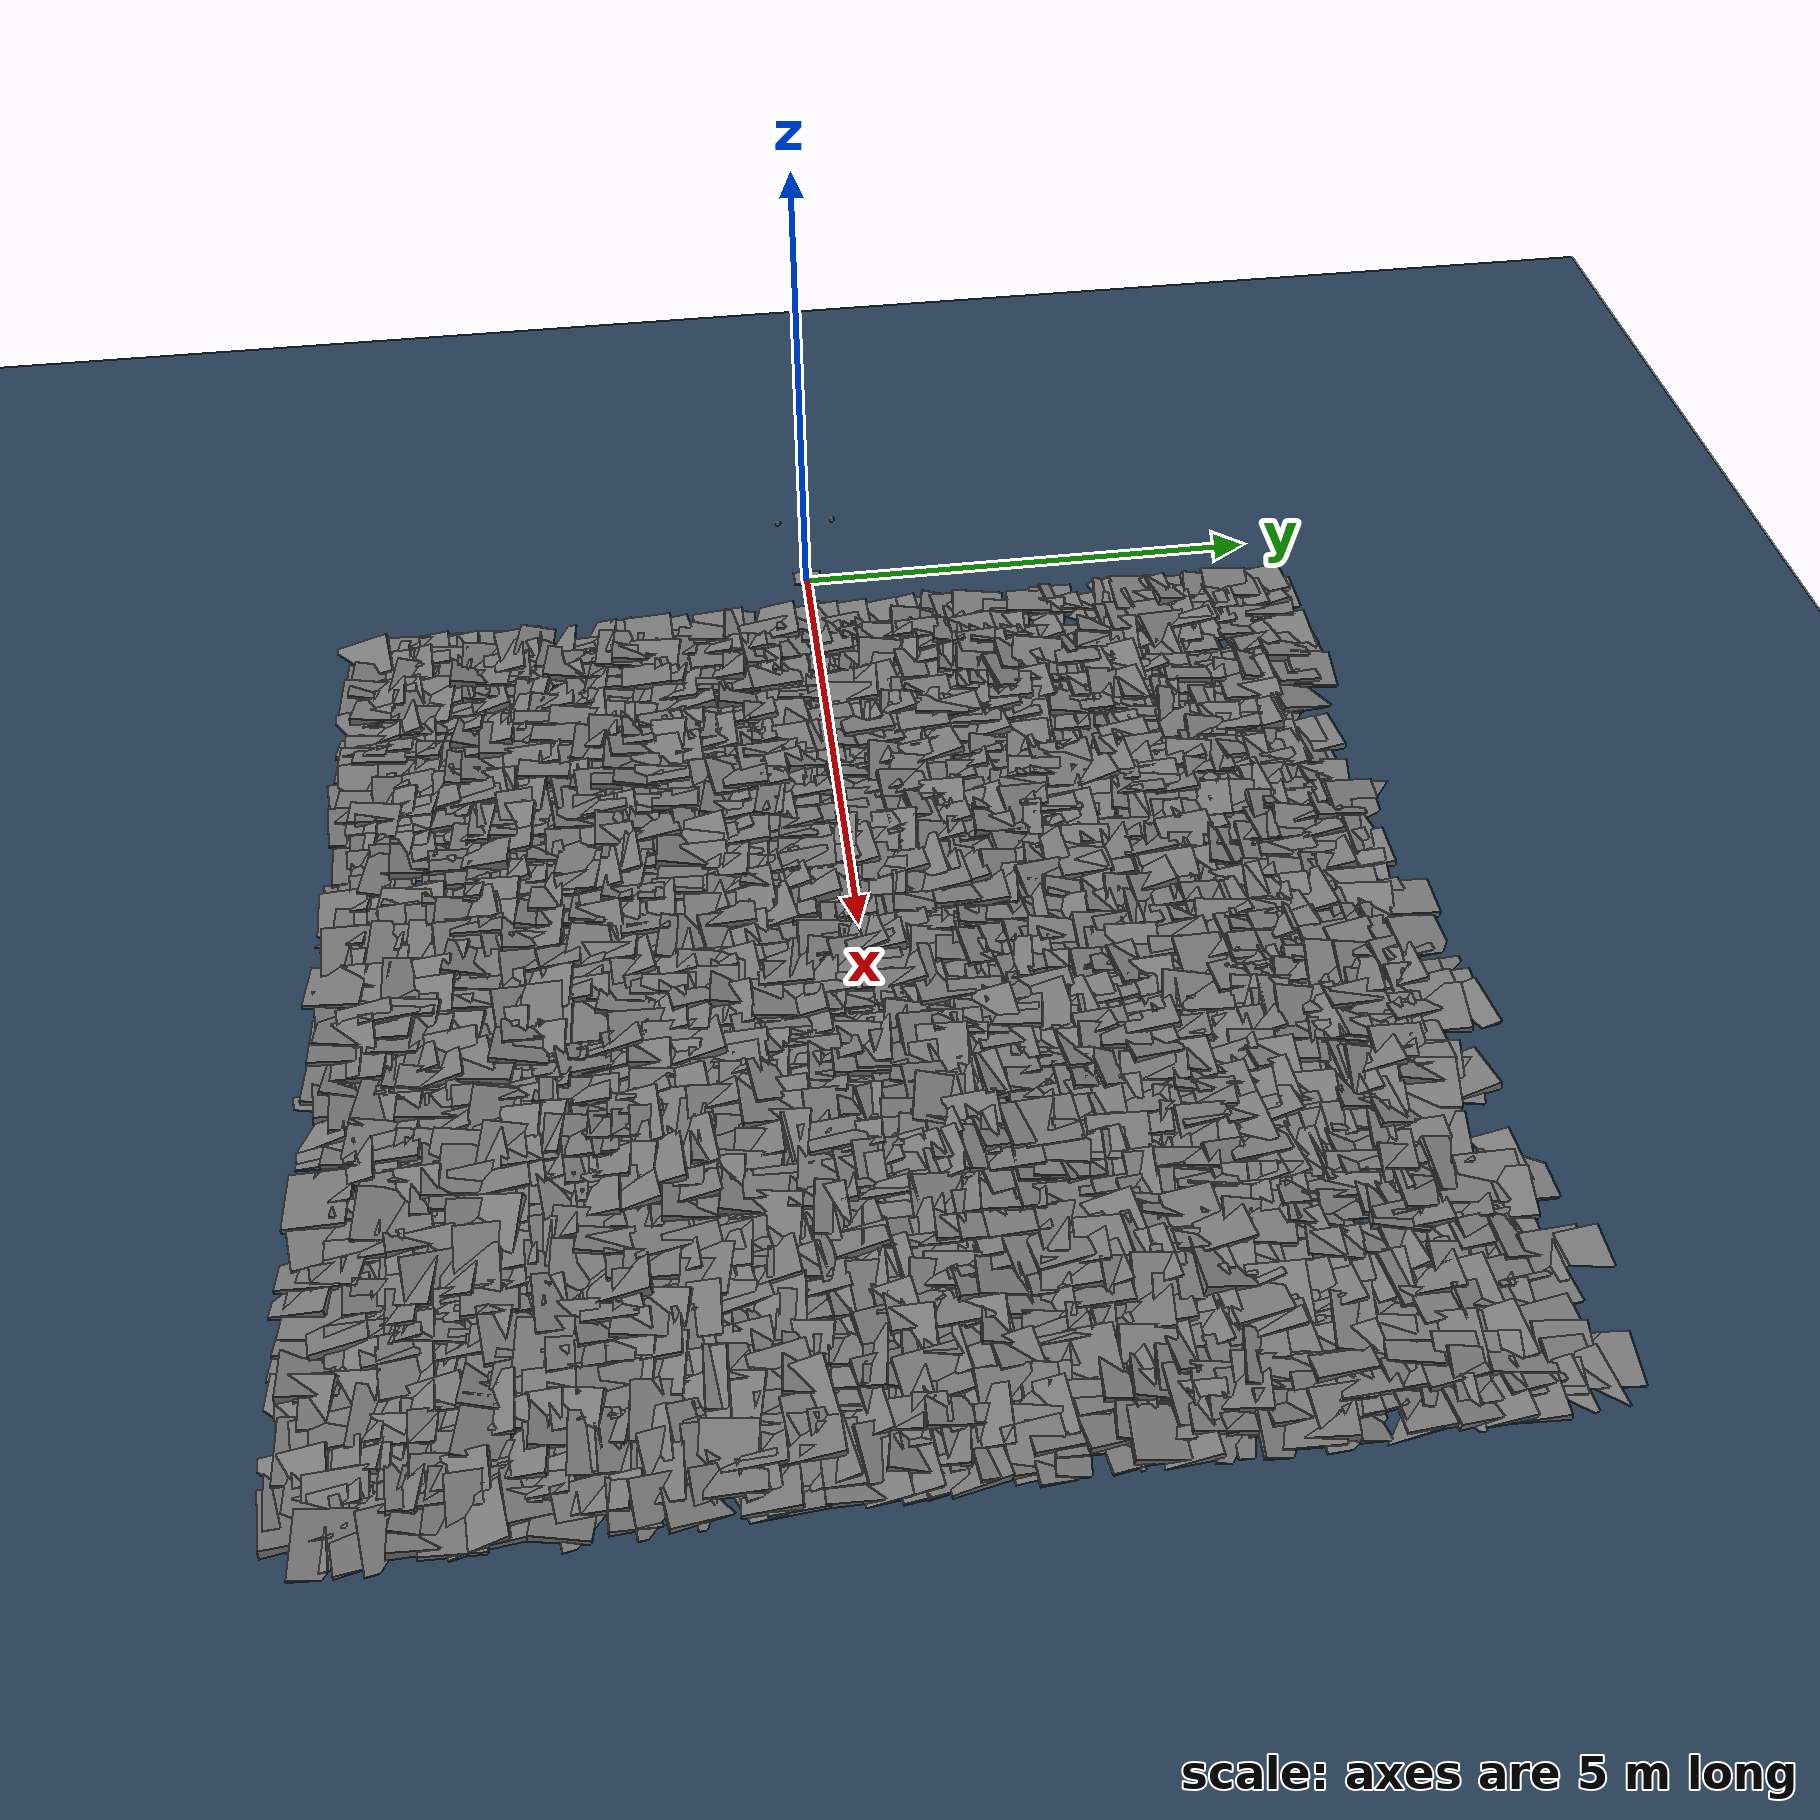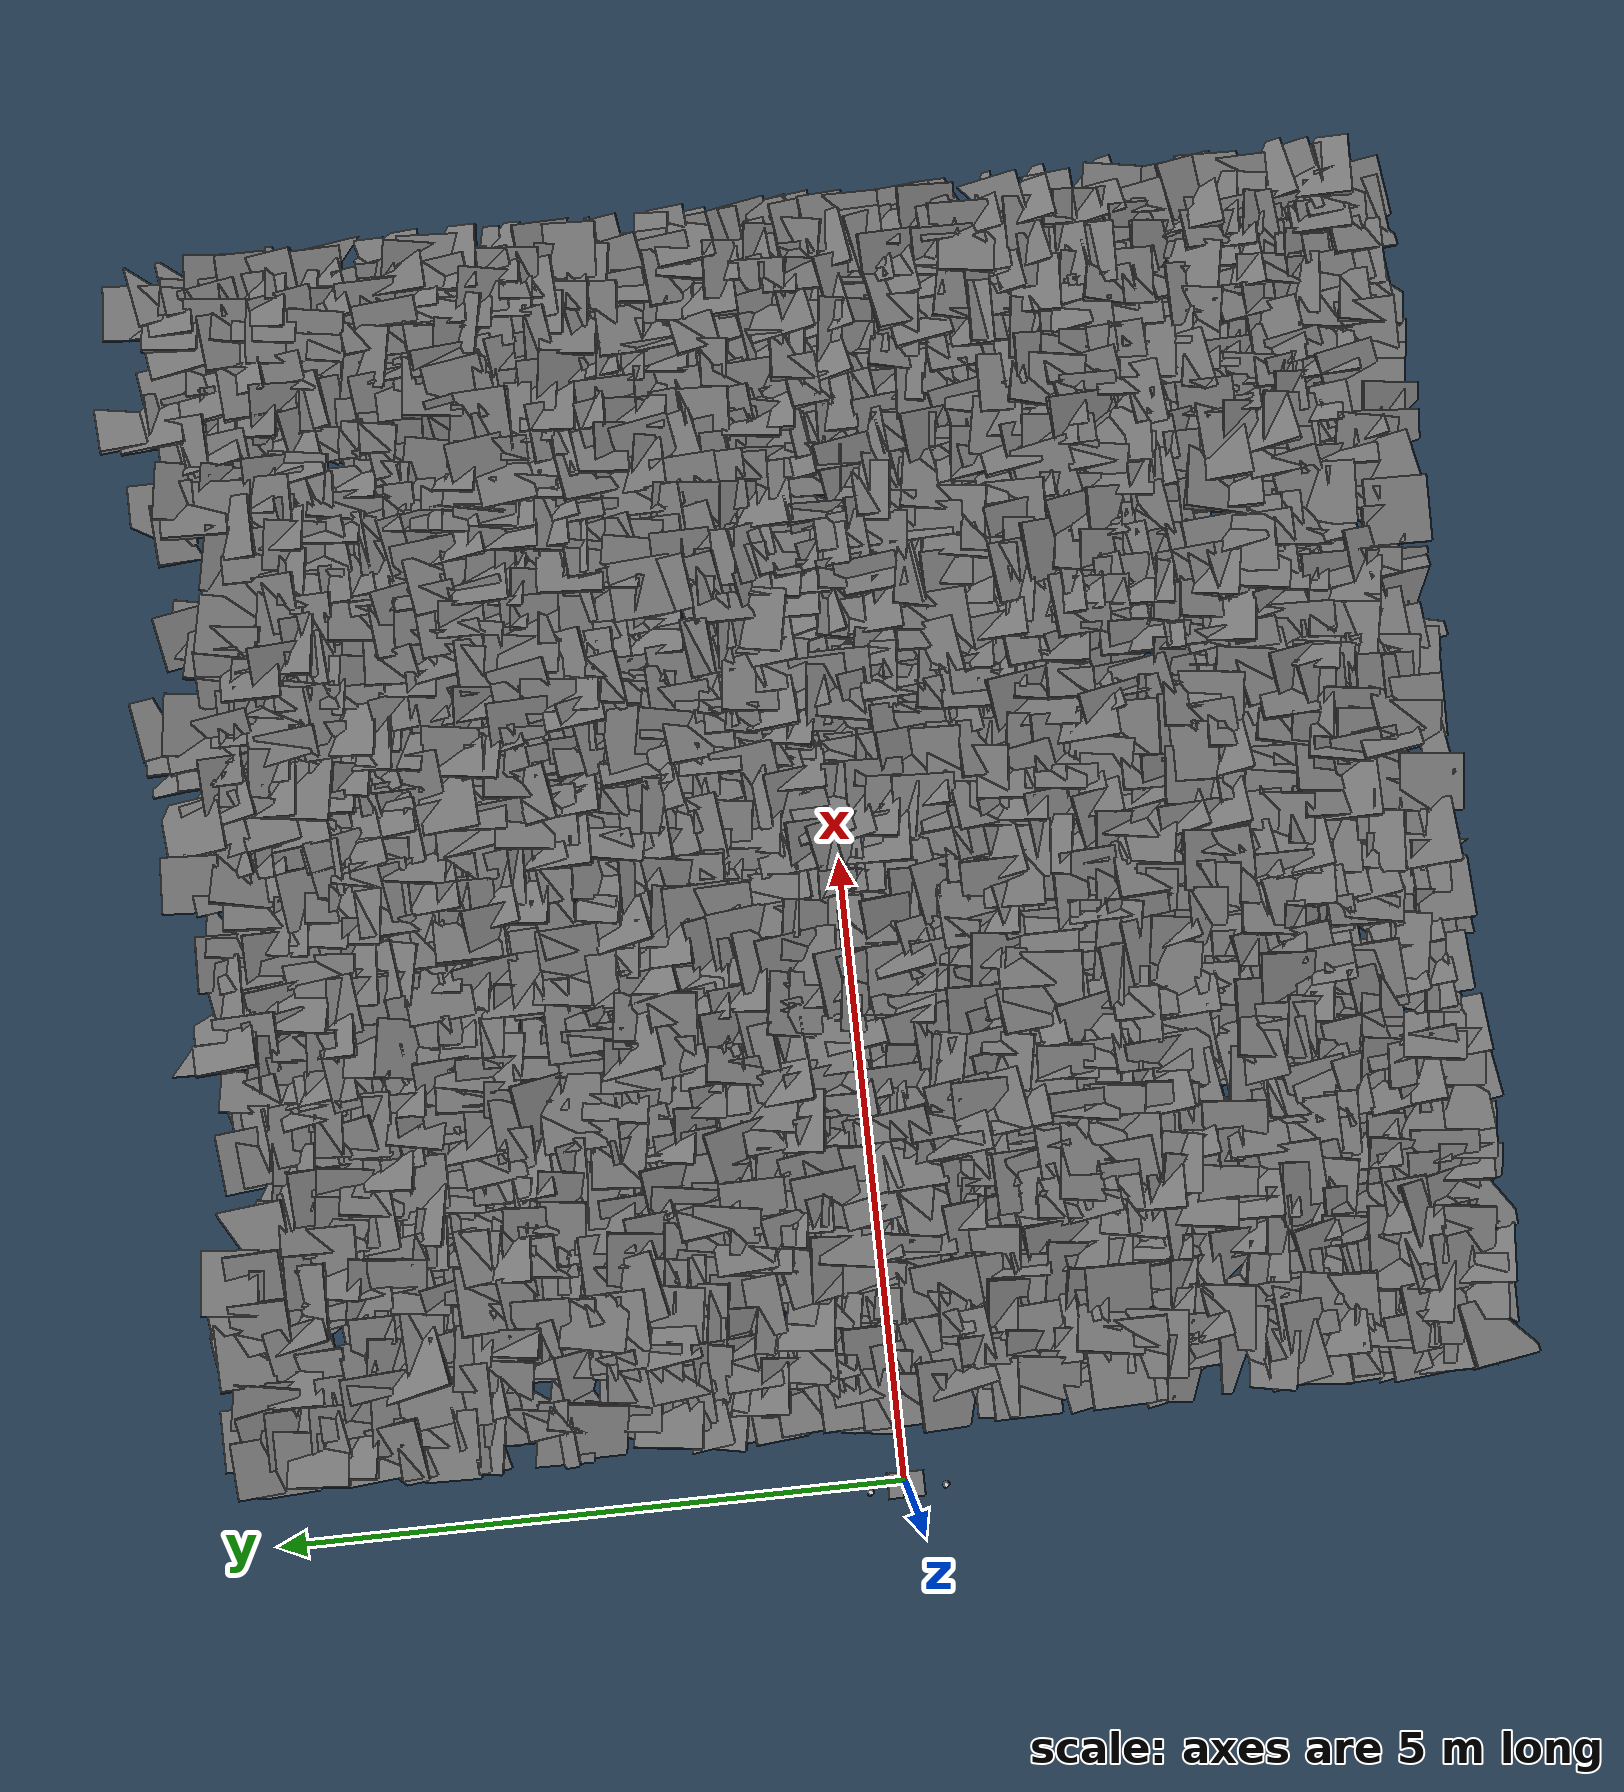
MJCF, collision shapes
<mujoco model="talos motor scene">
  <include file="talos_motor.xml"/>

  <statistic center="0 0 .9" extent="1.5"/>

  <visual>
    <rgba haze="0.15 0.25 0.35 1"/>
    <global azimuth="160" elevation="-10"/>
    <headlight diffuse="0.6 0.6 0.6" ambient="0.3 0.3 0.3" specular="0 0 0"/>
  </visual>

  <asset>
      <texture type="skybox" builtin="gradient" rgb1="0.3 0.5 0.7" rgb2="0 0 0" width="512" height="3072"/>
      <texture type="2d" name="groundplane" builtin="checker" mark="edge" rgb1="0.2 0.3 0.4" rgb2="0.1 0.2 0.3"
        markrgb="0.8 0.8 0.8" width="300" height="300"/>
      <material name="groundplane" texture="groundplane" texuniform="true" texrepeat="5 5" reflectance="0.2"/>
  </asset>
  <worldbody>
      <light pos="0 0 1.5" dir="0 0 -1" directional="true" />
      <geom name="floor" size="0 0 0.05" type="plane" material="groundplane" />
  <geom pos="0.6567804057144894 -4.806200678383943 -0.25" type="box" size="0.2584647946934144 0.27286762307202855 0.2678841120505624" quat="0.9903262040626077 0.09022710911746479 0.07586919984398863 0.07319113909677888" /><geom pos="0.6567804057144894 -4.597041099173856 -0.25" type="box" size="0.2256437921154316 0.226011023488007 0.24430231409466333" quat="0.995531828687515 0.05475050611753253 0.03516656901758951 -0.0684256718892666" /><geom pos="0.6567804057144894 -4.395919951034465 -0.25" type="box" size="0.27452286223961136 0.2653006291654832 0.24649976900714382" quat="0.9981587756504746 -0.028779031453054126 0.05337169653768679 0.0015125968592884186" /><geom pos="0.6567804057144894 -4.172343115958408 -0.25" type="box" size="0.25696678770296516 0.23688210009728417 0.27390878975256694" quat="0.9981865057053718 0.029308126788530748 -0.02910009216528987 0.04379404260648521" /><geom pos="0.6567804057144894 -3.9998653290828328 -0.25" type="box" size="0.26998000395171373 0.2694570517358573 0.23516652354827186" quat="0.9936587248041672 -0.0553919045762869 0.03177096307872338 0.0925455640915233" /><geom pos="0.6567804057144894 -3.8472209349262085 -0.25" type="box" size="0.24686023846089675 0.2477756346665334 0.24677537855616513" quat="0.9949156328485954 0.07345936775189478 0.06872996903234631 0.0047745324151462895" /><geom pos="0.6567804057144894 -3.631565018382169 -0.25" type="box" size="0.2581030002173187 0.27048535373224597 0.24750495168561223" quat="0.9970720754115928 -0.06861358387580378 -0.0062588685626899475 0.0331704553247596" /><geom pos="0.6567804057144894 -3.407954519042801 -0.25" type="box" size="0.26654138290718765 0.2638736262907206 0.2299848103133555" quat="0.9976053881676039 -0.03000848986892669 0.0471235647786898 -0.04077192265885032" /><geom pos="0.6567804057144894 -3.209563646896826 -0.25" type="box" size="0.23230677114964426 0.24572936884056723 0.2690410780211742" quat="0.9958893588698466 -0.021999501774267495 0.008743283060256724 0.08742975359005617" /><geom pos="0.6567804057144894 -3.000660607687953 -0.25" type="box" size="0.23614549109945698 0.2650387852798607 0.2580895681756942" quat="0.9930011953996046 -0.07971014369949314 0.0011631466198327852 -0.08714106963024336" /><geom pos="0.6567804057144894 -2.822084015439078 -0.25" type="box" size="0.23768156656421774 0.25967479513834757 0.22537098410795608" quat="0.9952850761993453 0.08494581334494095 -0.038167749931209756 -0.02711178259020941" /><geom pos="0.6567804057144894 -2.5807544376533023 -0.25" type="box" size="0.2687589380439497 0.2252907122038907 0.22862209935611272" quat="0.9966099863704033 0.028291025384130728 -0.061085735935752 0.04729361283182272" /><geom pos="0.6567804057144894 -2.401031393510248 -0.25" type="box" size="0.26644093348050224 0.27368210072690075 0.24072632522545065" quat="0.9937519970696286 0.09349732431655307 -0.030783634739001586 -0.05260785585847191" /><geom pos="0.6567804057144894 -2.1782385574038066 -0.25" type="box" size="0.2519177872135235 0.26313131238367016 0.22771129907696064" quat="0.9939543684172394 0.04742587144222932 0.007575410647534902 0.09873253453524222" /><geom pos="0.6567804057144894 -1.9493548050777405 -0.25" type="box" size="0.2706202585406213 0.24916761689440914 0.23910730489361456" quat="0.9979452338950248 0.003946947657367599 0.06362946326419533 0.0064049320921068745" /><geom pos="0.6567804057144894 -1.793078406661432 -0.25" type="box" size="0.264773636875402 0.2529079003299378 0.2736283001372733" quat="0.9994848681229394 0.017908747447894186 0.02267180445996054 0.013973705329909493" /><geom pos="0.6567804057144894 -1.5921981175697568 -0.25" type="box" size="0.22579769143412876 0.26923993477288305 0.2425224850923912" quat="0.9957149468645389 0.016466349422375598 -0.0022727076999116674 0.0909694384228009" /><geom pos="0.6567804057144894 -1.3657596508125764 -0.25" type="box" size="0.25693164089932385 0.2303338007974223 0.23868235966670057" quat="0.9953903174430719 0.012936215961659175 -0.06039243792063378 -0.07337249961106712" /><geom pos="0.6567804057144894 -1.1953310896965488 -0.25" type="box" size="0.2403651354403116 0.27232980855405636 0.25431739628037175" quat="0.995184169765943 0.006105807526179669 -0.07150969289247726 -0.06676489484862157" /><geom pos="0.6567804057144894 -1.012460754306856 -0.25" type="box" size="0.2714112301872028 0.2726826824735327 0.2529140187124333" quat="0.998624165346792 0.045493885805387366 0.02584138243171677 0.00350794722979697" /><geom pos="0.6567804057144894 -0.7918692509625815 -0.25" type="box" size="0.23219180299808617 0.2320174326988398 0.25875647468708113" quat="0.995376316358256 -0.08890827867732909 -0.0027407411445472063 -0.036246312277003985" /><geom pos="0.6567804057144894 -0.6228475862498364 -0.25" type="box" size="0.24566713251726452 0.24403260584315953 0.23880028938528572" quat="0.9975501360345929 0.0334123250420708 -0.0392010537737059 0.04733518792272126" /><geom pos="0.6567804057144894 -0.3801948391385581 -0.25" type="box" size="0.2728319202661808 0.23962258614656165 0.2747030223587241" quat="0.9961033731377452 0.08366781482475565 -0.0239668014919115 0.014260407157717503" /><geom pos="0.6567804057144894 -0.15251828188292826 -0.25" type="box" size="0.22852470453088666 0.2664735070685677 0.24742253138928244" quat="0.9925193332266458 -0.055235974553876535 -0.09229861369324464 -0.0577522830433828" /><geom pos="0.6567804057144894 0.03358523716460482 -0.25" type="box" size="0.24509895457289987 0.27406843933099456 0.25478212809943784" quat="0.9985468345205183 0.04049662800383025 0.034491062368683975 0.008637650493720625" /><geom pos="0.6567804057144894 0.1886000451267913 -0.25" type="box" size="0.2533988319603841 0.22688476635772312 0.26163318941196345" quat="0.9973107774919472 -0.04544721916771167 -0.004971227526260681 -0.057280452732253954" /><geom pos="0.6567804057144894 0.38810741965113493 -0.25" type="box" size="0.2320281406635365 0.23948069477892606 0.2715790859196486" quat="0.99802529890313 0.03629564910643104 0.049614594797173235 0.012904285659164858" /><geom pos="0.6567804057144894 0.5934707559703591 -0.25" type="box" size="0.26311773467066957 0.24645358496268632 0.2257881135970718" quat="0.9921184937430174 -0.08182309549879963 -0.06069024707066446 0.07295594099579672" /><geom pos="0.6567804057144894 0.7446084882575095 -0.25" type="box" size="0.22941627883715576 0.23275245793911634 0.24762659293581185" quat="0.9965233992648503 0.04839759909956186 0.05977128510435475 0.03203405369289866" /><geom pos="0.6567804057144894 0.9328290314865892 -0.25" type="box" size="0.2642876973307677 0.2657963117937193 0.23014825842959685" quat="0.9952597998673246 0.06258485404727121 0.059640305096851004 0.04454324662492851" /><geom pos="0.6567804057144894 1.144176248626862 -0.25" type="box" size="0.23020227003273117 0.24737690203739637 0.24448355787668813" quat="0.9997260360156693 0.01969386642870087 0.0072865457575892285 0.010339767328503597" /><geom pos="0.6567804057144894 1.3731400713511555 -0.25" type="box" size="0.2744127609446889 0.22830805248421263 0.24118807965862424" quat="0.9915346544221969 -0.0878685530177391 0.028490813899980545 -0.09124921914043971" /><geom pos="0.6567804057144894 1.5613937038801113 -0.25" type="box" size="0.2678671558852626 0.2404180898247331 0.23353714729814784" quat="0.995817094034629 -0.05784785879530196 0.026115039057407943 0.065726289993088" /><geom pos="0.6567804057144894 1.8034334453633907 -0.25" type="box" size="0.24331298446909835 0.27410068461066917 0.25857053108334666" quat="0.9942942242637227 -0.0374937018188245 0.07721738823522303 -0.06333003137417285" /><geom pos="0.6567804057144894 2.0333436971596512 -0.25" type="box" size="0.22538223611915897 0.2289717160604531 0.23927434857085683" quat="0.9969349761077222 0.0036581559736834526 -0.04235650271932618 -0.06567494183747237" /><geom pos="0.6567804057144894 2.2384036097561415 -0.25" type="box" size="0.22902992012067538 0.2675647189392504 0.24016630501513278" quat="0.991273387107128 -0.024212638955791316 -0.08440919457032926 -0.09831534976770918" /><geom pos="0.6567804057144894 2.4055619577502814 -0.25" type="box" size="0.2445397520586143 0.24264542587893817 0.2667298144363359" quat="0.9941935395575767 0.0061391751253786365 -0.08098930213928564 -0.07058505061093778" /><geom pos="0.6567804057144894 2.6507980171530656 -0.25" type="box" size="0.2597987719916846 0.23325140981772075 0.2559732142241147" quat="0.9964363854043238 0.002427876470990115 -0.04483499021419424 -0.07140349368693814" /><geom pos="0.6567804057144894 2.8083057239978526 -0.25" type="box" size="0.2692964116457144 0.271579257895847 0.2322686426263319" quat="0.9935761814522339 -0.09598513414807795 -0.04721428730630836 0.036932868119473175" /><geom pos="0.6567804057144894 2.967305636441081 -0.25" type="box" size="0.2664663580783684 0.23119090997467606 0.23027360564430097" quat="0.993063982248623 -0.030568696334906387 -0.0960167589178282 -0.060582703569636125" /><geom pos="0.6567804057144894 3.1918674923601866 -0.25" type="box" size="0.2465120372538321 0.23687508626097936 0.23586356696828936" quat="0.9954721388043334 0.08534818132258509 0.01918650063568028 0.037185844115871336" /><geom pos="0.6567804057144894 3.371890842171549 -0.25" type="box" size="0.25069935070655136 0.2573075851062331 0.23974917324838674" quat="0.9954349443028543 -0.06042861353496311 0.01574976761345491 -0.07217755293120896" /><geom pos="0.6567804057144894 3.569354925282683 -0.25" type="box" size="0.274628645088534 0.24736527726029955 0.25927065548476486" quat="0.9988532381820967 -0.04646275362341652 -0.008537572839274431 -0.007780163808244328" /><geom pos="0.6567804057144894 3.8086259670246214 -0.25" type="box" size="0.24854567574320502 0.22937175652213948 0.24367107918880376" quat="0.9950274209489948 0.08884945098515243 0.03537989490628445 0.02782929491828902" /><geom pos="0.6567804057144894 4.021724446354362 -0.25" type="box" size="0.24922579434230885 0.26907823949708554 0.262529653862023" quat="0.9912801300735719 -0.08395219706382337 -0.07727430377364765 0.06591217115053626" /><geom pos="0.6567804057144894 4.184673038373969 -0.25" type="box" size="0.23837465027877383 0.2399539107502093 0.24048809194018111" quat="0.9983875896117758 -0.025007412649808904 0.0216332979285359 0.0461394694647222" /><geom pos="0.6567804057144894 4.3745068938385145 -0.25" type="box" size="0.2257475687421264 0.2594376154429267 0.26490371430348114" quat="0.9911071059931211 -0.0672531020057354 0.09886705681959837 -0.05838689747175143" /><geom pos="0.6567804057144894 4.618341669993823 -0.25" type="box" size="0.260927080777704 0.2465305352463034 0.27222835270846507" quat="0.9959490095847312 -0.025369381973765318 0.07900095411059738 -0.03465276345513332" /><geom pos="0.6567804057144894 4.8543459569963705 -0.25" type="box" size="0.26929639071197875 0.25004411531153475 0.25962849440747016" quat="0.9957324074067331 0.0066854190507190416 -0.0511778806038434 -0.07650557201280707" /><geom pos="0.6567804057144894 5.081526847335658 -0.25" type="box" size="0.2277248773357561 0.25654744192608836 0.26936118862290537" quat="0.9972440790220977 0.05875863483954511 -0.031403036545492584 0.03264228826053479" /><geom pos="0.8660603982331834 -4.779280836094154 -0.25" type="box" size="0.2352039740273955 0.25723889911345754 0.2282445636596288" quat="0.9961743853545143 -0.04879334660455166 -0.07248453129655812 -0.00134015424555806" /><geom pos="0.8660603982331834 -4.55902253364924 -0.25" type="box" size="0.26973627696203023 0.249759249234589 0.24808004762386712" quat="0.9965100102219425 0.0618586603439435 0.02335707048421991 -0.05094853213108519" /><geom pos="0.8660603982331834 -4.321969716004724 -0.25" type="box" size="0.26821438765357913 0.23642393617243368 0.26821131484467725" quat="0.9968759507463472 0.06597676433417587 0.00010276495070579749 0.04342113345968836" /><geom pos="0.8660603982331834 -4.14498066346092 -0.25" type="box" size="0.26383276991340987 0.252211931807196 0.2508311719522376" quat="0.998291223959504 -0.0488795181205142 0.02879903426324223 -0.014001446326944198" /><geom pos="0.8660603982331834 -3.9893933612725463 -0.25" type="box" size="0.26943053697847613 0.22699224493768422 0.2530888223748086" quat="0.992896051894041 0.027172964531681137 0.08978900456403048 -0.07319149398110843" /><geom pos="0.8660603982331834 -3.823946209259832 -0.25" type="box" size="0.24109457944422985 0.23308701172939997 0.2634119711915051" quat="0.998494240899409 -0.03822618877680274 -0.008560408657459752 -0.03840219767058159" /><geom pos="0.8660603982331834 -3.606097968690843 -0.25" type="box" size="0.2740878229574917 0.24464655439850244 0.25111718696486135" quat="0.9944673150034797 -0.08552970184435203 0.060984666522130394 -0.0005476690338505254" /><geom pos="0.8660603982331834 -3.3667430716693296 -0.25" type="box" size="0.24311626806999814 0.253387948278673 0.268281742939184" quat="0.9962129666117885 0.071992109655852 -0.03238545059175538 0.03644233653058314" /><geom pos="0.8660603982331834 -3.2027940794575716 -0.25" type="box" size="0.2509370552036274 0.27067529979041133 0.2297880182294392" quat="0.9925278282079466 0.09394052055478842 0.06981898876406714 0.03448184505903204" /><geom pos="0.8660603982331834 -2.976756348835967 -0.25" type="box" size="0.2400819859729694 0.23627354840328374 0.24489082689946118" quat="0.9941195445079237 0.014150682926640385 -0.04764340375596777 -0.09620912367657149" /><geom pos="0.8660603982331834 -2.765595127745308 -0.25" type="box" size="0.27131843322528665 0.27223497082426706 0.22963287546512517" quat="0.9907301424395927 -0.09607375989520581 -0.043349293361744805 -0.08569980330350979" /><geom pos="0.8660603982331834 -2.5822306411052325 -0.25" type="box" size="0.24134742051804844 0.24782629290638364 0.24638826705134162" quat="0.9975051495413837 0.012355849223832352 -0.06905391995751178 -0.00789719993930598" /><geom pos="0.8660603982331834 -2.3701568731906346 -0.25" type="box" size="0.2551722281978216 0.24596547314867917 0.22733706431156686" quat="0.9975279033111191 0.003964113367040406 0.06441724059009091 0.02779904738825312" /><geom pos="0.8660603982331834 -2.139251798724717 -0.25" type="box" size="0.27014369343219974 0.24945589056073347 0.27455230354454946" quat="0.9973697213555575 -0.04423620971323329 0.004580466410124308 -0.05723474469944097" /><geom pos="0.8660603982331834 -1.9827856851139312 -0.25" type="box" size="0.2594768045403824 0.26824226630604503 0.25977098653956265" quat="0.9950564415123305 -0.07091878516421318 -0.06947039112350854 0.0026587351874343195" /><geom pos="0.8660603982331834 -1.7378223941166624 -0.25" type="box" size="0.22519628384451523 0.2263708870781062 0.23019047386631444" quat="0.9952950669276726 -0.08759557555465872 0.041378162315861076 -0.001610147834909848" /><geom pos="0.8660603982331834 -1.5607293443735637 -0.25" type="box" size="0.235436533716683 0.2683572637846979 0.25326920195901587" quat="0.996330216245602 0.001629858596507128 -0.07758853627049024 -0.036103501164706696" /><geom pos="0.8660603982331834 -1.348624225260827 -0.25" type="box" size="0.23967582219880557 0.25400144110674583 0.22821194386552915" quat="0.9987492984550519 -0.034583074484942314 0.02775911375537073 -0.023092886312170165" /><geom pos="0.8660603982331834 -1.1132366240790228 -0.25" type="box" size="0.2519743582694393 0.2563638401812865 0.23986231775386344" quat="0.9910165083438842 0.0844398747868379 -0.08496918136199855 -0.05946785648189147" /><geom pos="0.8660603982331834 -0.9575821555605692 -0.25" type="box" size="0.2431318713294863 0.2676901435797989 0.23472883034177583" quat="0.9957556931016112 0.06177312901557008 0.001745434224539896 -0.06820288591198716" /><geom pos="0.8660603982331834 -0.740884944266079 -0.25" type="box" size="0.2625157306495035 0.230013429403785 0.25224363088420854" quat="0.9939570728669184 0.06457678922878113 -0.08633213036186622 0.020638286215448838" /><geom pos="0.8660603982331834 -0.520476987666969 -0.25" type="box" size="0.2568540684669368 0.2747071484420543 0.25891771449156686" quat="0.9917931424112802 -0.007706160858017148 0.08013104522684325 0.09932770681759447" /><geom pos="0.8660603982331834 -0.30857284487574255 -0.25" type="box" size="0.23244922973803303 0.267981968000807 0.25343293144863666" quat="0.9931450131178682 -0.036299078946377496 -0.05158919572324862 -0.09840688325204923" /><geom pos="0.8660603982331834 -0.08006850215931749 -0.25" type="box" size="0.26004079266247127 0.24582308306694645 0.2556975828302029" quat="0.9971081874649803 0.041977767292047476 -0.0358490248876574 0.052230038848162845" /><geom pos="0.8660603982331834 0.0838405769281545 -0.25" type="box" size="0.2389919606636551 0.24737161769721736 0.22703096523576405" quat="0.9896959035319604 -0.0702212597994462 -0.09076135308801773 -0.08563509788554956" /><geom pos="0.8660603982331834 0.29971956466900185 -0.25" type="box" size="0.2567819610401807 0.22929597837057494 0.24145567742900437" quat="0.9943072362131422 0.023821064031568914 0.09027037841459756 0.051351102261506756" /><geom pos="0.8660603982331834 0.48697330545591644 -0.25" type="box" size="0.22831296466200401 0.2321176764989294 0.24014831975073878" quat="0.9906273975601758 -0.10149098517755367 -0.0645801520781956 -0.06470195583133807" /><geom pos="0.8660603982331834 0.6434992036947289 -0.25" type="box" size="0.2741893426547528 0.24646354490145672 0.2509907847604854" quat="0.9950520875241476 -0.09397549858878847 -0.030657337859232622 -0.010003819980860794" /><geom pos="0.8660603982331834 0.8702325434194629 -0.25" type="box" size="0.2379145975515269 0.2364977768174831 0.2607196232136839" quat="0.9929874395998933 0.08198315713579009 -0.07080356379735671 -0.047345138044894694" /><geom pos="0.8660603982331834 1.0329499118523264 -0.25" type="box" size="0.26303636857396734 0.23492239029646225 0.27229460817141216" quat="0.9945983331206019 -0.08049067993755077 0.05523655837061094 -0.03527504523428772" /><geom pos="0.8660603982331834 1.2463544093457442 -0.25" type="box" size="0.2436946635855443 0.23139803628156388 0.24779786306138885" quat="0.9929376910325491 -0.061197143824539404 -0.052138182631667744 0.08724254252677055" /><geom pos="0.8660603982331834 1.422141259672797 -0.25" type="box" size="0.2735506100954099 0.2694375397474159 0.24224077263968644" quat="0.9947732732197453 0.04386575000069307 -0.011439157235438849 0.09149358745996175" /><geom pos="0.8660603982331834 1.6645206589836956 -0.25" type="box" size="0.24659953593217457 0.24038823878389656 0.2486030689212039" quat="0.9964636102172114 -0.06146241853671211 -0.051409367093416286 0.025292718231813366" /><geom pos="0.8660603982331834 1.864699846626861 -0.25" type="box" size="0.2475562393700691 0.2640133539773483 0.23393676626739057" quat="0.9959078801109377 -0.017407390119763822 0.04249709856093566 0.07783619798049227" /><geom pos="0.8660603982331834 2.095476003629696 -0.25" type="box" size="0.25492238799488826 0.2506478695693477 0.2649522601177801" quat="0.9975883223286403 -0.027108896873647155 0.006827339735420885 -0.06352979061794474" /><geom pos="0.8660603982331834 2.335212293767106 -0.25" type="box" size="0.22709603649253998 0.26363728580543067 0.23199274858752092" quat="0.9969654130316955 0.05937153429665054 0.03930472613778565 -0.03146624599529628" /><geom pos="0.8660603982331834 2.5298272753651387 -0.25" type="box" size="0.262720739713539 0.2653909478576789 0.23004411235173905" quat="0.9878279514329398 0.0824675978964105 0.09086927232819272 -0.09559188779149769" /><geom pos="0.8660603982331834 2.7444934333924884 -0.25" type="box" size="0.2595450392243808 0.2648837654759834 0.23924013135891123" quat="0.9930640410770187 0.06092032538705887 0.07703622278861932 0.06463702230903369" /><geom pos="0.8660603982331834 2.9296152417482126 -0.25" type="box" size="0.2639532095085284 0.2318785590068615 0.23601623492605558" quat="0.9978337939073292 0.06500733470865543 0.002888436473111164 -0.00966556285598911" /><geom pos="0.8660603982331834 3.0800790444786124 -0.25" type="box" size="0.2582485998810987 0.23339949045324743 0.2452077991317768" quat="0.9982556095431833 0.04681737388642817 -0.008924252169350841 -0.034845792302142055" /><geom pos="0.8660603982331834 3.3229992165379976 -0.25" type="box" size="0.2455480365973053 0.2444712434498132 0.24041316993402365" quat="0.9957576934154181 0.07108363958360983 0.016301037406950887 0.05610711511930434" /><geom pos="0.8660603982331834 3.513536413950753 -0.25" type="box" size="0.2728530128105015 0.24793566902942168 0.23407279733473765" quat="0.9981322733829997 -0.03738536585480063 -0.005841050833280384 -0.0479602061750189" /><geom pos="0.8660603982331834 3.7301607958743848 -0.25" type="box" size="0.2531721492333526 0.23279966163591315 0.22772667362484705" quat="0.9918782064495857 0.04521497751155002 0.09671844928429942 -0.06912865503554615" /><geom pos="0.8660603982331834 3.9554402135526665 -0.25" type="box" size="0.24469370281004618 0.26935431930456205 0.24620723042512468" quat="0.9963791156281321 0.08328977271955902 -0.001023033989340261 -0.01704186321627359" /><geom pos="0.8660603982331834 4.192749785363501 -0.25" type="box" size="0.2715059019260963 0.23163998067004973 0.23982273416579136" quat="0.997758066200182 0.04025902661973389 0.032394480499365906 0.0425282228794121" /><geom pos="0.8660603982331834 4.432231685211519 -0.25" type="box" size="0.23107959742179288 0.2585641592856726 0.2673343517309518" quat="0.9981981343576753 0.031240380694590265 -0.050749475217323356 -0.007000995934832781" /><geom pos="0.8660603982331834 4.648215739088579 -0.25" type="box" size="0.2691218608258611 0.2695619147427625 0.25922347704021637" quat="0.9941830899851996 -0.05045767343855456 -0.008195510211193038 0.09479894720421109" /><geom pos="0.8660603982331834 4.805300271427365 -0.25" type="box" size="0.2319163403004308 0.2702401488648331 0.2449926041774125" quat="0.9941281191332202 0.09452987895055442 -0.05175914273755778 0.009714724767719458" /><geom pos="0.8660603982331834 4.9840874444654855 -0.25" type="box" size="0.2700791606059789 0.27292872248612365 0.2525542846618375" quat="0.9898917824357898 0.06690260982526974 -0.08213567050257858 0.09429756887510203" /><geom pos="0.8660603982331834 5.147837021864515 -0.25" type="box" size="0.24532442035061733 0.23521275622129922 0.24954006266316017" quat="0.9996627098030125 0.014528347184834069 0.01927318858135906 0.00958842840524729" /><geom pos="1.0520180757110493 -4.771751406666002 -0.25" type="box" size="0.2631247741844028 0.24200847555486255 0.26195824421325536" quat="0.9944826649847964 -0.09394951034420891 -0.0010144442662219583 -0.04665500459383808" /><geom pos="1.0520180757110493 -4.530496656267183 -0.25" type="box" size="0.2664072313201373 0.2643399325733036 0.233550175125895" quat="0.9960297398380118 0.06281029696373538 -0.036700915065311514 0.05130951945709977" /><geom pos="1.0520180757110493 -4.348855505760406 -0.25" type="box" size="0.2633680501886659 0.22609626476343406 0.265357420351479" quat="0.9916346989498911 -0.085739189124574 0.05352037390694749 -0.08028066307449162" /><geom pos="1.0520180757110493 -4.118954562302469 -0.25" type="box" size="0.2691450954859097 0.24710963292600657 0.23236386907969078" quat="0.9967397671804273 0.07250499124670333 -0.008032984795629809 0.03447221954989689" /><geom pos="1.0520180757110493 -3.96781486183312 -0.25" type="box" size="0.24745581810151068 0.26788462488372555 0.23746479612374896" quat="0.9948417488314195 0.06814055392743115 0.019806084217925832 -0.07248778324971715" /><geom pos="1.0520180757110493 -3.720331002222342 -0.25" type="box" size="0.2620856625784562 0.24811863611804302 0.2683807554901945" quat="0.990396359171062 -0.09783373979425736 -0.0968953749540935 -0.012445778845861948" /><geom pos="1.0520180757110493 -3.534692290962603 -0.25" type="box" size="0.24411335331707606 0.26285943635236686 0.265906453391509" quat="0.9965248265020304 0.021860642416315825 -0.03260980324272818 -0.07346416276467646" /><geom pos="1.0520180757110493 -3.3171742397266994 -0.25" type="box" size="0.2585233263490599 0.2393083472656915 0.2701272834688838" quat="0.9993746188343479 0.01950062959649035 0.0026019880991553323 0.029382415369984982" /><geom pos="1.0520180757110493 -3.081543850398127 -0.25" type="box" size="0.23214189530834167 0.2731262388590862 0.259314724205916" quat="0.9981595724301444 0.0017111072681827827 -0.05093137323250686 0.03287149675081948" /><geom pos="1.0520180757110493 -2.8669189051433683 -0.25" type="box" size="0.23062000085773732 0.2618189693381207 0.23241625401812196" quat="0.9995104897866617 -0.01631148873278419 -0.026442753510160753 0.0036738166188584" /><geom pos="1.0520180757110493 -2.6891851843144647 -0.25" type="box" size="0.25957746245715513 0.26492195024117393 0.2724786481444002" quat="0.994813129995222 -0.05632945788872037 -0.061462316463041886 -0.058277029935208294" /><geom pos="1.0520180757110493 -2.5131242885027736 -0.25" type="box" size="0.23675112709569807 0.2399640384966615 0.24271789922962644" quat="0.9919539275078619 -0.08344788215639266 0.05417688262618272 0.07828615493335145" /><geom pos="1.0520180757110493 -2.35733683778628 -0.25" type="box" size="0.2570868278329959 0.26145062869629293 0.24457786040934554" quat="0.9978419080337337 -0.047260266098002386 -0.04514667811444313 -0.00630644711185641" /><geom pos="1.0520180757110493 -2.2015283382665416 -0.25" type="box" size="0.24450669163001645 0.26663601083443145 0.22939999338856093" quat="0.9976097714448398 -0.024618189778122083 0.06319813355465947 -0.013216828856814179" /><geom pos="1.0520180757110493 -1.9530535306132952 -0.25" type="box" size="0.2353759262138196 0.2252329598470822 0.2534616859701623" quat="0.9935748595566413 0.022762376483044452 0.08873119815318022 -0.06646538308131371" /><geom pos="1.0520180757110493 -1.7428364369930063 -0.25" type="box" size="0.26587721817792526 0.2709154487484128 0.27481360694825385" quat="0.9917348006187495 0.04956836859892236 0.09004223650362639 -0.07679490687249836" /><geom pos="1.0520180757110493 -1.496849984711485 -0.25" type="box" size="0.2678940000844061 0.2697059620412978 0.2597733987105951" quat="0.9989848235025597 -0.029998234817488433 -0.004395650474857888 -0.033318261903902545" /><geom pos="1.0520180757110493 -1.326901401822699 -0.25" type="box" size="0.27370120662548025 0.24002324366228142 0.2562327127196347" quat="0.9947385877205913 -0.09902216672256264 0.023440482481037927 0.011844677212507398" /><geom pos="1.0520180757110493 -1.1708895066630927 -0.25" type="box" size="0.24945000522331492 0.22864743514321026 0.2613624439476844" quat="0.998917928034357 -0.01753682047017512 -0.030640291429547006 0.03027549372770851" /><geom pos="1.0520180757110493 -0.9791595295189115 -0.25" type="box" size="0.2595953149127289 0.2601166223391886 0.2538626436187283" quat="0.9948742167727891 0.06132473073833228 0.06456885682839567 -0.04791067656039337" /><geom pos="1.0520180757110493 -0.7801888927857412 -0.25" type="box" size="0.2521323588940545 0.2394845521518624 0.22713767037862692" quat="0.995939107665496 0.04954044832842079 0.0688978589472127 -0.030068635392460814" /><geom pos="1.0520180757110493 -0.5769990128914051 -0.25" type="box" size="0.23724075148685794 0.2709038668492423 0.26415822170542136" quat="0.9951690747911748 -0.07908931408881761 -0.011841603971340472 0.05694883134554616" /><geom pos="1.0520180757110493 -0.3585188776307957 -0.25" type="box" size="0.24671894603929098 0.24918407233166256 0.27227994826992324" quat="0.9957072869658591 -0.015215037841009795 -0.042361755080717045 0.08087634396451489" /><geom pos="1.0520180757110493 -0.15700068862999306 -0.25" type="box" size="0.24673394050160527 0.26639472708228634 0.2594826144317889" quat="0.9977048123466319 -0.040584588522088655 -0.053924250755606605 0.005493066112063452" /><geom pos="1.0520180757110493 0.0017762306202717681 -0.25" type="box" size="0.2517229134200141 0.24714229220112308 0.2449809546876773" quat="0.9989456732099341 -0.040810993076520426 -0.012153652193846462 -0.017154986377454" /><geom pos="1.0520180757110493 0.1726624073208276 -0.25" type="box" size="0.2315491059430435 0.2414374186920936 0.2681953916763422" quat="0.9951675579462205 0.05895298344522482 -0.07850590573432044 -0.001702973604303876" /><geom pos="1.0520180757110493 0.34847862007178154 -0.25" type="box" size="0.2253927598475625 0.23698209947412507 0.2316765864763131" quat="0.9918341674829765 0.09563639992079857 -0.02928181840574681 -0.0791279870487846" /><geom pos="1.0520180757110493 0.5414972429089735 -0.25" type="box" size="0.24732269057543851 0.26153474962001066 0.26091469309749205" quat="0.9957812622515783 -0.01794651203474998 0.0617867377868318 0.0654217050228819" /><geom pos="1.0520180757110493 0.7388826187135731 -0.25" type="box" size="0.2254231126748971 0.2606389496533504 0.27272891479942435" quat="0.9949446354122844 -0.0008429029298190303 0.05306477368202839 -0.08525603657831293" /><geom pos="1.0520180757110493 0.956563514566823 -0.25" type="box" size="0.22816296782615555 0.23437559559995 0.24407310117066539" quat="0.9952522239663777 -0.07486340129856228 0.028021566277785917 -0.05552723349248887" /><geom pos="1.0520180757110493 1.115890694412709 -0.25" type="box" size="0.24697478785716384 0.2263282142609669 0.2720501982007519" quat="0.997330882663382 -0.004518210911919129 0.0674307358949442 0.027636789117066924" /><geom pos="1.0520180757110493 1.3644006789931158 -0.25" type="box" size="0.2485387276846821 0.25806114231153116 0.2539871903396274" quat="0.9935110361754549 0.07557317675141342 -0.0815330627583867 0.024018235374618106" /><geom pos="1.0520180757110493 1.524463986280252 -0.25" type="box" size="0.23608525398490773 0.26482098342045646 0.2671956129603727" quat="0.9926808640641451 -0.04895704159678557 -0.07319142589611087 -0.0826494124252977" /><geom pos="1.0520180757110493 1.7126392162030548 -0.25" type="box" size="0.2508702067886928 0.2570577261169086 0.2644236022786305" quat="0.9973946110025226 0.018190147384571937 0.043135364442298 0.05488577972192956" /><geom pos="1.0520180757110493 1.879539987132234 -0.25" type="box" size="0.26348352624454563 0.24487968467195903 0.24651867764962213" quat="0.9939531587404509 -0.07723658461688115 -0.07226573916776081 -0.029483744150577338" /><geom pos="1.0520180757110493 2.058011676036142 -0.25" type="box" size="0.24102948038395464 0.25793694288528 0.24068172455823353" quat="0.995206683280468 0.07162756947509584 0.055693534581453014 -0.03648806723855337" /><geom pos="1.0520180757110493 2.215261064820372 -0.25" type="box" size="0.22582308506128226 0.2376981426645181 0.240240697316079" quat="0.9897439258819118 -0.08054527540483003 -0.09690035375634432 0.0673033523066704" /><geom pos="1.0520180757110493 2.4524847367990743 -0.25" type="box" size="0.2554885135048221 0.24810040858113214 0.24463368028681853" quat="0.9933283902885209 0.08335047170875623 -0.03655630835732906 0.0708169770042994" /><geom pos="1.0520180757110493 2.6862592427246454 -0.25" type="box" size="0.2706068440849874 0.2587703762597055 0.23210109331295284" quat="0.9975317766507301 -0.003979475549990855 -0.039605600028596366 0.05784388293294278" /><geom pos="1.0520180757110493 2.869583779323767 -0.25" type="box" size="0.23288576136920136 0.27094098464994226 0.2284058027723754" quat="0.9991658324284277 -0.01972480177497901 0.002983665723144887 0.03563241840511872" /><geom pos="1.0520180757110493 3.0874760853105467 -0.25" type="box" size="0.27019063222629003 0.22917403106450668 0.24344425609690262" quat="0.992765604554498 -0.042943562707792995 -0.08964418637002118 -0.06735150098966351" /><geom pos="1.0520180757110493 3.2954994401406026 -0.25" type="box" size="0.2650036946370934 0.22588832597159217 0.2321576822706994" quat="0.9918824466255706 -0.09954296480652133 0.048632537076144906 0.062412230941837614" /><geom pos="1.0520180757110493 3.452244008222401 -0.25" type="box" size="0.24379902302490097 0.2517849136413181 0.27023538790635937" quat="0.9986566487227804 -0.03741326043758052 -0.035154083084683686 0.007023983747845804" /><geom pos="1.0520180757110493 3.7005670125482677 -0.25" type="box" size="0.2353520024664109 0.2701314077646425 0.2641572023213487" quat="0.9975918339025429 -0.02532265180328591 -0.010264457892514173 0.0637490167828786" /><geom pos="1.0520180757110493 3.936005711081215 -0.25" type="box" size="0.26946048966685593 0.24065047936731304 0.22819349502686626" quat="0.9989357505282491 0.005525971140788352 0.044158851744887866 -0.012117168484751344" /><geom pos="1.0520180757110493 4.154865403399766 -0.25" type="box" size="0.26495544686133615 0.2684203252757312 0.2614825172422357" quat="0.9953764490008319 0.05561174936391151 -0.07405666180593613 0.025468980139396986" /><geom pos="1.0520180757110493 4.384254881411092 -0.25" type="box" size="0.25184496188326483 0.2350102038167175 0.274923141949026" quat="0.9988150676222823 0.041188237530644704 -0.00821008420089025 0.024588295939920363" /><geom pos="1.0520180757110493 4.5546024154321785 -0.25" type="box" size="0.24786813546249722 0.24421581816581822 0.23185399371389184" quat="0.9994432538056591 -0.01773227711419085 0.004163798824450572 0.027953739464546292" /><geom pos="1.0520180757110493 4.798606090098364 -0.25" type="box" size="0.2643143977906768 0.2449003360640942 0.24106910139913815" quat="0.9969855180088827 0.05820750225373826 -0.04665204849131321 -0.0213389299990611" /><geom pos="1.0520180757110493 5.034315982177164 -0.25" type="box" size="0.27404304057931805 0.26294866209395623 0.26307112449927794" quat="0.991434341510194 0.00967951317652557 -0.09222188576514714 -0.09197487311670216" /><geom pos="1.299689929718105 -4.848433219881148 -0.25" type="box" size="0.2745157779094224 0.23817224940217158 0.25146010401784563" quat="0.9926487506734261 -0.06433075661159147 0.0909649901675148 -0.04727982766561813" /><geom pos="1.299689929718105 -4.621789252975538 -0.25" type="box" size="0.2255101980576499 0.2668491280484224 0.2676420858972665" quat="0.9962151348901674 0.07278640627254603 -0.03850211483233509 0.02784117869506913" /><geom pos="1.299689929718105 -4.39099745969812 -0.25" type="box" size="0.2600474420119333 0.22816969696880982 0.2334523566670192" quat="0.9917924808917035 0.0956381741119976 0.050067528518586694 0.068514648705543" /><geom pos="1.299689929718105 -4.168206444745075 -0.25" type="box" size="0.2635559416432498 0.2712861056769949 0.2448345405777938" quat="0.9930034557429884 0.022417126539317676 0.09865025157625004 -0.06090761187360205" /><geom pos="1.299689929718105 -3.9424393632083135 -0.25" type="box" size="0.26102026194049416 0.2694425938746693 0.24612646584642758" quat="0.9922742716959001 0.04759120686074926 -0.06347195961306296 0.0953842602465744" /><geom pos="1.299689929718105 -3.7886258721062394 -0.25" type="box" size="0.2742491375887741 0.2529436557730809 0.24764824787188558" quat="0.9992731648482359 -0.018146202663796518 0.022690958353288007 0.024677474588860066" /><geom pos="1.299689929718105 -3.6232028691263807 -0.25" type="box" size="0.2336355946691868 0.22945533964568302 0.24077846355367843" quat="0.9916348320627126 -0.09657782506771971 -0.08368636550419076 0.018156975900290907" /><geom pos="1.299689929718105 -3.4242706141673427 -0.25" type="box" size="0.25466895118553096 0.2597985097576761 0.2431011887530281" quat="0.997356071650375 -0.05491964654765087 0.00751124222764953 -0.046992339858863884" /><geom pos="1.299689929718105 -3.2662687057744457 -0.25" type="box" size="0.22899046698098763 0.2614256166901495 0.24470836512578553" quat="0.9956205585227007 -0.04210516777062583 -0.08328738046515463 -0.005483662025080831" /><geom pos="1.299689929718105 -3.085932686889161 -0.25" type="box" size="0.2629214024986719 0.2318265364696353 0.26056412899372045" quat="0.9926822808005118 0.07249427140854578 0.00715220423931866 -0.09630844185302222" /><geom pos="1.299689929718105 -2.931205034683174 -0.25" type="box" size="0.22848560313469307 0.26446130190184725 0.24194336501557195" quat="0.9964345971158621 -0.015420539986828128 0.0723054684993306 0.04064750720716685" /><geom pos="1.299689929718105 -2.7006251513416193 -0.25" type="box" size="0.26184837865404287 0.24812002051382986 0.2355513905053922" quat="0.9903520922147168 0.093776906926927 0.06486281400087827 0.07874922560278946" /><geom pos="1.299689929718105 -2.4914361185813543 -0.25" type="box" size="0.27036538898537504 0.25800255454931914 0.23465694697660355" quat="0.9931561588603761 0.0786626034690444 -0.08040084773557503 -0.03144427796239342" /><geom pos="1.299689929718105 -2.267680055067146 -0.25" type="box" size="0.2578790926516382 0.25457764911765307 0.2355192894787002" quat="0.990831542275054 -0.09727400409556677 -0.0006612435330912905 -0.09375599029952014" /><geom pos="1.299689929718105 -2.0631100950214916 -0.25" type="box" size="0.22911959493880013 0.2636278480402285 0.23893142908608145" quat="0.9935631284385638 -0.031039059413466456 -0.1003088262848317 0.04250912804870186" /><geom pos="1.299689929718105 -1.8361284232842232 -0.25" type="box" size="0.2671753839479638 0.2616949420845516 0.27302638703813525" quat="0.9961411195294262 0.038102030018558816 -0.07870320755816136 -0.007543898937764568" /><geom pos="1.299689929718105 -1.627660582376945 -0.25" type="box" size="0.2656174041619728 0.23968153498308536 0.25636948098726015" quat="0.9882541705986527 0.07951968099568477 -0.10236333617700524 -0.0809448085761332" /><geom pos="1.299689929718105 -1.4533512104533957 -0.25" type="box" size="0.27381226482900844 0.24209568658125816 0.22743122632463536" quat="0.9911986564117377 -0.0646476725887336 0.07609757690492244 0.08691985242523972" /><geom pos="1.299689929718105 -1.2186175660939882 -0.25" type="box" size="0.25708769104839096 0.22824334353974177 0.22883758099747703" quat="0.9958858598940912 -0.07918187653786991 0.03351139388984696 -0.02861067930874106" /><geom pos="1.299689929718105 -1.0068280085312065 -0.25" type="box" size="0.24861355390480847 0.2489277202426646 0.2607063480645526" quat="0.991178781682746 0.08460220806300033 -0.0957148543199482 -0.0352952659046989" /><geom pos="1.299689929718105 -0.8011344331554042 -0.25" type="box" size="0.2699066320542891 0.26410934467942165 0.25140408914079393" quat="0.9973212686455296 -0.049402256968357504 0.023614264013157246 -0.04849815098352177" /><geom pos="1.299689929718105 -0.6389282312440354 -0.25" type="box" size="0.23241156696168286 0.2736377129117036 0.25310349741432997" quat="0.9949047688865418 0.08867520823482207 0.03668426446272692 -0.030910726813789712" /><geom pos="1.299689929718105 -0.46012204787660327 -0.25" type="box" size="0.25532041920233445 0.24499559419377573 0.22845766554659586" quat="0.9919513681169096 -0.0739007814582846 0.0948815509819876 0.03960617469661198" /><geom pos="1.299689929718105 -0.2613873745752029 -0.25" type="box" size="0.23057557474856863 0.2605690307503592 0.226792029734225" quat="0.98840509043752 -0.08692276948716522 -0.08114245947287198 -0.09442304068696547" /><geom pos="1.299689929718105 -0.09198514941269931 -0.25" type="box" size="0.24222147191864762 0.2494700701784334 0.2565090150178856" quat="0.9990048299555244 0.01735523760817366 -0.008824102808625767 0.04012830251481202" /><geom pos="1.299689929718105 0.07336819457190291 -0.25" type="box" size="0.26755345802823666 0.232002368322786 0.2462753205481568" quat="0.993017524866341 -0.09789206604227707 -0.05140551920572106 -0.04111947603618698" /><geom pos="1.299689929718105 0.27707461916516696 -0.25" type="box" size="0.259233789881502 0.24614203728180284 0.22667150529208618" quat="0.998016370454128 0.049587940135537266 0.036627662419065996 0.012758324513739247" /><geom pos="1.299689929718105 0.43159175496313296 -0.25" type="box" size="0.25923619567720496 0.25728756161754746 0.23695373100343248" quat="0.9913408075242698 -0.09676304862263899 -0.008029089556956245 -0.08840729313392579" /><geom pos="1.299689929718105 0.6212526169110317 -0.25" type="box" size="0.25041068307222625 0.23036988275170536 0.26514081090934016" quat="0.9913733723998623 -0.06485068194916968 0.10045902234011585 -0.053676907303975396" /><geom pos="1.299689929718105 0.8328938247783366 -0.25" type="box" size="0.2370635374109654 0.2672520899710643 0.23400741133391786" quat="0.9914150128436221 0.09025418155664848 0.03848451849033346 -0.08642567243815615" /><geom pos="1.299689929718105 1.052498313072384 -0.25" type="box" size="0.2316692503641826 0.27242887468127475 0.22567656774695327" quat="0.9920544896121571 0.09065746668309581 -0.08399881448714618 -0.02352259636434341" /><geom pos="1.299689929718105 1.2604553702647516 -0.25" type="box" size="0.2283764517498013 0.23103129219306168 0.24748706177413404" quat="0.9988344809709541 0.010874728817669583 -0.018827436796934483 0.043092313935139036" /><geom pos="1.299689929718105 1.5022960931935954 -0.25" type="box" size="0.2272777309689058 0.2524730434786977 0.24896317657430733" quat="0.995434759688342 -0.0911121669051178 -0.0033785029265541036 -0.02822760995978217" /><geom pos="1.299689929718105 1.744200366910011 -0.25" type="box" size="0.24554388009764885 0.2337894296890313 0.2689604236024577" quat="0.9919892481850581 -0.04094117403882834 0.09647059174798293 0.07053067900821448" /><geom pos="1.299689929718105 1.9728753684789178 -0.25" type="box" size="0.23609640559141495 0.23692169051412512 0.25825938942405363" quat="0.9963953305869436 0.025362129445138378 0.07908615869552943 0.017276778557622073" /><geom pos="1.299689929718105 2.1654668394806693 -0.25" type="box" size="0.232965324352638 0.2638853316846089 0.23330323530779395" quat="0.9978379109951271 0.041765227991089324 0.05074470333795819 -0.00037973000377047894" /><geom pos="1.299689929718105 2.399006035447588 -0.25" type="box" size="0.23425686080804992 0.2741569960323749 0.2359044733563999" quat="0.99399155864098 -0.08101340438283622 -0.0022791917023431835 -0.07356911679476878" /><geom pos="1.299689929718105 2.6070503557429197 -0.25" type="box" size="0.22943330156100403 0.23882432626120115 0.24677044880408736" quat="0.9978941949872047 -0.019018002880373117 0.04084157047350437 -0.046663232834200846" /><geom pos="1.299689929718105 2.8339995927583868 -0.25" type="box" size="0.26083262845034366 0.24765653256388045 0.2308556340063794" quat="0.9904619407564778 -0.07803985500459695 -0.06912011459477983 0.09009625243137233" /><geom pos="1.299689929718105 3.0359715993757472 -0.25" type="box" size="0.2587150715239414 0.2378357581355129 0.26260814494186785" quat="0.9965506899052433 0.018002208460906347 -0.06590155714734265 -0.047112925036229235" /><geom pos="1.299689929718105 3.262788283116725 -0.25" type="box" size="0.26167514030146793 0.2459336467367431 0.2679781787076059" quat="0.9965393833314592 0.050167235217078214 0.015265775020527205 -0.06449389190498696" /><geom pos="1.299689929718105 3.429139632918803 -0.25" type="box" size="0.26719488035289585 0.22877350783308223 0.2467653967343959" quat="0.9934631531507973 0.06617884640997407 -0.009878352517872726 0.09248644101193199" /><geom pos="1.299689929718105 3.6241612655310327 -0.25" type="box" size="0.24795820758531303 0.23777177838256489 0.23579238654225593" quat="0.9972799682580732 -0.05401388694301207 0.008616988925224544 0.04940559108386785" /><geom pos="1.299689929718105 3.7831473587201767 -0.25" type="box" size="0.26573059329308685 0.2719394555360657 0.2735370476986207" quat="0.9865338502355141 -0.09269756473152194 0.08543370593844267 0.10420751279039998" /><geom pos="1.299689929718105 3.948942699675758 -0.25" type="box" size="0.26483729869329575 0.2707790875093527 0.24732813444869786" quat="0.9947699212582648 0.07393157187548248 -0.04882104098205961 -0.050827476794290845" /><geom pos="1.299689929718105 4.158819679885063 -0.25" type="box" size="0.24201777668165594 0.2537050188043706 0.26852455554436516" quat="0.9927088871887981 0.08340446126497733 0.0467923212581104 0.07337056500228545" /><geom pos="1.299689929718105 4.402573805199927 -0.25" type="box" size="0.2677903251240821 0.23490251791754252 0.22946161143206448" quat="0.9956652912905253 -0.05833878526724391 0.04156503943157524 0.05932589105902497" /><geom pos="1.299689929718105 4.5767853140272035 -0.25" type="box" size="0.24079620234156507 0.25594345446472927 0.25333403236030794" quat="0.9960608476793472 -0.054615303246572926 -0.06622841042731573 0.022220576586945547" /><geom pos="1.299689929718105 4.747231798536001 -0.25" type="box" size="0.26693923640892214 0.2261500880290554 0.25718991435188227" quat="0.9952614966574789 -0.032152469643453516 0.09142507183805579 -0.007888485681567334" /><geom pos="1.299689929718105 4.982594991695487 -0.25" type="box" size="0.27298779579475446 0.23878240347395008 0.23333780150894923" quat="0.9951508457369761 -0.009123187691057527 -0.03220393014730665 0.09249037008468743" /><geom pos="1.4962862936380075 -4.8178982692625825 -0.25" type="box" size="0.26287772975594104 0.2545729420078656 0.22790939987458952" quat="0.9933486708493231 0.0998576360686504 -0.030910386132365214 0.04828476643634216" /><geom pos="1.4962862936380075 -4.66336682052245 -0.25" type="box" size="0.2511434408524841 0.25106905918705313 0.27217054105974037" quat="0.99381977339285 -0.005235526050307772 -0.08609739607593976 -0.0698719233262069" /><geom pos="1.4962862936380075 -4.511163171209889 -0.25" type="box" size="0.2744956633066734 0.22884936323900157 0.2501210456057073" quat="0.9992881767977013 -0.03247576849330839 -0.0032325172077771656 -0.01892128445947951" /><geom pos="1.4962862936380075 -4.32578089815301 -0.25" type="box" size="0.22620185255327943 0.22812616636064637 0.27364627074026215" quat="0.9970749340551432 -0.07532657700181472 -0.0071157224792788906 -0.010809679445733838" /><geom pos="1.4962862936380075 -4.126927256662927 -0.25" type="box" size="0.2647600811331336 0.2724992062572297 0.2449434217792853" quat="0.9959611634210779 0.07922175451286326 -0.004841886689327726 -0.04197416708077083" /><geom pos="1.4962862936380075 -3.913004762114149 -0.25" type="box" size="0.2512151592755476 0.25027625155807154 0.24715691609281076" quat="0.9991989079637571 0.01731829017715607 -0.007048602778596974 -0.03538271256199401" /><geom pos="1.4962862936380075 -3.75457312011286 -0.25" type="box" size="0.2467337367690828 0.26190817209040795 0.23798303621550132" quat="0.9948849559824738 0.040817217111481084 -0.06260695448922601 -0.06795769563934133" /><geom pos="1.4962862936380075 -3.5385317418514126 -0.25" type="box" size="0.23531944452470452 0.26087583612744836 0.2591004592680719" quat="0.9867915875929247 0.09158757422376863 -0.08119388722543966 0.10612083481043316" /><geom pos="1.4962862936380075 -3.2920849204125293 -0.25" type="box" size="0.26502632520775193 0.2272571310207939 0.2287885754675796" quat="0.9964187835820971 0.06497587693847097 0.013271272106143595 -0.05245585265282848" /><geom pos="1.4962862936380075 -3.0551762379893805 -0.25" type="box" size="0.2517033154751503 0.23196398058835924 0.25194827719062657" quat="0.9961889517228044 -0.0720210039335559 0.032537361277454366 -0.03690349006426273" /><geom pos="1.4962862936380075 -2.842287562046906 -0.25" type="box" size="0.25118978198490166 0.24016686512407756 0.24551574144810454" quat="0.9948358897638893 0.061955742206224934 -0.07931934413521069 0.013095040714963615" /><geom pos="1.4962862936380075 -2.625036574794879 -0.25" type="box" size="0.22745860328060236 0.2551040264168956 0.2361228575849676" quat="0.9954422754224928 0.06157640180449967 -0.06403253013381234 -0.03468224512864401" /><geom pos="1.4962862936380075 -2.4710762708945015 -0.25" type="box" size="0.26113029247875097 0.2413577827206752 0.2603200877715215" quat="0.9992538117570751 -0.03167651895651884 0.005084381047226664 0.021507368623797315" /><geom pos="1.4962862936380075 -2.2730590526357894 -0.25" type="box" size="0.24224964531560028 0.2739574349355375 0.22606616916461858" quat="0.9948905065174922 0.017852484816381374 0.018400314858145014 -0.09765038269443536" /><geom pos="1.4962862936380075 -2.0391760448371827 -0.25" type="box" size="0.2301082981479472 0.2683339496060814 0.24615200190771347" quat="0.9996434680608579 -0.004568491275002259 0.004692941552952004 0.025885168539364775" /><geom pos="1.4962862936380075 -1.827520332649887 -0.25" type="box" size="0.24527901428556412 0.2410639057287697 0.2525355514382716" quat="0.9996013719748346 0.019206922308883333 -0.019260686699174974 0.007564207118066931" /><geom pos="1.4962862936380075 -1.6685921831253516 -0.25" type="box" size="0.24202491819580946 0.23432482025438234 0.2563035443421272" quat="0.9923833576542549 0.09076240186698331 0.016693899465974556 0.0816012964285691" /><geom pos="1.4962862936380075 -1.5172016274513465 -0.25" type="box" size="0.2698334216817187 0.27465910686869377 0.25457061062799324" quat="0.9909703319227565 0.09295387840242297 -0.0647421202438985 -0.07173447989059287" /><geom pos="1.4962862936380075 -1.270913416795958 -0.25" type="box" size="0.2659527978895919 0.2667767685154236 0.23947295903541993" quat="0.9927416881324943 0.08955082017923642 -0.049076250742680724 0.0635304089559702" /><geom pos="1.4962862936380075 -1.065002786240508 -0.25" type="box" size="0.23681094539694042 0.2731349442402515 0.2693415118494358" quat="0.9956792135248674 -0.04602134660251259 -0.06610764419222805 -0.046203017117356346" /><geom pos="1.4962862936380075 -0.9027176287147913 -0.25" type="box" size="0.2687369164659261 0.2581832465753762 0.2251538225030222" quat="0.9966346333064021 0.06377681114450842 -0.051458386381303484 0.0019901069025811385" /><geom pos="1.4962862936380075 -0.7337429834861044 -0.25" type="box" size="0.2472384169027769 0.2302782005216738 0.2647632003527793" quat="0.9973155373724039 0.011044120479366499 -0.06784618268379158 0.025231762000858717" /><geom pos="1.4962862936380075 -0.4934800094041254 -0.25" type="box" size="0.2368210588829643 0.2677907189890371 0.27165199788720595" quat="0.9962820576856946 0.0033324275848099797 -0.07006454070056484 0.0500191622917595" /><geom pos="1.4962862936380075 -0.31637289384158596 -0.25" type="box" size="0.24697649546679626 0.2289704102943471 0.26620487060305875" quat="0.9978026167457017 0.04819088356647751 0.005795839441849141 0.0450997228558736" /><geom pos="1.4962862936380075 -0.13734904326095432 -0.25" type="box" size="0.2345757054703374 0.23514209626906865 0.258666250743141" quat="0.9948899117353359 0.03725051570773469 -0.012452104368085833 -0.09301294374209212" /><geom pos="1.4962862936380075 0.08687821293406994 -0.25" type="box" size="0.27129072680498395 0.2537519882203164 0.27093325002722285" quat="0.9976191814095126 -0.012554729593380703 -0.029590061487216192 -0.06101455490154519" /><geom pos="1.4962862936380075 0.3189909239434341 -0.25" type="box" size="0.24139964376122908 0.25378846248396747 0.2343471488023619" quat="0.9954975793811075 0.008283150660014135 0.07650054847145683 -0.05535002208730872" /><geom pos="1.4962862936380075 0.5094322683609924 -0.25" type="box" size="0.2566393777209337 0.2665065425379428 0.23911220326624968" quat="0.9918778297115174 0.004772129108880413 0.08334666938337432 -0.09596317217160207" /><geom pos="1.4962862936380075 0.7189106103505614 -0.25" type="box" size="0.2542717412516094 0.24819360819509456 0.2278799771186339" quat="0.9958647810678449 -0.039231124786222 0.008679284380680217 -0.08147960910154518" /><geom pos="1.4962862936380075 0.9059625271923508 -0.25" type="box" size="0.24813439501649198 0.2638449850412073 0.2325513516171925" quat="0.996894674966397 -0.03882444767877769 -0.04741401908033785 0.04945280660113148" /><geom pos="1.4962862936380075 1.058711753031635 -0.25" type="box" size="0.23934236606370862 0.24982067737096728 0.258403225929164" quat="0.9974552256158343 -0.04605926569217972 -0.029196448257126386 0.04592585703861164" /><geom pos="1.4962862936380075 1.238412046367543 -0.25" type="box" size="0.27267395739116085 0.2293277895029081 0.2696120341138296" quat="0.9937507016719583 0.08261527073482094 -0.016822916890285148 -0.07315223465626577" /><geom pos="1.4962862936380075 1.461528675350717 -0.25" type="box" size="0.2749269458633147 0.24807499215288356 0.25778630798396057" quat="0.9898069864676708 -0.0985591843272193 -0.08151702266228406 -0.06263538728880093" /><geom pos="1.4962862936380075 1.6936396130760176 -0.25" type="box" size="0.24868367898619864 0.2561486092250332 0.26446442402833215" quat="0.9950176349186775 -0.050903274383199984 -0.03793929583099946 -0.07687244428114627" /><geom pos="1.4962862936380075 1.8946664053426092 -0.25" type="box" size="0.24458704329552175 0.24554418091405905 0.24160399595711782" quat="0.9962670616271992 0.02739425134205035 -0.05312087415797414 0.062286994138483875" /><geom pos="1.4962862936380075 2.09331896315517 -0.25" type="box" size="0.24352873080529328 0.22885248501498973 0.2606221924479934" quat="0.9949137542792564 -0.09444670165457456 -0.03253381878579519 0.012961200860268666" /><geom pos="1.4962862936380075 2.3296429531042833 -0.25" type="box" size="0.23349461357115397 0.26654529398220805 0.2736759466203761" quat="0.9943487442516239 -0.01568083213207796 0.036875921413522326 -0.0983099828540725" /><geom pos="1.4962862936380075 2.5473895372323687 -0.25" type="box" size="0.241268385316004 0.25094148809213046 0.2254228067446789" quat="0.9954190366293154 -0.07178094293542135 -0.05297451907987395 -0.034382234882613924" /><geom pos="1.4962862936380075 2.773610324459633 -0.25" type="box" size="0.25714480154986985 0.23557492893111742 0.27163627743103863" quat="0.9986540695732572 0.01606322686981203 -0.04668918612187514 -0.015878978763688347" /><geom pos="1.4962862936380075 2.9821753617068243 -0.25" type="box" size="0.25443092634996706 0.23363243183909985 0.2539387648594228" quat="0.9907940378875929 -0.05418914375054355 0.10304989370693257 -0.06907554265419999" /><geom pos="1.4962862936380075 3.2116684883480904 -0.25" type="box" size="0.24245685540384737 0.24580780245360798 0.27062983881394753" quat="0.9998788824583049 -0.01227798828053306 -0.0011830370262513633 -0.009490618584086606" /><geom pos="1.4962862936380075 3.391719276951882 -0.25" type="box" size="0.22874139357104892 0.2715563316367884 0.25963426370531595" quat="0.9934185020580154 -0.05921295291370567 0.013204840736685913 -0.09715522712220384" /><geom pos="1.4962862936380075 3.6407729433868585 -0.25" type="box" size="0.25851337750814846 0.2607001588130829 0.2548215394627327" quat="0.9982815578055244 0.05383340269071957 -0.0037564918184361897 0.022842610825658638" /><geom pos="1.4962862936380075 3.8312685138007545 -0.25" type="box" size="0.26907522692507957 0.27327785370718793 0.26427344816578213" quat="0.9981572218619469 0.003975061489243569 -0.024566860592746237 -0.055342828727966066" /><geom pos="1.4962862936380075 4.077841121479459 -0.25" type="box" size="0.2604277132604051 0.22922014688042747 0.26448557945688517" quat="0.9984765065501302 0.022640096114246364 -0.05028328633507296 0.0019191223855791943" /><geom pos="1.4962862936380075 4.299647493512028 -0.25" type="box" size="0.22918659168468267 0.23014882817015714 0.23647012754858476" quat="0.9939975758092621 -0.09445543060747766 0.026566362809520152 0.04838614761622746" /><geom pos="1.4962862936380075 4.457948179467358 -0.25" type="box" size="0.2545684116156895 0.22890581319206357 0.22649809199021229" quat="0.9950592452883101 -0.033813674324304294 0.06531088410355249 -0.06669499390929479" /><geom pos="1.4962862936380075 4.703128646960648 -0.25" type="box" size="0.26590764935257816 0.2601790768259128 0.2594333336213561" quat="0.9937338351021415 0.03472233969722292 -0.04442669946135141 0.09650747366971722" /><geom pos="1.4962862936380075 4.931471156207042 -0.25" type="box" size="0.2558417727049071 0.23445798254909797 0.23031044614300158" quat="0.9936594141083226 -0.05507244641661225 0.0002356664056279295 -0.09802009416920404" /><geom pos="1.4962862936380075 5.175047035675535 -0.25" type="box" size="0.2676854457128954 0.2253723473553238 0.2681257260967024" quat="0.9934499270849403 0.06877066457361615 0.08766582342086239 0.02534840178339376" /><geom pos="1.7353414788747847 -4.810723163469574 -0.25" type="box" size="0.2555567710031107 0.26811983397396355 0.24688695698895413" quat="0.9990915798438851 0.030315009359125247 0.019857511024238817 0.02242085075388904" /><geom pos="1.7353414788747847 -4.657334151181544 -0.25" type="box" size="0.2706468349342868 0.23868648554448735 0.25171888807403386" quat="0.9930390084838948 0.06564063995594537 0.06583143952343966 0.07232603670718389" /><geom pos="1.7353414788747847 -4.434822211541345 -0.25" type="box" size="0.2589262344646081 0.24958565640104505 0.273826471136615" quat="0.9886852131195105 0.09095610064011209 -0.057748826881556276 0.10437245857494096" /><geom pos="1.7353414788747847 -4.213749531252394 -0.25" type="box" size="0.2684922926109886 0.23669506283702485 0.25925555335710776" quat="0.9949681444814281 -0.055724953091499586 -0.07722177813114074 0.03114350738755835" /><geom pos="1.7353414788747847 -4.017994242894461 -0.25" type="box" size="0.22871695261904812 0.26379395314286586 0.2473326168738558" quat="0.9968506373873292 -0.06392975324107308 0.04580294223205758 0.010192343886368058" /><geom pos="1.7353414788747847 -3.803262537114099 -0.25" type="box" size="0.2676654595346077 0.2688480735394146 0.2377659903106293" quat="0.9926223264566368 0.08492448681288989 -0.08653755555725123 6.128356536866213e-06" /><geom pos="1.7353414788747847 -3.642376061784131 -0.25" type="box" size="0.25498516846707026 0.2394251368521309 0.23621649340650858" quat="0.9976706847038408 -0.008402183302603368 -0.0274242419802331 -0.06189118798446614" /><geom pos="1.7353414788747847 -3.4667139055335716 -0.25" type="box" size="0.23985033202861217 0.2268148251175211 0.2353069368679096" quat="0.9925982300510741 -0.07199792228720955 0.059135746757060514 0.07789747326637234" /><geom pos="1.7353414788747847 -3.2876093379032785 -0.25" type="box" size="0.26825334766246395 0.22952297300597968 0.2672371820658859" quat="0.9960123599076554 0.07364116939153122 -0.010194583659409152 -0.04931964665163567" /><geom pos="1.7353414788747847 -3.058540407138469 -0.25" type="box" size="0.24922329777412786 0.2555682202610245 0.2628672544592466" quat="0.9964324478958256 -0.03437527726618602 -0.06665269236322927 -0.038705757891278655" /><geom pos="1.7353414788747847 -2.8664271580650738 -0.25" type="box" size="0.2552421196100916 0.2730754146265256 0.23263002944013703" quat="0.9904784057602941 -0.08064503331173317 0.08407353465016378 -0.07335221261913745" /><geom pos="1.7353414788747847 -2.705337624988531 -0.25" type="box" size="0.26513687799315866 0.2431224532941721 0.2504776080409507" quat="0.9984476205510551 0.008189873721819596 0.01255757260917811 0.053643101648974054" /><geom pos="1.7353414788747847 -2.492735587371847 -0.25" type="box" size="0.2355597924887266 0.24475720973489523 0.25787972600658104" quat="0.9947110658682115 0.09695931945028312 0.03061813160643307 0.014536706229262009" /><geom pos="1.7353414788747847 -2.27661626521449 -0.25" type="box" size="0.25967879187687143 0.24437630089655535 0.24953904997310916" quat="0.9935545660263134 -0.04802634371017171 0.09219275354035449 -0.04520277461333451" /><geom pos="1.7353414788747847 -2.0362630075620416 -0.25" type="box" size="0.269903901438868 0.22768961644940883 0.23862159939398722" quat="0.992634749111792 -0.04539764507974446 0.05616818662344166 0.09726481115191504" /><geom pos="1.7353414788747847 -1.7984906489156613 -0.25" type="box" size="0.26789818217649874 0.2572910388416395 0.22848499682677145" quat="0.9953173908719775 -0.08119325669110532 0.014747164817705457 -0.050333563608499624" /><geom pos="1.7353414788747847 -1.5838161091995717 -0.25" type="box" size="0.27377249541731885 0.2573259330004376 0.2544671547421456" quat="0.9937377451623153 -0.027456199194249242 0.07179340785223531 -0.08109967666079632" /><geom pos="1.7353414788747847 -1.3694665197547025 -0.25" type="box" size="0.22715006913707453 0.2634735867330318 0.270674323466058" quat="0.9905303746459148 0.09545671659513888 -0.08932103112454026 0.04194455339550103" /><geom pos="1.7353414788747847 -1.122067522849873 -0.25" type="box" size="0.253730486845245 0.2542546500863015 0.2700598906769979" quat="0.9968001606217028 -0.0522535726848172 0.05359743854676262 -0.0280413713545863" /><geom pos="1.7353414788747847 -0.9088307148541785 -0.25" type="box" size="0.24457477275963277 0.24974772814453292 0.27210969149421826" quat="0.9908864610176407 -0.09554627036894373 -0.08429794382430365 -0.04368968136201734" /><geom pos="1.7353414788747847 -0.6637817384700355 -0.25" type="box" size="0.26389817353363665 0.24546487970428268 0.23147665935214165" quat="0.9978992704809884 -6.50369440623078e-05 -0.007640666851495995 -0.06433243314045924" /><geom pos="1.7353414788747847 -0.4406476886104027 -0.25" type="box" size="0.24206291672704042 0.2602325053422972 0.23267393821982835" quat="0.9972628130121648 0.05241967347624775 -0.0008990406539808062 -0.05213685204929355" /><geom pos="1.7353414788747847 -0.2184448020103078 -0.25" type="box" size="0.249647710640438 0.24450959883684562 0.2730619469251646" quat="0.9929999252128259 -0.001689408900447881 -0.09009878188732516 -0.0763577365255771" /><geom pos="1.7353414788747847 -0.0649480979979078 -0.25" type="box" size="0.26510329810877004 0.24513683575155443 0.2463606997592643" quat="0.9978645774764012 0.031284208243965356 0.012491275800256111 -0.0559602659149624" /><geom pos="1.7353414788747847 0.13662299798014832 -0.25" type="box" size="0.23961795430725943 0.2379093787966904 0.2543739727386197" quat="0.9952059753388012 -0.0305385794828926 0.04753499501883586 0.07983035802044128" /><geom pos="1.7353414788747847 0.34944418620122963 -0.25" type="box" size="0.2653597221855502 0.2701593261720912 0.2583452844631076" quat="0.9944756295765851 0.09131612496613153 -0.038489052214594754 -0.03461474193239683" /><geom pos="1.7353414788747847 0.5405336763822692 -0.25" type="box" size="0.2657568926988291 0.27307410534699533 0.2633656144766782" quat="0.994891187844298 0.029719352919198253 0.026541061562991873 0.09275697527914123" /><geom pos="1.7353414788747847 0.6975410852232908 -0.25" type="box" size="0.23824373391779236 0.24066537910467548 0.2250566680775495" quat="0.9958919198260192 -0.014557771824878218 -0.0771410542101042 -0.04512884953214051" /><geom pos="1.7353414788747847 0.8941682578980386 -0.25" type="box" size="0.2448978451933763 0.22932054735760796 0.24443714584334714" quat="0.9971484795785989 -0.060406160400976044 -0.001061832346131941 0.04522032697547658" /><geom pos="1.7353414788747847 1.0601313806839805 -0.25" type="box" size="0.27092029617826463 0.23029740390565062 0.24163199575024705" quat="0.9893789578744508 -0.09737781019973538 -0.045580494335506254 -0.09782258600190873" /><geom pos="1.7353414788747847 1.23320186718726 -0.25" type="box" size="0.24358811220707813 0.2712419532936214 0.23969807862723633" quat="0.9934907906100926 0.0710061890388568 0.022231410424458614 0.08625505481796852" /><geom pos="1.7353414788747847 1.4358342305919676 -0.25" type="box" size="0.2551185937592686 0.2599995907410285 0.26021743953479376" quat="0.9936901154721137 0.053491724919089365 -0.03721976718454998 -0.09128679372683554" /><geom pos="1.7353414788747847 1.6267361277682033 -0.25" type="box" size="0.24105743604312416 0.24938513949690366 0.25593111272794433" quat="0.9962863813169267 -0.0762222677735566 -0.02642809999811996 -0.030086007185547613" /><geom pos="1.7353414788747847 1.7845321904062565 -0.25" type="box" size="0.2589166718725536 0.2463603793124656 0.2556129375465199" quat="0.9927650313667267 -0.06604232465465774 -0.06528466444247286 -0.07611778004030757" /><geom pos="1.7353414788747847 1.9985065212049626 -0.25" type="box" size="0.2727332099781813 0.26443245262603116 0.27019387894126423" quat="0.9901632598987411 -0.09306419741770473 -0.040811864828553736 0.09617778119145938" /><geom pos="1.7353414788747847 2.203370550554255 -0.25" type="box" size="0.26889444935093004 0.23830416402162638 0.23052133528611624" quat="0.9933610140579409 0.05901397792551104 0.06955155741515529 0.07009869485456295" /><geom pos="1.7353414788747847 2.445019044812371 -0.25" type="box" size="0.266742360395528 0.24718554907614979 0.2420161796052651" quat="0.9943040351416554 -0.032685813528590346 -0.0829371553813439 -0.05841704847256983" /><geom pos="1.7353414788747847 2.6469550062365537 -0.25" type="box" size="0.25530971859710316 0.2740019721532675 0.22923137224258835" quat="0.995441758020037 -0.07802593768094708 -0.04497396966925097 0.031384733409354264" /><geom pos="1.7353414788747847 2.8252541699115525 -0.25" type="box" size="0.23709200417769172 0.27401876514682205 0.2675627835646416" quat="0.9946977163471359 0.06682141962213813 -0.024351643042125202 0.07428558712579358" /><geom pos="1.7353414788747847 3.0299013846630807 -0.25" type="box" size="0.2580876917578205 0.2748326780354799 0.25261655098054797" quat="0.9955443700627482 -0.012195558331032169 -0.07863385276062822 0.05059044171955927" /><geom pos="1.7353414788747847 3.22155597907164 -0.25" type="box" size="0.2729670299402429 0.2351953353528244 0.273814278886212" quat="0.9923388321084194 0.08945268022704259 0.08110321220408306 0.026155864735775983" /><geom pos="1.7353414788747847 3.455812853833212 -0.25" type="box" size="0.25536959845474677 0.25121892601786894 0.23511581348796437" quat="0.9879276924849297 0.08058727263857934 -0.09107772127275295 0.09596569490104384" /><geom pos="1.7353414788747847 3.6755370370219502 -0.25" type="box" size="0.24997064764132573 0.2729149830442882 0.2284975967681968" quat="0.9999129176667427 -0.005963782736199628 -0.00860099726464491 -0.008038235173877285" /><geom pos="1.7353414788747847 3.9145377370321004 -0.25" type="box" size="0.26108912536622525 0.23601789965044107 0.23729282683314426" quat="0.9975099168450665 -0.003053532262947122 0.037194968824146975 -0.05984292799185381" /><geom pos="1.7353414788747847 4.124590720696004 -0.25" type="box" size="0.22589961619806898 0.22645447304945426 0.25907467158458247" quat="0.9984557734879682 -0.05508648534970776 -0.007104100832185487 0.0010388800342599903" /><geom pos="1.7353414788747847 4.366288780682796 -0.25" type="box" size="0.24665833087644823 0.24546267437810249 0.23804540906183913" quat="0.9966232996151454 0.016274539158073358 -0.030358258351795005 0.07453532175591669" /><geom pos="1.7353414788747847 4.5669612624312474 -0.25" type="box" size="0.24203442357974994 0.23124965345372445 0.2453524835130961" quat="0.9964771548627621 0.04782190404379368 0.00035599169311623796 0.06889280514070684" /><geom pos="1.7353414788747847 4.733771159976241 -0.25" type="box" size="0.2486530659002571 0.2579885467758413 0.2502524334345472" quat="0.9893817768019084 -0.05223528583701042 0.09163366623573516 0.09999222898816794" /><geom pos="1.7353414788747847 4.967172079565634 -0.25" type="box" size="0.25893598132866114 0.2378675106284359 0.2702671592690232" quat="0.993133898051843 -0.06355128333469573 -0.09703011710678812 0.015213523625631862" /><geom pos="1.7353414788747847 5.165695375607523 -0.25" type="box" size="0.2450232145167429 0.24242900508391374 0.2405320012141919" quat="0.995537834788821 -0.013164122427966659 0.04481092810921966 0.08199454924980215" /><geom pos="1.9641497386022952 -4.764731788707865 -0.25" type="box" size="0.26733975420846884 0.25537046313194467 0.24936615777419116" quat="0.9954303265012783 0.019655309362612845 -0.07852015469389453 -0.05066279899754444" /><geom pos="1.9641497386022952 -4.526333124066696 -0.25" type="box" size="0.23330439234076214 0.2668840283641661 0.25298919298657824" quat="0.996220138478891 0.029589190250052192 -0.07963304401877568 -0.01812439818999171" /><geom pos="1.9641497386022952 -4.295287238495089 -0.25" type="box" size="0.2526922127224853 0.2640992448301331 0.26632938889871016" quat="0.9984624447752825 0.036569617159039905 -0.027372571385311597 0.031403054150245614" /><geom pos="1.9641497386022952 -4.122295145484505 -0.25" type="box" size="0.2559831228754283 0.22776362306057077 0.25007175067674897" quat="0.9938115764303942 -0.05188335955056931 0.014795962977348516 -0.09709658611019151" /><geom pos="1.9641497386022952 -3.882251941849196 -0.25" type="box" size="0.2403637952211708 0.2724416341929184 0.25353407541257966" quat="0.9988277542725407 0.042318289151371535 0.018371818346249146 -0.014654555224457364" /><geom pos="1.9641497386022952 -3.6424766654788474 -0.25" type="box" size="0.270874933821915 0.26019244491456517 0.2554283856868995" quat="0.9885704203520045 -0.09879039537450578 -0.07475152923213571 -0.08591385606680153" /><geom pos="1.9641497386022952 -3.4368978744295946 -0.25" type="box" size="0.25306172142851774 0.24028082803202397 0.27381148241689496" quat="0.9930901545109722 0.09776872701695646 -0.0619518887134707 -0.01936968031979676" /><geom pos="1.9641497386022952 -3.2002853360975507 -0.25" type="box" size="0.23672206486956945 0.23299527509200005 0.2419829285836949" quat="0.9940692622940455 -0.08720019029458624 0.06124934972099162 -0.021701284144399802" /><geom pos="1.9641497386022952 -3.0406133602137464 -0.25" type="box" size="0.2399859121870355 0.23963000724527536 0.27441036549536074" quat="0.9944248706490474 -0.04653817290949928 0.09346025001315264 -0.014783665457179091" /><geom pos="1.9641497386022952 -2.8234734376008284 -0.25" type="box" size="0.2640906068338532 0.23722385214552863 0.2723151315827552" quat="0.9970928624625646 -0.02224515347519201 -0.02461127072299401 -0.06859491326967355" /><geom pos="1.9641497386022952 -2.6479976752421512 -0.25" type="box" size="0.2656772929043471 0.2706122160069683 0.2569552508691823" quat="0.991747687643897 -0.034893092065376885 0.10058023986846634 -0.07143256629229082" /><geom pos="1.9641497386022952 -2.401732257012014 -0.25" type="box" size="0.25515797367165655 0.25620495054111136 0.23620316740238909" quat="0.9955620912291253 0.09057603695727638 -0.02320981247052996 0.010649349355136596" /><geom pos="1.9641497386022952 -2.2303152427726594 -0.25" type="box" size="0.24862120632734666 0.2634909857687643 0.2338710334368727" quat="0.9958019718072582 0.06383344201716759 0.06372901356732877 -0.015567191614186834" /><geom pos="1.9641497386022952 -2.074397588925457 -0.25" type="box" size="0.2627965183806781 0.2691101390074582 0.25207372977171444" quat="0.9936187209003106 -0.014173569829890202 0.06461881780506587 -0.09135291883778872" /><geom pos="1.9641497386022952 -1.9107427357932716 -0.25" type="box" size="0.2694789494894188 0.2747773480231578 0.23175332118176634" quat="0.9953197796591073 -0.0896132671486422 -0.029497527021627057 0.020925928172972397" /><geom pos="1.9641497386022952 -1.7295143832715794 -0.25" type="box" size="0.22838677514509273 0.24102235890938778 0.226210532666706" quat="0.9899453925968812 -0.07497620777898677 -0.08499743488860248 -0.08462933300958146" /><geom pos="1.9641497386022952 -1.526822618782007 -0.25" type="box" size="0.2555388119247796 0.2312331789719706 0.2342824250605597" quat="0.9949219168121654 0.04777496488463552 -0.08705232602016881 0.016426342001702104" /><geom pos="1.9641497386022952 -1.3575429491934048 -0.25" type="box" size="0.26858043999212505 0.2512641886145148 0.22717822303048632" quat="0.9945952611361998 -0.005349848777286281 -0.07541293535511605 0.07116554520693275" /><geom pos="1.9641497386022952 -1.2021384848169818 -0.25" type="box" size="0.27004990967117337 0.27019457961707427 0.22995085805480256" quat="0.9906492369404851 0.08130517632233995 0.06354351043832494 0.08925121810710557" /><geom pos="1.9641497386022952 -0.9808449955319691 -0.25" type="box" size="0.2270109147224451 0.2421007579710161 0.23550219407640519" quat="0.9902802241488019 0.08102605592426596 -0.07257367179372892 -0.08667709088065012" /><geom pos="1.9641497386022952 -0.7567571802050805 -0.25" type="box" size="0.2275696438208461 0.24338669632580726 0.26856253949245046" quat="0.994605249633477 0.05115473668899969 -0.07617800194061293 0.04837873847202007" /><geom pos="1.9641497386022952 -0.5892868541446106 -0.25" type="box" size="0.27021015709379875 0.2629802053901173 0.22740413153738645" quat="0.9961958489318293 -0.07254517969838217 -0.02782805299551603 -0.03945411182627288" /><geom pos="1.9641497386022952 -0.34974740051970343 -0.25" type="box" size="0.2522373894978324 0.24944171844946367 0.2652349778025077" quat="0.9980057463297319 0.00822364091707276 0.06206009795451981 0.008089886573808899" /><geom pos="1.9641497386022952 -0.1853010990549615 -0.25" type="box" size="0.25295718228145697 0.2284352085346689 0.23080135078906092" quat="0.9956594078378216 0.0646720565940887 -0.06511842112746256 -0.015474492230637054" /><geom pos="1.9641497386022952 0.01995905141218568 -0.25" type="box" size="0.2611515616075592 0.2301291348877971 0.23782081290452553" quat="0.9910173794246717 -0.09735891322835474 0.08022981464758241 0.04437310598622377" /><geom pos="1.9641497386022952 0.24391940409647273 -0.25" type="box" size="0.27443199114440847 0.2369439215000372 0.2572113043932982" quat="0.9927632278628459 0.02079585502678139 0.0906795122525852 -0.07593373344358609" /><geom pos="1.9641497386022952 0.48894607392949396 -0.25" type="box" size="0.23407369796814184 0.26652157211359745 0.22695157146896003" quat="0.9975196399091212 0.03321742159408477 0.02593285190120922 0.056379589307551534" /><geom pos="1.9641497386022952 0.6845227054672121 -0.25" type="box" size="0.27068417439547865 0.24770510240612878 0.2559973102955182" quat="0.9933898455372878 0.06687858151945371 -0.03299561910557528 0.08726487974660226" /><geom pos="1.9641497386022952 0.9261899146498536 -0.25" type="box" size="0.24321894814913284 0.2625470735265307 0.2507052014246587" quat="0.9945005794720799 -0.052782019372500884 0.06607031762842876 -0.06178486051725449" /><geom pos="1.9641497386022952 1.0835033038730932 -0.25" type="box" size="0.23997776147012387 0.2479193643976613 0.2648735985865533" quat="0.9955168329278664 -0.0007768591661042193 0.0889761463536759 0.032076116148248915" /><geom pos="1.9641497386022952 1.3098183565797008 -0.25" type="box" size="0.2706333606315864 0.2657003542649829 0.26121489830732797" quat="0.9981128233105316 0.05509817257523053 0.026814762647364383 0.003993973724862449" /><geom pos="1.9641497386022952 1.529113843846952 -0.25" type="box" size="0.24790741650511577 0.24151051027574744 0.26524559274780174" quat="0.9960833358824656 0.07446142994645898 0.0002620691100486631 -0.04768033921197895" /><geom pos="1.9641497386022952 1.7269213358882594 -0.25" type="box" size="0.24831597285968265 0.23167702126254142 0.25606292038496553" quat="0.9980146965912148 -0.005830570568143235 -0.0363365513569495 0.051110907547010184" /><geom pos="1.9641497386022952 1.9606957908370015 -0.25" type="box" size="0.25460631623256824 0.2669547479435884 0.27243153229627454" quat="0.9935436025734432 0.05820672681624889 -0.07753442731660709 -0.0589194307457908" /><geom pos="1.9641497386022952 2.1763713238105113 -0.25" type="box" size="0.23636665977768792 0.2664040822847691 0.26727869930433534" quat="0.9969880820888011 0.0743775130049506 8.085858926420802e-05 0.021971417659784196" /><geom pos="1.9641497386022952 2.371406620649105 -0.25" type="box" size="0.2571735815395935 0.2302811215427769 0.2511760273556524" quat="0.9970757200774834 0.031528645344466324 0.045784300067784334 -0.05243806653580677" /><geom pos="1.9641497386022952 2.6007617589840946 -0.25" type="box" size="0.24448014115987104 0.26020968188278665 0.2409282962738971" quat="0.9910396885257743 -0.08408248390457321 0.03877801775537222 -0.09626389253576614" /><geom pos="1.9641497386022952 2.8068449792819568 -0.25" type="box" size="0.26003942800014285 0.24348660301441305 0.2562927169916457" quat="0.9982818115267718 -0.049511634783071995 -0.017526213966697332 0.025977964122080824" /><geom pos="1.9641497386022952 3.0297464206759326 -0.25" type="box" size="0.2348712451886076 0.26925126193640997 0.26258686015970295" quat="0.9976056809375975 -0.01949608976855194 -0.011315082516430305 -0.0653817769138721" /><geom pos="1.9641497386022952 3.2782944978364217 -0.25" type="box" size="0.22526859809501487 0.25912740324437167 0.23120369423556114" quat="0.9964346785487114 0.07385852073102615 0.02689631314180983 -0.030650263299496872" /><geom pos="1.9641497386022952 3.507097830047245 -0.25" type="box" size="0.26843212658371596 0.2729252639171048 0.24788123009026344" quat="0.9944604134392946 0.019754733842547913 -0.03731268335466161 0.09626006572734144" /><geom pos="1.9641497386022952 3.6886447947305516 -0.25" type="box" size="0.2720013250028219 0.23743841273821858 0.25797832501867046" quat="0.9971257327164488 0.012883536657375082 0.04186254579058655 -0.06182082899649799" /><geom pos="1.9641497386022952 3.872658686529231 -0.25" type="box" size="0.2511146173499672 0.23867515839997647 0.2734946874109289" quat="0.9947758186786892 -0.014796255009149134 -0.08857938267140923 -0.048536938257367906" /><geom pos="1.9641497386022952 4.085279941097227 -0.25" type="box" size="0.2585453029860129 0.23256989258877256 0.262962759928727" quat="0.9927360574068906 0.06718341580031911 -0.07414497531316122 -0.06681340884459293" /><geom pos="1.9641497386022952 4.278604310703384 -0.25" type="box" size="0.2611446586947135 0.2560633036851159 0.2397663338863728" quat="0.9953070765117681 -0.006169265129645104 0.006771539575874714 0.09633228879835687" /><geom pos="1.9641497386022952 4.480163863649938 -0.25" type="box" size="0.23671091568443575 0.24745390448518045 0.24453095481529413" quat="0.9997453645354648 0.011023752629456042 0.019637256778229275 0.00143565805152501" /><geom pos="1.9641497386022952 4.638393946251107 -0.25" type="box" size="0.2610327142893942 0.23575517210815264 0.26404674095303504" quat="0.9944357399455561 -0.09609622655664914 -0.04126124326845186 -0.012672180729820934" /><geom pos="1.9641497386022952 4.826619471005033 -0.25" type="box" size="0.2645016829646827 0.2528936781719389 0.24364501926218957" quat="0.9939482036057415 0.011597723213666849 -0.09799557403675081 -0.04826312085211838" /><geom pos="1.9641497386022952 5.00320918783016 -0.25" type="box" size="0.2489192498798049 0.22863455438080976 0.2284274955547739" quat="0.9963850121726551 0.005158069225914958 -0.08440194122248489 0.0081617496552303" /><geom pos="1.9641497386022952 5.162142189229451 -0.25" type="box" size="0.25352773071588425 0.25826912070988106 0.24250830173661309" quat="0.9973306205362263 -0.010218739637591512 0.0243510397860146 0.06807523457458521" /><geom pos="2.115407373465437 -4.762686882676756 -0.25" type="box" size="0.2612646386882264 0.23107160415832645 0.2433552782720162" quat="0.9943753300227759 -0.02891807554444474 0.09704757169859723 -0.03103573386125985" /><geom pos="2.115407373465437 -4.591539597455304 -0.25" type="box" size="0.2405787162889772 0.2742358971905773 0.27113946858432103" quat="0.9969132444000988 -0.011547820416962638 -0.0664674762903495 -0.04015850568532576" /><geom pos="2.115407373465437 -4.374347409682416 -0.25" type="box" size="0.23739375481933012 0.27262615046406846 0.24425502469230356" quat="0.9940594152450476 0.07952564484960888 0.017049246345758058 0.07232478118162246" /><geom pos="2.115407373465437 -4.1734636586998315 -0.25" type="box" size="0.22621849070197347 0.23630522838948345 0.26773360851810013" quat="0.99112280508793 0.05131025423924398 -0.09354460088284594 -0.07932370824795137" /><geom pos="2.115407373465437 -3.9398057225667253 -0.25" type="box" size="0.26323089435863234 0.23873922292597632 0.22742794606246505" quat="0.9945827113120375 0.007605798407800807 -0.036119738423241496 -0.09717379629310006" /><geom pos="2.115407373465437 -3.730246211504622 -0.25" type="box" size="0.2743382721945559 0.2315384806339864 0.229578188725482" quat="0.9983523179899543 0.0395535782230758 -0.012544581327004159 0.03963328264434268" /><geom pos="2.115407373465437 -3.5290275206212165 -0.25" type="box" size="0.23624423520944313 0.24839704256937542 0.24997667437373888" quat="0.9936774623444491 -0.019198273649367242 -0.08373258359510172 0.07228680074584491" /><geom pos="2.115407373465437 -3.3691381120963495 -0.25" type="box" size="0.25654649849104 0.27035157279670385 0.2735895153498623" quat="0.9961458161653481 -0.06394840982950409 -0.05514041027977925 0.023741292524376907" /><geom pos="2.115407373465437 -3.128971091850567 -0.25" type="box" size="0.26513980007094856 0.26129610014730315 0.23803379529039118" quat="0.9922276684619031 0.08499419423067181 -0.02875122682067349 -0.08621837299578529" /><geom pos="2.115407373465437 -2.890833583150349 -0.25" type="box" size="0.22963611728966943 0.2645611548217236 0.2392428453018501" quat="0.997285090008734 -0.013858509763127233 0.061923792465211513 -0.03736087365335444" /><geom pos="2.115407373465437 -2.712166860712858 -0.25" type="box" size="0.2694276474266398 0.24707340638405015 0.23128472272989994" quat="0.9964752892180766 -0.0030263610743522366 -0.06410290776473802 0.054024590072523" /><geom pos="2.115407373465437 -2.5365661933845405 -0.25" type="box" size="0.24301279418527721 0.2571099651198752 0.2521370935242696" quat="0.9925350944825501 0.05305783718683393 -0.058393158502007506 -0.09300102781007569" /><geom pos="2.115407373465437 -2.298456157563173 -0.25" type="box" size="0.23374245808050811 0.23013345675914737 0.26677001370097275" quat="0.9925431230065968 -0.08804258031586348 0.08323280158858717 -0.013377360103967086" /><geom pos="2.115407373465437 -2.0955755667647633 -0.25" type="box" size="0.26499112802728975 0.27141076680450293 0.2430020137243488" quat="0.9972545690504474 0.0029157884007983957 -0.07062102463247208 0.02207925646093632" /><geom pos="2.115407373465437 -1.8573952126179436 -0.25" type="box" size="0.27431193402490095 0.237327939889442 0.23112111813418218" quat="0.9945988079203053 0.04888480241887728 -0.04887530407221667 0.07742539652997361" /><geom pos="2.115407373465437 -1.6936361669790712 -0.25" type="box" size="0.22800515141452138 0.26444000085135966 0.2598873366292888" quat="0.9953658822220268 -0.024241941603803014 0.048413208684627645 0.07946854724041805" /><geom pos="2.115407373465437 -1.5011793824043003 -0.25" type="box" size="0.2300932738942296 0.2455381708436285 0.2564981074680057" quat="0.9921485515129974 0.0733813851867567 0.09188716033559499 -0.04258137860843056" /><geom pos="2.115407373465437 -1.2893260298983225 -0.25" type="box" size="0.24886683304858165 0.2413433889153058 0.2717942829878274" quat="0.9947448443811053 -0.07099233234710926 -0.01914379751132602 0.07124814623534705" /><geom pos="2.115407373465437 -1.0704335544427592 -0.25" type="box" size="0.24825753820940555 0.2444656882447335 0.22869354263183697" quat="0.9967323020667519 0.03320168375999217 0.06964126849319678 -0.02392613497565283" /><geom pos="2.115407373465437 -0.8866495499800431 -0.25" type="box" size="0.24114076862220313 0.24275872144353794 0.22640004491532395" quat="0.9909030193533949 0.05169136864293823 -0.0956149638507138 -0.07935355903784203" /><geom pos="2.115407373465437 -0.6718357751950927 -0.25" type="box" size="0.23299228720385565 0.2523114518605945 0.24591047843100547" quat="0.9906884484583914 -0.0953783280604288 0.09202585073343365 -0.03115470147971672" /><geom pos="2.115407373465437 -0.42845435521501063 -0.25" type="box" size="0.24503193408267138 0.24118918766769354 0.26724899986861783" quat="0.9960718694989327 0.037437095382713996 0.052929070517212705 0.06031424521944048" /><geom pos="2.115407373465437 -0.22397082537505053 -0.25" type="box" size="0.24714491901167168 0.24126543344803042 0.26109389265800204" quat="0.9939470167545759 -0.05033405203744053 -0.03630113597236005 -0.09065339826662333" /><geom pos="2.115407373465437 -0.03993425461205469 -0.25" type="box" size="0.2587466758041642 0.2435928421806863 0.23451356699801862" quat="0.9924885941417162 -0.08277281387907562 0.022609939336439268 0.0872000139010435" /><geom pos="2.115407373465437 0.12339104824313285 -0.25" type="box" size="0.2533575062549797 0.2609762771739248 0.23363394412368257" quat="0.9977414442143873 -0.046307853778932276 -0.023006117285931264 -0.04287553781358005" /><geom pos="2.115407373465437 0.3406365175593544 -0.25" type="box" size="0.24333505182249432 0.22798695679341596 0.2428517661799615" quat="0.9914461018890202 0.08390000793403014 -0.048189359537620054 0.08759681127238757" /><geom pos="2.115407373465437 0.5822569156034909 -0.25" type="box" size="0.23165225206015166 0.23095352249028825 0.24453489894583028" quat="0.9933983191078496 0.06749853717255015 0.09134574741505952 -0.016114636280381497" /><geom pos="2.115407373465437 0.7588895369794431 -0.25" type="box" size="0.23445980167611408 0.24057336153427228 0.2353851685362359" quat="0.989554368092842 -0.08363231551249804 0.10287394292450651 -0.056610425343389705" /><geom pos="2.115407373465437 0.9716528059584357 -0.25" type="box" size="0.2399013742800107 0.2480819451701436 0.23643727663296382" quat="0.9928443535110647 0.08448736911380737 0.034276860110423094 -0.07711725502372249" /><geom pos="2.115407373465437 1.2190471483990635 -0.25" type="box" size="0.22837643862654824 0.27470708037027836 0.27029751380601974" quat="0.9949501978072914 -0.0075909014449400646 -0.06230432741754955 -0.0783240249446611" /><geom pos="2.115407373465437 1.3848555238766744 -0.25" type="box" size="0.25614777756511076 0.2641102176284332 0.26677055290690943" quat="0.9955889484485124 0.010906489029934564 -0.043366518270538876 0.08248053902173766" /><geom pos="2.115407373465437 1.5986563620751193 -0.25" type="box" size="0.23644125680253478 0.23524287161604965 0.22605467282962988" quat="0.9951341139299621 -0.010299625515536443 0.09475942079458098 0.024953259862074535" /><geom pos="2.115407373465437 1.791305599644815 -0.25" type="box" size="0.23624829384365018 0.24908350340185023 0.26957786186096444" quat="0.9950700618716125 0.05686756845759191 -0.06648119031937275 0.0467108441185281" /><geom pos="2.115407373465437 2.0378894000204326 -0.25" type="box" size="0.25187522312512484 0.2518166602489992 0.24028286112829395" quat="0.989243617204986 -0.08542990226940737 0.0726805842585832 0.09389531558744406" /><geom pos="2.115407373465437 2.216083264768188 -0.25" type="box" size="0.244596224830496 0.24802529869175718 0.24071677991011536" quat="0.9953577904017159 -0.021843979024297914 0.09167837425545766 -0.019513722373654594" /><geom pos="2.115407373465437 2.4002951088414592 -0.25" type="box" size="0.24211841648676996 0.2645963462823975 0.2288755713538991" quat="0.9965799940016512 -0.066911496629828 0.014619521592976253 -0.04623242112217438" /><geom pos="2.115407373465437 2.580432878300189 -0.25" type="box" size="0.27047805870818 0.25726650781645377 0.23825814866672554" quat="0.992483920920922 0.06254152893613055 0.08856502402194101 -0.056749100360775295" /><geom pos="2.115407373465437 2.8124257288037535 -0.25" type="box" size="0.2404696886557054 0.25024594325243715 0.2419971431826498" quat="0.9954170912967136 0.08524894130752199 -0.038619182449462545 -0.019646656389119214" /><geom pos="2.115407373465437 2.9816229246729113 -0.25" type="box" size="0.2715798950700031 0.23041281478017836 0.2717512098630865" quat="0.9936423005770875 -0.07201374820101107 0.08398291554655672 -0.02087746321309842" /><geom pos="2.115407373465437 3.137623923889848 -0.25" type="box" size="0.2289528854884529 0.266821830319374 0.2719277548903324" quat="0.9945430385705344 0.059642081700821324 0.04841350277336494 0.07059107075611151" /><geom pos="2.115407373465437 3.332909365799482 -0.25" type="box" size="0.23410593386340672 0.26112911152886503 0.25919952217895187" quat="0.9967466103034744 -0.06956411300887524 -0.04057788576254164 0.003234844179264357" /><geom pos="2.115407373465437 3.5744106184325997 -0.25" type="box" size="0.22710217968997204 0.2424260772883769 0.2290745158646887" quat="0.9961396085328057 -0.02631318882521644 -0.07903189452910989 -0.02770299718616821" /><geom pos="2.115407373465437 3.8216355051363617 -0.25" type="box" size="0.23209894728562813 0.23474964804968224 0.26797941423101657" quat="0.996326388052257 -0.03878545260335403 -0.03163658866483617 0.06948772117970452" /><geom pos="2.115407373465437 3.9836822561678975 -0.25" type="box" size="0.26532788464596185 0.23614748110852818 0.23666000502210346" quat="0.9945608244257844 -0.0064625769022278335 0.08975965066264338 0.05244241346665048" /><geom pos="2.115407373465437 4.140885435698491 -0.25" type="box" size="0.2664616644239993 0.25561878743066424 0.22844934382499069" quat="0.9990158884911197 0.0024509891953871 0.017485992779354597 0.0406876793487059" /><geom pos="2.115407373465437 4.3528189884187025 -0.25" type="box" size="0.24857919683956847 0.23701749083708065 0.2583120139840266" quat="0.9924002394419229 -0.055413886418225575 0.06548075911486705 -0.08822321765489234" /><geom pos="2.115407373465437 4.593284910128633 -0.25" type="box" size="0.25427109692354366 0.23170917931356225 0.2606358471336132" quat="0.9949998874678672 0.09828066021516917 -0.01747244520424822 -0.0032938465639454064" /><geom pos="2.115407373465437 4.775814523143543 -0.25" type="box" size="0.2674462679366555 0.2595138777828577 0.22576185198407528" quat="0.9966769646170934 -0.0289673440817355 0.07101678103954079 -0.02743242587321376" /><geom pos="2.115407373465437 5.000157470206334 -0.25" type="box" size="0.2710036927543062 0.22628891215142338 0.2714524136529932" quat="0.9949666078603833 -0.02953466883979344 -0.09359756662422267 0.020215046409794424" /><geom pos="2.115407373465437 5.1899523813216355 -0.25" type="box" size="0.26281188624330853 0.2305410726422115 0.2717298475253538" quat="0.9978456010980788 -0.045124445252487516 0.0053755844620415934 -0.047318536553449544" /><geom pos="2.275077837954446 -4.78043512886645 -0.25" type="box" size="0.22634205148203848 0.2539094713908626 0.25886686052687985" quat="0.9968534575163849 -0.016810046694519788 0.0557555433855184 -0.05377663014305155" /><geom pos="2.275077837954446 -4.563161475428641 -0.25" type="box" size="0.24261117131983645 0.26049975179160134 0.22773022659947983" quat="0.9993038152684013 -0.03447324641586614 0.0136102907539085 0.004270837992932005" /><geom pos="2.275077837954446 -4.39245530336072 -0.25" type="box" size="0.2489720297553168 0.25600468211140853 0.23959399879323565" quat="0.9970893776541541 -0.03765480012352145 0.06454227352591152 0.015138821784277454" /><geom pos="2.275077837954446 -4.218531313868742 -0.25" type="box" size="0.23713590560122588 0.2558654186343184 0.25394339252328263" quat="0.9981641832466399 0.038865965297803125 -0.03729231062997783 -0.027694468633929506" /><geom pos="2.275077837954446 -4.028768939610039 -0.25" type="box" size="0.24339145109933305 0.24671692954345795 0.25755472133717733" quat="0.994599905939428 -0.07081865135277274 0.07573626519468611 -0.004445656331262694" /><geom pos="2.275077837954446 -3.7970424516297467 -0.25" type="box" size="0.2703923623265699 0.25885462021569505 0.22826805497134828" quat="0.9986900680315636 0.04389615080252936 -0.0019380487498696158 0.026220601192104228" /><geom pos="2.275077837954446 -3.5481507546034647 -0.25" type="box" size="0.2735641522557672 0.23073625198857928 0.23761161588227098" quat="0.9941818581215706 0.04034900412014811 0.04679699523591266 0.08822942868081907" /><geom pos="2.275077837954446 -3.375517348356133 -0.25" type="box" size="0.2571922193158239 0.2683479489288495 0.22520468589512693" quat="0.9954117109817079 -0.01624394821962506 0.0895068716751917 0.029667822798914896" /><geom pos="2.275077837954446 -3.1808971519601332 -0.25" type="box" size="0.26152658080243685 0.24208757394876582 0.24340156739305818" quat="0.9982710206203574 -0.011709706825357607 0.04839772512268079 -0.031233193218174252" /><geom pos="2.275077837954446 -2.981543203363858 -0.25" type="box" size="0.2593556623206738 0.24105322946289554 0.25444693169741195" quat="0.996389565363444 0.07486375786492257 -0.039710718414156625 -0.005129389458874055" /><geom pos="2.275077837954446 -2.7862699090345378 -0.25" type="box" size="0.24309317006581713 0.22945902817699126 0.2332429004111619" quat="0.9979053377933103 -0.02017584474246262 -0.02259353134522618 0.05716121441939273" /><geom pos="2.275077837954446 -2.569870617156417 -0.25" type="box" size="0.23689878709103257 0.2701191279716545 0.270113509417029" quat="0.9950114819241467 0.001996835246645401 -0.021190615289265167 -0.09746343576836312" /><geom pos="2.275077837954446 -2.4171451739131755 -0.25" type="box" size="0.23778192329645445 0.27472821050788254 0.260984982719323" quat="0.993296906583884 -0.09660325152678644 0.020035808710178564 -0.060229839238273505" /><geom pos="2.275077837954446 -2.2295159963143436 -0.25" type="box" size="0.2652401189562539 0.2442105504190132 0.2299942056449267" quat="0.9970255744622244 -0.07340266515115866 -0.02330581137677591 -0.002981907619060249" /><geom pos="2.275077837954446 -2.053237357773923 -0.25" type="box" size="0.2621113356116314 0.27174149564606553 0.24796896369365826" quat="0.9927442809497526 -0.08501756513661392 -0.06922792312028929 0.04937915471382253" /><geom pos="2.275077837954446 -1.8786676917891718 -0.25" type="box" size="0.274882813942753 0.2647905647471972 0.2456609452298685" quat="0.9949083829444209 0.015915405473033245 0.04114554258897086 0.0906148648986787" /><geom pos="2.275077837954446 -1.7112423049645074 -0.25" type="box" size="0.2485111223476938 0.25694782481975964 0.270238066197211" quat="0.9927375216048896 0.07970755629028635 0.05369617717432753 -0.07235771710657875" /><geom pos="2.275077837954446 -1.5415439802140622 -0.25" type="box" size="0.25552709426076475 0.25410769063397626 0.2630002620241888" quat="0.9951326532654198 0.04726482088641671 0.015773413832647753 -0.08501904802786721" /><geom pos="2.275077837954446 -1.3741430524293463 -0.25" type="box" size="0.2716247571804127 0.27209642117627597 0.24822466769459214" quat="0.9924045960812017 0.0120543564623595 -0.07146771858284343 0.09939907126200331" /><geom pos="2.275077837954446 -1.152542983328761 -0.25" type="box" size="0.24629482325280883 0.22879560024409817 0.2585632622633769" quat="0.9962333507985198 0.08333585469408193 -0.01778252688355271 0.01606324427989836" /><geom pos="2.275077837954446 -0.9891731765278777 -0.25" type="box" size="0.27103167862034283 0.24122014919972368 0.2263392552231536" quat="0.9995221423943432 0.022338278454808933 -0.02131080929324427 -0.0015289167291914984" /><geom pos="2.275077837954446 -0.815935498735227 -0.25" type="box" size="0.2712557740949642 0.27275593282286015 0.24338907470345014" quat="0.9936417051222174 0.07150934043847616 -0.06127924150090826 0.06170438098660103" /><geom pos="2.275077837954446 -0.5699644294686337 -0.25" type="box" size="0.2546580073063961 0.2480971759414442 0.24836232427717786" quat="0.9961376412925171 -0.04678427282068745 -0.05822627374657182 -0.046159857694855755" /><geom pos="2.275077837954446 -0.41342226543881466 -0.25" type="box" size="0.2477690584036748 0.27028565815711764 0.23945910349127078" quat="0.9964061789633559 -0.03332966072026488 -0.06864897096959355 0.03675838713454221" /><geom pos="2.275077837954446 -0.1791022989568818 -0.25" type="box" size="0.2526589355679841 0.23581533992472328 0.22598924988665606" quat="0.996976031745455 -0.020526962184907665 0.017076810028898486 -0.07297820570404237" /><geom pos="2.275077837954446 0.04605731487714326 -0.25" type="box" size="0.23814496919240669 0.22635961457033887 0.2677276851386539" quat="0.9956814989154109 -0.022935787048473363 0.020308860515742797 0.08763476806941184" /><geom pos="2.275077837954446 0.2128234143454497 -0.25" type="box" size="0.2579501322676302 0.25884334861438135 0.238925392576061" quat="0.9918585026875547 0.09495304955619589 0.03882986021623363 -0.07545111650577734" /><geom pos="2.275077837954446 0.3805112097818242 -0.25" type="box" size="0.2686490218926005 0.2653851914402888 0.2659110840804796" quat="0.9944287793807012 0.0011087166155704892 -0.0910079501531434 0.05317637159301129" /><geom pos="2.275077837954446 0.5516217977125129 -0.25" type="box" size="0.27484698824654885 0.2502431166868486 0.23411017938139378" quat="0.9937081883811147 -0.09371212335624171 0.06000914791208473 -0.012687649398261048" /><geom pos="2.275077837954446 0.7501978198368962 -0.25" type="box" size="0.24551290039299115 0.2660009583770512 0.23453118734209277" quat="0.9950620683360257 0.026894504120325853 0.09144067806786124 0.02769057965160342" /><geom pos="2.275077837954446 0.9945276385617925 -0.25" type="box" size="0.24362314482764752 0.26510476271912314 0.2691563700766632" quat="0.9989244955932445 0.029314376194130378 -0.035107280879400564 0.007615660272483487" /><geom pos="2.275077837954446 1.2300463902709833 -0.25" type="box" size="0.2694858549907667 0.25079748414522207 0.22609966586326524" quat="0.9963470666134691 0.02023776251508895 -0.07318481533164085 -0.0390760620328083" /><geom pos="2.275077837954446 1.3803870195411543 -0.25" type="box" size="0.23173398592626637 0.25647039212069733 0.26430106594924185" quat="0.9916708462637307 0.06461087499585692 0.0912488674434695 0.0639375608944397" /><geom pos="2.275077837954446 1.5748900674930528 -0.25" type="box" size="0.2665582759990288 0.26717549335032026 0.253511735823803" quat="0.9920207518559366 0.047386775848932555 -0.08329525880810006 -0.08192204356531135" /><geom pos="2.275077837954446 1.7741862644057536 -0.25" type="box" size="0.23111570862976866 0.26841917551956657 0.24071804589580337" quat="0.9990975646670524 0.021409775013997587 -0.03589897013301173 -0.007545975987511171" /><geom pos="2.275077837954446 1.973057855357375 -0.25" type="box" size="0.24527298425323535 0.25269730998837925 0.24524078442750114" quat="0.9946548809804594 0.03920761292281037 -0.09266460742780679 0.023188388492812958" /><geom pos="2.275077837954446 2.168870789656637 -0.25" type="box" size="0.2594126916025895 0.24389446433845358 0.2724816268422092" quat="0.998276992122955 -0.0226684220889913 0.038835522049067844 -0.03769604574908741" /><geom pos="2.275077837954446 2.344021031899527 -0.25" type="box" size="0.2573352454249845 0.25354978431897857 0.24318030907426305" quat="0.9965905846526176 -0.04604420840242749 0.05518127165155668 0.04052363154092518" /><geom pos="2.275077837954446 2.5679973028785907 -0.25" type="box" size="0.2642531486877821 0.2564639618424422 0.2685387351087145" quat="0.9932259279270829 -0.0453016533684695 -0.08223146881536081 -0.06846898445235308" /><geom pos="2.275077837954446 2.750354863958745 -0.25" type="box" size="0.2360658808034741 0.26513199365579004 0.2679879191967415" quat="0.9956782620068952 0.034620920647114896 -0.08086748603730835 -0.029776502858468463" /><geom pos="2.275077837954446 2.9191051594632995 -0.25" type="box" size="0.2531521752074519 0.2277710836685485 0.2257590016254663" quat="0.9977433821786515 0.005944906949491062 0.06090134887186097 0.027637422196271515" /><geom pos="2.275077837954446 3.1233974277218657 -0.25" type="box" size="0.2296727824376692 0.2410935125534233 0.2294823911953795" quat="0.9919537156241782 -0.08756944193048534 -0.07926383366083417 0.045570424320584633" /><geom pos="2.275077837954446 3.284288091462983 -0.25" type="box" size="0.24577444792836328 0.2715684195761389 0.25917134208158166" quat="0.994861928455863 -0.023660425343569755 0.024153302130380347 -0.0954282221244924" /><geom pos="2.275077837954446 3.4984320807293887 -0.25" type="box" size="0.2306286335371564 0.2618514426893895 0.25372380328047184" quat="0.9909488878373247 0.09463192782439676 0.02183133534440429 -0.09267412113037474" /><geom pos="2.275077837954446 3.6655022569430535 -0.25" type="box" size="0.2394385962567876 0.2586062370780218 0.23909450320902548" quat="0.9961684609378773 -0.07881339459730825 0.03288670016708328 -0.01884970070929651" /><geom pos="2.275077837954446 3.8225659558823555 -0.25" type="box" size="0.2439379974804581 0.2402821249016461 0.24074480443138419" quat="0.9953783717755662 -0.0888779004272373 0.004020838810036143 0.0361448291230212" /><geom pos="2.275077837954446 3.997518482543514 -0.25" type="box" size="0.24454208640678105 0.22818462917632146 0.23679234569235974" quat="0.9957571579470077 -0.0702183194146961 0.042471365341266464 -0.041632356910487535" /><geom pos="2.275077837954446 4.176308329584398 -0.25" type="box" size="0.253599911669271 0.24792053869271163 0.2490820356267859" quat="0.9971012974940172 -0.017922116814378452 -0.022514026424568595 -0.07043379074558587" /><geom pos="2.275077837954446 4.4098501661526175 -0.25" type="box" size="0.22535542858887353 0.23784693251003117 0.2695562054136721" quat="0.9992305054093576 -0.02116700396649733 -0.032243102193449634 -0.007123016452639831" /><geom pos="2.275077837954446 4.65173682954714 -0.25" type="box" size="0.2560612664976159 0.22795236096810734 0.23505878732627078" quat="0.9935741676048131 0.045088149844205914 -0.03663362772114334 0.09713603621734869" /><geom pos="2.4899798289931767 -4.761872207273317 -0.25" type="box" size="0.24275394756312593 0.2431939748502425 0.25284437917385205" quat="0.9979047095265718 0.003502200594483638 0.05406650413742413 0.03536578043875336" /><geom pos="2.4899798289931767 -4.524044527875351 -0.25" type="box" size="0.27330798033826575 0.25395575290162753 0.23257739960907617" quat="0.9919915433777916 0.07094934680999453 -0.08979020937445034 0.0534479780223216" /><geom pos="2.4899798289931767 -4.368722648821157 -0.25" type="box" size="0.23119198554019166 0.2624737762296458 0.2636395626866367" quat="0.99933791829332 -0.03635871444030299 0.0013215491295388879 0.0001498443212173117" /><geom pos="2.4899798289931767 -4.14735112392387 -0.25" type="box" size="0.22713685760996494 0.256139480192725 0.23162040983907614" quat="0.9948260467875882 0.06382040521452367 -0.03833461399139104 -0.06912705607332473" /><geom pos="2.4899798289931767 -3.939868320000593 -0.25" type="box" size="0.2671599902340778 0.23421005146927207 0.234424869340926" quat="0.9941499931261296 0.07285362382812634 -0.03341505387347494 -0.07239872123911459" /><geom pos="2.4899798289931767 -3.754625319987338 -0.25" type="box" size="0.2586711118396076 0.22569401489134794 0.26073815939773387" quat="0.9940820978435108 -0.08895740835364391 -0.06045510483074975 -0.0152493457548365" /><geom pos="2.4899798289931767 -3.5790648345613802 -0.25" type="box" size="0.22857512120701573 0.24533513937767384 0.26369640307497766" quat="0.9939370788102686 -0.0937785146190398 -0.05696782406875728 0.007024285218262646" /><geom pos="2.4899798289931767 -3.340526631495531 -0.25" type="box" size="0.26359287574540174 0.2375171764100455 0.24203858719705462" quat="0.9987296744053292 -0.00764107464757564 0.04195357416049329 -0.02684304482757914" /><geom pos="2.4899798289931767 -3.0950884941966916 -0.25" type="box" size="0.2608304641108649 0.24428185258292395 0.26596692511638254" quat="0.9962113361362218 0.023671999749205447 0.08268720819011444 0.012862184234484111" /><geom pos="2.4899798289931767 -2.9385228477043324 -0.25" type="box" size="0.26784908092588566 0.26101470187750225 0.27229123244182957" quat="0.9974224063035187 -0.013802276884138553 -0.058502800883213385 -0.03918498239543822" /><geom pos="2.4899798289931767 -2.771987907226932 -0.25" type="box" size="0.258148606756729 0.27090253622473953 0.2350992377464708" quat="0.9926684569593697 -0.0955037226114127 0.061623805108753746 -0.041120313340060326" /><geom pos="2.4899798289931767 -2.584984485523483 -0.25" type="box" size="0.24075456365107312 0.22756262298137214 0.2530357684515345" quat="0.9923165045491196 -0.06507861631322301 0.0896756377080193 0.05505459562864431" /><geom pos="2.4899798289931767 -2.3829694288590026 -0.25" type="box" size="0.24788513477874335 0.23896509116204473 0.24922342895600014" quat="0.9951820099553521 -0.06482144533002449 -0.010097737077428502 -0.07286276821852908" /><geom pos="2.4899798289931767 -2.1367228040734005 -0.25" type="box" size="0.24937564628278408 0.24442993361179924 0.25992851562159697" quat="0.9939895811897241 -0.09098690518649201 -0.052816383124861234 -0.030274167940162272" /><geom pos="2.4899798289931767 -1.9727693208652908 -0.25" type="box" size="0.24643726392834214 0.2549588041469954 0.2260096610744483" quat="0.9929371262305047 -0.06682057867616067 -0.08656969012917767 0.046006112305084036" /><geom pos="2.4899798289931767 -1.7285192596949641 -0.25" type="box" size="0.253267404382064 0.229996003263741 0.2580894934901203" quat="0.9969193936618332 0.059140326360635875 0.04566108328106015 -0.023858118376774377" /><geom pos="2.4899798289931767 -1.543302142668054 -0.25" type="box" size="0.24621074920123265 0.23564547308972209 0.27274326107276403" quat="0.9975858155897932 0.04665468013729942 0.045726772604721806 0.023557241402368822" /><geom pos="2.4899798289931767 -1.378377690677878 -0.25" type="box" size="0.2455410842008396 0.27269569529965365 0.23890898012529796" quat="0.9959684043303909 -0.026389897509190484 -0.022187209875201244 0.08281448305087236" /><geom pos="2.4899798289931767 -1.180703509218573 -0.25" type="box" size="0.23027535517107206 0.2529952359694343 0.24712954704248616" quat="0.9981476128753151 0.025999014586486912 -0.054958921363984906 0.002216103415703968" /><geom pos="2.4899798289931767 -0.9398401223234769 -0.25" type="box" size="0.2402794286278487 0.2639853853419046 0.2680255064777094" quat="0.9987552314424928 0.015467604577223385 0.010389937520206142 -0.04626867269786067" /><geom pos="2.4899798289931767 -0.7383875042813761 -0.25" type="box" size="0.2304974369554238 0.22540386532920156 0.2611483138666458" quat="0.9953023680743373 -0.07440306443303474 -0.05708777686382312 0.02404923785354348" /><geom pos="2.4899798289931767 -0.5645569134577366 -0.25" type="box" size="0.23545985815371326 0.23851367756241482 0.2565284704633945" quat="0.9924113936279043 0.05100836759677266 -0.06627993727578618 -0.09013735156610256" /><geom pos="2.4899798289931767 -0.33095657240244414 -0.25" type="box" size="0.2483342768060383 0.2439319337982835 0.2739115992906081" quat="0.9945134497811153 0.021312486024829966 0.09910436192102838 0.025828309896931842" /><geom pos="2.4899798289931767 -0.17844943693320392 -0.25" type="box" size="0.2296735289979019 0.24685128875787327 0.24199106250350302" quat="0.9989348947366508 -0.0024328283915136823 -0.043028340354956104 -0.016483911847367836" /><geom pos="2.4899798289931767 0.026161595914457436 -0.25" type="box" size="0.261742810851111 0.2606875800936463 0.25640242974292526" quat="0.989994777811517 -0.07287052297588595 0.07507470391444059 0.09467848551442383" /><geom pos="2.4899798289931767 0.2697403097353668 -0.25" type="box" size="0.24281351787731859 0.2570451592033366 0.24457491092263556" quat="0.9926661620023555 -0.07496767310899499 -0.09162001687509082 -0.0244849200926699" /><geom pos="2.4899798289931767 0.4705763394269109 -0.25" type="box" size="0.23623664196545213 0.24964505748414154 0.2610080654699337" quat="0.9926023330801578 -0.013601713223367867 -0.0952552230024583 0.07404082827716514" /><geom pos="2.4899798289931767 0.7024251919718356 -0.25" type="box" size="0.25293409946319234 0.2694259245611586 0.24969258685511497" quat="0.9941887623900818 0.05347830917603275 -0.046457013360754494 -0.08105875088199288" /><geom pos="2.4899798289931767 0.8811818196909984 -0.25" type="box" size="0.2577664674711073 0.26611315193664875 0.23222034528788774" quat="0.9977722081478387 -0.006494194948022749 0.03563967676678011 -0.05602017065060532" /><geom pos="2.4899798289931767 1.0450915528852187 -0.25" type="box" size="0.2600477603262262 0.24144150450692323 0.229141179530082" quat="0.9947328365347391 -0.04111382694082663 -0.03970120526426244 0.08508849190341089" /><geom pos="2.4899798289931767 1.2937116563743434 -0.25" type="box" size="0.2319906800237766 0.25144540400234916 0.22693979158031366" quat="0.9930035061797431 -0.05365499246031249 0.09386063824725549 -0.04749062103866739" /><geom pos="2.4899798289931767 1.4845245530118394 -0.25" type="box" size="0.26410445407644667 0.2272379108163236 0.25813839840036507" quat="0.999189118460881 0.00596463891071501 -0.030695840726580575 0.02536324100190236" /><geom pos="2.4899798289931767 1.6428532660043578 -0.25" type="box" size="0.23442413873139803 0.24033089887381845 0.27084668982042476" quat="0.9917271901287126 0.08924518063379831 -0.06623269977751003 0.06423167110725973" /><geom pos="2.4899798289931767 1.8470198492669114 -0.25" type="box" size="0.264023729200124 0.24342098357568084 0.24706787732508337" quat="0.9951332186426207 -0.07787361226732466 0.02684859090573862 0.05408078062299821" /><geom pos="2.4899798289931767 2.039169099801377 -0.25" type="box" size="0.2714355312368184 0.27316072228355626 0.2598363900362835" quat="0.9986178875165462 0.037522464878102894 0.01413347284917183 -0.03397976319346632" /><geom pos="2.4899798289931767 2.2868326682561966 -0.25" type="box" size="0.22961284195055123 0.2664289277291091 0.2541630819172112" quat="0.9984116784371686 0.017346765381507163 0.01751661370410006 -0.0506594348114565" /><geom pos="2.4899798289931767 2.4731985752170775 -0.25" type="box" size="0.26165411982370834 0.26888909298004465 0.26519319813651193" quat="0.9934614830814109 0.06650031719576102 -0.06278261126325616 -0.06833983589030333" /><geom pos="2.4899798289931767 2.637255037466005 -0.25" type="box" size="0.25400423985011156 0.2705608880000157 0.2553850247756795" quat="0.9982794531284902 0.052717106116031885 0.019975465217675077 0.01612516584630979" /><geom pos="2.4899798289931767 2.7876687488871195 -0.25" type="box" size="0.2507853424919524 0.2701083996512708 0.2522239881106483" quat="0.9946846988416899 0.012114434425959726 0.06015239464520424 -0.08268784546233952" /><geom pos="2.4899798289931767 2.9870824185546248 -0.25" type="box" size="0.2630128149415719 0.26534027075694877 0.25083279926358826" quat="0.9926433448298491 -0.08435684757359212 -0.008735259398625642 -0.08641069074885277" /><geom pos="2.4899798289931767 3.173201435041994 -0.25" type="box" size="0.23392937343241754 0.26357904879356564 0.22642593917094944" quat="0.9979540319975422 0.060071301583767917 0.021329752239728265 0.004922439971471366" /><geom pos="2.4899798289931767 3.4221145459916187 -0.25" type="box" size="0.23601534435207175 0.23423333440942945 0.2451562931019076" quat="0.9961686223667149 -0.034662452316499795 -0.05447590781857525 -0.0589827574698744" /><geom pos="2.4899798289931767 3.6394571297781013 -0.25" type="box" size="0.2555142211752059 0.23790963135535048 0.26385156361170303" quat="0.9912003726009697 -0.09257141273644441 0.05492862680129585 -0.07704025478541536" /><geom pos="2.4899798289931767 3.832420182846052 -0.25" type="box" size="0.25456835153469043 0.24678697092399426 0.2499527738112398" quat="0.9948352669278231 0.05283245963662427 0.02048933395300882 -0.08421229173673721" /><geom pos="2.4899798289931767 4.037114226659515 -0.25" type="box" size="0.2664036887958095 0.2332500792704034 0.26121731456347447" quat="0.9958606474018733 -0.07604812383598701 0.010788018651811209 0.048599099486679564" /><geom pos="2.4899798289931767 4.232275875622207 -0.25" type="box" size="0.24713295747820524 0.25983016580802026 0.2420509914300612" quat="0.9976968950623677 0.011917885120182586 0.05508224077494153 -0.037746739572901256" /><geom pos="2.4899798289931767 4.387952923412756 -0.25" type="box" size="0.2385058949223036 0.2595186567247495 0.24454381273910342" quat="0.9978532355882532 0.061169291870670765 0.010130679440581946 0.02108571298692484" /><geom pos="2.4899798289931767 4.574297765116706 -0.25" type="box" size="0.25221368100922015 0.24938024698773073 0.2700451929350345" quat="0.9936876729060652 0.08323816057646591 0.07509414607114814 -0.0041335897498680895" /><geom pos="2.4899798289931767 4.75814635969124 -0.25" type="box" size="0.24784669006688717 0.23101341574583717 0.23600698885615423" quat="0.9945143387488977 -0.003707315532919275 -0.04195129881869889 -0.09574745094155875" /><geom pos="2.4899798289931767 4.940998378966132 -0.25" type="box" size="0.24832033367976547 0.27070323256347567 0.2669187196646818" quat="0.9944099942051372 -0.08191266306240774 -0.043305589294660565 0.05063304248023856" /><geom pos="2.7337369924770347 -4.831851832715907 -0.25" type="box" size="0.23235902319629279 0.27193362560968987 0.22979509710739252" quat="0.9962106856216604 -0.04511015312599954 -0.004058073645268096 0.07424874393859868" /><geom pos="2.7337369924770347 -4.632019426494958 -0.25" type="box" size="0.27492859085817956 0.23540907733870653 0.24596507910286639" quat="0.9961705425410823 0.08324415677612355 0.017016012974745733 -0.020618337432516575" /><geom pos="2.7337369924770347 -4.442237889164735 -0.25" type="box" size="0.2359979735389958 0.2490846020932223 0.2730942963233023" quat="0.9913618772848329 -0.08376089822186628 0.09494222271296195 0.03423031612007632" /><geom pos="2.7337369924770347 -4.2635502448804985 -0.25" type="box" size="0.2574628617734158 0.2600477132206507 0.26402072510334174" quat="0.992773476759851 2.909608449728693e-06 0.08788642234509028 0.08171169194841152" /><geom pos="2.7337369924770347 -4.039646396236348 -0.25" type="box" size="0.2717412435389618 0.2562915010934026 0.27270634394510956" quat="0.9949047995412663 0.04422754244755399 -0.00042367860416264117 0.09059903330192327" /><geom pos="2.7337369924770347 -3.821953896575389 -0.25" type="box" size="0.24971727151687956 0.23672812227926945 0.2731407685315714" quat="0.998358050428386 -0.020049008690615846 0.0384230786859205 0.03745540574672108" /><geom pos="2.7337369924770347 -3.641776016292246 -0.25" type="box" size="0.2674975551081862 0.2545461262553886 0.2565682623166054" quat="0.9963659318400354 0.012082375871874532 -0.04270288364954376 0.0727008238594446" /><geom pos="2.7337369924770347 -3.455942421673524 -0.25" type="box" size="0.22619120819015193 0.2595928794785002 0.2508448140312624" quat="0.9939570807142916 0.06142788056976004 0.09085284539678207 -0.004658075776425874" /><geom pos="2.7337369924770347 -3.2933105485772174 -0.25" type="box" size="0.23999448914010296 0.25029678388363674 0.23721947724479833" quat="0.9988774775530185 -0.014936573676163075 0.03566666151139132 -0.027360059589981823" /><geom pos="2.7337369924770347 -3.095363579360514 -0.25" type="box" size="0.2443301053361666 0.2697303670168398 0.2400575095698311" quat="0.9913435134720276 -0.08811257266036687 0.03783922291374289 0.08967946278491717" /><geom pos="2.7337369924770347 -2.865645383475535 -0.25" type="box" size="0.23558582440203102 0.25073328232898967 0.23755200698681542" quat="0.9932243373167339 0.022966509757620518 0.06363346880172814 -0.09449199352086597" /><geom pos="2.7337369924770347 -2.697330814152766 -0.25" type="box" size="0.23493586198754718 0.24141646127940047 0.2476938542654296" quat="0.9951139611932509 0.08519936551173866 0.04427702030931728 -0.022996039380786183" /><geom pos="2.7337369924770347 -2.4486026828599083 -0.25" type="box" size="0.2319986636187672 0.24191810960539645 0.23758830718825213" quat="0.9943616555197897 -0.04416155310132034 -0.09111633896383511 -0.0315034606583128" /><geom pos="2.7337369924770347 -2.2533554758849648 -0.25" type="box" size="0.2657611594741669 0.2355459145990695 0.2740427517711484" quat="0.9941575503196496 -0.05190851396212321 -0.0897445443517899 -0.030036445857771654" /><geom pos="2.7337369924770347 -2.0430711997175 -0.25" type="box" size="0.2667148274425124 0.22542546327201582 0.26503468355163395" quat="0.991383315529592 -0.07701164819024649 -0.08555519583706796 -0.06251908666844276" /><geom pos="2.7337369924770347 -1.8761464702052821 -0.25" type="box" size="0.2576259361928234 0.2277456894115562 0.24495547780048071" quat="0.9951200046494412 -0.015023618082480233 0.021597954343922535 -0.09509992436572058" /><geom pos="2.7337369924770347 -1.714344832052293 -0.25" type="box" size="0.2506619257901487 0.25145255961845037 0.25707787883898925" quat="0.9959761278252609 0.02677883230289332 -0.0846089457910889 0.01248091482279198" /><geom pos="2.7337369924770347 -1.551502553152849 -0.25" type="box" size="0.23877488104009884 0.2454670974388627 0.24541767571400563" quat="0.9944893197404285 -0.037588845118648996 -0.02347738927266978 -0.09500991441847237" /><geom pos="2.7337369924770347 -1.3191343457783433 -0.25" type="box" size="0.2383977230163815 0.24862124537816283 0.2267271660127588" quat="0.9961812426966745 0.025711464793042704 0.06881559719912868 0.04718332183762105" /><geom pos="2.7337369924770347 -1.0758528169133785 -0.25" type="box" size="0.24896516268943153 0.25263314819026694 0.23126151720900967" quat="0.9970045454410978 0.03234062992036267 0.058750342877927825 0.03852813566563676" /><geom pos="2.7337369924770347 -0.8656304912459101 -0.25" type="box" size="0.2290381402757687 0.2564520684664075 0.25218908991870487" quat="0.9987779444977766 -0.04732777032511592 0.001370258559549204 0.014171172581311318" /><geom pos="2.7337369924770347 -0.7107780222119642 -0.25" type="box" size="0.24543603758993698 0.2724612836065814 0.26714852280066675" quat="0.9962468550768633 -0.029241154094575526 0.06588393361310657 0.04792145603318312" /><geom pos="2.7337369924770347 -0.5123547659230052 -0.25" type="box" size="0.24069064084558217 0.2404592815524375 0.23622312531266446" quat="0.9952508483534254 0.046395660693226023 0.03405964133674394 -0.07850561987933193" /><geom pos="2.7337369924770347 -0.30540344979456346 -0.25" type="box" size="0.24985371643791895 0.24620747984288396 0.2669347494808451" quat="0.9888868749751248 -0.0896040987782279 -0.10007977905523269 0.06370158403312279" /><geom pos="2.7337369924770347 -0.08786113444059662 -0.25" type="box" size="0.23258041613372743 0.27334309529527584 0.23538770620399102" quat="0.9938958327340075 0.031331433609214546 -0.06006802017007242 0.08707036174734238" /><geom pos="2.7337369924770347 0.1427186328752681 -0.25" type="box" size="0.2480122074946525 0.2636237098709998 0.2376267997295423" quat="0.9954354749288012 0.029673376469844904 -0.07548460686881564 0.05029691946840561" /><geom pos="2.7337369924770347 0.37025951670362645 -0.25" type="box" size="0.24601765328287817 0.2250848037698996 0.2716971258070745" quat="0.99614618229835 0.05099658571817284 -0.0175901897121395 0.06915719025092397" /><geom pos="2.7337369924770347 0.5421106694710414 -0.25" type="box" size="0.27200245422409497 0.23983986376747554 0.2325180154011844" quat="0.9933521556638264 -0.048987395783190044 -0.08253106028450748 -0.0635637788423958" /><geom pos="2.7337369924770347 0.7129856365538814 -0.25" type="box" size="0.2409167202480427 0.2734143476769899 0.2334105492415771" quat="0.9982939997248204 0.03098490119018043 0.0486445774482987 0.009095663611382483" /><geom pos="2.7337369924770347 0.8805982337494278 -0.25" type="box" size="0.24745236145304594 0.22550564791524208 0.2531160903530807" quat="0.9986958433121894 -0.03957777629325292 0.004000549106030298 0.032003246421047724" /><geom pos="2.7337369924770347 1.0584347994175793 -0.25" type="box" size="0.26077016241635825 0.26460168991827726 0.26844752128230576" quat="0.9887051910184586 0.0745449357490631 -0.08223844494577921 0.10070717938767586" /><geom pos="2.7337369924770347 1.2446061575345437 -0.25" type="box" size="0.23545700092943012 0.23589336933095428 0.23701245055248635" quat="0.9964522867101516 -0.020625038124889455 -0.07493173932629248 -0.032290595441906565" /><geom pos="2.7337369924770347 1.4495984025442095 -0.25" type="box" size="0.2542031333212926 0.26024684240494794 0.24103866215702835" quat="0.9949355910741787 -0.007557617396570822 -0.09428568539320316 0.034003846298554276" /><geom pos="2.7337369924770347 1.6513554952326563 -0.25" type="box" size="0.27119172646090267 0.24250776678264424 0.23993647898500736" quat="0.9934554556161801 0.03322708687854759 0.055646116732904316 0.09405173095994183" /><geom pos="2.7337369924770347 1.8517083697880752 -0.25" type="box" size="0.24046447582506766 0.2488455174603 0.2264548026226984" quat="0.9935233602941081 0.0888831304863855 -0.04840667272876808 0.05165187024855703" /><geom pos="2.7337369924770347 2.0467828413625044 -0.25" type="box" size="0.23552400107130317 0.22647064159155045 0.2608485179325423" quat="0.9934533809541184 0.06306954281475743 0.0898499101572332 -0.031616550803432696" /><geom pos="2.7337369924770347 2.270842305662505 -0.25" type="box" size="0.26931324102658405 0.247928822887807 0.23917541397173805" quat="0.990282012962104 0.07821858902093398 -0.0726108014807456 0.08916870888165515" /><geom pos="2.7337369924770347 2.4828700852569385 -0.25" type="box" size="0.2670838165644357 0.25066561721214964 0.23961995480229853" quat="0.9949919004906679 -0.09450442009300565 -0.031147148587393963 -0.009480911123323362" /><geom pos="2.7337369924770347 2.731640926242078 -0.25" type="box" size="0.2527237055943218 0.22567393400063113 0.2572303402634397" quat="0.9903801615330696 -0.09538075914036881 0.09302592426088775 0.03736072594243443" /><geom pos="2.7337369924770347 2.969224382358491 -0.25" type="box" size="0.2403396226614602 0.27096586300394615 0.23458526763362705" quat="0.9951338919463244 0.07640828188937497 0.0619803707769245 -0.005361454730753161" /><geom pos="2.7337369924770347 3.1268729709830136 -0.25" type="box" size="0.25335292347782634 0.2617662039132002 0.23993409286705428" quat="0.9954471010846995 -0.06047509774146533 -0.07363381002720239 0.0024276565049794847" /><geom pos="2.7337369924770347 3.317205045970427 -0.25" type="box" size="0.2687471081264137 0.2351794655357302 0.2585086847149699" quat="0.9979848544565632 -0.021350088884078976 0.03699365255729789 -0.04692412652809081" /><geom pos="2.7337369924770347 3.478302666250908 -0.25" type="box" size="0.23566304986468828 0.25781681902277387 0.24557408950245402" quat="0.9944788514206089 0.05566437975606269 -0.04627741971640674 0.0759716481847739" /><geom pos="2.7337369924770347 3.653872929111129 -0.25" type="box" size="0.2467242680114056 0.26185833706191175 0.27280297266042974" quat="0.999631508303123 -0.014001076993632332 -0.023166235969551696 0.002035426649336735" /><geom pos="2.7337369924770347 3.8313931545659674 -0.25" type="box" size="0.24404659053054212 0.26120011277081534 0.2561308886003483" quat="0.9955768636215842 -0.010438700328655343 -0.04812827817472247 -0.08000881824395846" /><geom pos="2.7337369924770347 4.026253986495751 -0.25" type="box" size="0.24605658809431447 0.25749912300822053 0.26277522592294517" quat="0.9928346624122978 0.04195739077310567 0.08511779405761738 -0.07262142663798775" /><geom pos="2.7337369924770347 4.24718345780709 -0.25" type="box" size="0.23811437143906747 0.25044809986906047 0.26841540684936377" quat="0.9936227411220315 0.05797760102653977 -0.0705911519635106 -0.06610094832006848" /><geom pos="2.7337369924770347 4.4394336819130675 -0.25" type="box" size="0.2556593141667755 0.2711535925691849 0.2721880933919626" quat="0.9935371151630653 0.08909899733968527 -0.06478184026779114 0.027362065675581422" /><geom pos="2.7337369924770347 4.629428731831746 -0.25" type="box" size="0.22756095550849248 0.23116005809911416 0.22546212406269403" quat="0.9928569276349487 0.0900358799090341 -0.035575273393160904 -0.06973565443371402" /><geom pos="2.7337369924770347 4.813519720613307 -0.25" type="box" size="0.2569384623880136 0.2277886827030721 0.24811167324683325" quat="0.9943922491112628 -0.0765081494153169 0.04367173660022443 -0.05850929330293022" /><geom pos="2.905042292821311 -4.77533459000669 -0.25" type="box" size="0.2268013024105874 0.23930224946932374 0.26807763712063176" quat="0.9981378665769466 -0.012995454703965568 -0.02186549914047942 -0.05544201844807258" /><geom pos="2.905042292821311 -4.575457737285762 -0.25" type="box" size="0.2717849774408073 0.26977095857444705 0.24258811186617768" quat="0.9928979407124895 -0.05948926517845488 -0.09197246275959373 0.04643029992752759" /><geom pos="2.905042292821311 -4.419692309221297 -0.25" type="box" size="0.25203660186619403 0.2290106235759402 0.2650984997954256" quat="0.9963502986230758 0.06273664567007561 0.042561466488894854 -0.03922648714949985" /><geom pos="2.905042292821311 -4.211081343474231 -0.25" type="box" size="0.229850974270432 0.2530921143226537 0.25541556134318744" quat="0.991185562982638 0.08350627660166136 -0.07324387858423376 -0.07220260211970042" /><geom pos="2.905042292821311 -4.055048146606874 -0.25" type="box" size="0.22540099414238365 0.23436911476611405 0.23778024394718258" quat="0.9975229381973321 -0.06728958023093849 0.018166133065066935 0.009491668555539599" /><geom pos="2.905042292821311 -3.8866309127184566 -0.25" type="box" size="0.22813747742499008 0.2604201072473118 0.2303918637229646" quat="0.9939843569143623 0.05407960211085421 -0.04730864879941388 -0.08265825181944599" /><geom pos="2.905042292821311 -3.679678398094781 -0.25" type="box" size="0.23896571752529486 0.2554789921089024 0.26478780579357564" quat="0.996742594559948 -0.006242649087261904 0.034308426541722205 0.07271974553385001" /><geom pos="2.905042292821311 -3.5200619266346544 -0.25" type="box" size="0.25487673069842703 0.23101322511009645 0.24523770672300424" quat="0.998266502507039 0.014071238643442875 -0.053726368867372615 0.019479925660287306" /><geom pos="2.905042292821311 -3.2961445850624287 -0.25" type="box" size="0.267475578990569 0.22576755150169447 0.23342842288355353" quat="0.9965616479305734 0.057766965485579955 0.05842386235589495 -0.010701022376703766" /><geom pos="2.905042292821311 -3.1439512274977663 -0.25" type="box" size="0.22535567986184876 0.2326555018398508 0.2628448634915109" quat="0.9958403040459918 0.06132091421135759 0.01367287864345736 -0.06599156542673654" /><geom pos="2.905042292821311 -2.955890272863934 -0.25" type="box" size="0.23486777097924108 0.2610339691939937 0.2310854333127906" quat="0.9910259753786352 -0.0774849705077343 -0.05795232093811357 0.09222322900509541" /><geom pos="2.905042292821311 -2.796014816704738 -0.25" type="box" size="0.24506751905138635 0.2676603549384497 0.23121291430163723" quat="0.9955295950102978 0.006851654858270481 -0.022027981344909346 0.0915895644831001" /><geom pos="2.905042292821311 -2.633413567279689 -0.25" type="box" size="0.24470411033068656 0.2581500801380263 0.24630362744718143" quat="0.9933590328408236 -0.0856285833544879 -0.010316818219148103 0.07615209024104298" /><geom pos="2.905042292821311 -2.395796927692625 -0.25" type="box" size="0.2698590145956009 0.25003304853842595 0.26723204121068866" quat="0.9931684041397428 -0.05574259850669826 0.0897782862069414 0.04948881748417653" /><geom pos="2.905042292821311 -2.2222789993347285 -0.25" type="box" size="0.2296785687512904 0.25490781190602485 0.2415108614259519" quat="0.999539525882652 -0.022486754271413438 -0.010274341931404165 -0.01759317988588171" /><geom pos="2.905042292821311 -1.9814285859837213 -0.25" type="box" size="0.2254619580479159 0.2404404920811223 0.2503292451358301" quat="0.9980356118435658 0.03567103050031368 0.03380127985164729 -0.0388583138527066" /><geom pos="2.905042292821311 -1.7889223558844742 -0.25" type="box" size="0.24326527070510567 0.2672216144680606 0.24561377118685618" quat="0.9919433294519467 0.0025383521567694115 0.09611015608991008 -0.08249136815745046" /><geom pos="2.905042292821311 -1.5894136608929506 -0.25" type="box" size="0.23051948713469814 0.2607180769371118 0.24349540682533666" quat="0.9992610029361841 -0.030744636010006886 -0.020522938997616605 0.010536808932662409" /><geom pos="2.905042292821311 -1.427303420280814 -0.25" type="box" size="0.2610721477290859 0.2647355754784641 0.26238109142952215" quat="0.9984445735248451 0.031248647929422717 0.015190373157649234 0.04360284583263541" /><geom pos="2.905042292821311 -1.2362266738705125 -0.25" type="box" size="0.26857880095824577 0.24673095337570847 0.2622339806315581" quat="0.9947463930273623 -0.042002627586829495 0.07882157689206573 0.0500255120024036" /><geom pos="2.905042292821311 -1.0839313087525086 -0.25" type="box" size="0.2511768586696252 0.24220983529268253 0.27482154637985645" quat="0.9937192466104233 -0.08085471236286529 -0.0011086790027678038 0.07735208617484017" /><geom pos="2.905042292821311 -0.920000161759285 -0.25" type="box" size="0.25680857469439 0.2255933106185207 0.27242945144692393" quat="0.9949723539355088 0.01143142368689108 -0.09902975424463024 0.009614844292631562" /><geom pos="2.905042292821311 -0.7645941430486198 -0.25" type="box" size="0.26199642769404413 0.26396703483011363 0.2632270818508244" quat="0.9944583815482525 0.01562125763180428 -0.07114555578608167 0.07580774083377463" /><geom pos="2.905042292821311 -0.5436297336562417 -0.25" type="box" size="0.2735549595280394 0.263216470136166 0.2570965302129034" quat="0.9930655664839358 0.07222967323110817 0.08182508211847392 0.04368421803319897" /><geom pos="2.905042292821311 -0.37896999225764283 -0.25" type="box" size="0.22962544815314728 0.22670079680294658 0.250089378398329" quat="0.9957054628450426 0.06907801770346328 0.02179285894094536 -0.057653534409258134" /><geom pos="2.905042292821311 -0.13854221688144897 -0.25" type="box" size="0.23359246655350355 0.26456665207001795 0.25816861650505984" quat="0.9990560559569632 0.01475644284864526 0.0375718343099223 0.01604997559995891" /><geom pos="2.905042292821311 0.0446121883644075 -0.25" type="box" size="0.2701606171148344 0.2502775917512627 0.23156683087880064" quat="0.9975402970396697 0.024029885703330034 0.015174183504834031 -0.06407545965542426" /><geom pos="2.905042292821311 0.20376815883626964 -0.25" type="box" size="0.24686019703213494 0.2593798189509883 0.24899596246099326" quat="0.9928907858161696 -0.08096205601807406 -0.08722416719210653 -0.0022310500485579685" /><geom pos="2.905042292821311 0.38086704749641953 -0.25" type="box" size="0.23223940495277945 0.2441930701859717 0.2349483824103763" quat="0.9952498593832401 -0.022299893057791544 0.08197432845521443 -0.047546205333004375" /><geom pos="2.905042292821311 0.5603439597081712 -0.25" type="box" size="0.25537888048066776 0.2708276970467758 0.26532786431123473" quat="0.99253925581719 -0.09478813166756075 0.0599870634155695 -0.04777643749389749" /><geom pos="2.905042292821311 0.7694297706294222 -0.25" type="box" size="0.2271877428661324 0.26599743030633377 0.2591670145229141" quat="0.9956253561163956 0.05028188702844468 0.06170981645191803 0.04892627768827218" /><geom pos="2.905042292821311 1.009243758721107 -0.25" type="box" size="0.2697231467285478 0.22870180811645394 0.2531907693660317" quat="0.9980363419793901 0.0625180523767564 0.0038669150023613445 1.3556535631105323e-05" /><geom pos="2.905042292821311 1.1799034449780281 -0.25" type="box" size="0.2385283697937345 0.25441478726568956 0.22892353316581382" quat="0.9938522113369676 -0.06574504206894716 -0.02873243367308811 -0.0843197409815372" /><geom pos="2.905042292821311 1.3701540039298559 -0.25" type="box" size="0.26823512067916555 0.22827839579410367 0.24345747129650508" quat="0.990681438954207 0.09256709889967213 -0.09716935769749371 -0.02323218968535464" /><geom pos="2.905042292821311 1.6102230632848906 -0.25" type="box" size="0.24392342138293666 0.2700909568736381 0.2422722757332482" quat="0.9901290235982741 -0.08417185550314622 0.08940509918020859 -0.06757472611904007" /><geom pos="2.905042292821311 1.7906675523661946 -0.25" type="box" size="0.26936592383336644 0.2714106184817727 0.23947507116400477" quat="0.9934622718879063 -0.056073592271397195 -0.04673974345249665 0.0877716524117882" /><geom pos="2.905042292821311 2.0117515183530745 -0.25" type="box" size="0.27067534869149695 0.24533737197454705 0.2551851030346134" quat="0.9961633024695762 -0.02271708365460997 0.004963795729956599 -0.08436806063368152" /><geom pos="2.905042292821311 2.23242281294669 -0.25" type="box" size="0.23685575214044238 0.2741120852215417 0.2465282887973129" quat="0.995229191257904 -0.06908647767236711 -0.06874530718145809 -0.004471935989091633" /><geom pos="2.905042292821311 2.4430920621004866 -0.25" type="box" size="0.2354195018506678 0.25288048636924926 0.24680225591917773" quat="0.9976364498894386 -0.03961953755680826 0.023733425848052755 0.050877604044387834" /><geom pos="2.905042292821311 2.691311912742571 -0.25" type="box" size="0.2512418741679392 0.23037917915029094 0.23999237492367384" quat="0.9966464568959091 -0.03386598451104189 0.06097884620847321 0.0427845224936762" /><geom pos="2.905042292821311 2.8933691338984726 -0.25" type="box" size="0.23685587695962337 0.2471941476758603 0.24277403516111454" quat="0.9953386689063871 -0.07382833474428797 -0.06173137704818991 0.006288740436769683" /><geom pos="2.905042292821311 3.048032107913455 -0.25" type="box" size="0.2642986918168814 0.24995852675392197 0.25445132271152376" quat="0.9935805843714309 0.03292335343793076 0.08461828086922267 0.06747904638674454" /><geom pos="2.905042292821311 3.233617042739194 -0.25" type="box" size="0.25691885734210096 0.23741228234614434 0.2269123653728129" quat="0.9983500590225897 0.003969217236343291 0.029655358661422763 0.049009842550094905" /><geom pos="2.905042292821311 3.463741726196103 -0.25" type="box" size="0.26094947374733524 0.24086345769821607 0.2388132044708451" quat="0.9970898338537304 -0.021848421014718407 -0.04043802247969965 0.060821674283393495" /><geom pos="2.905042292821311 3.6313402226390163 -0.25" type="box" size="0.23516536912248323 0.23307159479852294 0.25801348536419283" quat="0.9915927440976117 0.010766984773528918 -0.09746793084195496 -0.0844269172079798" /><geom pos="2.905042292821311 3.846789109085636 -0.25" type="box" size="0.2327916730281537 0.22862350415012453 0.2704483255489009" quat="0.9925443804440405 -0.07787234808206195 0.08555975473281913 -0.03835464278548334" /><geom pos="2.905042292821311 4.058912780845926 -0.25" type="box" size="0.2516323558811195 0.22538481293907958 0.24255429178897422" quat="0.9971381140797371 -0.0555573912287324 -0.005455328971091028 0.0509823215946475" /><geom pos="2.905042292821311 4.245228903901868 -0.25" type="box" size="0.24427998930200445 0.23808410649398737 0.25052001554450654" quat="0.9936562666951005 0.02680564588455705 0.0913270240808513 -0.05990038129095854" /><geom pos="2.905042292821311 4.460762825897431 -0.25" type="box" size="0.25894529008504164 0.23646217368913414 0.24948817985276625" quat="0.9956312744363222 -0.03075478142688508 -0.017715862188924198 0.08636351666411378" /><geom pos="2.905042292821311 4.681437382157863 -0.25" type="box" size="0.26443245747843747 0.2610775563210614 0.23779533678926493" quat="0.9954595956266562 -0.0819700265497421 0.015851218544494183 -0.045714845432348945" /><geom pos="3.1038636193680373 -4.8348620082541816 -0.25" type="box" size="0.23354914485663747 0.26396272790674086 0.24831078453637773" quat="0.9945675263380551 -0.08449885142179103 0.046013798494375875 0.039725432789571566" /><geom pos="3.1038636193680373 -4.634522299171851 -0.25" type="box" size="0.2607960325232295 0.2509415465365463 0.2681317201059499" quat="0.9928961662690121 -0.011887115318540217 0.09399039110785991 -0.07198406682796887" /><geom pos="3.1038636193680373 -4.432525140504464 -0.25" type="box" size="0.2311866586306617 0.23603981724227008 0.22631519762872598" quat="0.9903004004312898 0.0461163845792328 0.10001971037851963 0.08470214586871172" /><geom pos="3.1038636193680373 -4.2383677276484075 -0.25" type="box" size="0.27288078853742614 0.2345052788251221 0.2491237985318826" quat="0.9950226410715969 0.06900731758306924 0.05390605283858789 0.04756123781249561" /><geom pos="3.1038636193680373 -3.9961935353286293 -0.25" type="box" size="0.239937630678863 0.2521829121940566 0.25464596572462994" quat="0.9940981777021026 -0.0016747242282386396 -0.08273932809819287 0.0701442226699957" /><geom pos="3.1038636193680373 -3.79547545516294 -0.25" type="box" size="0.2619964428101779 0.26207348952551357 0.22975201172067886" quat="0.9941839817524571 0.021122862724523475 -0.057133268999683635 -0.08881342618411053" /><geom pos="3.1038636193680373 -3.567801269232682 -0.25" type="box" size="0.2740755581668097 0.2383227816753099 0.25575860675467454" quat="0.9990315669403544 0.019274772000605726 -0.038759522396760004 -0.007881043369991713" /><geom pos="3.1038636193680373 -3.3862120623997605 -0.25" type="box" size="0.25725415633233956 0.24200471745129393 0.26293857148909583" quat="0.9971520312697935 -0.035159728086730804 -0.05678179274604185 0.035034954944132723" /><geom pos="3.1038636193680373 -3.1519804650326098 -0.25" type="box" size="0.2587338966677111 0.2560700537881531 0.2739472164382477" quat="0.9971464868428846 -0.02577940509920688 0.015344195856401009 0.06927381686571188" /><geom pos="3.1038636193680373 -2.903136527775021 -0.25" type="box" size="0.24663367034752495 0.26894052411717 0.2453060398583984" quat="0.998980563618818 0.022902841887113296 0.02528017477232428 -0.029566976659832815" /><geom pos="3.1038636193680373 -2.742836860765899 -0.25" type="box" size="0.2739897689550813 0.2445021757239635 0.23282359049120868" quat="0.9969802298588036 0.025926642126285575 0.07206980872713488 -0.01281300779585973" /><geom pos="3.1038636193680373 -2.588991033163851 -0.25" type="box" size="0.22982674437778802 0.24673376694635088 0.2700350182267425" quat="0.9990455089429179 -0.02261128316952614 -0.011987266978385059 0.03539924243261251" /><geom pos="3.1038636193680373 -2.3735438942928613 -0.25" type="box" size="0.22695667325573277 0.2667876662472026 0.25838093746074847" quat="0.9935855820428846 0.05372248876628892 -0.09180778713488012 0.03837858229084055" /><geom pos="3.1038636193680373 -2.1264434463401294 -0.25" type="box" size="0.25894452841594057 0.24297099032377978 0.2252638981862894" quat="0.9960578779286864 -0.084078308885939 0.028274671916433354 -0.0002910654577452324" /><geom pos="3.1038636193680373 -1.9663964213648728 -0.25" type="box" size="0.2716179230384032 0.24422649102701388 0.25056218245498274" quat="0.9952515145967602 -0.08988301823282994 0.03730240320916561 -0.0019991100600707957" /><geom pos="3.1038636193680373 -1.8131925892042435 -0.25" type="box" size="0.24559687671507563 0.24986849906917458 0.25433602802233446" quat="0.9985731508795989 -0.030980550325790168 -0.04042521121961867 0.01605210708132615" /><geom pos="3.1038636193680373 -1.6400998061943324 -0.25" type="box" size="0.2540838594056575 0.23121518823779755 0.27492048070483216" quat="0.9963139360936714 -0.009451346337796603 -0.07963494197134946 -0.030454701035451087" /><geom pos="3.1038636193680373 -1.4671146669302138 -0.25" type="box" size="0.24947341110892068 0.24758499359853067 0.2683608209119252" quat="0.9999083307564633 -0.013282836839077057 0.0020540267970501104 0.0016362466948432548" /><geom pos="3.1038636193680373 -1.3055055688293264 -0.25" type="box" size="0.27412591860264685 0.22574968393876305 0.22735409737597134" quat="0.9980674917943726 0.054169360852784544 0.002566432464342224 0.03033769260336941" /><geom pos="3.1038636193680373 -1.1141753833193158 -0.25" type="box" size="0.2527873535749125 0.2433389298338073 0.23490838364948174" quat="0.9925798250769784 0.08670205045799653 -0.06821791608228067 0.05113082457700785" /><geom pos="3.1038636193680373 -0.9055526177186621 -0.25" type="box" size="0.2465312999158853 0.2702663504399613 0.24410521160699958" quat="0.9972191441932811 -0.032765349421371534 -0.012777851070544237 -0.06570492259895458" /><geom pos="3.1038636193680373 -0.715657447472009 -0.25" type="box" size="0.244692476807425 0.22705020286491254 0.2354628410362694" quat="0.9950463967038616 0.08729849040804054 0.03185976682277897 -0.035307183930987585" /><geom pos="3.1038636193680373 -0.4680690817455657 -0.25" type="box" size="0.2542862806749235 0.25626126817642164 0.2292673084534" quat="0.9962512890159356 0.010364014767160201 -0.010550492509336944 0.08523287769284427" /><geom pos="3.1038636193680373 -0.2793745348501746 -0.25" type="box" size="0.23291370487943727 0.2732521592962826 0.2542985536814845" quat="0.9955462590160474 0.04732114082219911 -0.07977199703229768 0.016875552729245326" /><geom pos="3.1038636193680373 -0.0951566777159023 -0.25" type="box" size="0.25949933531419417 0.26715874351017305 0.24444553829313426" quat="0.9983734333954176 -0.043577086407884075 0.03438450245582438 0.013008882400540569" /><geom pos="3.1038636193680373 0.14962239904802832 -0.25" type="box" size="0.22597831167483448 0.27373715657303027 0.2589721766201532" quat="0.9954050264580794 -0.08229158799354666 0.02184558290270094 0.0438143624298219" /><geom pos="3.1038636193680373 0.37401202584928495 -0.25" type="box" size="0.26440000939699043 0.2503010101872553 0.25629289813522976" quat="0.9959593066083822 0.028787758587839024 -0.06131066256449457 0.0589688662901166" /><geom pos="3.1038636193680373 0.5837475932467155 -0.25" type="box" size="0.2716994940349706 0.27441874204274447 0.26257823595035346" quat="0.9960407652625962 0.0065052230146335 -0.017166853232178043 0.08698146445500134" /><geom pos="3.1038636193680373 0.7864782971105786 -0.25" type="box" size="0.250134923847954 0.2684746619073175 0.2645572232996066" quat="0.9941940589755299 -0.03061105545692525 0.05293678519011019 -0.08853718515578585" /><geom pos="3.1038636193680373 0.9449865465982707 -0.25" type="box" size="0.2334805372231627 0.2554208462542358 0.2699656305606403" quat="0.9992048591721655 0.015686347504920782 0.013808206805739263 0.033954695308568886" /><geom pos="3.1038636193680373 1.165632547730615 -0.25" type="box" size="0.24188724899060338 0.2508469207887203 0.24900807528937907" quat="0.9927247436306278 0.06300201335070985 -0.09700332060693531 0.033446756023406916" /><geom pos="3.1038636193680373 1.3243041930361734 -0.25" type="box" size="0.24052273249478032 0.23454224623509987 0.22509863626188975" quat="0.9938805784991938 0.05624608795825585 0.058606237383628586 -0.07485373879262074" /><geom pos="3.1038636193680373 1.561013152068865 -0.25" type="box" size="0.23803176796747288 0.22606970217882882 0.22648483589545612" quat="0.9969426805966749 -0.06983088729402581 0.0037080796627186876 0.03485956008988363" /><geom pos="3.1038636193680373 1.767922646415638 -0.25" type="box" size="0.2253858001663081 0.2468700326307299 0.26277462114564415" quat="0.9982378782014383 0.030528323264801482 -0.0502868611521533 0.0077712031239834875" /><geom pos="3.1038636193680373 2.0067462526642705 -0.25" type="box" size="0.24559687974721936 0.22848752196147717 0.24037879238885387" quat="0.9943921685926163 -0.06193052754945636 -0.08569391425724755 -0.0023190209985076682" /><geom pos="3.1038636193680373 2.2060575140017473 -0.25" type="box" size="0.2572547415522971 0.26799680903769124 0.247797705737823" quat="0.9948418807960041 -0.052632082174908085 -0.06369278704299251 -0.05884492347602342" /><geom pos="3.1038636193680373 2.362335425790162 -0.25" type="box" size="0.25051917165983406 0.2523536434389723 0.26780887185525076" quat="0.9985136085789232 0.01548245749617274 0.04912838543636744 0.017812039102581292" /><geom pos="3.1038636193680373 2.6086853932176073 -0.25" type="box" size="0.22904803815120975 0.23085378475968296 0.22888646621374814" quat="0.9960435081845667 -0.01176930187053639 0.05329624664776936 0.07013075951479086" /><geom pos="3.1038636193680373 2.8067416017531226 -0.25" type="box" size="0.2569288797045503 0.23239454643494073 0.2614052999154317" quat="0.9958466484636852 0.07964473129887556 0.014004523603646457 0.041833513342894736" /><geom pos="3.1038636193680373 3.0126978165794416 -0.25" type="box" size="0.2352118536295959 0.2397222876041799 0.25044546491026864" quat="0.9980042705228227 0.061191230284096995 -0.014568381479583266 -0.005556223141019645" /><geom pos="3.1038636193680373 3.1660273183988714 -0.25" type="box" size="0.26154130078930354 0.2629047318639621 0.24822917965613814" quat="0.993634597109701 -0.02415900721714049 0.09742961728511293 0.05112826490895993" /><geom pos="3.1038636193680373 3.320794253388625 -0.25" type="box" size="0.26984326304228906 0.24204760262257882 0.2651921425960031" quat="0.998549475993051 0.04433048828642885 -0.015490301418370267 0.026340128402463244" /><geom pos="3.1038636193680373 3.5433822549051914 -0.25" type="box" size="0.2408294521622463 0.2644259265320142 0.2511699354939285" quat="0.9917453133715717 0.09739686347106374 -0.08089165875078068 0.02028851734526788" /><geom pos="3.1038636193680373 3.775984013301926 -0.25" type="box" size="0.23876003172402638 0.24897026450930482 0.25089610002840457" quat="0.9950373243033833 -0.0925193049007648 0.019441043500071555 0.031031392032442075" /><geom pos="3.1038636193680373 4.0007910461937435 -0.25" type="box" size="0.23616722208493016 0.2738773006470585 0.23338587174194056" quat="0.996138433473737 0.03576779039144211 0.03806825020184221 0.07056695298489979" /><geom pos="3.1038636193680373 4.1528385597070745 -0.25" type="box" size="0.2393410288287006 0.25608990922100444 0.2528205106917679" quat="0.9892957724689546 -0.0719354655202393 -0.08705576378107062 0.0924145949941623" /><geom pos="3.1038636193680373 4.381644799395902 -0.25" type="box" size="0.22588146521313024 0.25367422184263966 0.24270281210929548" quat="0.9971080213819035 0.033199816000604024 -0.055789224183225974 -0.03950858613549175" /><geom pos="3.1038636193680373 4.600621781361658 -0.25" type="box" size="0.2595996983976191 0.2310568264963673 0.23830607456153297" quat="0.9946955596289957 0.09859666403135925 -0.002886308263816119 -0.029173801960877637" /><geom pos="3.1038636193680373 4.815127270307112 -0.25" type="box" size="0.2347182148681398 0.27384830088169027 0.2499385338822463" quat="0.9955944893422844 0.07404705983084725 0.021784507712266026 0.05323608687175488" /><geom pos="3.1038636193680373 4.965288674940494 -0.25" type="box" size="0.24694094534511002 0.26791541458919077 0.2609065379766418" quat="0.9965796806097166 0.05473637898685066 -0.03564242694122483 0.05062100762512168" /><geom pos="3.263439150821204 -4.802130886004828 -0.25" type="box" size="0.2403172554379441 0.23736480985419894 0.22762946180262475" quat="0.9935020720866048 0.0615610604404028 0.0837907193044916 -0.046292374701585176" /><geom pos="3.263439150821204 -4.593155815575532 -0.25" type="box" size="0.23354075079167227 0.2402493527880329 0.23294551856793913" quat="0.9981965473389324 -0.017342292106214522 -0.04967222760728015 0.02890618601040611" /><geom pos="3.263439150821204 -4.403812190487343 -0.25" type="box" size="0.26410556578256156 0.22789311583054903 0.22696909255214792" quat="0.9945171220862781 0.007358711574059052 0.08436015519245603 0.061358841719035315" /><geom pos="3.263439150821204 -4.2519346564070695 -0.25" type="box" size="0.2422518570143541 0.24618808653015686 0.25377330253629404" quat="0.9924440071256962 0.08611296097788775 0.05302076775920857 -0.06948560180451809" /><geom pos="3.263439150821204 -4.034485471762589 -0.25" type="box" size="0.22755362433595444 0.2393681129158431 0.22569391133188252" quat="0.9962859173297361 0.04469170533256847 -0.052553936216741946 0.05152772256795209" /><geom pos="3.263439150821204 -3.851868235749709 -0.25" type="box" size="0.2598432065432754 0.23394873980860909 0.2398516469143537" quat="0.9946846220272602 0.01687770638827224 -0.04937444507161501 -0.08876829334524802" /><geom pos="3.263439150821204 -3.660967187464419 -0.25" type="box" size="0.25095646637002755 0.24807189599395096 0.2724775516695732" quat="0.9947004223124079 0.06493364792476845 -0.03444378665903551 -0.07189100624755783" /><geom pos="3.263439150821204 -3.4376564557838414 -0.25" type="box" size="0.24908708343235164 0.2603703447979566 0.26833866964049125" quat="0.9955794405210595 -0.04729123289782131 -0.07660489190864052 -0.026773259764991023" /><geom pos="3.263439150821204 -3.2382467444301914 -0.25" type="box" size="0.24666568999483823 0.2329974569525618 0.27012600162606487" quat="0.991911661967206 0.08939153201084886 0.06388564676154981 -0.06355338697557499" /><geom pos="3.263439150821204 -3.0073900610143673 -0.25" type="box" size="0.27012042767894945 0.2380495406802457 0.237887593025312" quat="0.9941804034274438 0.032404596171283585 -0.07799536802707165 -0.06687294037308847" /><geom pos="3.263439150821204 -2.8442206459806396 -0.25" type="box" size="0.2721088463320996 0.24659672109282757 0.25317487333788247" quat="0.9962903708846291 0.03601667824408036 0.003440522261699113 -0.07807982183251426" /><geom pos="3.263439150821204 -2.678575221444452 -0.25" type="box" size="0.23157244645335123 0.2259524713893147 0.25261562860467346" quat="0.9906211017064968 -0.09141274837760613 -0.0907977944068259 0.04548959022364176" /><geom pos="3.263439150821204 -2.4407098009538615 -0.25" type="box" size="0.25571101019894105 0.2421427942327117 0.25153414359626713" quat="0.9985731718201489 -0.042475336105068644 0.024770713452120913 -0.020829740730068266" /><geom pos="3.263439150821204 -2.2560011447849924 -0.25" type="box" size="0.2532127414333159 0.2657751409008304 0.24806524917997538" quat="0.9930670870811983 0.0860735368429961 0.07787023336323033 0.018583152783020834" /><geom pos="3.263439150821204 -2.0324325735678546 -0.25" type="box" size="0.22833265975900527 0.2370435940312359 0.2632993104717337" quat="0.9930732535815723 0.015752815741246776 0.08747344040013143 -0.07684893650335772" /><geom pos="3.263439150821204 -1.8718287272756355 -0.25" type="box" size="0.2740882970512023 0.26370127536340376 0.2493892593187771" quat="0.9954724487250232 -0.0817235892774639 0.011686668628275752 -0.047109240721831064" /><geom pos="3.263439150821204 -1.6811214946817352 -0.25" type="box" size="0.2706119963926573 0.24742328413961623 0.22772899684540007" quat="0.9935877872259616 -0.034505297171889174 0.0982998067657779 -0.04392996166977408" /><geom pos="3.263439150821204 -1.4393039659398301 -0.25" type="box" size="0.24735849417946687 0.2577598747644734 0.2429702999776046" quat="0.996745988515261 -0.05207646770294311 0.06118643822911088 0.0064572182210830414" /><geom pos="3.263439150821204 -1.1924745195524724 -0.25" type="box" size="0.22609725277669174 0.23591665004037374 0.267562415875618" quat="0.9901772888932978 -0.09382813233946041 -0.04444871879003033 -0.09364576626592477" /><geom pos="3.263439150821204 -0.981172241287041 -0.25" type="box" size="0.25380603772371935 0.2535182335608163 0.2683089689040892" quat="0.997105397629891 0.02259149218609888 -0.043338725073811125 0.058242642514904575" /><geom pos="3.263439150821204 -0.7893145840756501 -0.25" type="box" size="0.2280674179128858 0.26635872500161256 0.24485905115346868" quat="0.9944390569293904 0.06890988958097682 -0.025107832275125093 -0.0755776814262433" /><geom pos="3.263439150821204 -0.6318149883027253 -0.25" type="box" size="0.26942380121559795 0.23266243868669037 0.2719412155271962" quat="0.9923333157489111 -0.07201535160685414 -0.004019948012150369 -0.10036044841316975" /><geom pos="3.263439150821204 -0.42473909508029806 -0.25" type="box" size="0.22754295585614118 0.26661021199409907 0.23699023861606439" quat="0.9910454484989163 0.058873705832210556 -0.09933334445151985 -0.06704992506513104" /><geom pos="3.263439150821204 -0.22747772287188095 -0.25" type="box" size="0.2688954333324749 0.2718995523973617 0.22773929346213245" quat="0.9991516133743292 -0.011228327372250648 -0.03290678158701335 0.022070837806506417" /><geom pos="3.263439150821204 0.020680414093591004 -0.25" type="box" size="0.26174291260338284 0.26888331869135657 0.22625706045663285" quat="0.9933092280722378 -0.07759535499595116 0.06857436977843505 0.05112038848715766" /><geom pos="3.263439150821204 0.26918769122480235 -0.25" type="box" size="0.22593159848607322 0.26684522478707295 0.23099554026005795" quat="0.9950270381373403 -0.02854285249262071 0.09200236037665986 0.025338994304032532" /><geom pos="3.263439150821204 0.44113587677409516 -0.25" type="box" size="0.2606337524318994 0.24658345967956616 0.24525377394566572" quat="0.9963411382043097 0.023547422112008876 0.022282903298486093 0.0790779833721747" /><geom pos="3.263439150821204 0.6005052014633856 -0.25" type="box" size="0.22522852485396339 0.2413721007320476 0.2711111969538152" quat="0.9919963558592069 -0.09319708856953933 0.07966476892034431 0.030183724705266552" /><geom pos="3.263439150821204 0.818228909958238 -0.25" type="box" size="0.25567669257778064 0.25430731404370205 0.23385412465548058" quat="0.9958411810181969 0.05825989391062035 -0.06310532437865857 0.03039481838850922" /><geom pos="3.263439150821204 0.9684504392718383 -0.25" type="box" size="0.2293193182139775 0.2335886205822441 0.23051129756470948" quat="0.9975779320911632 0.062212986736488333 -0.029347464442285903 0.010321822361053487" /><geom pos="3.263439150821204 1.1645381277075204 -0.25" type="box" size="0.2572781516909496 0.2691743922697518 0.2563929552287592" quat="0.9967844860622087 -0.06895484995255484 0.03600187939921159 0.01922970861566808" /><geom pos="3.263439150821204 1.3610186230992536 -0.25" type="box" size="0.24308187254120764 0.27163150804124636 0.27291491850219146" quat="0.9982966183519093 -0.019636375288607715 0.036440634280758145 -0.04111392374711061" /><geom pos="3.263439150821204 1.5857219057284793 -0.25" type="box" size="0.2573418197478618 0.2681914828625257 0.2272537447578069" quat="0.9977945888310937 0.045094167347648345 0.02351627870421207 -0.04265511934711701" /><geom pos="3.263439150821204 1.7525148652890898 -0.25" type="box" size="0.2367401449771472 0.22870375161646067 0.2628765951837812" quat="0.9947100697585887 -0.03581951433406297 -0.03602623985991303 -0.08928017448063003" /><geom pos="3.263439150821204 1.9833967389055243 -0.25" type="box" size="0.2287107526798052 0.2651081732634527 0.2734522451815671" quat="0.993957798565227 -0.007386308612543639 0.07755673671740607 -0.07731940058093333" /><geom pos="3.263439150821204 2.1751458659086653 -0.25" type="box" size="0.2469925521876963 0.24817385934987618 0.240151317813366" quat="0.9971234682154643 -0.008818251178795915 0.07525831629910909 -0.0017925980963441161" /><geom pos="3.263439150821204 2.348958534480034 -0.25" type="box" size="0.23668895595853476 0.2439870699284161 0.27465800913496863" quat="0.9991926595164915 -0.014199498072923346 0.0017206860211588736 -0.037542544698706846" /><geom pos="3.263439150821204 2.5944355668432237 -0.25" type="box" size="0.27331844431402136 0.2546122252625755 0.2670900678299872" quat="0.9872963762536776 0.09996927148804398 -0.09078606124529964 0.08372515319825344" /><geom pos="3.263439150821204 2.8398707806553487 -0.25" type="box" size="0.2681069332926958 0.24091737381961323 0.2466070667741921" quat="0.9938024561992624 0.04334759437069122 -0.08778319695660343 -0.052647644265106784" /><geom pos="3.263439150821204 3.0038562426054156 -0.25" type="box" size="0.24864934183104506 0.24817221192134467 0.2353767257689711" quat="0.998274470069057 0.036389443027200374 -0.010272189478943905 -0.044926305966795865" /><geom pos="3.263439150821204 3.24549007680457 -0.25" type="box" size="0.24590093273371458 0.24363076194251593 0.23214825359922575" quat="0.9939868142371124 0.04781524633915588 0.0817560395719577 0.054953301391187315" /><geom pos="3.263439150821204 3.3969952435360344 -0.25" type="box" size="0.26073806070026184 0.2442119043135262 0.24909608455986096" quat="0.9945118696851586 -0.012144088061410086 -0.031702899586713885 0.09896256028560294" /><geom pos="3.263439150821204 3.5978423853550794 -0.25" type="box" size="0.27066650926959257 0.22831151387034893 0.27377659670100946" quat="0.9920614475515709 0.01558378618591361 0.08091561232729191 -0.09499417651463186" /><geom pos="3.263439150821204 3.813660598126443 -0.25" type="box" size="0.24347947382313542 0.2285332540247883 0.26810378711590865" quat="0.9985405372494393 0.02803818259959599 -0.04518518097912474 -0.009431606755841303" /><geom pos="3.263439150821204 4.031209528587288 -0.25" type="box" size="0.2607449055090175 0.24789733679960074 0.2697341741892316" quat="0.9986747614324435 -0.048780149026020125 -0.008694664033023073 -0.013914767558388032" /><geom pos="3.263439150821204 4.193381638180822 -0.25" type="box" size="0.2545044092972127 0.27488402874002693 0.24708474306581157" quat="0.9953139242588522 0.08514743521680468 0.031485175310390676 -0.03329850128936391" /><geom pos="3.263439150821204 4.40442663036446 -0.25" type="box" size="0.2549390664343282 0.2279701662818643 0.269717846871703" quat="0.9973756189580114 -0.04434202947795929 -0.0473607747266467 -0.032134345289602156" /><geom pos="3.263439150821204 4.5945884691303185 -0.25" type="box" size="0.2479394871570897 0.23973282968287282 0.2631770425800264" quat="0.9971208975618525 0.04428904963311063 -0.017857994964008167 0.05890235771093443" /><geom pos="3.263439150821204 4.830801262094612 -0.25" type="box" size="0.22756284632290608 0.24636306994978527 0.24083747959366536" quat="0.9995658705645062 0.006616565697285069 -0.02373812126637276 0.01614908851103836" /><geom pos="3.263439150821204 5.011938161753482 -0.25" type="box" size="0.26973447091571195 0.26468159310573275 0.23629896484699944" quat="0.9948599330717718 -0.09136958263060398 -0.03125467887044876 -0.03047060857685464" /><geom pos="3.4995999525818164 -4.835678183703324 -0.25" type="box" size="0.2729158337970606 0.27291364159751846 0.2308125306962493" quat="0.9935172584934248 0.08426724614334037 0.03721921134200577 -0.06661245086473162" /><geom pos="3.4995999525818164 -4.595915948830559 -0.25" type="box" size="0.25144025496841543 0.2696353632414757 0.22873768378124862" quat="0.992984428346662 -0.09527135360857088 0.05555020262773972 0.04265523684919388" /><geom pos="3.4995999525818164 -4.431794807527282 -0.25" type="box" size="0.2630333723723347 0.24158311904249716 0.23176475074234285" quat="0.9950954404647717 0.08267028090663103 -0.009257669569945039 -0.05352555067605112" /><geom pos="3.4995999525818164 -4.208165077971607 -0.25" type="box" size="0.24463709001838374 0.23506857332675513 0.25126429138693124" quat="0.9927020539607768 0.0584428033264429 -0.07043387817651346 0.07852477065498416" /><geom pos="3.4995999525818164 -4.023881968936265 -0.25" type="box" size="0.2742478389675224 0.267064230175503 0.2335909458839003" quat="0.9943980712022863 -0.02094517990131542 -0.03963554934488524 0.09572250861841965" /><geom pos="3.4995999525818164 -3.785237192665958 -0.25" type="box" size="0.25375308102969174 0.2374105440494544 0.2539750412397054" quat="0.999751682568947 0.019969384198429464 0.007766783191142601 -0.006121598986935247" /><geom pos="3.4995999525818164 -3.619404434125956 -0.25" type="box" size="0.2320131094665283 0.268279301427551 0.2578105647800937" quat="0.9926719757655695 -0.0647916395842632 0.07155324272432306 -0.07269474138682896" /><geom pos="3.4995999525818164 -3.4174179883158775 -0.25" type="box" size="0.2520283056399796 0.2402807621788951 0.2302434998245917" quat="0.9939418565389837 -0.035349209956084655 -0.027735264548790432 -0.10030341108719867" /><geom pos="3.4995999525818164 -3.2458387458243934 -0.25" type="box" size="0.22583831314602054 0.23830169456613368 0.2703030205981944" quat="0.9931548518907068 0.09316505524239373 -0.06876851286261995 -0.015316797520815589" /><geom pos="3.4995999525818164 -3.0644811416258544 -0.25" type="box" size="0.2646270113441662 0.24556385697989183 0.23917009888312307" quat="0.9961948463372541 0.015765048741774527 -0.023469846523289803 0.08244063120474909" /><geom pos="3.4995999525818164 -2.8663111007252136 -0.25" type="box" size="0.2467691050310218 0.23395093164699432 0.23404864707199002" quat="0.9981136037729347 0.0017937709476046875 0.058292873071258716 -0.019182213070727396" /><geom pos="3.4995999525818164 -2.711220673727901 -0.25" type="box" size="0.23791145031913466 0.25064883540643856 0.22887108173397974" quat="0.9917295781687218 -0.07603935261178008 0.06165857295509887 -0.0829980784163783" /><geom pos="3.4995999525818164 -2.4994722723450384 -0.25" type="box" size="0.2280792285386867 0.27193160022458596 0.22878060990694138" quat="0.9975457835034742 0.029423526685249987 -0.06043600057882744 0.019599890965967384" /><geom pos="3.4995999525818164 -2.254392470737086 -0.25" type="box" size="0.2298389713684501 0.2314830638852952 0.27020738880454725" quat="0.9968775820628646 -0.07655773209904357 -0.01512440971466891 -0.012052064849244693" /><geom pos="3.4995999525818164 -2.073994332827432 -0.25" type="box" size="0.24323675766909034 0.23704234650420405 0.24976302704283113" quat="0.9953099851298094 -0.0532493194125187 -0.006039470673937955 -0.0805361302582924" /><geom pos="3.4995999525818164 -1.8885068001302154 -0.25" type="box" size="0.2275247207441842 0.25457775841618885 0.25768062784109635" quat="0.990934684956992 0.013043204358685369 -0.0892168666708115 0.09959254826887043" /><geom pos="3.4995999525818164 -1.7111571082431905 -0.25" type="box" size="0.2736891218094369 0.24889961306037675 0.22596854993029555" quat="0.9977458092454837 -0.0596690659117894 -0.01815260009851759 -0.024766627060478056" /><geom pos="3.4995999525818164 -1.4785191819347818 -0.25" type="box" size="0.235755615399996 0.2328691650101868 0.23330275721500354" quat="0.9911326353076915 -0.09029270657744082 0.08559711138905558 0.04665255500827841" /><geom pos="3.4995999525818164 -1.25779725584129 -0.25" type="box" size="0.2712050240738822 0.2703358428264171 0.24139960566559118" quat="0.9927972636634665 0.02309858333301323 0.09703142627581535 -0.06636980507144868" /><geom pos="3.4995999525818164 -1.1008657521075138 -0.25" type="box" size="0.23067360487364186 0.22719247326799732 0.2356200982789983" quat="0.9894032921225449 0.09071394352233353 -0.06809800430329824 0.09063535622264175" /><geom pos="3.4995999525818164 -0.8656276173030131 -0.25" type="box" size="0.254296420000375 0.2654855096639368 0.23772196371732088" quat="0.9959053607385873 -0.0030839702113642665 0.08717799929129802 0.023727579300179484" /><geom pos="3.4995999525818164 -0.6600447090233459 -0.25" type="box" size="0.24503198529716555 0.2535443262124768 0.25292284145913935" quat="0.99456241777399 0.09973112299418044 -0.009974960515066866 0.028280742928676807" /><geom pos="3.4995999525818164 -0.4986814324666984 -0.25" type="box" size="0.2740481323229026 0.2669162494208078 0.2709310726936972" quat="0.9922049926201986 0.025209202865935632 -0.08425512056029395 0.08828829690160794" /><geom pos="3.4995999525818164 -0.29757440059064333 -0.25" type="box" size="0.22776838519713255 0.2586743039556264 0.26659063513306236" quat="0.9964335579401897 -0.022889782852002816 -0.05729976086854655 -0.05755831700154323" /><geom pos="3.4995999525818164 -0.08364119160855221 -0.25" type="box" size="0.23273685487091064 0.2560561786381914 0.23469831574983538" quat="0.9973527309672918 0.017160459178941552 -0.06458262594365961 -0.028672863461363544" /><geom pos="3.4995999525818164 0.1388162191358937 -0.25" type="box" size="0.24587296672017747 0.25198064291133715 0.2443614197271702" quat="0.9949903778213737 -0.06866703525532895 -0.07103641307889452 0.0152582544548178" /><geom pos="3.4995999525818164 0.2944129527031496 -0.25" type="box" size="0.23790123645351566 0.2575200516263396 0.26806092466391246" quat="0.9985990181270636 -0.04759280998950285 0.016403518638388424 0.016304907520353178" /><geom pos="3.4995999525818164 0.46683944830516566 -0.25" type="box" size="0.2310893485052007 0.22617578827589926 0.2319593085502209" quat="0.998434456168872 0.04084380809116289 -0.037865924161816104 -0.005156729850660052" /><geom pos="3.4995999525818164 0.649415712307488 -0.25" type="box" size="0.2656232761532917 0.26425499631583443 0.24313029135203085" quat="0.9954890542137538 -0.08968759622089231 0.006043594760903081 0.030350502254333663" /><geom pos="3.4995999525818164 0.8517146271897325 -0.25" type="box" size="0.2655081592703261 0.2408097767010727 0.251667156362698" quat="0.9915257002600647 -0.09533723904854507 -0.07245376263669234 0.050379051739535864" /><geom pos="3.4995999525818164 1.0481097395442491 -0.25" type="box" size="0.2683102273754902 0.22690894462119074 0.27337606816606086" quat="0.9887756168897507 0.09257444099223971 0.09107738083173539 -0.07387599759122265" /><geom pos="3.4995999525818164 1.2923562626693377 -0.25" type="box" size="0.2655861002237636 0.23421506558688182 0.26625645002853093" quat="0.9948041589863822 -0.051001223001718464 0.03453750455986858 -0.08105998577906796" /><geom pos="3.4995999525818164 1.5136014024020366 -0.25" type="box" size="0.24494048156479686 0.24126076142022174 0.22621476827773473" quat="0.9926851945973292 -0.0897989154361917 -0.08041066855578208 -0.00681055035650051" /><geom pos="3.4995999525818164 1.688009362068846 -0.25" type="box" size="0.22731060606439693 0.2657971802843802 0.24369930887156527" quat="0.9965847826053419 0.04239654653934516 -0.07084747252069752 0.001392680304148383" /><geom pos="3.4995999525818164 1.8582595594719686 -0.25" type="box" size="0.26596516603042236 0.24062749482626536 0.23892774252588506" quat="0.9922761894802721 0.05843367748396976 -0.09628722383456863 -0.0519830708254393" /><geom pos="3.4995999525818164 2.019566696333012 -0.25" type="box" size="0.24839938090203595 0.24710165043202362 0.2407202357258359" quat="0.9947382382942594 -0.04981610709571434 -0.058208631764594336 -0.06801432155917987" /><geom pos="3.4995999525818164 2.217298441630798 -0.25" type="box" size="0.250192524847354 0.22802392347041006 0.2621785278518625" quat="0.9991463896956967 0.03699138524254576 -0.018231922522030437 0.002392984965165597" /><geom pos="3.4995999525818164 2.4016091574528042 -0.25" type="box" size="0.2357063135343702 0.2612529058384392 0.24436580898097549" quat="0.9983849524243066 0.02198893664315154 0.04949203955121054 -0.01716133616826125" /><geom pos="3.4995999525818164 2.605040400140389 -0.25" type="box" size="0.27305170281175306 0.26616574269288806 0.25045854012762453" quat="0.998469422844929 -0.03397309945944121 0.01714454277904648 -0.0401335870528756" /><geom pos="3.4995999525818164 2.776665049129056 -0.25" type="box" size="0.2591356541773139 0.2604357851079342 0.23405316374201732" quat="0.9937275530189192 0.08959712334026576 0.016110585013880078 0.06494886381370224" /><geom pos="3.4995999525818164 3.0210533266390236 -0.25" type="box" size="0.2528330764388954 0.2457100680923849 0.2645859786715771" quat="0.9950548867501239 0.013008704777991032 -0.09581855584840514 -0.02270132837133845" /><geom pos="3.4995999525818164 3.19901854185229 -0.25" type="box" size="0.26808210636050434 0.26351244574218924 0.24256346947789476" quat="0.9931088925538603 0.06717101614706275 0.0939395608594492 -0.01995347152126775" /><geom pos="3.4995999525818164 3.3733269596608686 -0.25" type="box" size="0.2646660951605827 0.22578249319205818 0.254403718505797" quat="0.9945617124093978 0.03233103981905384 -0.09310009649109417 0.033676046484912056" /><geom pos="3.4995999525818164 3.5782540224500874 -0.25" type="box" size="0.23321650924607945 0.2558501888418074 0.24817568494344805" quat="0.9986905129317504 -0.03309819087238043 -0.03211390341246646 -0.02214647485962012" /><geom pos="3.4995999525818164 3.746243280765194 -0.25" type="box" size="0.2496454812961416 0.27489961145141817 0.2406539792263968" quat="0.9932421505881406 -0.0773951328606245 0.08077289193809918 -0.030915427095353144" /><geom pos="3.4995999525818164 3.995379432364622 -0.25" type="box" size="0.26363103016260475 0.22680158812276066 0.22734812888233083" quat="0.9951446775735853 -0.05422400509469714 0.07893469896003492 -0.022718742670841077" /><geom pos="3.4995999525818164 4.2112413422226425 -0.25" type="box" size="0.24106133220447348 0.26845854095276933 0.26953968785950577" quat="0.9997527835966007 0.01799591456811633 -0.012589401079868397 -0.003467813454555867" /><geom pos="3.4995999525818164 4.444415164154535 -0.25" type="box" size="0.2345920512929538 0.26171209356707864 0.2527765851021186" quat="0.9927258784858249 0.0006807573422891733 0.08894985826593696 0.08113439140375482" /><geom pos="3.4995999525818164 4.67767096024536 -0.25" type="box" size="0.248280339270143 0.2308704681874742 0.2261717336412054" quat="0.9955804800802889 0.06949882343905978 0.02060766864463882 0.059705487325042134" /><geom pos="3.4995999525818164 4.862726563824008 -0.25" type="box" size="0.2530432309546915 0.225147263350393 0.22951358238664632" quat="0.9931628054027489 -0.07378531757737751 -0.05577337190168957 0.07122288860515763" /><geom pos="3.655793101914509 -4.774355072857029 -0.25" type="box" size="0.242985811032785 0.24058149765600118 0.24076328023244697" quat="0.996887089205516 -0.07118815692037007 -0.018613756384567078 0.02831794065411981" /><geom pos="3.655793101914509 -4.59977732498824 -0.25" type="box" size="0.22756393796357063 0.26102943462842865 0.23094205460987302" quat="0.9932775252885017 -0.04746256391435578 0.09688129887187474 0.04196518452627277" /><geom pos="3.655793101914509 -4.404512865520009 -0.25" type="box" size="0.2595241109951244 0.25591796030115116 0.2387975317731578" quat="0.9913400727285269 -0.1024841044431481 0.04348761447994604 0.069646937663678" /><geom pos="3.655793101914509 -4.226431532615987 -0.25" type="box" size="0.2675096416160443 0.2565843123150778 0.26350635204328154" quat="0.9907818736483038 -0.0939993257802711 -0.09298169055832772 0.029492555394984653" /><geom pos="3.655793101914509 -4.011686183360672 -0.25" type="box" size="0.22901207983798358 0.27312106046383017 0.25896017956933925" quat="0.9935958797584795 -0.02469023175181416 -0.08390314844469665 -0.07153937282421619" /><geom pos="3.655793101914509 -3.8418867020859913 -0.25" type="box" size="0.27464488741501764 0.253707380463651 0.2601921333595626" quat="0.9932398726458606 -0.06188020841941541 -0.0871638979707825 0.04525317760050987" /><geom pos="3.655793101914509 -3.665588295830541 -0.25" type="box" size="0.26006109309969483 0.2298860068182711 0.24058671923009262" quat="0.994408305979658 -0.013970454275567742 0.05599581671017148 -0.08843876930940324" /><geom pos="3.655793101914509 -3.5065447937140286 -0.25" type="box" size="0.2669373878906438 0.26278443902844967 0.27187456222933815" quat="0.9923934005034332 0.06663538451094016 -0.10143053066753815 -0.020661839627995792" /><geom pos="3.655793101914509 -3.3009499065348438 -0.25" type="box" size="0.2737134973033028 0.24657701266466733 0.22737572891321528" quat="0.9933693866183528 0.07087957463323129 0.03667173020559872 -0.08275585678982215" /><geom pos="3.655793101914509 -3.0574195883678255 -0.25" type="box" size="0.25694771615006506 0.23500823347073976 0.25053280871689276" quat="0.9968844415243698 0.004566850981715108 -0.053236555216534684 -0.05802088682046178" /><geom pos="3.655793101914509 -2.8985549199977063 -0.25" type="box" size="0.22909015602585975 0.25011919443402275 0.25479644607411694" quat="0.9945638308559354 -0.08044458064053178 -0.0636896413901111 -0.01775064444841702" /><geom pos="3.655793101914509 -2.699116444502781 -0.25" type="box" size="0.234438873247471 0.2556251508833659 0.2580564727144688" quat="0.9965537123072128 -0.057206968872692214 0.057908765397290174 0.015957320867656784" /><geom pos="3.655793101914509 -2.523571364729045 -0.25" type="box" size="0.2359928530000515 0.27150624104823595 0.2373151444681454" quat="0.9997054886284031 0.016982351687992937 -0.008364123901364116 -0.015184767655573188" /><geom pos="3.655793101914509 -2.315016539962475 -0.25" type="box" size="0.234896459419833 0.25899628747795966 0.26418357813474924" quat="0.9960697852772794 0.029958728556475727 0.08299800188434793 0.007667406612389976" /><geom pos="3.655793101914509 -2.145100443741335 -0.25" type="box" size="0.25992436824675075 0.27289601708054717 0.2321477739811893" quat="0.9940076739329201 -0.09459859448455765 -0.01904224816350257 -0.05135409301011307" /><geom pos="3.655793101914509 -1.8980307624214996 -0.25" type="box" size="0.26557701283827306 0.23766331071290497 0.23681784121444407" quat="0.9953562020214175 -0.011400501782269147 -0.056647546754572904 0.07698775943810798" /><geom pos="3.655793101914509 -1.6989890918629342 -0.25" type="box" size="0.23969708191586458 0.23416278120677958 0.23298250325000353" quat="0.9938298247656927 -0.09622457143948801 -0.05508715674316266 0.002918290498469595" /><geom pos="3.655793101914509 -1.5323526276943635 -0.25" type="box" size="0.22506057378526662 0.24951629498197853 0.2428352862365203" quat="0.9982052766984183 0.0036161438125623404 0.0024427142864458075 -0.059725892394135026" /><geom pos="3.655793101914509 -1.37684579466372 -0.25" type="box" size="0.23050360701152808 0.26396000112944656 0.2599283191120334" quat="0.9915460374022621 0.09010678305611487 0.0784950031714419 0.05055450362000782" /><geom pos="3.655793101914509 -1.13711145260811 -0.25" type="box" size="0.2534156135441715 0.2706099481123678 0.23951143009661455" quat="0.9968743685756544 -0.040251911628635645 0.06666288348305596 -0.01331678838366501" /><geom pos="3.655793101914509 -0.9739342184020252 -0.25" type="box" size="0.2537055025538306 0.27044168791410295 0.26567071776669243" quat="0.9942658096723846 0.061321644792963224 -0.08687882818570264 -0.01127939756734241" /><geom pos="3.655793101914509 -0.7303000869729832 -0.25" type="box" size="0.26816502202350645 0.24707568370789898 0.23554686033830818" quat="0.9994296794208695 -0.03248111822475283 -0.0017124795540299296 0.009075255662773063" /><geom pos="3.655793101914509 -0.5602197360055863 -0.25" type="box" size="0.24056837636300404 0.2723138507306454 0.2602150106339623" quat="0.9961253619720454 -0.027414022359420843 -0.0826520889912905 0.012303121535374084" /><geom pos="3.655793101914509 -0.38585263241035683 -0.25" type="box" size="0.22630542752999327 0.2518479053450124 0.2659207904562043" quat="0.9969036031441327 0.04031329766061051 0.018983167517729327 0.06478953172362135" /><geom pos="3.655793101914509 -0.13638207486953124 -0.25" type="box" size="0.23835022484708987 0.2699934995843203 0.24836085374206868" quat="0.9983259757099198 0.01073238531899069 -0.011833936068529668 0.055587949101650595" /><geom pos="3.655793101914509 0.021399538685432873 -0.25" type="box" size="0.2473815907889263 0.24818780591500744 0.2667903532847674" quat="0.9938036414019228 -0.033882967372020525 0.08311582850648845 0.06555933122008485" /><geom pos="3.655793101914509 0.19613268054983646 -0.25" type="box" size="0.27017709885941893 0.2576944967829132 0.24456577937329396" quat="0.9969470183386874 -0.05013497965661761 -0.03000370807020748 -0.05179675609986886" /><geom pos="3.655793101914509 0.44545097988851623 -0.25" type="box" size="0.23837811679990195 0.2465782922453616 0.25119905526925446" quat="0.9906120938864806 0.07262197261955163 -0.05919781050650867 0.09954570693868553" /><geom pos="3.655793101914509 0.6728079616096458 -0.25" type="box" size="0.2672643255690546 0.27038285955519115 0.2641418098508948" quat="0.995154867679248 0.027120397713350095 -0.06206513649406694 0.07126845160476626" /><geom pos="3.655793101914509 0.8284821535105413 -0.25" type="box" size="0.23467117821632577 0.22613832250855917 0.24239533214012807" quat="0.997788601056705 0.05610721437120567 -0.022032979267712235 -0.028007783228876662" /><geom pos="3.655793101914509 1.0230578215899193 -0.25" type="box" size="0.270581187471511 0.2625905633466954 0.2697815090904682" quat="0.9921873683633882 0.08006631331633357 -0.08628863048097948 0.04132655056718531" /><geom pos="3.655793101914509 1.2423987983154792 -0.25" type="box" size="0.22799108020724898 0.25331731276397834 0.258784270353021" quat="0.9944451349107745 0.0117138462785575 0.05848767710916505 0.08672284061323333" /><geom pos="3.655793101914509 1.426720461575278 -0.25" type="box" size="0.26559585630297533 0.25722144336393155 0.26526309043141283" quat="0.9940642665809146 0.08072092892850333 0.02686198113888389 0.06781444911788338" /><geom pos="3.655793101914509 1.615566142840871 -0.25" type="box" size="0.25263015178465975 0.24592744050624074 0.24551147502880272" quat="0.9968126102425351 -0.00397806141213812 0.03325560685424871 -0.07240759422616329" /><geom pos="3.655793101914509 1.8117353169293713 -0.25" type="box" size="0.24112766744120187 0.2607139801006283 0.27324116107284724" quat="0.9921790728409604 -0.08430415299517768 0.06219277323941408 0.06786424803244097" /><geom pos="3.655793101914509 1.9631443432644957 -0.25" type="box" size="0.24520697462556476 0.23251263158057453 0.25050168734097866" quat="0.9991775058549105 0.01121210870429726 -0.035697947795217226 0.01562872148236681" /><geom pos="3.655793101914509 2.1456566836599427 -0.25" type="box" size="0.22802787112735648 0.24751305411018962 0.25891158485629456" quat="0.9952450624716014 0.016720162863778257 -0.09348352412358756 -0.02164561149844654" /><geom pos="3.655793101914509 2.3617533987286246 -0.25" type="box" size="0.25597966024943136 0.2343510747870458 0.2325513938486031" quat="0.9936202545261822 0.06488718217399737 -0.06022365393842982 -0.06986812500094389" /><geom pos="3.655793101914509 2.5659389773494024 -0.25" type="box" size="0.22787187973821224 0.2536706498496825 0.2564757753733228" quat="0.9930304694823069 0.06174203834423558 0.09849624301059126 -0.019413847986597937" /><geom pos="3.655793101914509 2.7589926678950007 -0.25" type="box" size="0.23877968240206698 0.2282651544338655 0.23382374269975006" quat="0.9939999909392692 -0.06685899063687549 0.015760052466592955 -0.08512058581801007" /><geom pos="3.655793101914509 2.9136657855 -0.25" type="box" size="0.2317215276197688 0.2548234452371625 0.2724857045484407" quat="0.9937064409659409 -0.08019482572843437 0.0229401872678736 -0.07476661632910755" /><geom pos="3.655793101914509 3.1482934850528324 -0.25" type="box" size="0.23511670559316106 0.2504377249845637 0.26437437687331555" quat="0.9934068637421445 0.003711450338062018 0.059051636324807526 -0.09819334220682734" /><geom pos="3.655793101914509 3.355341136624501 -0.25" type="box" size="0.25821874372691256 0.23713704278962486 0.23079226633360891" quat="0.9995078748883686 0.006514961660339443 -0.0289243204898187 -0.010244364055622245" /><geom pos="3.655793101914509 3.603525542183064 -0.25" type="box" size="0.26882623538575273 0.2504199362032355 0.24415457938480362" quat="0.9974536240357108 0.03236927740026109 0.0019462026087121707 0.06351936770795087" /><geom pos="3.655793101914509 3.828074454640678 -0.25" type="box" size="0.23778511223838014 0.22694309742394245 0.22652822365333977" quat="0.9938410523229882 -0.09114035369961322 -0.045820066400144646 0.04328879947666369" /><geom pos="3.655793101914509 4.065037598312875 -0.25" type="box" size="0.2590816819999169 0.2689986078264866 0.26121720417520056" quat="0.9929208866839496 0.08453839344257641 0.03152475179236268 0.07725000223519217" /><geom pos="3.655793101914509 4.304533551779839 -0.25" type="box" size="0.24544029604947626 0.24468565383981097 0.2677904320207845" quat="0.9957543367670115 -0.019955222049199493 0.07141709877877672 0.0545406997083694" /><geom pos="3.655793101914509 4.48398159940427 -0.25" type="box" size="0.2403842648055113 0.23148744134452393 0.25077545307600724" quat="0.9920139198541353 -0.06084821129086742 0.09566018857054033 0.05527211160236041" /><geom pos="3.655793101914509 4.68990475978865 -0.25" type="box" size="0.2573432291007943 0.25514475692986655 0.23836512106739313" quat="0.9922954132273611 0.0015949728989723688 -0.08393675349231564 -0.09111470991317698" /><geom pos="3.655793101914509 4.880572873467113 -0.25" type="box" size="0.2364090114535591 0.27340302776626124 0.24660105321803008" quat="0.9954998142000295 0.008667363557694551 0.0586031842491924 -0.07396393399840795" /><geom pos="3.8445838222647315 -4.81298181460653 -0.25" type="box" size="0.22582805064709077 0.2415504666046383 0.2268446540596555" quat="0.9950396556132638 -0.007386744249089566 -0.07398713783456547 0.06608648274408993" /><geom pos="3.8445838222647315 -4.625920271735561 -0.25" type="box" size="0.26268114343431587 0.26700998672520865 0.25876688572778517" quat="0.9992687907515324 0.01099472432142921 -0.027891794804567802 -0.023728625110730508" /><geom pos="3.8445838222647315 -4.460418217089776 -0.25" type="box" size="0.2672689860184177 0.25044673934039013 0.2720147616531438" quat="0.993138763326975 -0.0732071572972596 -0.016095155059891206 -0.08976109893165836" /><geom pos="3.8445838222647315 -4.276467603281257 -0.25" type="box" size="0.2257680588585824 0.2695100645079975 0.2379009196307766" quat="0.9953689450451377 0.01306985230716683 0.04617138548247543 0.08329492999593127" /><geom pos="3.8445838222647315 -4.042246156872669 -0.25" type="box" size="0.2266458431712706 0.25635228951693495 0.23373449718876432" quat="0.994688898579002 0.06176477200232801 0.06995382950874121 -0.043423147286373746" /><geom pos="3.8445838222647315 -3.82620333191862 -0.25" type="box" size="0.26690475821461235 0.2595581682078484 0.2631495964293804" quat="0.9967568687651549 -0.07242223304870729 0.024405658836080535 0.02520175681375217" /><geom pos="3.8445838222647315 -3.671963804269859 -0.25" type="box" size="0.2638133789790431 0.2591035116768011 0.2614372855276777" quat="0.9936212719021057 -0.05223210812054138 -0.08162248781823271 0.05767446911145844" /><geom pos="3.8445838222647315 -3.5126007798654175 -0.25" type="box" size="0.2558875285945954 0.25565216731220747 0.22820839362461331" quat="0.9972609435691093 -0.05793009735040638 -0.0458976339872611 -0.002849815256045184" /><geom pos="3.8445838222647315 -3.3319906961818493 -0.25" type="box" size="0.2745266886353686 0.26162577467769565 0.24194859019580256" quat="0.9902149204185396 0.09191511107798782 -0.06475765690927054 0.0826587539686377" /><geom pos="3.8445838222647315 -3.117484346998424 -0.25" type="box" size="0.2516543378675815 0.23279191771983568 0.254205438204543" quat="0.9980319239358422 0.058100969549268314 -0.00817648371746451 -0.022129194661677083" /><geom pos="3.8445838222647315 -2.960117039191636 -0.25" type="box" size="0.23025110964433904 0.22617535741623374 0.2615922837275107" quat="0.9946887811386019 -0.004790617776645279 0.050814933559896545 0.08938188399012208" /><geom pos="3.8445838222647315 -2.766349749121234 -0.25" type="box" size="0.23141579788404126 0.24532606063443987 0.24087862674917684" quat="0.9989791442337622 0.0024241204378786306 -0.014197685960430199 0.042816103739738105" /><geom pos="3.8445838222647315 -2.5670886105066026 -0.25" type="box" size="0.23890052861393204 0.2598871195297698 0.26081529758088384" quat="0.9952808830135701 -0.027281795193954968 -0.020927180484156534 -0.09073985164031657" /><geom pos="3.8445838222647315 -2.3566677862089134 -0.25" type="box" size="0.24422779858811508 0.25937811629671736 0.2422379114207759" quat="0.9960090752011509 -0.0033922311117986757 -0.03794066787637974 -0.08071505811263859" /><geom pos="3.8445838222647315 -2.206661500108938 -0.25" type="box" size="0.2516506880618334 0.22830218018559018 0.2741839978456232" quat="0.9949793017917106 0.08603788064935591 -0.02097156965680466 0.04662472912068134" /><geom pos="3.8445838222647315 -1.9707509371724066 -0.25" type="box" size="0.26470045254629354 0.2438390989732534 0.2648503423650168" quat="0.9967220136154109 -0.05372863266022976 0.008821855024113263 -0.05983841977221937" /><geom pos="3.8445838222647315 -1.7969048376387815 -0.25" type="box" size="0.23122812299395673 0.22556318871064884 0.25022013297467977" quat="0.9979178747810015 -0.014043140239470604 -0.06282643589271038 0.003942633359006141" /><geom pos="3.8445838222647315 -1.6398795998550528 -0.25" type="box" size="0.27467063659560426 0.2607218069560916 0.2692135689898159" quat="0.9916261412270151 -0.09155354196436992 -0.08241068313925302 -0.0387817520687193" /><geom pos="3.8445838222647315 -1.4335187784102583 -0.25" type="box" size="0.26263853976449697 0.2515798379412567 0.2582213018235735" quat="0.9938912012092402 0.05725853217172793 0.011464880289266262 -0.09364986477483855" /><geom pos="3.8445838222647315 -1.2705791022308048 -0.25" type="box" size="0.24405298806100903 0.2573275811754364 0.261544209152724" quat="0.9972874212941757 0.03532230461712006 0.003574918130892998 0.06447754714089363" /><geom pos="3.8445838222647315 -1.1062969407546532 -0.25" type="box" size="0.27294903310933183 0.2631204762906807 0.2270263208347951" quat="0.9903298385923529 0.04282834046927389 -0.08882865409462114 0.09758080886132468" /><geom pos="3.8445838222647315 -0.8640412965011857 -0.25" type="box" size="0.2607746607531655 0.2746963003220458 0.22797699627502216" quat="0.9968925066885981 -0.05340489577835714 0.029572942271683212 -0.04978642686939894" /><geom pos="3.8445838222647315 -0.6872266985772031 -0.25" type="box" size="0.24745551598054227 0.22763794090682327 0.22813579490652466" quat="0.9958409106746187 -0.038726592667166236 0.05487005232400846 -0.061566297640007546" /><geom pos="3.8445838222647315 -0.46332357759107445 -0.25" type="box" size="0.25972679421439543 0.2439749464944054 0.2598036108494646" quat="0.9900539805618838 -0.08052634900175887 0.08550198424002217 -0.07744697141292914" /><geom pos="3.8445838222647315 -0.2793955077121941 -0.25" type="box" size="0.26222345965527566 0.24678560977979883 0.2303058590448896" quat="0.996218230632372 0.03952015868275883 0.004909219371541284 0.07722236449732492" /><geom pos="3.8445838222647315 -0.10255164116878746 -0.25" type="box" size="0.26300437165825435 0.2535549477206403 0.2594205223213813" quat="0.993688870922742 0.08893436427319795 0.006600124976877433 -0.06804075988624478" /><geom pos="3.8445838222647315 0.047824651641191096 -0.25" type="box" size="0.23451302415483308 0.23962318567202207 0.2453064333328508" quat="0.9955346323784594 0.06871353142761841 -0.062192400120217546 0.01792628520130098" /><geom pos="3.8445838222647315 0.2866216696387154 -0.25" type="box" size="0.24893117807139892 0.27233591969045856 0.25990571683583286" quat="0.995927826440777 0.05029417345431833 0.0183450887913277 -0.07253770298771839" /><geom pos="3.8445838222647315 0.495422291679275 -0.25" type="box" size="0.2587150522152366 0.25282060214348967 0.26976468199155357" quat="0.991517883158986 0.09539111941742914 0.040837356448689584 -0.07826322271984326" /><geom pos="3.8445838222647315 0.6859541415739612 -0.25" type="box" size="0.23082058737514116 0.23838866428916888 0.26906682914166047" quat="0.9972019472202089 0.027964270055785397 -0.025493232031249428 -0.06446992462436629" /><geom pos="3.8445838222647315 0.9323863077606287 -0.25" type="box" size="0.24489025611128643 0.26170145598898803 0.27194033221308517" quat="0.9953781907876241 0.07381962656074403 -0.04476667765977154 0.04205787215367295" /><geom pos="3.8445838222647315 1.1177060868990427 -0.25" type="box" size="0.2359404470853245 0.2670011592470366 0.27336650994371753" quat="0.9998137579772299 -0.008858808968475176 -0.015918752559617156 -0.006369001495907384" /><geom pos="3.8445838222647315 1.2709914720009046 -0.25" type="box" size="0.24709074821737667 0.24331017080552048 0.2553068962889419" quat="0.994293472337584 -0.0751667152338405 -0.01759373916222795 0.07362687097871477" /><geom pos="3.8445838222647315 1.5072006549371748 -0.25" type="box" size="0.2679532593917346 0.2637435569743611 0.272950438545285" quat="0.9938263101732572 -0.06187763222489315 -0.08612538767912747 -0.03260124897560704" /><geom pos="3.8445838222647315 1.744221568813808 -0.25" type="box" size="0.22629630827654493 0.24871523552022834 0.2587256609084839" quat="0.9947941239537045 0.07498376086374418 0.0271808131770599 -0.06342940918015831" /><geom pos="3.8445838222647315 1.9369913997051835 -0.25" type="box" size="0.2261733684953802 0.23742600253800483 0.22500185118630014" quat="0.9880954342118243 0.08842851810130767 -0.07421193150722621 0.10168775392405803" /><geom pos="3.8445838222647315 2.0945895170519124 -0.25" type="box" size="0.22966682817531714 0.26674686625849087 0.2671600004878002" quat="0.9955632804577943 0.04987536164670794 0.07238317501588663 0.033569016657399434" /><geom pos="3.8445838222647315 2.2775312857770498 -0.25" type="box" size="0.26411348947115776 0.2557758336734057 0.2733741359411401" quat="0.9977548289120092 0.06453782507973901 0.016540023012177472 0.006826284164965015" /><geom pos="3.8445838222647315 2.4449037680612404 -0.25" type="box" size="0.24461728927095505 0.26538269856599994 0.24414266714071528" quat="0.9937974867422985 0.03675635729214591 0.09538229737115202 -0.04379204141741137" /><geom pos="3.8445838222647315 2.6029928156078537 -0.25" type="box" size="0.2673405318593853 0.24955110043818352 0.2279520929054073" quat="0.9960254599204494 -0.06115490105328623 0.018042208748140356 -0.062191960661396" /><geom pos="3.8445838222647315 2.839877975490876 -0.25" type="box" size="0.2712893411463043 0.2308903706537305 0.24807602829080766" quat="0.9939374111612207 0.08620679698711543 0.06822606484515611 0.001419479868673257" /><geom pos="3.8445838222647315 3.0897354770875296 -0.25" type="box" size="0.23110043502054786 0.2580187605712783 0.2719473665560855" quat="0.9973084575899087 -0.018553572745919893 0.03644020661847432 -0.060858168717124995" /><geom pos="3.8445838222647315 3.2821067060056723 -0.25" type="box" size="0.23919711427529539 0.26965677152911255 0.2589370150053249" quat="0.9987199081625104 -0.012334613376622406 0.047246780401374554 0.01319636671285143" /><geom pos="3.8445838222647315 3.464058753721236 -0.25" type="box" size="0.22822898369369418 0.23629374678658008 0.256786237390979" quat="0.9978924767293814 -0.03536671826536445 -0.03736167301043946 0.03954624528194904" /><geom pos="3.8445838222647315 3.654817894979349 -0.25" type="box" size="0.23703359606912694 0.2666883480074779 0.2716643275408651" quat="0.9929113245678942 0.08853171362291344 -0.012995378242559242 -0.07823271292849948" /><geom pos="3.8445838222647315 3.823705525243101 -0.25" type="box" size="0.245964942263198 0.22879688181776953 0.2388840647966002" quat="0.9979830119255524 0.022301905196657503 -0.05903356745861556 -0.006897162149099844" /><geom pos="3.8445838222647315 4.007720404334794 -0.25" type="box" size="0.22929577962340508 0.25817995101532254 0.2642468819325387" quat="0.9966495748848505 -0.0191927382156009 0.053784064880328254 -0.05855371932322171" /><geom pos="3.8445838222647315 4.221110072318117 -0.25" type="box" size="0.22647981155168334 0.24384236032174805 0.268103793168741" quat="0.997337705318902 0.053537849881019915 -0.03193102916971834 -0.03783661659697921" /><geom pos="3.8445838222647315 4.401085708747594 -0.25" type="box" size="0.23164799942791517 0.2640986894174565 0.2412673222869676" quat="0.9917173316329172 -0.09022647411995668 -0.0913999110658234 -0.0014049070883940347" /><geom pos="3.8445838222647315 4.619807716839031 -0.25" type="box" size="0.24970272778542157 0.25877798393156676 0.2384154644065921" quat="0.992776547157076 0.09797169209529177 -0.0678740099664234 -0.013762039599462038" /><geom pos="4.039680729762704 -4.803044317318625 -0.25" type="box" size="0.24658336823750754 0.2701431657662355 0.22762417627462642" quat="0.9916201625752842 0.09469105930716004 -0.07273791942031356 -0.04931786227989956" /><geom pos="4.039680729762704 -4.584554313199634 -0.25" type="box" size="0.2555042546191081 0.22808928073369653 0.2574376730861935" quat="0.9945432910604309 -0.06247525518399662 0.07063620965687457 0.0446207416084899" /><geom pos="4.039680729762704 -4.418206792745343 -0.25" type="box" size="0.2444262981613869 0.23509816172234943 0.2265775280394294" quat="0.9973451615950389 0.020719856094182334 0.016867059923003105 -0.0677408185362121" /><geom pos="4.039680729762704 -4.2202474654377795 -0.25" type="box" size="0.26057292251266106 0.23631369643352965 0.2436602530390661" quat="0.9923785451297242 -0.04451048373111764 -0.05884754578193765 -0.09869451028135445" /><geom pos="4.039680729762704 -4.056184376614718 -0.25" type="box" size="0.23188783499648258 0.2664172795341778 0.23301841540782364" quat="0.9948336480600055 0.05620876760388067 -0.07734138149331721 0.03413059977174552" /><geom pos="4.039680729762704 -3.8859988608866307 -0.25" type="box" size="0.270660569910059 0.261473526463064 0.25242565795916794" quat="0.9937486134317437 -0.07311584915105804 -0.07822190063227469 0.031608545788777254" /><geom pos="4.039680729762704 -3.7161355341214355 -0.25" type="box" size="0.22979110337574396 0.25192190378568974 0.25011556818872965" quat="0.9888269752440303 0.08283505357074512 -0.09518387294979666 -0.07937000226754737" /><geom pos="4.039680729762704 -3.503312413851825 -0.25" type="box" size="0.2517835352972516 0.2290383934669813 0.26479346000152015" quat="0.995913171746151 -0.08107268224339571 -0.005679524036302303 -0.039394384664618955" /><geom pos="4.039680729762704 -3.2590197249196455 -0.25" type="box" size="0.25125638003536543 0.2733147823140518 0.22751546845487775" quat="0.9957098242320023 -0.025089603732474146 -0.07149984268898565 0.0531058396776943" /><geom pos="4.039680729762704 -3.0705096843321664 -0.25" type="box" size="0.2440964066903295 0.24556975242695597 0.26041682269860067" quat="0.9969303480447614 -0.02259241318426535 0.03325390882153939 -0.06718364058273939" /><geom pos="4.039680729762704 -2.8529719567576954 -0.25" type="box" size="0.26277513674164515 0.25787823436409757 0.24106495940194342" quat="0.9960534504496797 0.05128391402447884 -0.0411123663302554 -0.05964274762570937" /><geom pos="4.039680729762704 -2.6173566043617065 -0.25" type="box" size="0.24795460756093504 0.2254951582306238 0.2600369855341663" quat="0.9933762360616398 0.05778874286630692 -0.06585980457546388 -0.07434111222750815" /><geom pos="4.039680729762704 -2.423426051441337 -0.25" type="box" size="0.2557996361507214 0.23483830082938556 0.27165391171652453" quat="0.9950316886034033 0.0675490035229453 -0.04097987901191576 0.060578216499708085" /><geom pos="4.039680729762704 -2.2001956689618813 -0.25" type="box" size="0.25898007047226446 0.2439687113549474 0.26453401490749046" quat="0.9947507463267544 0.0421349066918642 -0.02428631415868553 -0.0900320901957658" /><geom pos="4.039680729762704 -2.0325948772830555 -0.25" type="box" size="0.2589165710255006 0.24945747383617395 0.24237740315200668" quat="0.9985541350441893 0.00592424472742232 0.04688228403527136 -0.025624093236577525" /><geom pos="4.039680729762704 -1.8015249555622912 -0.25" type="box" size="0.23964525902699454 0.25825876018452004 0.2336040970280948" quat="0.9968194065988243 -0.031161132386358256 0.028204327989875776 0.06770945531465443" /><geom pos="4.039680729762704 -1.6134601328673948 -0.25" type="box" size="0.2254506758250243 0.23768339335204464 0.24619765453235867" quat="0.99821037118111 -0.022990366145506754 -0.015616918994949118 -0.05294912437492304" /><geom pos="4.039680729762704 -1.390149456038663 -0.25" type="box" size="0.2601144037603887 0.22612025965712795 0.2619423484078769" quat="0.997691103287631 0.03168048367595283 0.058752367594752476 -0.012528714091174193" /><geom pos="4.039680729762704 -1.1793965855031625 -0.25" type="box" size="0.25677710784973706 0.2538787155350881 0.26455781982934956" quat="0.9939699291606842 0.08297339594234131 -0.047238767398208044 -0.053923040945387316" /><geom pos="4.039680729762704 -0.9670893553806081 -0.25" type="box" size="0.273432916512727 0.2271730674429393 0.25344778742838814" quat="0.9948601053060154 0.08365176063255336 -0.000818388052581661 -0.05705334393857546" /><geom pos="4.039680729762704 -0.7327058813997915 -0.25" type="box" size="0.2627330559174046 0.2312141780708405 0.2635148888774921" quat="0.9970686593338904 0.023988189997030875 -0.056265614750419954 0.045965594867703394" /><geom pos="4.039680729762704 -0.5703230242012909 -0.25" type="box" size="0.24806765809230788 0.25640387763681205 0.24809041226413056" quat="0.9968626494386803 -0.029050366813371892 0.026414132518150217 0.06872574441515289" /><geom pos="4.039680729762704 -0.3591340210000018 -0.25" type="box" size="0.2642966173589077 0.24600992530505433 0.2731519730334198" quat="0.9989127357421811 0.024729783653662154 -0.0323871706227326 -0.022646309888556287" /><geom pos="4.039680729762704 -0.1320593527678673 -0.25" type="box" size="0.2526013264518301 0.23591971973744055 0.26457579438151424" quat="0.9918238157301559 0.0513269170379879 -0.07674510888641776 0.08809798181491552" /><geom pos="4.039680729762704 0.05234098738795634 -0.25" type="box" size="0.2659898834929139 0.25240239799955044 0.2730834127756331" quat="0.9941449820521784 0.07757459357011445 -0.04471978039495491 0.060482049686933395" /><geom pos="4.039680729762704 0.23364793419083973 -0.25" type="box" size="0.23893222716257384 0.25602145779668994 0.23819043885513722" quat="0.9929830689750215 -0.05211888178151265 0.08623599145863978 0.06189992461980684" /><geom pos="4.039680729762704 0.4536745396419821 -0.25" type="box" size="0.2467706152438394 0.22731002414403587 0.23683077518545187" quat="0.9961928807181809 -0.016571004900860744 0.07985285917996461 -0.03080043966849366" /><geom pos="4.039680729762704 0.678781291527887 -0.25" type="box" size="0.23314771671416723 0.22630549739875705 0.23061328420617305" quat="0.9926074753202425 -0.09361513897586432 0.028994139880175025 -0.07159570898812523" /><geom pos="4.039680729762704 0.9007751804874156 -0.25" type="box" size="0.24514448274641765 0.25663290041486697 0.2728313055531063" quat="0.9908865309007482 -0.08005495120733026 0.09983377848510143 -0.04205121092264323" /><geom pos="4.039680729762704 1.0685829123984405 -0.25" type="box" size="0.24232811073470004 0.25804762749187143 0.25441933386489163" quat="0.9985424004101862 -0.0519800554430739 0.011499752808596981 0.008882798238152636" /><geom pos="4.039680729762704 1.2350525469639306 -0.25" type="box" size="0.2594982647318754 0.27352222661729136 0.2637595764609617" quat="0.9949884647174267 -0.06272959032365633 0.07279617894116747 -0.02763457813410527" /><geom pos="4.039680729762704 1.4418670848608501 -0.25" type="box" size="0.258583668351377 0.2550121763156171 0.25425569028090866" quat="0.9964512801440796 0.05285349988508164 0.05701897846246431 0.03225197581885014" /><geom pos="4.039680729762704 1.6668931506052838 -0.25" type="box" size="0.2648079411247653 0.23330441077407138 0.24248452549144187" quat="0.9977267905535052 0.0419895319607623 -0.052702630171518286 -0.0007505934465784248" /><geom pos="4.039680729762704 1.8579408304651954 -0.25" type="box" size="0.23100647976589037 0.26468670536380356 0.22569779340566948" quat="0.9929651570233985 -0.08131249281036951 0.0324002220368399 0.07974146388438479" /><geom pos="4.039680729762704 2.063108299989497 -0.25" type="box" size="0.2357034196468587 0.2511261492117213 0.22523618628718278" quat="0.9960026130258505 -0.054263783624438545 0.04685480727324405 -0.053280987864578466" /><geom pos="4.039680729762704 2.2431126737263627 -0.25" type="box" size="0.2521562672563921 0.23203669350337403 0.25759491679268687" quat="0.9951507275229305 0.00041361067046994933 0.015417049863386592 0.09714511315709731" /><geom pos="4.039680729762704 2.4768279087759737 -0.25" type="box" size="0.24048238699757868 0.23146579407663845 0.2386734246296133" quat="0.9956303212376908 -0.08944625214134867 -0.02016422503938473 -0.017692807537524047" /><geom pos="4.039680729762704 2.7076989917398793 -0.25" type="box" size="0.2648603502809703 0.23167396596417675 0.2289911557961162" quat="0.9912176105896815 0.06062165551880407 -0.09602707336357102 -0.06776034622306354" /><geom pos="4.039680729762704 2.914475305335759 -0.25" type="box" size="0.27229482348900924 0.26370348905186314 0.23176916125777502" quat="0.992336802602749 -0.07756187199358258 0.03998412331046883 -0.08748197583558052" /><geom pos="4.039680729762704 3.1363980939856386 -0.25" type="box" size="0.23901471588439008 0.257657121711246 0.24582520678581585" quat="0.9958959825787601 0.07210698554668896 0.047956148921544164 -0.026305556437187176" /><geom pos="4.039680729762704 3.306715651756365 -0.25" type="box" size="0.267823006082896 0.2703327727224744 0.2353214826758278" quat="0.9967834206959406 -0.04020744922534403 0.06736298919203824 -0.016382946609336715" /><geom pos="4.039680729762704 3.5100609198895434 -0.25" type="box" size="0.25089467596505827 0.26544344470232617 0.25262902189623226" quat="0.9943107065266079 0.07873247020492305 -0.02254694451999535 0.06811058885959542" /><geom pos="4.039680729762704 3.759558031794814 -0.25" type="box" size="0.2729143847112501 0.24894480001406044 0.22977204102608526" quat="0.9987030526350823 0.010587572783306015 0.04280674066088913 0.025449929546417487" /><geom pos="4.039680729762704 3.9907309773054056 -0.25" type="box" size="0.22730146861027545 0.24014280695876625 0.22815858346168905" quat="0.9949279557466802 0.09684960087388474 0.025474436218114297 -0.009464184258054469" /><geom pos="4.039680729762704 4.230467594475924 -0.25" type="box" size="0.26011804258737814 0.24519604607686488 0.25878376497204714" quat="0.9914813208363207 -0.09698521220694772 0.08666546918605554 -0.006910535189055014" /><geom pos="4.039680729762704 4.445468330826998 -0.25" type="box" size="0.2448099314219953 0.26755950366129044 0.24978432252026828" quat="0.9968618438243009 0.04240906200596238 0.03763374619545052 -0.055241623204663345" /><geom pos="4.039680729762704 4.659447729389051 -0.25" type="box" size="0.23124242547389287 0.26003121577914085 0.2522539323634203" quat="0.9916903673464907 0.02539403603925239 -0.09046341660927301 0.08787336627896167" /><geom pos="4.039680729762704 4.880060275435479 -0.25" type="box" size="0.23685538282876523 0.25502297693583664 0.26849391962816177" quat="0.9956328093804312 -0.06279035938959968 -0.06794619417393778 0.012489769823022703" /><geom pos="4.039680729762704 5.058758773078024 -0.25" type="box" size="0.2749610372757899 0.25538987207000835 0.27291208896450214" quat="0.9926030521168144 -0.07709358296435039 0.086404171578472 0.03647025538629411" /><geom pos="4.039680729762704 5.278365650925759 -0.25" type="box" size="0.2603103152795067 0.272430461207161 0.2379403656885603" quat="0.997354295691409 -0.055285383172485235 0.04597681456755079 -0.010680252599358564" /><geom pos="4.247663862689725 -4.82955260577192 -0.25" type="box" size="0.2749776841476692 0.2292869156072624 0.2660648321026522" quat="0.9986766131156553 0.0215003704983037 0.04556051012984598 0.010343906466499004" /><geom pos="4.247663862689725 -4.588868107053253 -0.25" type="box" size="0.258557439268683 0.2533789955946357 0.23712097402292526" quat="0.9937070734921917 0.07993589754572589 0.0444926014312914 0.06462903985840442" /><geom pos="4.247663862689725 -4.437223419437858 -0.25" type="box" size="0.24208743494513832 0.22515553128416343 0.23244058797802786" quat="0.994477180211826 0.08552996624494466 0.00018936582583500838 -0.0608253816482734" /><geom pos="4.247663862689725 -4.254634120013728 -0.25" type="box" size="0.23657537105273063 0.25318989808823883 0.26957344604714767" quat="0.9922100579897416 0.02152966688199153 0.08564461872839323 -0.08786736339968597" /><geom pos="4.247663862689725 -4.075045647083049 -0.25" type="box" size="0.2660586130724494 0.249343847051268 0.26259770271857674" quat="0.9907985712480883 0.09767699468423134 0.09332429875086357 -0.008244463891779848" /><geom pos="4.247663862689725 -3.8482816761898153 -0.25" type="box" size="0.2688049845533175 0.2577998067097962 0.266565114678402" quat="0.9958940985823272 -0.08360844487437943 0.00017989998675936505 0.03470648340838559" /><geom pos="4.247663862689725 -3.6502382631813783 -0.25" type="box" size="0.2634457767281435 0.26148491719080225 0.2690592002711871" quat="0.9953377826776604 0.05067950886093606 0.010064869868157057 0.08144313445877316" /><geom pos="4.247663862689725 -3.4175526571302868 -0.25" type="box" size="0.2689632977153485 0.24655200829600235 0.26498587054357936" quat="0.9925749913290677 0.05295570858293065 0.09337447513124451 -0.05719953592945733" /><geom pos="4.247663862689725 -3.1763130581031125 -0.25" type="box" size="0.24260731191784393 0.26959247890171184 0.23107380407070094" quat="0.9940284891983677 -0.09485733230027436 0.04972000700541246 0.020913394613681226" /><geom pos="4.247663862689725 -2.9650278192108197 -0.25" type="box" size="0.24591760393078507 0.23451534478284747 0.24332794838777946" quat="0.9957403928614408 0.0904228667744096 -0.015133213744162322 -0.00978575649679066" /><geom pos="4.247663862689725 -2.8103564734883473 -0.25" type="box" size="0.2710789450331565 0.27397132432669086 0.25111141108811896" quat="0.9949405689677382 -0.024656619714932368 -0.07569492147355468 -0.06128290291344578" /><geom pos="4.247663862689725 -2.591150917389031 -0.25" type="box" size="0.26546655208139824 0.24473340472205804 0.23459621449252668" quat="0.9898255941365386 -0.050020993228510446 0.08808476505520814 0.0999213070063156" /><geom pos="4.247663862689725 -2.351928715257129 -0.25" type="box" size="0.24428004084556967 0.25199346637139736 0.257105796004802" quat="0.9957037236971281 0.03140205659245862 -0.084331786748 0.021820980759973137" /><geom pos="4.247663862689725 -2.1621426512988142 -0.25" type="box" size="0.23339032019636444 0.2639609108022262 0.2577777347152268" quat="0.9892687495034668 -0.10073766333346323 -0.06000562445173695 -0.0871698885861273" /><geom pos="4.247663862689725 -1.961735400973038 -0.25" type="box" size="0.2463303025063702 0.25492604225809956 0.23706868620610055" quat="0.9969066233294939 0.03303151163158103 -0.045300412842622303 -0.05508154134923434" /><geom pos="4.247663862689725 -1.7990724442215136 -0.25" type="box" size="0.2626522355667543 0.2490871381705522 0.2564945251065328" quat="0.9966724409868896 -0.020175246866683937 -0.057454070761267954 -0.05418518749679249" /><geom pos="4.247663862689725 -1.6462043078797164 -0.25" type="box" size="0.2492319520808057 0.23837107957457176 0.2708649896166483" quat="0.996966102242211 -0.03311854787691931 -0.0012223497566785963 -0.07042910355506221" /><geom pos="4.247663862689725 -1.484438178893853 -0.25" type="box" size="0.22598078701553925 0.2564681084906978 0.23235774221752367" quat="0.9940838472447271 -0.04609869268679681 -0.0983464475640919 -0.000437528529140559" /><geom pos="4.247663862689725 -1.237394098069743 -0.25" type="box" size="0.22744940966961183 0.2625580005662619 0.23890428538119673" quat="0.9938046099661851 0.06427622602224704 -0.03965168983536231 0.08153960676564485" /><geom pos="4.247663862689725 -1.003327963939638 -0.25" type="box" size="0.2596359457260221 0.24509415300325715 0.2615775701240619" quat="0.9941220105748488 -0.0032690767454981503 0.05606497880383293 -0.09256057140909434" /><geom pos="4.247663862689725 -0.8356974239518848 -0.25" type="box" size="0.22991291697968252 0.23805937854051584 0.25229532645320096" quat="0.9898290201762108 -0.057703183111383345 -0.08231045337638836 -0.10066698933011738" /><geom pos="4.247663862689725 -0.6272523618125527 -0.25" type="box" size="0.2400313565767511 0.22971471425373952 0.2612678466056983" quat="0.9927462034130788 0.06781844560744313 -0.010116534597352556 0.09875874529401807" /><geom pos="4.247663862689725 -0.4277527522482423 -0.25" type="box" size="0.2649047137218237 0.24257930430733263 0.26419744615266555" quat="0.9917442758246489 -0.032957357209463106 0.09577953942513548 0.07863449498991733" /><geom pos="4.247663862689725 -0.1855422139719245 -0.25" type="box" size="0.2385702487980521 0.23332673347585453 0.24033421243917727" quat="0.9946578296381604 -0.08007014703020297 -0.003888341950644314 -0.06503425475040756" /><geom pos="4.247663862689725 0.007339624670947842 -0.25" type="box" size="0.2453069657863935 0.23432843764759348 0.2271017856705911" quat="0.996902033474076 0.06508799865329723 -0.014930652447710597 0.041556752809215815" /><geom pos="4.247663862689725 0.18038568059063032 -0.25" type="box" size="0.23954255402536517 0.2690378007987728 0.23794684573828767" quat="0.9928558214877868 -0.09440889192730889 -0.0009006728150803061 -0.07296209736123262" /><geom pos="4.247663862689725 0.34344211717319606 -0.25" type="box" size="0.2392689476435853 0.2519822592875289 0.2623025154957831" quat="0.9980629059303245 -0.039187968178398515 0.012297814530505205 -0.04672796500745545" /><geom pos="4.247663862689725 0.5101312770185613 -0.25" type="box" size="0.22845292859593735 0.2510888092168211 0.27139070397963116" quat="0.9935498766978036 0.057212688701468326 -0.07321318288972767 0.0650013893427175" /><geom pos="4.247663862689725 0.692301352891243 -0.25" type="box" size="0.2512309107417305 0.26466972727791654 0.26239613426448816" quat="0.9938617058576885 0.09250157816965088 0.028165527386693763 0.05375007658412214" /><geom pos="4.247663862689725 0.8601933882763477 -0.25" type="box" size="0.23685295890820332 0.228944440387036 0.23724970265296183" quat="0.9946593541348494 0.09241270418349197 -0.042290787322532795 0.01800418410200178" /><geom pos="4.247663862689725 1.0508721806887529 -0.25" type="box" size="0.2681470119210284 0.2316548058807848 0.2435087166889096" quat="0.9947015068101484 -0.05385049373946532 0.030223906773392074 -0.08219216588574527" /><geom pos="4.247663862689725 1.2778964561694819 -0.25" type="box" size="0.24617673483868036 0.27046221768259426 0.22548735448437743" quat="0.9944493895041278 -0.056970090191983146 0.08828882836596837 0.005468393196302832" /><geom pos="4.247663862689725 1.461923402993893 -0.25" type="box" size="0.23077479384208702 0.25143960484379746 0.24582378350131448" quat="0.9998696986570486 -0.013321818367295698 0.007169898113571738 -0.005630934548790247" /><geom pos="4.247663862689725 1.6378303227062432 -0.25" type="box" size="0.2670169168615744 0.2571148554502832 0.2526285041719925" quat="0.9877508705956112 -0.09797141011289334 0.0887855928072646 0.08286699552877394" /><geom pos="4.247663862689725 1.873314050994237 -0.25" type="box" size="0.27056253995959756 0.24699686636350643 0.25951904618760957" quat="0.9990959334141127 0.013401604761565713 -0.00030294391811425375 0.04034378576906389" /><geom pos="4.247663862689725 2.116594327748948 -0.25" type="box" size="0.2646257230458172 0.2699258163771777 0.2357001629676415" quat="0.9967216073180986 -0.024988280653361946 0.056400890010830214 -0.052350386256466645" /><geom pos="4.247663862689725 2.3323784988843075 -0.25" type="box" size="0.2427621702666039 0.23403145930950556 0.2556820874122413" quat="0.9937510366412456 0.02494500329347632 0.0895879315224436 -0.061730272238733654" /><geom pos="4.247663862689725 2.523722937515606 -0.25" type="box" size="0.26918240040141816 0.23527962284717013 0.26639968653138424" quat="0.9994049239416759 0.03205464080736339 -0.0018524947799585397 0.012604216236401351" /><geom pos="4.247663862689725 2.723359949223708 -0.25" type="box" size="0.26950309112972143 0.2593069547956715 0.2555499163075358" quat="0.997380600852763 -0.04001515608762847 0.06019356384563515 -0.0027311531310804027" /><geom pos="4.247663862689725 2.906182874983813 -0.25" type="box" size="0.2722714297387132 0.2718356862324385 0.23547768660268303" quat="0.9919244137804785 -0.00014770169090812246 -0.09937273523378884 0.07880986627713411" /><geom pos="4.247663862689725 3.1247198560479994 -0.25" type="box" size="0.2357853306093944 0.24577984527577867 0.22571249055955375" quat="0.9938597053097576 -0.08827000650032266 -0.0007259151428836551 -0.06671405520008662" /><geom pos="4.247663862689725 3.343768695789974 -0.25" type="box" size="0.2381864473839695 0.2684571466754193 0.2674681630317313" quat="0.9979471679469548 0.02219520204537421 0.041603017668999535 0.04333603481688483" /><geom pos="4.247663862689725 3.585114498752052 -0.25" type="box" size="0.2582583808290045 0.24654847993573042 0.2408574026149132" quat="0.9962584464794795 0.049774789305628404 -0.0631512789431512 0.03167797556218789" /><geom pos="4.247663862689725 3.757268781855128 -0.25" type="box" size="0.2670951407032194 0.25740215262463045 0.2538097005274036" quat="0.9948357697960504 -0.006135574883397563 -0.05981460747129417 -0.0817701570758235" /><geom pos="4.247663862689725 4.001396338324888 -0.25" type="box" size="0.23827634950830223 0.24438837739801203 0.2727471554882567" quat="0.997714609098821 0.017240313624881546 -0.058034877344990465 -0.030004722769168504" /><geom pos="4.247663862689725 4.203285067668601 -0.25" type="box" size="0.24049818360206407 0.24032374870754783 0.2713519584089181" quat="0.9961643912569985 -0.050690494394181634 -0.039141968078988586 0.05962286226398582" /><geom pos="4.247663862689725 4.435350064392205 -0.25" type="box" size="0.2346834549293465 0.23199666125144508 0.2700156660693485" quat="0.9926516352460436 -0.04075720192066067 0.08041441270379461 -0.08071619270293748" /><geom pos="4.247663862689725 4.621592029008198 -0.25" type="box" size="0.24679110379025837 0.268765079574766 0.23614783934255046" quat="0.9932985944261712 0.039743092095964265 -0.08523396635012634 0.06718303299100188" /><geom pos="4.247663862689725 4.854582629467407 -0.25" type="box" size="0.22965539991860853 0.24716175215616368 0.23754481368726432" quat="0.997096384870075 -0.05193718096813511 0.04845816586139753 -0.027443299245166607" /><geom pos="4.247663862689725 5.055714833935365 -0.25" type="box" size="0.24591920972666828 0.2518002030201987 0.2437037990679046" quat="0.9962534451101532 -0.03726902562650497 0.07799836372997333 0.002519541713993002" /><geom pos="4.4662273235655405 -4.8334997101074935 -0.25" type="box" size="0.22681705436778388 0.2638148827449564 0.22908868789385015" quat="0.9930826825550941 0.062384172260998974 -0.08757698412472542 -0.04717279419438362" /><geom pos="4.4662273235655405 -4.676005442638758 -0.25" type="box" size="0.25571603733898884 0.26151633771540345 0.2459286012345517" quat="0.997775634280549 -0.04447529761066194 0.041692606227563905 -0.0269714316350529" /><geom pos="4.4662273235655405 -4.44710334739082 -0.25" type="box" size="0.2704224946097128 0.24738994450955057 0.24087558921006502" quat="0.9947636470428339 0.07675043693402672 0.0060254196191478985 -0.06721868245428006" /><geom pos="4.4662273235655405 -4.246473745081927 -0.25" type="box" size="0.25933792374046233 0.255157941289302 0.27185386171848036" quat="0.9958122801883322 -0.03823874746260343 0.04584796548146411 0.06923629741556189" /><geom pos="4.4662273235655405 -4.0132333648633995 -0.25" type="box" size="0.2607426141560025 0.24098494823045574 0.2498110941922382" quat="0.9951721114276534 -0.04249284608040243 0.07499068683635542 0.046938508246696035" /><geom pos="4.4662273235655405 -3.7762481561004346 -0.25" type="box" size="0.2590655628781209 0.24556056515936775 0.27479670265893924" quat="0.994863722162504 -0.08529003363231616 0.04823266821326701 -0.025404609916218297" /><geom pos="4.4662273235655405 -3.5836814909428627 -0.25" type="box" size="0.2650780647554806 0.23875276488516445 0.2595739061757139" quat="0.9955365501678543 -0.010158178599528455 -0.09380353603569341 -0.002164558760530997" /><geom pos="4.4662273235655405 -3.407699829670749 -0.25" type="box" size="0.22957306908102706 0.24021357019757086 0.22925829150338053" quat="0.9891625828492544 0.09914946215810497 0.07242832437194106 -0.08050407861359171" /><geom pos="4.4662273235655405 -3.2313121094438673 -0.25" type="box" size="0.22590391957441358 0.2466774600480252 0.22547306075804896" quat="0.9964961666832506 -0.037491979657381436 0.007206253272923831 0.0744164710311126" /><geom pos="4.4662273235655405 -3.017551568583394 -0.25" type="box" size="0.23878633355437795 0.23117669636603239 0.24561536866529365" quat="0.9902971507279916 -0.08974422583520612 -0.09063092108992771 -0.055168499450792295" /><geom pos="4.4662273235655405 -2.8153323278908857 -0.25" type="box" size="0.26836662704387027 0.2251097150297279 0.23745721222074714" quat="0.9931922743030267 -0.05879055421730092 -0.09708636262464852 -0.026210974646499685" /><geom pos="4.4662273235655405 -2.6212813778348125 -0.25" type="box" size="0.2608279768928892 0.25912523086436995 0.256233683848491" quat="0.9955989668387244 0.0020897706220978215 -0.0816619876474814 -0.04593092489678316" /><geom pos="4.4662273235655405 -2.4581993317133897 -0.25" type="box" size="0.24354039304078348 0.25390295430440063 0.2572127690244782" quat="0.9934604121026674 -0.04566858764923813 -0.07925001255404235 -0.06833904591890441" /><geom pos="4.4662273235655405 -2.2662575842154578 -0.25" type="box" size="0.27459459807630826 0.27066002619562596 0.24276455487463533" quat="0.9959053102917047 0.0797850716897063 0.00885220414594435 -0.041576360470949016" /><geom pos="4.4662273235655405 -2.0681977348748157 -0.25" type="box" size="0.23654862039424512 0.2692216188844594 0.25780049316865716" quat="0.9949294772207331 -0.01001453360907336 0.09902285721107028 0.014474744337208533" /><geom pos="4.4662273235655405 -1.90677014164676 -0.25" type="box" size="0.22853135177494524 0.23609075768738108 0.2665225501329185" quat="0.9976602962175247 0.06799372299675485 -0.00295853118513824 -0.006483369295975798" /><geom pos="4.4662273235655405 -1.684487544663448 -0.25" type="box" size="0.27474627048084616 0.24329304021901113 0.25229448145048955" quat="0.9967683918115685 -0.01965939419052362 0.07775279442870146 -0.0045589761974913845" /><geom pos="4.4662273235655405 -1.448311645213371 -0.25" type="box" size="0.22769922890298727 0.2527366854097071 0.2522153826950563" quat="0.9925030433930271 0.08081844118490547 0.008550927158159808 0.09128510319190582" /><geom pos="4.4662273235655405 -1.2029857604354501 -0.25" type="box" size="0.24793817327438977 0.24615777833900637 0.24175024758569236" quat="0.9908246908973003 -0.08634009248785937 0.09567807803450143 -0.04071272185793244" /><geom pos="4.4662273235655405 -1.0068808868278625 -0.25" type="box" size="0.2744868138343338 0.2659517654969523 0.26625282053885246" quat="0.9986472535961897 0.033568451861817436 0.023376097630612373 0.03209953245691517" /><geom pos="4.4662273235655405 -0.804422692620272 -0.25" type="box" size="0.2582933469198875 0.2402093537989629 0.2281161844085296" quat="0.9972317444073352 -0.07223020502510012 -0.01228855930363017 -0.012674254951541066" /><geom pos="4.4662273235655405 -0.580481848238704 -0.25" type="box" size="0.25222592426839663 0.24315720114911432 0.2329649234343374" quat="0.9959622252801963 -0.08887364215594762 -0.011177184300701637 -0.005982649577263237" /><geom pos="4.4662273235655405 -0.33499734075361154 -0.25" type="box" size="0.24192458298329972 0.2513854143002313 0.2706475135498576" quat="0.9899536596007288 0.10129395826663654 -0.08826840212370872 0.04404514784092371" /><geom pos="4.4662273235655405 -0.1533844366595929 -0.25" type="box" size="0.23765734863597954 0.22956074717344657 0.27399385019754957" quat="0.9974268103296747 0.02851957899914305 0.06554974883627623 0.005442616722110723" /><geom pos="4.4662273235655405 0.08991363253056672 -0.25" type="box" size="0.2541642464897339 0.27104734736467123 0.256111741992081" quat="0.9961155042977329 -0.08081546914632054 -0.02931698400733625 -0.01905981356275825" /><geom pos="4.4662273235655405 0.2900180915373509 -0.25" type="box" size="0.24847094842816625 0.2719884389671061 0.26668635808688346" quat="0.9939621693077156 0.07594813995201805 -0.037661398628129235 -0.06966135999463403" /><geom pos="4.4662273235655405 0.5190805067841548 -0.25" type="box" size="0.2359359524636606 0.2463678340909 0.22731238227223022" quat="0.9967993076839065 -0.025294674245685607 0.04279641383894763 0.06260819928903158" /><geom pos="4.4662273235655405 0.6727765773432983 -0.25" type="box" size="0.2273407225771386 0.2729010481183596 0.23742503029777834" quat="0.995117249699635 -0.08659223628274566 -0.04735369895936999 0.0010349689140567789" /><geom pos="4.4662273235655405 0.8789832887237914 -0.25" type="box" size="0.24472979733051084 0.25224894568926826 0.2691494859233046" quat="0.9963273316591406 0.042120873438383555 -0.051009066218823645 0.054366859144594215" /><geom pos="4.4662273235655405 1.080322835554278 -0.25" type="box" size="0.23454637179990878 0.24566892308080646 0.26580994132021196" quat="0.9909063187946615 0.06047561262427081 -0.09369838734276877 0.07528598714167296" /><geom pos="4.4662273235655405 1.2826337520546431 -0.25" type="box" size="0.2468873447975132 0.2531166097307025 0.22805202856602774" quat="0.9981653270843671 0.003712968746623082 -0.00959034179568579 0.05966757087301849" /><geom pos="4.4662273235655405 1.4713039183108645 -0.25" type="box" size="0.23775339850584704 0.2566334400387391 0.2590045542027149" quat="0.9914751448315985 -0.0940934050366883 0.09010349598113533 0.0021973442469805657" /><geom pos="4.4662273235655405 1.6542790953173663 -0.25" type="box" size="0.2377897409716773 0.2472500912270351 0.2418007235517131" quat="0.9938481097819173 0.02163052443131576 0.07974853160954402 0.07374433403223565" /><geom pos="4.4662273235655405 1.8978725884707517 -0.25" type="box" size="0.23682759349367793 0.2619375047580227 0.251408245690868" quat="0.9945971957628215 -0.09201589819260425 0.002254726402373822 -0.04800425886721421" /><geom pos="4.4662273235655405 2.0706543262267987 -0.25" type="box" size="0.24937526727682377 0.27007737430797035 0.24954634854863114" quat="0.9984161026034787 -0.018786366961341557 -0.05101510249896965 0.014485088729213273" /><geom pos="4.4662273235655405 2.2578142275607114 -0.25" type="box" size="0.2502252902516498 0.24942504899932955 0.27158521906932165" quat="0.9972953372712103 0.012361941279010087 -0.06774851421644358 0.02567745093231601" /><geom pos="4.4662273235655405 2.4988693330678204 -0.25" type="box" size="0.24195173603042838 0.23076826285555002 0.2611542181218628" quat="0.9992794166015677 0.027320145043012216 -0.00603135642906694 0.02564917095901739" /><geom pos="4.4662273235655405 2.722573443863042 -0.25" type="box" size="0.23909258711308182 0.2530981872355124 0.2420618837585437" quat="0.9992608610742854 0.011191410138144483 -0.025022084277227657 -0.02695142227455242" /><geom pos="4.4662273235655405 2.954040431746189 -0.25" type="box" size="0.2722072844057518 0.25081730875899444 0.22832195336175581" quat="0.9965105701690672 -0.08078587900150554 0.006823140831621103 0.019843639899636865" /><geom pos="4.4662273235655405 3.1418535986863283 -0.25" type="box" size="0.26904784328178594 0.2383603349225861 0.2265851040728194" quat="0.9959827824793565 -0.059352524571851875 0.007405446241492967 0.0666388340053405" /><geom pos="4.4662273235655405 3.347875225119795 -0.25" type="box" size="0.2484463016264069 0.23843251483293884 0.22728157928015766" quat="0.9939665699924034 -0.03352390304887689 0.09621553886776986 -0.04061004484472593" /><geom pos="4.4662273235655405 3.5106213652942024 -0.25" type="box" size="0.26348182273411486 0.2352632300563966 0.22896908217570805" quat="0.9952882953550948 -0.04882982439642011 0.038461921609350094 0.07441463541992721" /><geom pos="4.4662273235655405 3.6852919227895367 -0.25" type="box" size="0.25905304758042896 0.2256016070981679 0.26010314441567733" quat="0.9906364073430769 -0.09432174302320265 -0.014573024413847844 -0.09762450613908272" /><geom pos="4.4662273235655405 3.8674281856838117 -0.25" type="box" size="0.23575647882224934 0.2646974736245255 0.25292915050214787" quat="0.9939687025090779 -0.0901752402002623 -0.009747374281669621 0.06164116466987235" /><geom pos="4.4662273235655405 4.030300272022842 -0.25" type="box" size="0.25288848169130007 0.25984051629908034 0.2661763457312655" quat="0.9972241307881748 -0.06823841348564685 0.019596975238584727 -0.022439038754580684" /><geom pos="4.4662273235655405 4.244901253738442 -0.25" type="box" size="0.22954829586984743 0.27175212099475676 0.24676470871704642" quat="0.9970700673440163 -0.040012368799641686 -0.05206415333051801 -0.03923792919633578" /><geom pos="4.4662273235655405 4.481720726140834 -0.25" type="box" size="0.25827255367276103 0.2637558736338376 0.24512051167258564" quat="0.9956662605551717 -0.00343656225809067 -0.04563767739616172 0.0809573346511067" /><geom pos="4.4662273235655405 4.724711374412092 -0.25" type="box" size="0.22526466765861783 0.25500534078485276 0.23997534084046201" quat="0.9998425020213086 0.008924939782055741 0.011307341453630139 0.010366321956556639" /><geom pos="4.4662273235655405 4.938769490660286 -0.25" type="box" size="0.25881192622381605 0.25702204559945036 0.24247995495761065" quat="0.9949105463054939 0.037681352611952816 -0.022280335547127 0.0907563064659664" /><geom pos="4.4662273235655405 5.118078327979434 -0.25" type="box" size="0.26900868355222113 0.25439071322276746 0.23533595895595188" quat="0.9957447761004653 -0.09136198531537769 0.010229516140007743 0.006378519217509943" /><geom pos="4.693792883512355 -4.8044540015301145 -0.25" type="box" size="0.2657871673298155 0.22664120239712343 0.2715162293587253" quat="0.9974114891286534 -0.04721401398599921 0.045409543821694986 0.0296501529068171" /><geom pos="4.693792883512355 -4.563197430014254 -0.25" type="box" size="0.2502441438575836 0.23026175919413663 0.23071336901566322" quat="0.99321335134355 -0.09283888021352481 -0.004148514472922305 -0.0699354764141975" /><geom pos="4.693792883512355 -4.353145693318139 -0.25" type="box" size="0.27035813670033404 0.2532953298144155 0.26436951602995784" quat="0.9966981664392484 -0.06282402822810979 0.031736058523224926 -0.04048121889524189" /><geom pos="4.693792883512355 -4.146463970725589 -0.25" type="box" size="0.23749334487078208 0.23031652685678267 0.24628447917491122" quat="0.9948096700389318 -0.021991768532481738 0.07872615596534493 -0.06059929769201655" /><geom pos="4.693792883512355 -3.9799653347957658 -0.25" type="box" size="0.25832607909827804 0.24115548388970587 0.2629929329764506" quat="0.9968508361628422 -0.00011426483752292622 0.0680395146641226 -0.04073109167773343" /><geom pos="4.693792883512355 -3.7412136370455205 -0.25" type="box" size="0.2270613754088675 0.26663832935773446 0.26595995592546406" quat="0.9920123840441573 -0.07505675802414571 0.08560522637429518 0.05431075579789" /><geom pos="4.693792883512355 -3.5744831049571695 -0.25" type="box" size="0.2461188370446169 0.23951064888199972 0.2602290479862255" quat="0.9967268357932162 -0.03615618370515406 0.05253732699986692 0.049680725248644426" /><geom pos="4.693792883512355 -3.347412305637137 -0.25" type="box" size="0.23796275991317495 0.23788118522439453 0.24955072170758652" quat="0.9915684590744144 -0.10016467610362849 0.00419695969057636 0.0821061152363356" /><geom pos="4.693792883512355 -3.1428905429157448 -0.25" type="box" size="0.2670167386121985 0.25025627972561454 0.25174300471983235" quat="0.9912976154190485 -0.08697960819287881 -0.0921987483621246 0.035538376771869676" /><geom pos="4.693792883512355 -2.9793164036053965 -0.25" type="box" size="0.2422282213436573 0.2519162325719509 0.2712996600153473" quat="0.9953867816904985 0.08447910594469303 -0.023696876259914564 -0.038818726796990936" /><geom pos="4.693792883512355 -2.7879923453131474 -0.25" type="box" size="0.2686676178329572 0.23178864255673448 0.23497065062353467" quat="0.9952940677936095 0.03990732596761297 0.052618287333209335 0.07091149263049165" /><geom pos="4.693792883512355 -2.6316189437127333 -0.25" type="box" size="0.24144177184022128 0.27482241971068255 0.2432122391534465" quat="0.9937183594679558 -0.024203086509407258 0.04820543305373493 -0.09805237826710012" /><geom pos="4.693792883512355 -2.418012203255686 -0.25" type="box" size="0.26771028833843985 0.22991170168978275 0.27418635407788317" quat="0.9966100615560732 0.045157571867076564 0.059449193988095575 0.03456837054932581" /><geom pos="4.693792883512355 -2.1780053360397607 -0.25" type="box" size="0.22527493104208227 0.23539695923484377 0.22603421479775906" quat="0.9951607350364009 0.0818712917654101 0.054280956483671726 -0.0024043272845061434" /><geom pos="4.693792883512355 -2.0010234964786506 -0.25" type="box" size="0.22858373744933316 0.22746637550280496 0.27102706684203676" quat="0.9947335590776849 0.012404171754479935 -0.09814797428542318 0.0268003378970328" /><geom pos="4.693792883512355 -1.8115694589228806 -0.25" type="box" size="0.26415092661693657 0.24965187488275728 0.22784000970242488" quat="0.9905369921564058 0.09687267928268209 0.0009256642131783652 -0.09721776753299567" /><geom pos="4.693792883512355 -1.6276165008606673 -0.25" type="box" size="0.266374965611243 0.24108526612141973 0.23667003596166686" quat="0.9948882778878215 -0.03623126219333163 -0.0494048766030411 0.08027308595738296" /><geom pos="4.693792883512355 -1.3949411741297828 -0.25" type="box" size="0.2514830852313107 0.2462151899143696 0.2659394569059302" quat="0.9981039685394674 -0.023298403859982216 0.052459198068821336 -0.02221902116024615" /><geom pos="4.693792883512355 -1.210260450784944 -0.25" type="box" size="0.22788389195230824 0.25917533859285946 0.2675016864497763" quat="0.9954254646266513 0.01803161007570596 -0.09363069562606115 0.006024802691625707" /><geom pos="4.693792883512355 -0.9802347742281574 -0.25" type="box" size="0.24699572524197863 0.2613141666127805 0.2282637197227412" quat="0.9965173679820636 0.021240483415403404 -0.07198534156166603 -0.03633301218768895" /><geom pos="4.693792883512355 -0.7814385568632307 -0.25" type="box" size="0.24609335335317412 0.23177476264065033 0.2655879477097509" quat="0.9922474905754639 0.0794548204124536 -0.03578771253849838 0.0886063687958228" /><geom pos="4.693792883512355 -0.6249789834403812 -0.25" type="box" size="0.22613315583895396 0.2735218645835757 0.26077328203641426" quat="0.9945900327146037 0.058244626765606815 -0.08598646706283807 0.0021348910394182042" /><geom pos="4.693792883512355 -0.4070261387506857 -0.25" type="box" size="0.27487314611281344 0.24096385363957468 0.24493384419727807" quat="0.9946834845700829 -0.08055668865635272 -0.059933770922328225 -0.022876375133984234" /><geom pos="4.693792883512355 -0.2342256450128648 -0.25" type="box" size="0.22968383724694838 0.24665545045830195 0.23330023206700098" quat="0.9917316070970044 0.004796922867674141 -0.08232485995149046 -0.0983261229265242" /><geom pos="4.693792883512355 -0.031662799962007604 -0.25" type="box" size="0.2574835834616563 0.25351822844291355 0.246328264180099" quat="0.9956505499725755 0.05785872968574034 -0.0717499068949395 -0.013575735671693978" /><geom pos="4.693792883512355 0.18988165730594897 -0.25" type="box" size="0.2554438986659503 0.23829830599977717 0.2288826028983149" quat="0.9992540240346377 -0.025839433936114178 0.019599803610255925 -0.020965848489485153" /><geom pos="4.693792883512355 0.43542936762038487 -0.25" type="box" size="0.22699694661812675 0.2418457687104077 0.23043299406889342" quat="0.9985227568392773 0.030802232295637437 0.038257344308083224 -0.023235794933424918" /><geom pos="4.693792883512355 0.6014514171075618 -0.25" type="box" size="0.2559285212436645 0.272778274549311 0.27415022008491796" quat="0.9968676248526002 -0.06170564834382537 -0.01705644149262927 -0.04643736950788946" /><geom pos="4.693792883512355 0.8374638572291904 -0.25" type="box" size="0.26485896736331027 0.2732084903674396 0.22991372766785667" quat="0.9962177145434865 0.04471053542156319 -0.022253386838444817 -0.07110569615922491" /><geom pos="4.693792883512355 0.9891614379865121 -0.25" type="box" size="0.2393080283836268 0.25761874241362853 0.270834945050732" quat="0.9964382682589585 -0.011859008470152942 -0.08201643593837735 0.015602746654318782" /><geom pos="4.693792883512355 1.2015251650176753 -0.25" type="box" size="0.256273781700514 0.2678835187464659 0.2726560151047589" quat="0.9971048794178727 0.029396696951294616 -0.06842707400626336 0.01534370204235702" /><geom pos="4.693792883512355 1.3589389482730505 -0.25" type="box" size="0.24428513933284784 0.25453993668492114 0.24042125807810474" quat="0.9925818181209392 0.09738889750575012 -0.03647848253495971 -0.06297664083048413" /><geom pos="4.693792883512355 1.587188905584 -0.25" type="box" size="0.2735232705752916 0.24030850676593676 0.2561583518134785" quat="0.9977587635007125 0.0281847843374837 0.050351513464141795 -0.03387909209599642" /><geom pos="4.693792883512355 1.7995798278061734 -0.25" type="box" size="0.26460745197329544 0.23016434627476534 0.26452566412556705" quat="0.9887851464402985 -0.06942456868374527 0.08717837392223704 0.09941878375029486" /><geom pos="4.693792883512355 2.0491080543708966 -0.25" type="box" size="0.2557601288303071 0.23784003187822936 0.2330033655690937" quat="0.9911540264666536 -0.09505697199867244 -0.03676992560274708 -0.08500494376536095" /><geom pos="4.693792883512355 2.2572853716629595 -0.25" type="box" size="0.24944346878436233 0.2719982519606863 0.26128519768257674" quat="0.9919470386893414 0.08198958609688346 0.04328943440466534 0.08628328387371453" /><geom pos="4.693792883512355 2.4606399403733494 -0.25" type="box" size="0.26401956578452307 0.26482590556607205 0.24679101276673163" quat="0.999252129911825 -0.009176739414588325 0.015527063392709393 0.03420348845946925" /><geom pos="4.693792883512355 2.6147017975881095 -0.25" type="box" size="0.23553016498937496 0.2520168323977607 0.24722112181154718" quat="0.9987787110460024 -0.001885962225080726 0.03007251437123966 -0.039155758033312914" /><geom pos="4.693792883512355 2.8403529220349615 -0.25" type="box" size="0.26553353440155253 0.2730205142842556 0.25926957549056256" quat="0.9915564007572828 0.09567212301690281 -0.06485384294091633 0.058793945695933915" /><geom pos="4.693792883512355 3.081937741296345 -0.25" type="box" size="0.2429981064461923 0.26979205471533174 0.2653423267384843" quat="0.9952303431433335 0.046355046823375046 0.08549047934881839 0.007691011735459438" /><geom pos="4.693792883512355 3.3003318411234694 -0.25" type="box" size="0.24950975585926286 0.2464298432310914 0.24073715797029532" quat="0.9960316712914972 0.06110896098484421 0.06306824247313457 0.014456882892579922" /><geom pos="4.693792883512355 3.502603800864245 -0.25" type="box" size="0.2630705083068615 0.2748528580979269 0.252020495693761" quat="0.9994020336167976 -0.027828521519460914 -0.009681693924076883 -0.018094568118930638" /><geom pos="4.693792883512355 3.671415516037422 -0.25" type="box" size="0.23350467843475145 0.23965994625652048 0.23120742306382502" quat="0.994145638767387 0.005812366937933662 -0.08080806684296914 0.07148931139313712" /><geom pos="4.693792883512355 3.8774273435864846 -0.25" type="box" size="0.25914755765038755 0.2397771821045404 0.25043213894872185" quat="0.9929908909051381 0.07190339218579606 -0.06504957952742639 -0.06758361469247144" /><geom pos="4.693792883512355 4.121046150490706 -0.25" type="box" size="0.2707200540617403 0.2708809810129794 0.25469187982455027" quat="0.9965082886645948 0.0041145307721685296 -0.007842806918058443 0.08302283805635387" /><geom pos="4.693792883512355 4.3262486606671775 -0.25" type="box" size="0.255613139037469 0.2520470551214967 0.2582369676269442" quat="0.9969404730279219 -0.0015121147666694633 0.011251517079726618 0.0773356975219113" /><geom pos="4.693792883512355 4.497799529364608 -0.25" type="box" size="0.22712449299666723 0.2367870244967324 0.2414807808420342" quat="0.9988535661692002 0.022398449218912996 -0.03660363792100364 -0.02121406407567763" /><geom pos="4.693792883512355 4.669800150488516 -0.25" type="box" size="0.23129330868070871 0.24025508891434288 0.2517490901510707" quat="0.9937821652909911 0.08646981676702072 -0.06965704115387684 0.008238650102684313" /><geom pos="4.693792883512355 4.856546408899714 -0.25" type="box" size="0.27048544181016454 0.2602527869203124 0.23534420781338156" quat="0.9965304738739296 0.015421398800308829 0.06344673171622567 0.05161111638176915" /><geom pos="4.693792883512355 5.052616606745609 -0.25" type="box" size="0.22945047250000783 0.24787113607952999 0.24985374766607335" quat="0.9949416315575909 0.09660398091494088 -0.026174388792236245 -0.008586153752264191" /><geom pos="4.942692185564163 -4.842815865666797 -0.25" type="box" size="0.25968452363145905 0.25611582486978945 0.2428784911917639" quat="0.9962176963238153 0.05599702340441418 0.02388473653113028 -0.062001244035539076" /><geom pos="4.942692185564163 -4.670420209444482 -0.25" type="box" size="0.25664432809867227 0.2651443399448313 0.22759840554124214" quat="0.9912558886596666 0.010582216028444622 -0.09383022768337052 -0.09217194949846985" /><geom pos="4.942692185564163 -4.456072754856702 -0.25" type="box" size="0.2545160305099258 0.25866250132487895 0.2345768691011569" quat="0.9983496113038841 0.03669138252482161 0.02116877590282726 -0.0387772998618603" /><geom pos="4.942692185564163 -4.286878043884162 -0.25" type="box" size="0.254160721840961 0.27220466745981087 0.23406439930120976" quat="0.9981643883527098 -0.007957081664428175 0.03975290139211535 -0.044991615960698866" /><geom pos="4.942692185564163 -4.1100833212564 -0.25" type="box" size="0.2481615255508168 0.24894664224127402 0.22948533227378046" quat="0.9963083335866092 0.053171629036357936 0.04125779204021731 -0.053294248164879564" /><geom pos="4.942692185564163 -3.88475945676343 -0.25" type="box" size="0.2309557583764567 0.2568522448886192 0.24956920416338374" quat="0.992275902860774 0.09273884986117589 -0.00048098173397167 -0.08238814832749677" /><geom pos="4.942692185564163 -3.6678129075581314 -0.25" type="box" size="0.26116212761349344 0.2468931446900755 0.27375032140381866" quat="0.9903214375495284 -0.09587045716695272 -0.07916055906594252 -0.061692071296095705" /><geom pos="4.942692185564163 -3.4213526301622896 -0.25" type="box" size="0.23228955522477635 0.25938556314939876 0.23567052452653792" quat="0.993794490700078 0.08902787420549278 0.044700529490834404 0.049481416025239824" /><geom pos="4.942692185564163 -3.1958522550797457 -0.25" type="box" size="0.23814660822896389 0.2642185843034169 0.2382532185049941" quat="0.9977075188922379 -0.037313196591073 -0.028510467939672206 -0.048729717051425044" /><geom pos="4.942692185564163 -3.0104240135559657 -0.25" type="box" size="0.2555503169442068 0.22676817079108177 0.2443511725152907" quat="0.9915358991355305 0.037541256822073266 0.08640041436626993 -0.0893430644149341" /><geom pos="4.942692185564163 -2.8579935941364796 -0.25" type="box" size="0.26318465058831064 0.25614599427406076 0.25130546144140326" quat="0.9954877349285115 0.03657551873690806 -0.08334119933969503 0.026844841751237133" /><geom pos="4.942692185564163 -2.681311710293756 -0.25" type="box" size="0.23275655383546534 0.23599003578804267 0.24165812276118914" quat="0.9978464751119268 -0.054825664058193245 -0.03064632484692241 -0.01890400594207464" /><geom pos="4.942692185564163 -2.5245006318549135 -0.25" type="box" size="0.25568023027312553 0.2287588469331735 0.2726931961433524" quat="0.9945757455646552 -0.02655089562028288 0.04702531737244947 -0.08889744542050368" /><geom pos="4.942692185564163 -2.312587769814577 -0.25" type="box" size="0.242220032818085 0.2696541595971155 0.2531080873385958" quat="0.9929904159191849 0.08056030186683207 -0.07394493242605146 -0.044857759911476086" /><geom pos="4.942692185564163 -2.098065130525606 -0.25" type="box" size="0.2734807368305796 0.2631497086380046 0.22822126872216986" quat="0.993030031603931 -0.0906952075263614 0.02912050133553907 0.06940988450078847" /><geom pos="4.942692185564163 -1.9332045409988994 -0.25" type="box" size="0.23963923905024176 0.24022965902202248 0.249115725695221" quat="0.9954162814144498 -0.010806973186878618 0.09469782078450174 0.00787138896469081" /><geom pos="4.942692185564163 -1.6992092807733754 -0.25" type="box" size="0.2420685816968801 0.23768122692441224 0.27013226173266663" quat="0.9924937545399581 -0.09139364046830444 0.02143456769047593 -0.0783830912190262" /><geom pos="4.942692185564163 -1.4902957448653331 -0.25" type="box" size="0.23647949545961425 0.2674621307338285 0.2463664507083147" quat="0.9946929283384335 -0.08999379438762342 0.00010167989068235374 -0.04987068223345517" /><geom pos="4.942692185564163 -1.2736686103081962 -0.25" type="box" size="0.25184931704486285 0.2483291296652483 0.2585830791136177" quat="0.9923237855705183 -0.08735169001812716 0.03301283799644309 0.08107613316749608" /><geom pos="4.942692185564163 -1.0847943309935593 -0.25" type="box" size="0.25234814911743436 0.25060073539682415 0.24170269687240434" quat="0.9973720910484148 0.05385858519619398 0.04731788211187949 -0.0104490588486746" /><geom pos="4.942692185564163 -0.8659454368419297 -0.25" type="box" size="0.2352064445588302 0.2378976039340377 0.25305915774312004" quat="0.9958463231194099 -0.05044635752189988 -0.06037017845115384 0.04583347353299989" /><geom pos="4.942692185564163 -0.7129241589601509 -0.25" type="box" size="0.24651639085674196 0.2259611719130776 0.24793036593075862" quat="0.9980960182864093 -0.020970616498404468 0.0227488391878578 0.05335786577532482" /><geom pos="4.942692185564163 -0.5369851790826985 -0.25" type="box" size="0.25723599124574953 0.2327981607320895 0.24632956050203" quat="0.996638708413055 -0.03567944716719753 -0.004148769160903142 0.07362777775439139" /><geom pos="4.942692185564163 -0.3479700538622783 -0.25" type="box" size="0.24398487484654355 0.244276356951619 0.2395287102985304" quat="0.9953071430152902 0.04663322682010449 -0.009386753997837848 -0.08426696902386697" /><geom pos="4.942692185564163 -0.1641771628381834 -0.25" type="box" size="0.22865589385765173 0.22887981636005658 0.25530643855041973" quat="0.9974009853069989 -0.06593009963664928 0.012703574581885275 -0.026136481465024633" /><geom pos="4.942692185564163 0.003161554564119484 -0.25" type="box" size="0.22988607532752944 0.24638713798129794 0.23038866577937278" quat="0.9954639335317433 -0.09314472214487542 0.00600795497934283 0.018426129572671847" /><geom pos="4.942692185564163 0.20089743318062414 -0.25" type="box" size="0.25426777122100463 0.26333454863234534 0.26805086285746177" quat="0.9941773294915144 -0.05961492958119567 0.0035462313261671458 0.08969348883576354" /><geom pos="4.942692185564163 0.4488749506988734 -0.25" type="box" size="0.2711203228223301 0.2287886051720216 0.24544977912771462" quat="0.9935748710108148 -0.09601668748264655 0.05086927800194183 0.03165577319011129" /><geom pos="4.942692185564163 0.6620815417346302 -0.25" type="box" size="0.2689714574273983 0.2557024603411108 0.25781663254180376" quat="0.9978017968330897 -0.04285437492480104 0.039688646655379106 0.031303164586458224" /><geom pos="4.942692185564163 0.8416142126243082 -0.25" type="box" size="0.25701931490993185 0.2660313565649304 0.2538653583633188" quat="0.9977627546380338 0.016578582303281002 -0.05471858763937098 -0.034648408804566266" /><geom pos="4.942692185564163 0.9929909195746482 -0.25" type="box" size="0.2538830844877256 0.22670646987986837 0.24670833205804515" quat="0.9938673095136251 -0.06799698800685222 0.022009066746160814 -0.08437879877734143" /><geom pos="4.942692185564163 1.162844088335551 -0.25" type="box" size="0.2569696304934844 0.2593978186530005 0.2522466396242088" quat="0.9938257952765199 -0.0751236341619372 -0.07654050815962307 -0.028430245232195343" /><geom pos="4.942692185564163 1.3985358874433942 -0.25" type="box" size="0.25501585320553466 0.24504064962625072 0.24881066978596425" quat="0.9916978418849519 0.027781704233723004 -0.0991957992398576 -0.07696597120653235" /><geom pos="4.942692185564163 1.6068076109651592 -0.25" type="box" size="0.26534891893052454 0.23120290048295997 0.25191708208009184" quat="0.9938169887952563 0.09554813633352234 -0.05636834820825271 -0.004577744574960716" /><geom pos="4.942692185564163 1.7748792740926103 -0.25" type="box" size="0.25557295741301517 0.2442114265071873 0.24587901206118482" quat="0.9935884398226944 -0.0865375836732077 -0.04313322004346369 0.0585899666443713" /><geom pos="4.942692185564163 2.00278090995591 -0.25" type="box" size="0.26615803124572457 0.25339506667431483 0.24139484099256986" quat="0.9915121189282434 -0.07262996582734713 0.05433272694216584 -0.09314805883844993" /><geom pos="4.942692185564163 2.185792061296966 -0.25" type="box" size="0.2287127447995896 0.22856351512493417 0.23236342824093956" quat="0.9988145168978203 0.006004573073714057 -0.015494130067843783 0.04575410221845614" /><geom pos="4.942692185564163 2.387711612222713 -0.25" type="box" size="0.2623289407894873 0.26280962101960015 0.24135250476269315" quat="0.9929645076302291 -0.092282326773327 -0.06869989541585926 -0.02803182337642747" /><geom pos="4.942692185564163 2.6062010926819434 -0.25" type="box" size="0.24624420860849355 0.27219031086585144 0.252591709275431" quat="0.9911575776237501 -0.07479566928661159 0.0986885790070692 -0.047674191640267156" /><geom pos="4.942692185564163 2.835386656567935 -0.25" type="box" size="0.24925773302907192 0.23826365802052427 0.24108001228336573" quat="0.9898405582016947 -0.09241653524368787 0.086876946588284 0.06424367287139032" /><geom pos="4.942692185564163 3.063857470385088 -0.25" type="box" size="0.23826290822511417 0.22965048848749053 0.26216400331428347" quat="0.9969560772013091 0.04619225705519707 -0.06250404796373689 -0.00617247986394498" /><geom pos="4.942692185564163 3.2481778763857267 -0.25" type="box" size="0.2470747676897186 0.26712560291241705 0.24619899231900347" quat="0.9981361990905943 -0.055384341593010866 -0.02558623791778454 -0.0014308041461636855" /><geom pos="4.942692185564163 3.4918687252041742 -0.25" type="box" size="0.2731467744332595 0.23544004727980242 0.2255728498650112" quat="0.995102923594094 -0.09582195956481904 0.01998537152824826 -0.013744396840992278" /><geom pos="4.942692185564163 3.7141790165258506 -0.25" type="box" size="0.22754015015387263 0.2503129049980938 0.2571719216057786" quat="0.9923862569704719 0.0703942277314158 0.09712293389293211 0.027951840552335547" /><geom pos="4.942692185564163 3.9635500948411444 -0.25" type="box" size="0.2515536208171875 0.24920785888705077 0.27261293814150506" quat="0.9965929072689875 -0.039260658296992525 0.055127301749606124 -0.047139776124222973" /><geom pos="4.942692185564163 4.205550561727273 -0.25" type="box" size="0.251154775778178 0.23878096676194968 0.25896935212095396" quat="0.9939825332655807 -0.03166565762792013 0.06218242662023127 -0.084435510950959" /><geom pos="4.942692185564163 4.386238816204916 -0.25" type="box" size="0.25082647660299867 0.23459174774962044 0.22669429795258117" quat="0.9928186035482525 0.020381250428994344 -0.09517987358611059 -0.06954578882707808" /><geom pos="4.942692185564163 4.55004515172342 -0.25" type="box" size="0.2737106289697249 0.26993468824525974 0.23167217349136415" quat="0.9944558801266271 -0.09205852434694577 0.0311726413229624 -0.04013722722845293" /><geom pos="4.942692185564163 4.715176914061418 -0.25" type="box" size="0.23730477660271443 0.26705627266943965 0.2494635534166584" quat="0.9960809775495513 -0.04275823697572428 0.024754131827428742 -0.07335974572017162" /><geom pos="4.942692185564163 4.946366966923801 -0.25" type="box" size="0.26753530832353045 0.2511759746235025 0.22794509409106" quat="0.9907068736838708 0.09680153349154806 0.07949862871867623 -0.05300303369681474" /><geom pos="5.144879954830783 -4.843641814376005 -0.25" type="box" size="0.23024269925325164 0.2598233599196925 0.27068072140633664" quat="0.9981418332299364 0.013769079422855563 -0.03218773531304323 -0.049872265876397356" /><geom pos="5.144879954830783 -4.599844586482913 -0.25" type="box" size="0.251953587916427 0.25948059794079004 0.26375688837633243" quat="0.9941175613393216 0.06631388593197864 0.04365087922169506 -0.07367050639525667" /><geom pos="5.144879954830783 -4.381811569812738 -0.25" type="box" size="0.22997747879972785 0.2285051179092869 0.25063606614266787" quat="0.9966559063212673 -0.030307627273290224 0.06274039371298142 -0.04268600614647184" /><geom pos="5.144879954830783 -4.2064553885628095 -0.25" type="box" size="0.27077994199517286 0.2573290419339345 0.26828128166567855" quat="0.9957980159088704 -0.07554283154547355 0.05171392607485939 -0.002293897114796382" /><geom pos="5.144879954830783 -4.022600688476273 -0.25" type="box" size="0.25892511599020696 0.2684232118410689 0.26954270494476257" quat="0.9930233557513443 0.08183856177528435 0.08449894586680684 -0.008184918221396408" /><geom pos="5.144879954830783 -3.7935922192728095 -0.25" type="box" size="0.24709588943493496 0.269286110484254 0.22652966060000224" quat="0.9987540098607748 0.0339994046177043 0.027261239446170718 -0.024316519005066373" /><geom pos="5.144879954830783 -3.5465118160092066 -0.25" type="box" size="0.2324815530979486 0.230519259531426 0.2700916479322574" quat="0.9943493199775854 -0.004129277754889601 -0.05651145696442841 -0.08977100955817632" /><geom pos="5.144879954830783 -3.3786249461302633 -0.25" type="box" size="0.2516003478221961 0.2346230161606676 0.27492784822244765" quat="0.9959982003436251 -0.009826299458018663 -0.0019488066747162282 -0.08881008334511288" /><geom pos="5.144879954830783 -3.1517903390141653 -0.25" type="box" size="0.24771454023413828 0.23350462257115548 0.2640260330282278" quat="0.9929230266319445 -0.08213323595418003 0.06864193621863912 0.05144199964921523" /><geom pos="5.144879954830783 -2.955426353137144 -0.25" type="box" size="0.2375103594581 0.24204099657868217 0.24021940858808283" quat="0.9964175958216301 0.020023295364912548 0.002867883790753551 0.08211466143347668" /><geom pos="5.144879954830783 -2.7912520386383113 -0.25" type="box" size="0.26895942847869714 0.22852513755830003 0.24726737864927167" quat="0.9878723071180648 -0.07377876747377543 0.0889741949029903 0.10367541145636801" /><geom pos="5.144879954830783 -2.6063548730222146 -0.25" type="box" size="0.2650718764070405 0.2320129179443926 0.255526518291859" quat="0.9959568135409046 0.0469530496446124 -0.02193459032826739 -0.07337786067779209" /><geom pos="5.144879954830783 -2.383061922936597 -0.25" type="box" size="0.2430297626595164 0.23990731895392292 0.254405042487946" quat="0.9943220943259025 0.018032393493086545 0.07281486417496415 -0.07547450612917737" /><geom pos="5.144879954830783 -2.170744894880835 -0.25" type="box" size="0.22882976456661103 0.25535254534541957 0.25800478113742875" quat="0.9922309633324904 0.07573264734323197 -0.04798526862830726 0.08625366963401186" /><geom pos="5.144879954830783 -1.9350398286833554 -0.25" type="box" size="0.27167208046749136 0.27288398144763043 0.24271037567660103" quat="0.996126845598741 0.04579856085692687 -0.007562508112939399 -0.07467668827671839" /><geom pos="5.144879954830783 -1.7542114226816836 -0.25" type="box" size="0.269954934771304 0.22671639630814305 0.2699837046051334" quat="0.995336132394391 0.06857518171694427 -0.04534547414285238 0.050469951232620665" /><geom pos="5.144879954830783 -1.5919586406282713 -0.25" type="box" size="0.25095750884589824 0.2477084329939002 0.23386675541886606" quat="0.9960874836089874 -0.0175314150604921 -0.07666632544454839 0.04030693521371747" /><geom pos="5.144879954830783 -1.3932333965797201 -0.25" type="box" size="0.2643458696746197 0.2405499109897797 0.24515836929179335" quat="0.9942558995337071 0.07634082029946511 -0.043827287603359424 0.06088065587488569" /><geom pos="5.144879954830783 -1.164736544690196 -0.25" type="box" size="0.22510517245079908 0.25349744413505365 0.2632850059617276" quat="0.9962908699194599 0.05370883597668695 -0.003978472876740822 0.06711210924061317" /><geom pos="5.144879954830783 -0.916683819787913 -0.25" type="box" size="0.2686473636274824 0.2434233138520732 0.22582048569240262" quat="0.9953623479428838 -0.014022645516412835 -0.08698629394631448 -0.03860759479475338" /><geom pos="5.144879954830783 -0.7313680491774832 -0.25" type="box" size="0.2574717723998231 0.2743662348526525 0.23273442713685638" quat="0.9984441448268064 0.028341328570287323 0.01490109188351756 -0.045651026457432166" /><geom pos="5.144879954830783 -0.5345598459327379 -0.25" type="box" size="0.2584296511257385 0.22870861085154193 0.23566056115396145" quat="0.9947610010130786 0.06185033064590541 -0.04139053634847216 -0.0700850266692933" /><geom pos="5.144879954830783 -0.3645932367717908 -0.25" type="box" size="0.24142099865899164 0.2658773083960127 0.26631225348117776" quat="0.9943678681309962 -0.07429433723355072 0.07288500037758103 -0.020016768060930647" /><geom pos="5.144879954830783 -0.20814758725500315 -0.25" type="box" size="0.23257028339007044 0.27062269428283986 0.23732714940826719" quat="0.9950040289199905 -0.05081289876878886 -0.07876164313115504 0.03437492287962483" /><geom pos="5.144879954830783 -0.014276148537709865 -0.25" type="box" size="0.22834962955776208 0.2736626665139666 0.27253360687031525" quat="0.9895375695651899 0.08473208376508054 -0.05579836599375253 0.10257882214312801" /><geom pos="5.144879954830783 0.18046247990912256 -0.25" type="box" size="0.24073993302487057 0.25564868887752723 0.27152718352122723" quat="0.9946611069165076 0.07018422165568017 -0.07284693077624962 0.020415241725111104" /><geom pos="5.144879954830783 0.4090439897544611 -0.25" type="box" size="0.2595615137863572 0.24864537430009362 0.2552819859506676" quat="0.9960574218345987 -0.007496738263902843 0.07349469055202487 0.049111523945780396" /><geom pos="5.144879954830783 0.5639057524098643 -0.25" type="box" size="0.24947117727040113 0.23511892826054434 0.24194837447710832" quat="0.9968839735811612 -0.04169315118989723 0.06447172430898225 0.018094781720645846" /><geom pos="5.144879954830783 0.7342386774534297 -0.25" type="box" size="0.24081883664796447 0.23146787472303576 0.23274521842288456" quat="0.9979716064030918 -0.05796780799324681 0.005277163728867608 0.025779014579095875" /><geom pos="5.144879954830783 0.8868523059742897 -0.25" type="box" size="0.25367293702814503 0.2471428321329893 0.24303838285084" quat="0.9953982843843505 0.02933769082487339 0.07225137425889344 -0.05568926520844916" /><geom pos="5.144879954830783 1.093253607757176 -0.25" type="box" size="0.25102737188290314 0.23881553165631994 0.24894812392791335" quat="0.9956412987473763 -0.04510891102164853 0.01609729654137881 -0.08002791649879423" /><geom pos="5.144879954830783 1.27202894477369 -0.25" type="box" size="0.2714493445839327 0.23029031099753078 0.23002332451179802" quat="0.990585494147807 0.06556008719428179 -0.07903496853701138 -0.0905302573694378" /><geom pos="5.144879954830783 1.4538464583077273 -0.25" type="box" size="0.23123898910270096 0.2674540190640303 0.2394998141176259" quat="0.9980307313752655 -0.003688244027941976 -0.0035098603489367615 0.06251989256927644" /><geom pos="5.144879954830783 1.6539915158044112 -0.25" type="box" size="0.25706097912986386 0.2269070491009405 0.25283619738667346" quat="0.9936858146934503 -0.07726324423275985 -0.0023249913812101774 0.08132334955423554" /><geom pos="5.144879954830783 1.8426727304633044 -0.25" type="box" size="0.27318305915909813 0.2580250736536854 0.25489355345658365" quat="0.9940101928886075 -0.07736521360835301 -0.030849760400356797 0.07075770233782272" /><geom pos="5.144879954830783 1.9946105646515058 -0.25" type="box" size="0.2594269719868713 0.23121034651129876 0.2506838515399038" quat="0.994643419324159 0.09902395696254876 0.0038065032706332863 -0.029397871954871226" /><geom pos="5.144879954830783 2.241824598049588 -0.25" type="box" size="0.26284444593403156 0.25801440841251777 0.2349494238367597" quat="0.9928063337326298 0.09097398186780754 0.04756562948821874 0.06161841619904939" /><geom pos="5.144879954830783 2.4414282396629066 -0.25" type="box" size="0.2540544352358519 0.2653327912951371 0.23191089865993608" quat="0.9932283133535915 0.08906014733084354 -0.07224662144782129 0.018607347999199286" /><geom pos="5.144879954830783 2.597136547995796 -0.25" type="box" size="0.26797790752578204 0.24096491753034344 0.24892278414668056" quat="0.9951147844646953 0.01587873843343811 -0.066300717095044 0.07140480598831087" /><geom pos="5.144879954830783 2.765044191763651 -0.25" type="box" size="0.24089443841777664 0.26605881772431533 0.2428251169827648" quat="0.9950155458317357 -0.09536638587366084 -0.022602084406676166 -0.018397330758630256" /><geom pos="5.144879954830783 2.9621172206697386 -0.25" type="box" size="0.26993413359042984 0.24992288151348838 0.23446044813064282" quat="0.9934648777446642 0.0984461318684921 0.021105835646402657 -0.05376280786545757" /><geom pos="5.144879954830783 3.156120335977654 -0.25" type="box" size="0.23735113437843883 0.2576002991775674 0.24814936614723665" quat="0.995999411975951 -0.04918582971488654 -0.06974607667174475 0.026484151632949954" /><geom pos="5.144879954830783 3.311581612720518 -0.25" type="box" size="0.2602078325631245 0.25035993878715623 0.2597364826738568" quat="0.9954513790061152 -0.07273389020432665 0.05295933286637574 0.03133117158544878" /><geom pos="5.144879954830783 3.4730142176930237 -0.25" type="box" size="0.2459176590606317 0.24498997152586335 0.26649163767129797" quat="0.9938651916015803 0.05843344975862644 -0.044307702719663444 0.08279094365790288" /><geom pos="5.144879954830783 3.7039469685568136 -0.25" type="box" size="0.25568678983562265 0.23071688606799898 0.26625219799600175" quat="0.9985495894979717 -0.03245416505665837 -0.04219345299946628 0.008071989091261882" /><geom pos="5.144879954830783 3.9513977416674404 -0.25" type="box" size="0.25160825173642964 0.2275031328087953 0.2298538144542973" quat="0.995395047026908 0.08298431503775396 0.01541645922905641 -0.045438272379721166" /><geom pos="5.144879954830783 4.134653285716478 -0.25" type="box" size="0.2748340008758776 0.2328503467327595 0.23974350151708576" quat="0.9933348903857303 0.06979133820201927 0.0809515665235911 -0.04314867937396545" /><geom pos="5.144879954830783 4.328648368974379 -0.25" type="box" size="0.2415976089745401 0.2294361024539504 0.2648083433311658" quat="0.9954505905210217 0.06274407175686283 -0.020486374319471402 0.0687139851701328" /><geom pos="5.144879954830783 4.522940467059485 -0.25" type="box" size="0.22847862028490323 0.24595429228613713 0.23242503602583134" quat="0.9988551803252912 -0.04023765990793035 0.021177966653337165 -0.01485776533984269" /><geom pos="5.144879954830783 4.753460096728816 -0.25" type="box" size="0.2558409149330983 0.26424876713272183 0.2448002164397065" quat="0.996229076236488 0.03244449975645955 0.07668087846656668 -0.024393133749941023" /><geom pos="5.372765486847425 -4.79730238650901 -0.25" type="box" size="0.2368170870899522 0.26066516833990727 0.2305439466253019" quat="0.9943926327106878 -0.0791681985547747 0.0031414590747535897 0.07004155611621267" /><geom pos="5.372765486847425 -4.579763464280281 -0.25" type="box" size="0.23918500318315516 0.25038573962663985 0.22598439432279033" quat="0.9935829474754851 0.08328540614404116 -0.0744383999266826 -0.017759285619213493" /><geom pos="5.372765486847425 -4.355989098022684 -0.25" type="box" size="0.26096145053538744 0.2738042462793159 0.26313014492287545" quat="0.9945876494122667 0.003273637060980249 -0.0884072502969429 0.054487145565799214" /><geom pos="5.372765486847425 -4.130944495381856 -0.25" type="box" size="0.238376994875903 0.255526712454457 0.2507842524879744" quat="0.99142274352525 0.0677730657350727 -0.0912770201489748 -0.06446906835420806" /><geom pos="5.372765486847425 -3.968991050760688 -0.25" type="box" size="0.2718477745854123 0.24528168594759378 0.2545622563605399" quat="0.992325606182535 0.09250268199929394 0.07499145963241591 -0.03330804887113424" /><geom pos="5.372765486847425 -3.7202628491903558 -0.25" type="box" size="0.26119563490879494 0.2723387545654541 0.2288314070932958" quat="0.9912855426682051 0.08355805954273857 0.018197405420155376 -0.10019919170546555" /><geom pos="5.372765486847425 -3.5217957907408906 -0.25" type="box" size="0.22550775414042323 0.2616455294868561 0.26052335953760164" quat="0.9965083223308311 -0.029851332717326252 -0.07473334886474926 -0.0222483264056321" /><geom pos="5.372765486847425 -3.3521668488318186 -0.25" type="box" size="0.2487956656785481 0.26041756172195873 0.2350935221130025" quat="0.9957157391330405 0.057749781380563546 0.07015116760210818 0.017144774052201738" /><geom pos="5.372765486847425 -3.1295607977071085 -0.25" type="box" size="0.2508661920062489 0.26107139678825614 0.22994749932506475" quat="0.9976437637110745 -0.00954617585227438 -0.04174518037926965 0.053601596712234544" /><geom pos="5.372765486847425 -2.915391691412439 -0.25" type="box" size="0.23967879092085326 0.26363812301745354 0.2640622286811567" quat="0.9948975737517152 0.08766311731190089 0.012674004843015127 -0.0483049190802502" /><geom pos="5.372765486847425 -2.736371020346418 -0.25" type="box" size="0.25554377362169833 0.2636116661126861 0.24560011085413427" quat="0.9918738364517886 0.0764216300067351 -0.10096544770918803 -0.012329046938320801" /><geom pos="5.372765486847425 -2.528954753773259 -0.25" type="box" size="0.233088648528166 0.2527343559024 0.24965589865395846" quat="0.9921619894894509 -0.015421677435297352 0.0854491882687349 0.08986208712037862" /><geom pos="5.372765486847425 -2.28160987129604 -0.25" type="box" size="0.27036005304067157 0.26713208185470516 0.26181786097102006" quat="0.9971479916034107 -0.02626972358207404 -0.0364743542614405 -0.06062512635381957" /><geom pos="5.372765486847425 -2.105857773922659 -0.25" type="box" size="0.27170787366980903 0.2427670462403977 0.25369419149317357" quat="0.9963534158444205 -0.04585785478816074 0.0634202829256341 0.03398228366392682" /><geom pos="5.372765486847425 -1.8975974809560796 -0.25" type="box" size="0.22824006629732796 0.2747153046663895 0.24462803963141005" quat="0.9976553532575758 -0.03658563492467477 -0.040669132699854206 -0.041125528313953115" /><geom pos="5.372765486847425 -1.6789694531876749 -0.25" type="box" size="0.24271799700129895 0.26998501962882615 0.22989890287810055" quat="0.9945376157296634 -0.08690743865790429 -0.05706037518372748 -0.009281249300141577" /><geom pos="5.372765486847425 -1.5093927184864016 -0.25" type="box" size="0.266174810155297 0.25786069181893534 0.25572614486622064" quat="0.9919416687061827 -0.05305328421480653 0.10279968327532643 -0.05166526915548902" /><geom pos="5.372765486847425 -1.3397683707009587 -0.25" type="box" size="0.26142116274970695 0.24597895900796005 0.2625582809502598" quat="0.9974620366085281 0.025982589233333672 0.04787750452561335 -0.04584904733906042" /><geom pos="5.372765486847425 -1.177182129797528 -0.25" type="box" size="0.26311010640900595 0.23295706632172455 0.26017887135301243" quat="0.9935823805469703 0.05642301814974216 0.08118842191836555 0.05494484721877715" /><geom pos="5.372765486847425 -0.9503788348369229 -0.25" type="box" size="0.2435053409945389 0.2675523266633363 0.25039309572991114" quat="0.9969180237382207 -0.007467161670281566 0.06737468938191049 0.03948856382753985" /><geom pos="5.372765486847425 -0.724295839273549 -0.25" type="box" size="0.26421954644014684 0.2540530871717901 0.27319788439950726" quat="0.9991661201054036 0.018611351019716775 -0.03308661139711015 -0.015031905833644376" /><geom pos="5.372765486847425 -0.47982354118775916 -0.25" type="box" size="0.23206810151874033 0.2399548272459084 0.2528733463476233" quat="0.9928335718065148 -0.0825024399046071 0.0019579616594338056 -0.08643501888612878" /><geom pos="5.372765486847425 -0.32481459887022357 -0.25" type="box" size="0.2567401804048729 0.24588343746944424 0.2641941760942174" quat="0.9914298382456497 -0.07142813955946278 0.08247291523370714 -0.07185481868415391" /><geom pos="5.372765486847425 -0.08219097961211741 -0.25" type="box" size="0.2585375672549164 0.24462210879673396 0.2535460557895733" quat="0.9925315372522852 -0.06623348866527023 0.05789282267885265 0.08451445805966191" /><geom pos="5.372765486847425 0.10687711098452901 -0.25" type="box" size="0.24835213378336582 0.23211892225964242 0.27417866605022434" quat="0.9902743239611677 -0.009784151233677775 0.09782742379020201 0.09844200750930025" /><geom pos="5.372765486847425 0.2859578281487094 -0.25" type="box" size="0.2537942196361774 0.2744583709208568 0.25120144839186315" quat="0.9955339222515807 -0.022524504472875923 -0.04813551517613536 0.07802453795674373" /><geom pos="5.372765486847425 0.4438205881879762 -0.25" type="box" size="0.26591901963691966 0.2661273774576118 0.23449961312506168" quat="0.9980896455902578 0.03361221605183365 -0.01946696564893027 -0.04804493257380967" /><geom pos="5.372765486847425 0.6707550350524176 -0.25" type="box" size="0.26547906480536443 0.25424753656549876 0.24394236977244083" quat="0.9952671529942952 -0.040017428454761625 0.048823136712920226 -0.07387963800675887" /><geom pos="5.372765486847425 0.8852306198898034 -0.25" type="box" size="0.24136106160574303 0.22635733816071152 0.2617268463504862" quat="0.9939250961879054 -0.03521795939947216 -0.07646565857297913 -0.07089147736223811" /><geom pos="5.372765486847425 1.1321935237025516 -0.25" type="box" size="0.27251008903285856 0.2561944958740119 0.26706854839072713" quat="0.9943300594848429 -0.07924745348003648 -0.04481564903545107 0.054946624312412984" /><geom pos="5.372765486847425 1.3710779427864068 -0.25" type="box" size="0.24485798008173554 0.25409793872566927 0.25513107652205197" quat="0.9946723379948909 -0.053934212295647196 0.013107028303045817 0.08686913479993255" /><geom pos="5.372765486847425 1.5329690749508273 -0.25" type="box" size="0.2520953781336822 0.2266401295338636 0.26062208358654376" quat="0.994756520024935 -0.08608466604553659 0.04286765110484271 0.03480316980481522" /><geom pos="5.372765486847425 1.774998987443035 -0.25" type="box" size="0.23950464926147289 0.24350070437296503 0.2685203532588074" quat="0.9907918924503836 -0.018805052107143873 0.09473627214482233 -0.09488326833502955" /><geom pos="5.372765486847425 2.019060988316739 -0.25" type="box" size="0.27399587750764276 0.23752977793830954 0.23315472332486933" quat="0.9959175046095023 -0.012933471783745513 -0.019840674150329963 -0.08710566554054616" /><geom pos="5.372765486847425 2.226203184480651 -0.25" type="box" size="0.2503887866914605 0.2627360207206758 0.26529761040851696" quat="0.9941275311371596 -0.06164395872950047 0.08866738165993336 0.006969190545751572" /><geom pos="5.372765486847425 2.4448948122270906 -0.25" type="box" size="0.23084152777874611 0.26534253807847735 0.24218241914001684" quat="0.9911228915767447 -0.05923749312713107 0.08948639141785378 0.078476231762083" /><geom pos="5.372765486847425 2.6388251480973848 -0.25" type="box" size="0.24591817103503277 0.2353220246429991 0.24075903019333478" quat="0.9977443605552814 0.020142306561351395 -0.04765452685340128 -0.042772941644222864" /><geom pos="5.372765486847425 2.798077533835026 -0.25" type="box" size="0.22636628300129175 0.24123954468178807 0.2256441953633788" quat="0.9958821507633132 0.06124576827558103 0.06216922078527626 -0.024549656745521075" /><geom pos="5.372765486847425 3.004382692455165 -0.25" type="box" size="0.24107193518223793 0.2355519396239983 0.27343259729756336" quat="0.9998883186770449 0.013411687558221974 0.0005222403766693118 0.006572980680171743" /><geom pos="5.372765486847425 3.2464208840762296 -0.25" type="box" size="0.26234878187104677 0.24762956037538678 0.23004676100750818" quat="0.9953421882539897 -0.09577972928632236 0.010016693010414458 0.004453942156485325" /><geom pos="5.372765486847425 3.408136444208303 -0.25" type="box" size="0.25602547248346175 0.24913697161928952 0.2683894935290618" quat="0.9933834575715531 -0.0004283127028421067 0.09263288062760681 -0.06788425589226506" /><geom pos="5.372765486847425 3.653422525449635 -0.25" type="box" size="0.23033419624641674 0.22512946494771904 0.2454099741780573" quat="0.9922586988748455 -0.07173882789706106 -0.09530449992171876 -0.03454370237576869" /><geom pos="5.372765486847425 3.8288076336717882 -0.25" type="box" size="0.2329535369917928 0.25656696205284196 0.23205011043431728" quat="0.9910796817835631 0.01507693617165143 0.08824788179645798 -0.09872214396935312" /><geom pos="5.372765486847425 4.046370886405857 -0.25" type="box" size="0.2668700082916531 0.24061049533435405 0.2626070766988117" quat="0.9940251919413368 0.03631342059913268 -0.035577903661189146 0.0965891610971661" /><geom pos="5.372765486847425 4.251634210122106 -0.25" type="box" size="0.2318833822956642 0.27165503195990615 0.2340683164676412" quat="0.9958678423875041 -0.08125952590437298 -0.03571099459696839 0.019205593277713214" /><geom pos="5.372765486847425 4.4634551631497565 -0.25" type="box" size="0.2632135133348824 0.2374842452405131 0.22979408659086936" quat="0.9952026401887121 0.004434086811571367 -0.09588001987635109 0.01894902699546418" /><geom pos="5.372765486847425 4.6676606530517795 -0.25" type="box" size="0.255552194079538 0.24055207562964592 0.23008836213252545" quat="0.9957541676643419 -0.0810008894133747 0.04062166198186729 -0.016197965031656388" /><geom pos="5.372765486847425 4.845020797308182 -0.25" type="box" size="0.2742607834894197 0.25560986936400865 0.26457120984720306" quat="0.9909137617163573 0.07294828159226534 0.06109842475685738 -0.09505497118038914" /><geom pos="5.372765486847425 5.004493576446894 -0.25" type="box" size="0.25765498452698304 0.24440306040408905 0.2666768180614333" quat="0.9976281103339089 -0.0034154467214337018 -0.021998781778740636 0.06513479711750583" /><geom pos="5.372765486847425 5.246861918468374 -0.25" type="box" size="0.23167090656434114 0.23289348852477998 0.27244629414070876" quat="0.9979473542663928 -0.00538002931754926 -0.057470615390797404 -0.027735568569111944" /><geom pos="5.5713748944343715 -4.772062650945617 -0.25" type="box" size="0.27280502767856984 0.227262817944909 0.24534887236926733" quat="0.9944518010407922 -0.044490833824585296 -0.07305035857707107 -0.06123582467868719" /><geom pos="5.5713748944343715 -4.532251306736889 -0.25" type="box" size="0.2323039401852378 0.2456007756896921 0.2684933762256807" quat="0.9914018463090233 0.02518890304845866 0.10128772693217572 0.07892207974444287" /><geom pos="5.5713748944343715 -4.366886565938623 -0.25" type="box" size="0.22743898944145743 0.25559329360617167 0.2687291903840295" quat="0.9976036819628091 0.037547056265659906 -0.03458259066583319 -0.04670285561792437" /><geom pos="5.5713748944343715 -4.158911776932464 -0.25" type="box" size="0.23979087731924528 0.2663376219743649 0.25999383043024626" quat="0.990825099501355 0.0398477141903775 0.09617912059200366 -0.08618212479441821" /><geom pos="5.5713748944343715 -3.9554862563893742 -0.25" type="box" size="0.24748083320850203 0.2382634304348554 0.24188777426673694" quat="0.9928188289348004 0.0710262088389451 -0.061004134294327314 -0.07446170941831701" /><geom pos="5.5713748944343715 -3.7917600394886946 -0.25" type="box" size="0.23357179631624558 0.22665585236932279 0.23648724164141405" quat="0.9926201718625063 0.08059730120570967 0.07676789634432525 -0.048124417304227604" /><geom pos="5.5713748944343715 -3.5648990778981275 -0.25" type="box" size="0.24191118818297588 0.24359239813486314 0.2740145539750986" quat="0.9978183224615494 0.014699719615234539 0.029088733562271776 -0.05741392847555346" /><geom pos="5.5713748944343715 -3.3721419279446367 -0.25" type="box" size="0.22656365987747318 0.24717278075388907 0.24326782638723154" quat="0.9966464595564221 0.07089987837203557 -0.02376444355033786 -0.03323090614506937" /><geom pos="5.5713748944343715 -3.199114860504597 -0.25" type="box" size="0.243464012473429 0.25879102020154626 0.2586648134588932" quat="0.9910781228674638 -0.09820712546342342 0.06079332197294276 0.06651080277075326" /><geom pos="5.5713748944343715 -2.99900703845471 -0.25" type="box" size="0.2375417482705426 0.2428080448029819 0.27413935660248084" quat="0.9994291542559829 0.030070351956887075 0.01033183138341011 -0.011418967406233296" /><geom pos="5.5713748944343715 -2.8199384763055173 -0.25" type="box" size="0.2668781874474355 0.23022858172526264 0.22696025579556262" quat="0.9945115837905031 -0.04837775811591877 -0.07134306624553119 0.05929982398682766" /><geom pos="5.5713748944343715 -2.578371708595385 -0.25" type="box" size="0.2742280063930883 0.24295190627020233 0.26301269857422616" quat="0.9983854461389465 0.044979651400741553 0.03432255500346853 -0.00502932558483406" /><geom pos="5.5713748944343715 -2.406208214242827 -0.25" type="box" size="0.22834151698801727 0.2340895517522964 0.23302284769549902" quat="0.9965921386908865 0.01732404440698717 0.05092396126289839 -0.06253588373249928" /><geom pos="5.5713748944343715 -2.215689605645093 -0.25" type="box" size="0.23894279204468324 0.25838037226668087 0.26492071303188713" quat="0.9922571837658769 -0.048305748835964495 -0.05234406195618253 -0.10174642535408765" /><geom pos="5.5713748944343715 -1.9908068837176307 -0.25" type="box" size="0.27295259792587834 0.23837212370272762 0.225014453778853" quat="0.9950589206472206 -0.06396201540278568 0.060774345293429066 0.04553113198853547" /><geom pos="5.5713748944343715 -1.8162087224380703 -0.25" type="box" size="0.22548063757684375 0.24990606240526939 0.2622946683487115" quat="0.9953525806143347 0.023001595327624528 0.07898682685012662 -0.05005245309589375" /><geom pos="5.5713748944343715 -1.6094117863958326 -0.25" type="box" size="0.24876165940045353 0.2302686979261986 0.2729765949136577" quat="0.9922362688383555 -0.01209189969274248 -0.08809028210273404 0.08695444187975752" /><geom pos="5.5713748944343715 -1.4240190487398992 -0.25" type="box" size="0.25234970324761963 0.23444536315978215 0.2717171707580124" quat="0.9970761972835122 -0.016511874085488525 0.0651703728941896 -0.03632130671752016" /><geom pos="5.5713748944343715 -1.2488460636813654 -0.25" type="box" size="0.26675121109711375 0.23957209486263525 0.2746947009099517" quat="0.9926402447510975 -0.09312743603459464 -0.06294574205706234 -0.045060611569189835" /><geom pos="5.5713748944343715 -1.0334138606484835 -0.25" type="box" size="0.2292053059063561 0.23325349372286056 0.2397535223672147" quat="0.9978500934043452 -0.05776018210471096 -0.010629394095209459 0.02908553656611878" /><geom pos="5.5713748944343715 -0.881297556027901 -0.25" type="box" size="0.23081751348360402 0.23737350799680526 0.2372097982706842" quat="0.9960578127668018 0.00870642769992445 0.002286527782672544 0.08824853275618648" /><geom pos="5.5713748944343715 -0.7232253499716848 -0.25" type="box" size="0.2560409638502077 0.263915194008876 0.22543929967801024" quat="0.9909468417615817 -0.09553660660559588 0.09415118535565552 0.005715583711178411" /><geom pos="5.5713748944343715 -0.5012419395528749 -0.25" type="box" size="0.2356804953750188 0.2574195697158972 0.262443272496094" quat="0.9973530074092932 0.04644615281875971 -0.004203096248983962 -0.05578590755644658" /><geom pos="5.5713748944343715 -0.32462117941694224 -0.25" type="box" size="0.24520537783235535 0.23691388409474548 0.2689635427311712" quat="0.9971156964995865 0.04557872906265954 -0.058534048060267505 -0.016019752459237663" /><geom pos="5.5713748944343715 -0.14233004481278755 -0.25" type="box" size="0.23457226864438935 0.24445988522924791 0.25159832336449983" quat="0.9958763605376499 0.03507675593171171 -0.07543072731488597 -0.03619531865227161" /><geom pos="5.5713748944343715 0.08071179958708896 -0.25" type="box" size="0.2428376269889294 0.24741543428999255 0.24310286208749207" quat="0.995808669059246 -0.07473254715013802 -0.052724783780284334 -0.00048805555794360087" /><geom pos="5.5713748944343715 0.3280066133339288 -0.25" type="box" size="0.24535189498527413 0.23295112287307934 0.257855128947125" quat="0.992123312820191 0.06971238646675597 -0.08740212018807056 0.05650119218591079" /><geom pos="5.5713748944343715 0.5122933947278385 -0.25" type="box" size="0.23575470458547212 0.23844471750231985 0.2324580345530976" quat="0.9948660228360436 0.09317168746796232 -0.007648806660673008 0.038757309213005256" /><geom pos="5.5713748944343715 0.7259488062153228 -0.25" type="box" size="0.2601016553598132 0.26043638391551804 0.23729917716623228" quat="0.9950811039788621 -0.09705723660929291 -0.016663048849758624 0.01076253357750741" /><geom pos="5.5713748944343715 0.8938227602066435 -0.25" type="box" size="0.247310714515727 0.2682874192357063 0.2596667758794804" quat="0.9973188637403559 0.06200824591929841 -0.01132730235829887 -0.037171947580681014" /><geom pos="5.5713748944343715 1.1394495762704535 -0.25" type="box" size="0.2738130307065664 0.23634537343541384 0.2721104346422373" quat="0.9988870460188489 -0.012797294033805124 -0.038536659987386625 -0.023996341349608156" /><geom pos="5.5713748944343715 1.320175549789445 -0.25" type="box" size="0.2250645914006621 0.2719532076754091 0.26612610538741444" quat="0.9953183399412563 0.07691177421674532 0.00681520565875172 -0.05813376071821834" /><geom pos="5.5713748944343715 1.4933722156129807 -0.25" type="box" size="0.22761873503723332 0.26371697468481886 0.2524220705974235" quat="0.9976422364872878 0.03403431818367982 0.059541583131888245 0.0025363439363085324" /><geom pos="5.5713748944343715 1.7149451005974266 -0.25" type="box" size="0.22731110520971232 0.2740708036724325 0.2561414143046307" quat="0.991749825784563 -0.021128031278472317 -0.08907740827025377 0.0897279481902886" /><geom pos="5.5713748944343715 1.8787628633508975 -0.25" type="box" size="0.23303148306874882 0.2331120175190281 0.2637726767158469" quat="0.9979915630037034 -0.023817478633519924 -0.05756043403735212 -0.011504969291514327" /><geom pos="5.5713748944343715 2.118005814884534 -0.25" type="box" size="0.24009570211738115 0.24531359700965943 0.25464919974702194" quat="0.9955056372699242 -0.02212830392278906 -0.04191802006642521 0.08198624227889294" /><geom pos="5.5713748944343715 2.272706564576337 -0.25" type="box" size="0.2637021313693109 0.23139896372721144 0.26341922543207175" quat="0.9977291477193485 -0.0663725049005556 0.010587774646772173 -0.004374632839148908" /><geom pos="5.5713748944343715 2.5143728298502417 -0.25" type="box" size="0.2710674941732687 0.2440447129329126 0.25739318765949654" quat="0.9941291592364201 0.02969937447036585 0.09075964310454046 -0.05087090617920689" /><geom pos="5.5713748944343715 2.737087019297677 -0.25" type="box" size="0.23282661934547103 0.2395721977639875 0.2590376440984895" quat="0.9945129432168054 -0.006608905116003222 -0.09492634349778328 0.04346627954582186" /><geom pos="5.5713748944343715 2.9788236343106282 -0.25" type="box" size="0.23475788854343643 0.27367381182199757 0.2541356909168368" quat="0.9936509182615457 -0.023485346297071 0.07603733603591607 0.07952744605389309" /><geom pos="5.5713748944343715 3.2199308986373136 -0.25" type="box" size="0.23997658143835104 0.23991143858058642 0.266245071695743" quat="0.9975814045543904 0.02763297870320628 -0.005755957361686267 0.06351872739695266" /><geom pos="5.5713748944343715 3.4127744364167754 -0.25" type="box" size="0.2335718867994543 0.25343686905496343 0.23585045673478963" quat="0.9975544786944401 -0.062527603241779 0.02693056329414459 0.015814728267106355" /><geom pos="5.5713748944343715 3.571459825503476 -0.25" type="box" size="0.27029705527665 0.24613736918768453 0.26103581642196505" quat="0.9962919639140858 -0.06246446956508434 0.00882827086266857 0.05850277186374905" /><geom pos="5.5713748944343715 3.7429583789534373 -0.25" type="box" size="0.24621809326919566 0.23907170197500177 0.24819596690587525" quat="0.9990322110771808 -0.004455755213337173 0.04166224968641558 -0.013380748364156462" /><geom pos="5.5713748944343715 3.9090464652324908 -0.25" type="box" size="0.2732087779554172 0.2683038759772747 0.2520057302505573" quat="0.9949402141091968 -0.06086568301436229 0.036730294414839174 0.07099453818245623" /><geom pos="5.5713748944343715 4.094979573911372 -0.25" type="box" size="0.22918653676653827 0.2549723071122964 0.24858278101398432" quat="0.9943118913400523 0.027099274461272 0.04033102111900883 0.09477816625646983" /><geom pos="5.5713748944343715 4.299822454982731 -0.25" type="box" size="0.2546532401860385 0.2511070260271227 0.2295193768800643" quat="0.9969486201985456 -0.019906750621982303 -0.002623860140099566 -0.07543397988874577" /><geom pos="5.5713748944343715 4.545459613702228 -0.25" type="box" size="0.2318313680279509 0.22885724298443608 0.22642233083685293" quat="0.9933796965532219 0.05703858600628961 -0.06088652667238733 0.07896967172278457" /><geom pos="5.5713748944343715 4.7767489899681905 -0.25" type="box" size="0.24106432139415274 0.2465988811526264 0.228646491055029" quat="0.997182602308987 -0.07413352422273262 0.009882658381195874 0.005780251025239853" /><geom pos="5.5713748944343715 4.9917640317428305 -0.25" type="box" size="0.2491661741298974 0.26813120371231053 0.24202153628777306" quat="0.9927982372140547 -0.07888867517125668 0.01718284436162556 0.08850416359716393" /><geom pos="5.781624341364866 -4.821810703617777 -0.25" type="box" size="0.2637211440660127 0.22984896594770698 0.26348294385510074" quat="0.9962030514233152 -0.043531221458478334 -0.0752828476898962 -0.004123825518646123" /><geom pos="5.781624341364866 -4.669219317832428 -0.25" type="box" size="0.264497983949498 0.25223069614154225 0.2574088983269094" quat="0.9952731474625094 0.06533443815994264 0.041740529336301124 0.05848505228791352" /><geom pos="5.781624341364866 -4.472836104089217 -0.25" type="box" size="0.2370796817648155 0.2408994442672888 0.24854310028780335" quat="0.9985574994809538 0.03898423686189474 0.03495194154007732 -0.011895851765207388" /><geom pos="5.781624341364866 -4.266929917538911 -0.25" type="box" size="0.22899738155620655 0.22717081563042005 0.25357252382626344" quat="0.9935227053487686 0.008498915623662628 -0.09731356820658364 -0.05805576485232658" /><geom pos="5.781624341364866 -4.077075125602252 -0.25" type="box" size="0.2712417305413292 0.2737924456866601 0.23044814031091748" quat="0.9962748207286032 -0.05487136556835859 0.019617661589251132 0.06356698967721244" /><geom pos="5.781624341364866 -3.9224543028680907 -0.25" type="box" size="0.24087483221624909 0.24701536003263178 0.2461660794668931" quat="0.9947933670949133 -0.08232710945673785 -0.017558776167181267 -0.057446437765748704" /><geom pos="5.781624341364866 -3.737915388722116 -0.25" type="box" size="0.26208426182667277 0.2662615967849645 0.24175074620224177" quat="0.9880517336632736 0.08233831074600197 0.08166247605600234 -0.10151558596046811" /><geom pos="5.781624341364866 -3.5666609800137556 -0.25" type="box" size="0.23719411853247324 0.22570931072140918 0.2252081082132874" quat="0.9947585607376819 -0.0012687713768313432 -0.05346728425454715 0.08714955864909756" /><geom pos="5.781624341364866 -3.3239710626421966 -0.25" type="box" size="0.2435773760937498 0.2622839453898386 0.2471294982104467" quat="0.9934357465187358 0.0689222220135992 0.08645222633203758 -0.029345483701997906" /><geom pos="5.781624341364866 -3.125807258112107 -0.25" type="box" size="0.23156468370532338 0.24456132288209537 0.25553487763402666" quat="0.9939766707572442 -0.06944235027388095 -0.07970066827883798 0.028912652155951624" /><geom pos="5.781624341364866 -2.8814326520438094 -0.25" type="box" size="0.2729569284815105 0.22614702125234276 0.26264629752997565" quat="0.9963655980925934 0.08058924881796697 0.00216164770807323 -0.027500821655560018" /><geom pos="5.781624341364866 -2.6756906171848502 -0.25" type="box" size="0.24201332778097856 0.23044646444101757 0.24414742313732807" quat="0.9950008083779158 -0.01405497481690565 0.02701457693382398 0.09511078615633736" /><geom pos="5.781624341364866 -2.4402205045196643 -0.25" type="box" size="0.27103518729976817 0.26948828805408076 0.26634457837942116" quat="0.9999059187673263 0.005340853206177007 -0.00826097574325452 -0.009559559658700863" /><geom pos="5.781624341364866 -2.22466334465968 -0.25" type="box" size="0.2437261127391064 0.2353922056483023 0.24405369721364326" quat="0.9954684314609461 0.04322505579673925 -0.040922832240521324 -0.07415873729687193" /><geom pos="5.781624341364866 -2.0543645528312093 -0.25" type="box" size="0.2376383132327927 0.22703252675582225 0.22968264918239123" quat="0.9974430673282111 0.06750436151318252 -0.01900451617080397 0.013759250731807844" /><geom pos="5.781624341364866 -1.867094928537714 -0.25" type="box" size="0.23367238758876413 0.2543925494060811 0.2549891278505643" quat="0.9951030532191129 0.09743876029461396 -0.016578228162233755 0.0008739663889323334" /><geom pos="5.781624341364866 -1.6426759863001617 -0.25" type="box" size="0.24721527543244834 0.2299859935958503 0.2618469902947715" quat="0.9954066669518638 0.06508656987169616 -0.015327211186745977 -0.06851556324919882" /><geom pos="5.781624341364866 -1.4312103919220025 -0.25" type="box" size="0.24546772361731553 0.22566979318341365 0.26092951697118605" quat="0.9987647710641175 0.03496343867987541 -0.022065706056780817 -0.02756074478556426" /><geom pos="5.781624341364866 -1.2750148637180447 -0.25" type="box" size="0.2295270172818927 0.2595953646317392 0.2721825628115203" quat="0.9957927236197756 0.08889651509852677 0.019057984749401867 0.011447899656191203" /><geom pos="5.781624341364866 -1.068527737564549 -0.25" type="box" size="0.24274606029484921 0.26734439937140886 0.2689112063125691" quat="0.9987793523884052 -0.00929212705645896 -0.009925898414196312 -0.04748618912942809" /><geom pos="5.781624341364866 -0.8610146157861456 -0.25" type="box" size="0.2572580404878176 0.24448411958776317 0.2638850732221551" quat="0.99465128992528 -0.05549569445413873 -0.0847186631655086 -0.02029254687018438" /><geom pos="5.781624341364866 -0.6419945330724515 -0.25" type="box" size="0.27438714173430057 0.26814892476611946 0.2484998852575309" quat="0.9927086524082606 0.07967196311414217 -0.07808424891320159 0.045659169933049915" /><geom pos="5.781624341364866 -0.4346446796329566 -0.25" type="box" size="0.23425532348273903 0.26294934845246815 0.260503927329959" quat="0.9941608285990065 0.07888266572715434 -0.00413475368622887 -0.07351649977432992" /><geom pos="5.781624341364866 -0.19917155055544633 -0.25" type="box" size="0.24083464540598493 0.23341115253485625 0.2611417267476603" quat="0.9959622566558574 -0.051358819767934175 -0.06470106529569616 0.03514579773769796" /><geom pos="5.781624341364866 0.017003786927054065 -0.25" type="box" size="0.2599556122310229 0.22820059093373707 0.24603824444974892" quat="0.9994749717210216 -0.013323534942082991 -0.028285262328281605 -0.008497544052848843" /><geom pos="5.781624341364866 0.2530521447804599 -0.25" type="box" size="0.22951289526794366 0.23373532186094315 0.2680969887593853" quat="0.9958439616429751 -0.03758913036605308 0.08255190921909084 -0.00818801696576812" /><geom pos="5.781624341364866 0.4472998707142013 -0.25" type="box" size="0.25484211213428937 0.2570841346580639 0.2596946911704355" quat="0.9950449289213745 -0.04055497763940761 -0.0036980517908563187 0.09070395597478614" /><geom pos="5.781624341364866 0.6668404099157366 -0.25" type="box" size="0.25393437433507793 0.26103874679411065 0.27382315184522" quat="0.9953756893167098 -0.023152591104527998 -0.06895634028337833 0.06273928416195292" /><geom pos="5.781624341364866 0.8365707001668508 -0.25" type="box" size="0.25608332621216146 0.26181752352855975 0.23652773114261608" quat="0.9993019050743251 -0.018401280368987385 0.032457311596136386 -0.0019021880973967746" /><geom pos="5.781624341364866 0.9957973386356924 -0.25" type="box" size="0.27278769573984024 0.23497982698761952 0.25972215138971055" quat="0.9941816865702315 0.012747835087668033 0.06261786704256089 0.08671372161306143" /><geom pos="5.781624341364866 1.1985169902782449 -0.25" type="box" size="0.2594171057407723 0.23685034315484368 0.2507488644342915" quat="0.9938791194753376 -0.09630642171872529 0.006446659096809868 0.053738343788697525" /><geom pos="5.781624341364866 1.4443881553271032 -0.25" type="box" size="0.25594586940691727 0.24460826483863024 0.2623936993713553" quat="0.9944698633256907 -0.0646119866666019 0.009209601296984959 0.08228101457765165" /><geom pos="5.781624341364866 1.6715723746927713 -0.25" type="box" size="0.25850938159475306 0.2328188562580608 0.24921927450020473" quat="0.9906127291346226 0.09463028902600823 0.027364673654298722 -0.09477712757360077" /><geom pos="5.781624341364866 1.910610769025789 -0.25" type="box" size="0.2375259413751119 0.2544255359508997 0.23672242135372526" quat="0.9924087473643405 -0.0040483378387145144 -0.08664411079940511 0.08718536103764513" /><geom pos="5.781624341364866 2.1271812765716858 -0.25" type="box" size="0.2418948126799856 0.26975297053090486 0.2549280085964832" quat="0.9927503772254351 -0.07999007490202212 0.08726788800935303 0.020798849927634224" /><geom pos="5.781624341364866 2.3070169459403473 -0.25" type="box" size="0.2508043948632619 0.24610362699356544 0.2474042503204496" quat="0.9914577863771186 0.02086534794922053 0.08960479048126775 0.09245040081010884" /><geom pos="5.781624341364866 2.4732316971551667 -0.25" type="box" size="0.22740113975903786 0.24875839093166294 0.26796050398551163" quat="0.9916186127220642 -0.09595203814382419 -0.026474419296438574 0.08237013052151389" /><geom pos="5.781624341364866 2.705002256165108 -0.25" type="box" size="0.23632875777040024 0.26041118731197505 0.25522068848261675" quat="0.9982491894277659 -0.01952187694808 -0.05583316130765383 0.00033200244862515685" /><geom pos="5.781624341364866 2.864280560767914 -0.25" type="box" size="0.26619494356977796 0.24070366295742945 0.27455264515847383" quat="0.9979383356859608 -0.023125450170030527 0.051109800370431516 -0.031178197973304168" /><geom pos="5.781624341364866 3.0903067035531944 -0.25" type="box" size="0.25918962588307537 0.22962771928481962 0.2737923204461645" quat="0.9962557110459362 -0.04360841709133623 0.06637134061732182 0.03417176190663123" /><geom pos="5.781624341364866 3.318137314871775 -0.25" type="box" size="0.24966533710858158 0.2499693467703648 0.2279191811726436" quat="0.9956412620788572 -0.027953955782691026 0.023155818130749538 0.08591194147972266" /><geom pos="5.781624341364866 3.47383341122152 -0.25" type="box" size="0.2725416588729037 0.22636045468113553 0.22607347655349358" quat="0.994684468598544 0.05573810776715089 -0.08247335232757466 0.02634800613369951" /><geom pos="5.781624341364866 3.6343212009425176 -0.25" type="box" size="0.2657255984403757 0.2614169882110091 0.24623157787106587" quat="0.9935141050498795 -0.057146892572439455 0.08900334808713839 0.04174158316991575" /><geom pos="5.781624341364866 3.868226400043717 -0.25" type="box" size="0.2522788039157439 0.24166403001934886 0.23468050455894648" quat="0.9920499687927185 -0.07112503183915629 -0.050531485780885683 0.09068990136184749" /><geom pos="5.781624341364866 4.098592393927046 -0.25" type="box" size="0.2256478839808405 0.23220385905928292 0.22966602025827784" quat="0.9901001533935949 -0.0916081740191593 -0.09327035758984688 0.05109079269219975" /><geom pos="5.781624341364866 4.333885218969243 -0.25" type="box" size="0.27029007254494514 0.24304332732043926 0.2462124432640186" quat="0.9940926307730543 -0.02909775860411415 0.08677691964188992 0.05833462183291761" /><geom pos="5.781624341364866 4.577919947119817 -0.25" type="box" size="0.2438319965181352 0.2261496792515496 0.26864166202204276" quat="0.9926706483261145 0.0050207222855606125 0.08179332812331723 0.08882357667902081" /><geom pos="5.781624341364866 4.775678585992059 -0.25" type="box" size="0.26716151334868327 0.23735943015988287 0.2523550684286436" quat="0.9934134784401911 -0.01695706420399649 -0.05814444223503472 -0.09726943334942502" /><geom pos="5.781624341364866 4.977744110215111 -0.25" type="box" size="0.2571486932409074 0.24305465927482936 0.27414579275655404" quat="0.9945167612489315 -0.041630149902377095 -0.006913481250279304 0.09568461731669951" /><geom pos="5.781624341364866 5.157114053517041 -0.25" type="box" size="0.228415509027886 0.24135770944191173 0.2719121176123559" quat="0.9963867742444558 -0.055829295081192776 0.03706499469260018 0.05217923044567232" /><geom pos="6.003048608162706 -4.7757794121340265 -0.25" type="box" size="0.23113849755282395 0.2531282048921527 0.24982828270266755" quat="0.9950124012030168 0.07594197421751915 -0.06408790615242595 0.008710814494081596" /><geom pos="6.003048608162706 -4.579505720888187 -0.25" type="box" size="0.247095700410371 0.25077964738798325 0.2705023925291874" quat="0.996925779023456 0.027229364029761862 -0.06866363025641904 -0.026131565835591678" /><geom pos="6.003048608162706 -4.350493723524067 -0.25" type="box" size="0.23993372581084763 0.24473732045155167 0.2262049668051311" quat="0.9957140586747611 -0.023573787225310207 -0.015377143904806944 -0.08809842994413045" /><geom pos="6.003048608162706 -4.107984805778576 -0.25" type="box" size="0.2570580911981185 0.23151486796985352 0.26438542603349796" quat="0.990702319512665 0.06058449214869493 -0.07349371530132504 0.0971447746125216" /><geom pos="6.003048608162706 -3.9131230627617253 -0.25" type="box" size="0.24508176972331172 0.2687356502085692 0.2673106770796266" quat="0.9949906996540335 -0.039971493439722464 -0.053244228622616685 -0.07457103615048909" /><geom pos="6.003048608162706 -3.746499200871815 -0.25" type="box" size="0.26937721457623076 0.23597523959597588 0.2606657727608616" quat="0.9939523942841316 0.04829430856202956 0.09371747294683169 0.03071372530021945" /><geom pos="6.003048608162706 -3.5854784750333493 -0.25" type="box" size="0.22861387768607383 0.2563326287067855 0.24645284588678668" quat="0.9962159301459996 0.06305923455074001 -0.053367630902283636 0.027004618736303974" /><geom pos="6.003048608162706 -3.3596123912752605 -0.25" type="box" size="0.25689783182955983 0.268756772994076 0.25217091320074275" quat="0.9975859340184717 -0.05341417962317367 0.004773261609205331 -0.04411854074294373" /><geom pos="6.003048608162706 -3.1823026878115703 -0.25" type="box" size="0.25140692144479426 0.26775469408288444 0.2729031763788822" quat="0.9914115078676979 -0.07474055399087542 -0.08320308777373325 -0.06778139745941383" /><geom pos="6.003048608162706 -2.976270853456417 -0.25" type="box" size="0.24506846683406192 0.2682534170389323 0.25022428644744854" quat="0.9929841660448794 0.09957010693594782 0.052792366438311956 -0.03579393572607669" /><geom pos="6.003048608162706 -2.7745026397711525 -0.25" type="box" size="0.2666818637724984 0.25076752667262614 0.23478237890220466" quat="0.9928601949113506 0.04509925609554056 -0.08974489797605392 -0.0643470570227707" /><geom pos="6.003048608162706 -2.55573748174511 -0.25" type="box" size="0.24658086673813864 0.2541384060279376 0.23664747375674783" quat="0.9904563500996849 -0.07119961620071782 -0.08353321349598737 0.08336087477416879" /><geom pos="6.003048608162706 -2.324907029401777 -0.25" type="box" size="0.22733559917724475 0.2498076950803733 0.26877494593861045" quat="0.9900329898610151 0.050644551258971826 -0.09145533119055531 0.09437017967272557" /><geom pos="6.003048608162706 -2.1450898822039535 -0.25" type="box" size="0.2605449131255908 0.25891174212781154 0.2699849164788362" quat="0.997302541184614 -0.0575476498410724 0.04056710439647278 0.02074173052969079" /><geom pos="6.003048608162706 -1.9638460007858773 -0.25" type="box" size="0.2663313698244689 0.23187131337343656 0.23639411512794442" quat="0.9955718814792921 -0.06528777946559215 -0.06550318270147922 -0.01683649952369265" /><geom pos="6.003048608162706 -1.725256708603494 -0.25" type="box" size="0.2654760433935139 0.26109610366731834 0.24059656542173702" quat="0.9961095725975445 0.02158323106154711 0.01202370597863794 -0.0845890891960684" /><geom pos="6.003048608162706 -1.5641245463472897 -0.25" type="box" size="0.22747215854423905 0.23564118041000937 0.22707295516252063" quat="0.9952654034657701 0.03164577034284306 -0.0588353345778675 0.07059550473391772" /><geom pos="6.003048608162706 -1.346321927350846 -0.25" type="box" size="0.24685749867266324 0.2745336775574679 0.24482266979297035" quat="0.9973972108663544 0.020561948515805135 0.05002838405752675 0.04767778117575724" /><geom pos="6.003048608162706 -1.1810745605388195 -0.25" type="box" size="0.25471944340980457 0.26265524364398624 0.23793623218985913" quat="0.9984923481032785 -0.04088576088389745 -0.01291038742531663 0.034274002285614086" /><geom pos="6.003048608162706 -0.9817225924110495 -0.25" type="box" size="0.2608941588486607 0.24578842474412887 0.24717543845266893" quat="0.9976327000259063 -0.043582157538616294 0.03189011599337959 0.042574779919900975" /><geom pos="6.003048608162706 -0.8103095641857374 -0.25" type="box" size="0.2409906920745926 0.25587345763694647 0.2593370404705515" quat="0.996392164486541 -0.007512779490956519 -0.07268615248420893 -0.043161741521730336" /><geom pos="6.003048608162706 -0.5896817313637914 -0.25" type="box" size="0.24897525348072572 0.24935891881953862 0.2543621968773361" quat="0.9959551783340707 0.07798444731845026 -0.04024992807545382 0.019278278343930803" /><geom pos="6.003048608162706 -0.37924951069249246 -0.25" type="box" size="0.2542032791642434 0.26551263717614887 0.23604094188635294" quat="0.9991400991701265 -0.013878767322477508 -0.001827932375739793 -0.03902692290134816" /><geom pos="6.003048608162706 -0.1743780475420751 -0.25" type="box" size="0.2352614640404866 0.25694712259141944 0.24315013381921288" quat="0.9972385232302512 0.044036339021502766 0.016380741330702175 0.05751347619982335" /><geom pos="6.003048608162706 0.01910104148250369 -0.25" type="box" size="0.22759600923831594 0.27046920988978884 0.2428484863798093" quat="0.9939307586183299 0.005898001330688888 0.07989287116057693 -0.0753922395901178" /><geom pos="6.003048608162706 0.19185051457747093 -0.25" type="box" size="0.24404569796562392 0.2517531497716806 0.24163923060279" quat="0.9948164238609264 0.05674746731386624 0.04611999397418885 -0.0706608372851613" /><geom pos="6.003048608162706 0.3657641728362959 -0.25" type="box" size="0.24031208202729032 0.2609530669686479 0.23072730555717813" quat="0.9921998073223587 0.025271383668770502 0.08304902888831317 0.0894637262673988" /><geom pos="6.003048608162706 0.5638405686571888 -0.25" type="box" size="0.24218436044315728 0.241523887886383 0.25633091554296256" quat="0.99922164391431 0.015741796036561697 0.021837960898843465 -0.02883410575182948" /><geom pos="6.003048608162706 0.7370468896337208 -0.25" type="box" size="0.2438880848995422 0.2557485783491876 0.25693111977150834" quat="0.9994221314017974 -0.012552040865234078 -0.0202481506412208 0.024245864183737923" /><geom pos="6.003048608162706 0.950149002875774 -0.25" type="box" size="0.2569692454214224 0.2539435102753796 0.2616575953607669" quat="0.9947686219575786 -0.02098234516987398 0.09958183270399591 -0.008865018618448623" /><geom pos="6.003048608162706 1.1355744957501699 -0.25" type="box" size="0.24737927016212694 0.24610100329248166 0.23902405108815683" quat="0.9912328539144241 -0.048112578382594105 0.06850715475223043 0.10222220340903841" /><geom pos="6.003048608162706 1.296708344261286 -0.25" type="box" size="0.2279138193837482 0.26720988718012983 0.23919469247609268" quat="0.9951156736589667 -0.030573131497538517 0.09134531336648712 -0.021589659438570462" /><geom pos="6.003048608162706 1.4869179612992225 -0.25" type="box" size="0.2730610932943507 0.2525106805903707 0.2349783715446906" quat="0.9941658380666536 -0.09091362763312479 0.04702471117678047 0.03402462741242201" /><geom pos="6.003048608162706 1.6380333903062567 -0.25" type="box" size="0.24739366302604665 0.2521873657894318 0.2520618749880463" quat="0.9929977570107287 0.03300095104658287 0.10011607380148292 0.053321323766940015" /><geom pos="6.003048608162706 1.8417413155897284 -0.25" type="box" size="0.26191935973607916 0.24728845344619768 0.24530283704821101" quat="0.9993875159116998 -0.009989018802383284 0.008411578038432751 -0.03246625783965187" /><geom pos="6.003048608162706 2.025315106780485 -0.25" type="box" size="0.26992591736244526 0.2563476474304889 0.24341603226723327" quat="0.9933599963680277 0.05961867651184905 -0.09577662290842419 0.0225470514911574" /><geom pos="6.003048608162706 2.183645956759051 -0.25" type="box" size="0.23005777736703353 0.26005137062906125 0.25993136905436254" quat="0.9957451034324002 0.048958572148703236 -0.05548508433599116 0.054919510374607905" /><geom pos="6.003048608162706 2.4016121683265226 -0.25" type="box" size="0.24149845560409522 0.23529644907618175 0.2347082075954407" quat="0.9976846639788798 -0.0388827746952966 -0.008159605920410816 -0.055198386974332464" /><geom pos="6.003048608162706 2.6087779035624186 -0.25" type="box" size="0.27336474332148175 0.24074819231431682 0.27070866884716027" quat="0.9917683596644415 0.09129102535732941 0.08345723345923035 -0.03311132194645913" /><geom pos="6.003048608162706 2.7830919670502228 -0.25" type="box" size="0.26785152980996724 0.2444919854927666 0.2339464062692515" quat="0.9938052879567116 0.02876352396693168 0.08400185336024275 0.0668385962623821" /><geom pos="6.003048608162706 3.013954215909097 -0.25" type="box" size="0.2718606634756893 0.26417359088395037 0.24042310134352765" quat="0.9957753438071665 -0.025218881417197157 -0.029841494056626065 -0.08309607643115936" /><geom pos="6.003048608162706 3.233886283286054 -0.25" type="box" size="0.23938827277539682 0.27307106668184483 0.2325711035080833" quat="0.9954036994451431 -0.01583086525771605 -0.01578092533031966 0.09312261396585869" /><geom pos="6.003048608162706 3.393998073785097 -0.25" type="box" size="0.245279316099202 0.2575629802702553 0.2658455963330725" quat="0.9962085549132017 -0.02272479583637636 -0.0712294741679466 0.04447989188052364" /><geom pos="6.003048608162706 3.626857045111871 -0.25" type="box" size="0.24136463006824932 0.24933085769172114 0.23786030558213023" quat="0.9951917242974107 0.08937449112657928 0.010523811251861376 0.03866369902824628" /><geom pos="6.003048608162706 3.8431161924724258 -0.25" type="box" size="0.22645257988678838 0.2376183988269942 0.24508056463180863" quat="0.9888665557721302 0.08784833169786384 -0.0877269574983544 -0.08203405647259347" /><geom pos="6.003048608162706 4.067469793319701 -0.25" type="box" size="0.23697614680921694 0.24593142433673176 0.25690116469025126" quat="0.994330844448516 -0.05584915176302978 0.07792949426273997 -0.045978668419218306" /><geom pos="6.003048608162706 4.283665360288493 -0.25" type="box" size="0.25571831076704965 0.2591749941803729 0.2732563629911374" quat="0.9952084053292873 -0.03854469491455374 0.05574209911210623 -0.07047946397680077" /><geom pos="6.003048608162706 4.516185264241582 -0.25" type="box" size="0.22511958889810124 0.23458185015443483 0.26022651997187196" quat="0.9923625729470262 -0.08852659924004815 0.0798620116357214 -0.03164844606684223" /><geom pos="6.003048608162706 4.696765496970727 -0.25" type="box" size="0.24973418598081068 0.24942216896047747 0.23574048457049052" quat="0.9949059344964695 0.09227090600520917 -0.025078431496599263 0.03192700553379821" /><geom pos="6.003048608162706 4.934172630047058 -0.25" type="box" size="0.24480770003900418 0.26532574071412773 0.2622485490657667" quat="0.9907784778979627 -0.06000248346352144 0.07434493702503775 0.09607569958709261" /><geom pos="6.155863507962315 -4.829274375716488 -0.25" type="box" size="0.26037750887555444 0.2388432406209949 0.2640640940193143" quat="0.9976673454987737 -0.05191029684787599 -0.018030669049725428 -0.04049794785189731" /><geom pos="6.155863507962315 -4.654133877167254 -0.25" type="box" size="0.2496447576822238 0.26555548275764684 0.24105814953449492" quat="0.9899159357555379 -0.09704483355378346 -0.07398782139806265 -0.07193429434230021" /><geom pos="6.155863507962315 -4.501531470332352 -0.25" type="box" size="0.25469145672406257 0.25106134916495765 0.23955403899770664" quat="0.9969586173008428 0.0761407232505403 -0.01587440182507746 -0.004910093601174644" /><geom pos="6.155863507962315 -4.31171648860053 -0.25" type="box" size="0.24341841365820135 0.2486418094355698 0.25721922624250626" quat="0.9985965816241013 -0.014009049068266558 -0.041130305686457466 0.030280549318024742" /><geom pos="6.155863507962315 -4.1050044142284445 -0.25" type="box" size="0.2411212704952656 0.2521821563265234 0.25175150073006247" quat="0.9936697142860021 -0.04274318439334423 -0.0693856072999183 -0.07732500629364998" /><geom pos="6.155863507962315 -3.861623872501604 -0.25" type="box" size="0.2352734452121302 0.23682149831480898 0.2661887631881416" quat="0.9877668986859593 0.09784909001468224 -0.08988969896214903 0.08162077838464032" /><geom pos="6.155863507962315 -3.639176199430252 -0.25" type="box" size="0.23065703241112204 0.2680507468889979 0.2711980744952637" quat="0.9934579101517249 0.060466985745661256 0.013392443461252006 0.09594668754020884" /><geom pos="6.155863507962315 -3.4432752004948166 -0.25" type="box" size="0.2723505572981302 0.2372088923755771 0.27309007052505496" quat="0.9927037524122896 -0.0068994537530600655 -0.09430903782808704 -0.07481619389149333" /><geom pos="6.155863507962315 -3.194935145176572 -0.25" type="box" size="0.22900200488442046 0.2615415628705889 0.2280445463960322" quat="0.9904627172981403 -0.057095235117210076 0.09867036557113268 -0.07738151411903162" /><geom pos="6.155863507962315 -2.977108323761561 -0.25" type="box" size="0.26075171778237877 0.2621472936493036 0.23689302115919827" quat="0.9952294406340537 -0.056620628733111335 0.0688585143684379 0.039635462606955205" /><geom pos="6.155863507962315 -2.8231526994624785 -0.25" type="box" size="0.22991450269155353 0.24728094569893352 0.2473488575344734" quat="0.9958965636443721 0.008691102547069693 -0.0719259391009035 0.054232449163769465" /><geom pos="6.155863507962315 -2.600245134418439 -0.25" type="box" size="0.24162673081920258 0.2664294563363397 0.27008745821244656" quat="0.9942896707028844 -0.0331616327890529 -0.05498262119681154 0.0852365426952636" /><geom pos="6.155863507962315 -2.3760839981863415 -0.25" type="box" size="0.24472051129216948 0.24627211760047338 0.24583611033668173" quat="0.994740929009267 0.047211766671060224 -0.07331234365852844 0.053729261197893584" /><geom pos="6.155863507962315 -2.209170714007886 -0.25" type="box" size="0.2463128537477474 0.24714249943670796 0.2407678812463144" quat="0.9879931468516621 -0.0848536235697603 0.0814708887913341 0.10015936611611159" /><geom pos="6.155863507962315 -1.9868960533516047 -0.25" type="box" size="0.23646161358574125 0.2642538388120746 0.25680094589423913" quat="0.9949264483209738 -0.06995603601226309 -0.071494165344759 -0.010774960720112017" /><geom pos="6.155863507962315 -1.8268818147214128 -0.25" type="box" size="0.262422004930362 0.26550283914476525 0.2605821817359407" quat="0.9986292572606755 -0.007498310203838945 0.04277053309624651 -0.029224362879994352" /><geom pos="6.155863507962315 -1.5962429543719088 -0.25" type="box" size="0.2588452860425298 0.27302520770827654 0.2700922574278705" quat="0.9897224966488637 0.08218080645987236 -0.09029081004516307 0.0744531013332115" /><geom pos="6.155863507962315 -1.3963186812783337 -0.25" type="box" size="0.2519423679599495 0.25289335619569026 0.22638917410423043" quat="0.9973151846466071 0.06253789842919334 -0.017664879005611027 -0.03375478903920264" /><geom pos="6.155863507962315 -1.2221923563694914 -0.25" type="box" size="0.26465963250346386 0.25666726146009106 0.25804577004923557" quat="0.9991556176358684 0.02257983908004466 -0.03345862804590651 0.007663081827280886" /><geom pos="6.155863507962315 -1.0170537693137378 -0.25" type="box" size="0.27437738309411697 0.24846760093148434 0.2627349706738368" quat="0.9963378491865266 -0.033633628895263876 0.03038124336954266 0.07250275399612521" /><geom pos="6.155863507962315 -0.7860616115695613 -0.25" type="box" size="0.2691770937777051 0.2726756925134091 0.24564175449747286" quat="0.9916793311853627 -0.09531478433035223 -0.07233146418076022 0.047490580932199766" /><geom pos="6.155863507962315 -0.6035788445426773 -0.25" type="box" size="0.2294715326239758 0.27250095350699843 0.2578170560550811" quat="0.9946574607147822 -0.047997288264392715 -0.08363367712349794 0.036853822250738154" /><geom pos="6.155863507962315 -0.3645827228736298 -0.25" type="box" size="0.23446671370947902 0.259406431015527 0.2270865956630396" quat="0.9965099696899951 -0.005767206071316897 0.07471677090034261 -0.0367698761053359" /><geom pos="6.155863507962315 -0.1290197669330979 -0.25" type="box" size="0.22704307724192502 0.2597657581626495 0.23677137017088648" quat="0.9934371710589908 -0.08445428259791289 -0.05644070272612864 0.05257859245893053" /><geom pos="6.155863507962315 0.07108016250422988 -0.25" type="box" size="0.27440937530438736 0.2708142581947454 0.23605227097115555" quat="0.9917334467416158 0.09327207143671198 0.03339665322417963 -0.0815460290714613" /><geom pos="6.155863507962315 0.3012853525403516 -0.25" type="box" size="0.230946930259678 0.25110882511172883 0.25603734794999805" quat="0.9879194822499754 -0.06647872421087221 0.10660830176409974 -0.09072125337102821" /><geom pos="6.155863507962315 0.5322446779505468 -0.25" type="box" size="0.25185089510394787 0.2605317120333718 0.23283409389684356" quat="0.9990303077560987 -0.011466104483584967 -0.029982157495142568 0.030133749595136955" /><geom pos="6.155863507962315 0.7600112455182115 -0.25" type="box" size="0.2303364088745098 0.2603452681839973 0.26885657813571523" quat="0.9957678230391876 -0.03177602337848856 -0.08470545684304666 0.016177531302945223" /><geom pos="6.155863507962315 0.9525077439688348 -0.25" type="box" size="0.2700228689015798 0.2359533134480099 0.2696153775455706" quat="0.9979904488923133 -0.04326070388554977 -0.034308000792616804 -0.031089170150712796" /><geom pos="6.155863507962315 1.1186109507977537 -0.25" type="box" size="0.27226285661215177 0.23025844867525608 0.2644162412729821" quat="0.9918812148364724 0.07968069333833523 0.08391784916151629 0.05272985260505714" /><geom pos="6.155863507962315 1.3139659358741493 -0.25" type="box" size="0.2505101729242477 0.250896980044989 0.2649152999973927" quat="0.9914232985856004 0.0505906345800453 -0.07873025187676058 -0.09122487683662582" /><geom pos="6.155863507962315 1.554026135250222 -0.25" type="box" size="0.26437955262328405 0.26735174016400975 0.26522949802166357" quat="0.9982758354632583 0.047681962924327796 0.006027493834971764 0.033696528899664686" /><geom pos="6.155863507962315 1.799604977858091 -0.25" type="box" size="0.2314125775725198 0.2562466301360552 0.260956458551944" quat="0.9923893901274865 0.08210273229148435 -0.004496953209532323 0.09166360850686374" /><geom pos="6.155863507962315 2.007609866047675 -0.25" type="box" size="0.27372760648654626 0.2590906077492038 0.26079352475503487" quat="0.9933856790492046 0.07402034240439974 0.06416279365278779 0.05990840910052492" /><geom pos="6.155863507962315 2.1961236067053482 -0.25" type="box" size="0.24313055844714987 0.24371207634906364 0.2517699732304584" quat="0.9944722069878952 0.04746424970879726 0.06723713665907707 0.0652023157724807" /><geom pos="6.155863507962315 2.3723942725093243 -0.25" type="box" size="0.2683905309966587 0.2501338408558914 0.2528088850196429" quat="0.9950357156381712 0.034504594771847266 0.04164308770836236 -0.08354167098027733" /><geom pos="6.155863507962315 2.558264443476552 -0.25" type="box" size="0.23964005389335147 0.2531765088419008 0.23205507902777428" quat="0.999494129657784 -0.0031458058432859057 -0.02707258347561059 0.016390970355082905" /><geom pos="6.155863507962315 2.7189804831498146 -0.25" type="box" size="0.2567149669770652 0.23663241162787618 0.23327231834439505" quat="0.9947614452373527 -0.06447345588771286 -0.07932530321435313 0.000580366383715036" /><geom pos="6.155863507962315 2.869021238176364 -0.25" type="box" size="0.2341798680332188 0.25034806592384573 0.26930023556244176" quat="0.9899886311373605 -0.05846953770555667 0.09717020013618344 -0.08403437144863778" /><geom pos="6.155863507962315 3.0827338406029607 -0.25" type="box" size="0.26760836975275665 0.2344019513255203 0.26126177313967613" quat="0.9968105169792718 0.033568511729129426 -0.03186135749709413 -0.06501386127781086" /><geom pos="6.155863507962315 3.2806236745584823 -0.25" type="box" size="0.23940468729447226 0.27106832735492553 0.22576721234777433" quat="0.9959182692522686 0.06337376081940964 -0.04882853849677032 0.04178924786879173" /><geom pos="6.155863507962315 3.4897088006267314 -0.25" type="box" size="0.2683792782122175 0.25594158176996257 0.23030277268568763" quat="0.9952030409438912 0.04081260654240292 0.08779965621747918 0.014016376540989396" /><geom pos="6.155863507962315 3.702220572076339 -0.25" type="box" size="0.2512744012372765 0.22766922735338677 0.2525298206024972" quat="0.9925495303890273 -0.06859616395587227 0.01239696115137423 0.09993153340798923" /><geom pos="6.155863507962315 3.9121881415442648 -0.25" type="box" size="0.25166668334822745 0.24599812295154674 0.2552057211966133" quat="0.9921801556103027 -0.07848063593902534 0.06379986411037247 -0.07313621493637612" /><geom pos="6.155863507962315 4.123669835054168 -0.25" type="box" size="0.23293721695910297 0.22544169967781946 0.2423804530070344" quat="0.9951431409993848 0.03142505512817863 -0.024036451064360493 -0.09013791573084097" /><geom pos="6.155863507962315 4.323538824377412 -0.25" type="box" size="0.23089595100191007 0.23123351519599739 0.2616518310462037" quat="0.9980267092051188 -0.0037444216512711277 0.022187135185136406 0.05862079880021211" /><geom pos="6.155863507962315 4.489338333219951 -0.25" type="box" size="0.2289962500823567 0.23633738555401948 0.25987633004300115" quat="0.997980834658106 0.048060178561013966 -0.011707057514014641 -0.0398424107724023" /><geom pos="6.155863507962315 4.727449081757607 -0.25" type="box" size="0.2561616821484337 0.2476368640416913 0.25164194346920166" quat="0.9952672716437476 0.07413386681167335 0.04784337417503726 -0.04072148491775916" /><geom pos="6.155863507962315 4.898583231107068 -0.25" type="box" size="0.22752012784618555 0.2461317132784464 0.26680157416614514" quat="0.99323037390609 0.10048629433138598 -0.0517298281810954 0.02683195628851794" /><geom pos="6.155863507962315 5.05387987714319 -0.25" type="box" size="0.2323465607383938 0.25579983335727396 0.22633887425997706" quat="0.996775908749743 -0.0413616665020676 0.0560612642688233 0.03980119255596313" /><geom pos="6.3358594632267815 -4.762756448836579 -0.25" type="box" size="0.2652157233088192 0.22629457944430045 0.26576708520048525" quat="0.9953076037495974 -0.06596150277492809 -0.05031131115866716 0.04980588358219956" /><geom pos="6.3358594632267815 -4.584526519224265 -0.25" type="box" size="0.27277786906779883 0.24143995713428507 0.2455217879324263" quat="0.9970684253460195 -0.024960089420045996 -0.0650350361220529 -0.03165427602640507" /><geom pos="6.3358594632267815 -4.365558786326252 -0.25" type="box" size="0.2436221268022293 0.23346529148205794 0.24584774481896562" quat="0.9948145420335494 -0.0214487345403118 -0.01970287531945398 0.09744626955068417" /><geom pos="6.3358594632267815 -4.198325491529076 -0.25" type="box" size="0.25693711024102367 0.258488961833151 0.23464921200204575" quat="0.9964721831246104 0.013049836467131513 -0.08288091335178789 -0.001908986387444616" /><geom pos="6.3358594632267815 -4.0172330951541735 -0.25" type="box" size="0.22571842421030136 0.2534745924562183 0.2695015593933245" quat="0.9910031847836354 -0.04234427135584848 0.0894898513948923 -0.09006229471512497" /><geom pos="6.3358594632267815 -3.788361382002284 -0.25" type="box" size="0.2691817082413033 0.23760947894140177 0.2522721605262411" quat="0.9983192700474812 0.022277093814612316 -0.03571527003131937 -0.03983447790079884" /><geom pos="6.3358594632267815 -3.5383943061027354 -0.25" type="box" size="0.2698657968918315 0.2431380957438941 0.2701772626373146" quat="0.9981685363743739 -0.02495405745040182 -0.02644149179892424 0.04834992782258886" /><geom pos="6.3358594632267815 -3.3134085253788976 -0.25" type="box" size="0.238209987255542 0.22670333172022422 0.2449951663679235" quat="0.9978943826946042 -0.011365305754319825 0.06138476328727361 -0.01759379571983487" /><geom pos="6.3358594632267815 -3.1254551658597602 -0.25" type="box" size="0.25396608467755166 0.24084932592140265 0.24788143375644267" quat="0.9981229394572322 -0.03053589773278749 -0.04564897758734474 0.027098478262389366" /><geom pos="6.3358594632267815 -2.9131862635152697 -0.25" type="box" size="0.22672478469513127 0.25085129745656626 0.25673558108517835" quat="0.9902227641235959 0.09281719094597597 -0.09245488984166285 -0.04791596623975772" /><geom pos="6.3358594632267815 -2.6654183700808116 -0.25" type="box" size="0.26358462196562504 0.27163299656079276 0.237006353391695" quat="0.995311902485779 0.023076831282044845 0.07985804374929012 0.04944056509239779" /><geom pos="6.3358594632267815 -2.449777087403213 -0.25" type="box" size="0.23700271388436708 0.2512088841718826 0.2322458262027773" quat="0.9901804389098415 0.05340466796938641 -0.08295978321238387 0.09903693355888629" /><geom pos="6.3358594632267815 -2.245725992823059 -0.25" type="box" size="0.24746881275908256 0.2316263226037494 0.24589089466922365" quat="0.9957546156197599 0.014176910831170245 0.08177268989184747 -0.03981190599658663" /><geom pos="6.3358594632267815 -2.0321116190718636 -0.25" type="box" size="0.26367164064986637 0.23532850390165921 0.2603016252379621" quat="0.9933508279413159 0.07565300642322613 0.08472073664438975 -0.018792339659056932" /><geom pos="6.3358594632267815 -1.7993147768370075 -0.25" type="box" size="0.24762320341356672 0.269156271221932 0.23657442045763158" quat="0.9890655236526935 0.10311016764191346 0.08082706149913908 -0.06771018667744227" /><geom pos="6.3358594632267815 -1.6332448680817229 -0.25" type="box" size="0.23718229532849752 0.25299738552157486 0.24122016814566058" quat="0.9939750538185002 -0.06645974997896494 -0.02961585211941039 -0.08197313781041003" /><geom pos="6.3358594632267815 -1.4299334014350453 -0.25" type="box" size="0.2574796388499291 0.26970518114801445 0.24375976231569987" quat="0.9949073954588552 0.07106751126027935 -0.03650743260379763 0.061448276373112024" /><geom pos="6.3358594632267815 -1.210910533901905 -0.25" type="box" size="0.25149935293871967 0.26809494008670043 0.27212748306903595" quat="0.9962284044968072 0.048896379504106385 0.07008117817886594 -0.015057842149472535" /><geom pos="6.3358594632267815 -0.9995365528797295 -0.25" type="box" size="0.24423208838014795 0.26627670107317203 0.259940088871939" quat="0.9905098530306222 0.09909105675870045 0.056891059806867456 -0.07638455886991097" /><geom pos="6.3358594632267815 -0.7927372823380487 -0.25" type="box" size="0.2400024904816464 0.22858008209064734 0.2577363278530761" quat="0.9954427101170302 0.04818124352634594 0.045434367426375175 -0.06861557333202253" /><geom pos="6.3358594632267815 -0.5721922183589712 -0.25" type="box" size="0.25958956380949727 0.23251935317349687 0.24669633243978698" quat="0.9955122265723654 0.042045500093368174 -0.08228833796395436 0.020401276968861348" /><geom pos="6.3358594632267815 -0.39541214563429605 -0.25" type="box" size="0.24500320330705747 0.25585327877684266 0.257706480700352" quat="0.9924892725683312 0.04425397153770574 -0.08929391737548148 0.0709452335232303" /><geom pos="6.3358594632267815 -0.22678979116055054 -0.25" type="box" size="0.23180413437546066 0.27024103552748685 0.2655728923014801" quat="0.9941918523092027 0.027457965675638893 0.051552762178538845 -0.0903932167516736" /><geom pos="6.3358594632267815 -0.05997467505090892 -0.25" type="box" size="0.27301192202409463 0.23620932908546333 0.26941969385636516" quat="0.9948493280230802 0.08710562573888536 -0.029574600303373076 -0.04257660758630879" /><geom pos="6.3358594632267815 0.1877525789622796 -0.25" type="box" size="0.2443163418285309 0.2686392759201871 0.24171669072540855" quat="0.9976090375424655 -0.06402046686137589 0.009561436135347975 0.024210885474857266" /><geom pos="6.3358594632267815 0.41283788265496923 -0.25" type="box" size="0.26574090634432185 0.23038799662181364 0.2667982114930314" quat="0.9919513328514944 -0.07451995038570061 0.09561658173629799 0.03656226942795595" /><geom pos="6.3358594632267815 0.5820798719366449 -0.25" type="box" size="0.2541322087085208 0.2266116323857805 0.26713963681669733" quat="0.9929826809955861 0.06521030423153394 0.032795205202967505 -0.09304561236589295" /><geom pos="6.3358594632267815 0.7500799646036018 -0.25" type="box" size="0.24354079911360932 0.23620361145106034 0.2661215732943534" quat="0.9975165767638786 0.028034759572608793 0.06382205556761983 -0.010073557470073324" /><geom pos="6.3358594632267815 0.9404096143472778 -0.25" type="box" size="0.23867738478951628 0.26628211692699877 0.2425021725123725" quat="0.9901089956794834 -0.09476579810934484 0.056006204720602026 0.08698807513709904" /><geom pos="6.3358594632267815 1.1216396476051287 -0.25" type="box" size="0.2579089590707251 0.2253211595184326 0.250122588285926" quat="0.9971948550480871 -0.00037529523087484126 -0.0634746094813345 0.03966426818064396" /><geom pos="6.3358594632267815 1.277202895345674 -0.25" type="box" size="0.2452019940630224 0.23146408982886943 0.25427702805632424" quat="0.9948365666717043 0.056809585770302096 0.053236797319691935 -0.06510545283311048" /><geom pos="6.3358594632267815 1.44827719385784 -0.25" type="box" size="0.25010781618564065 0.2642465589595267 0.22976592957286443" quat="0.9939370424282711 -0.05126382039080359 0.0034607731904080013 -0.0972069928390201" /><geom pos="6.3358594632267815 1.6946707555961442 -0.25" type="box" size="0.23566831054428486 0.22836172674188626 0.23695722813198444" quat="0.9953346981217415 0.052383321693108054 0.04094645938842273 0.06991576207730432" /><geom pos="6.3358594632267815 1.9174309317071305 -0.25" type="box" size="0.23470955909955463 0.24365840418335843 0.2744972794447811" quat="0.9921766196976142 0.058091377494502376 -0.05024338908494712 0.09842026742224336" /><geom pos="6.3358594632267815 2.1104598426783614 -0.25" type="box" size="0.24510544864362332 0.2662796431593529 0.2639624150420749" quat="0.9990687634624418 -0.04131335564127168 0.009802500039909038 -0.0076631267934788765" /><geom pos="6.3358594632267815 2.2706645380366117 -0.25" type="box" size="0.22552096550559708 0.2680488890277608 0.22509301738957266" quat="0.9989589891938291 -0.01749231646360194 0.018029330927757742 0.038077552440746495" /><geom pos="6.3358594632267815 2.491709379761195 -0.25" type="box" size="0.2741572561403943 0.25705228211972597 0.272996897908123" quat="0.9954342487145538 0.05465371873499202 -0.0755380921756345 0.020435854398416022" /><geom pos="6.3358594632267815 2.6830213092298125 -0.25" type="box" size="0.2269680804207377 0.23284862840666531 0.23642671887014516" quat="0.9895446513553184 -0.05731544509881498 0.08443614685217478 0.10191594493485119" /><geom pos="6.3358594632267815 2.884631355118044 -0.25" type="box" size="0.25791379790736696 0.22900431320760511 0.22839072087065487" quat="0.9943780083885327 0.006894546883100252 -0.03981951645931036 -0.09787363161484795" /><geom pos="6.3358594632267815 3.097430715734218 -0.25" type="box" size="0.2722720760747296 0.24551473780551525 0.22907283056866828" quat="0.9969479903486378 0.05367100563845874 0.050811827338269486 0.02514529570545549" /><geom pos="6.3358594632267815 3.3143218821177225 -0.25" type="box" size="0.2743490497632114 0.27327987874578297 0.25243825627407757" quat="0.9941987900064533 0.09617040706164037 0.04449904218972852 -0.01843512949505441" /><geom pos="6.3358594632267815 3.5132115307715317 -0.25" type="box" size="0.2726672724535984 0.26630359563599715 0.2673510904702397" quat="0.9915866935104767 -0.00993177718790176 0.08966361640525443 -0.09283116366814134" /><geom pos="6.3358594632267815 3.7175208246828237 -0.25" type="box" size="0.24400736850915433 0.23522817290280285 0.27377507681622315" quat="0.9962557465459505 -0.063097701457706 0.051167406076646924 -0.029581482388692577" /><geom pos="6.3358594632267815 3.9528784120823683 -0.25" type="box" size="0.2315331343727738 0.2303634267466997 0.25502753881849205" quat="0.997790399994718 -0.00029986056795441494 0.026864414044702342 -0.060766199651247244" /><geom pos="6.3358594632267815 4.1088344376340515 -0.25" type="box" size="0.24461604564163525 0.23040780646175107 0.24824502374765497" quat="0.9983660398751173 -0.0034587072700668527 -0.05599422169868449 -0.010859783812503248" /><geom pos="6.3358594632267815 4.337869934007681 -0.25" type="box" size="0.23102051851739028 0.2492696176818934 0.25937348458923193" quat="0.9931742065309793 -0.051175550107209526 -0.09215776553058419 0.04992999905061029" /><geom pos="6.3358594632267815 4.543829977662044 -0.25" type="box" size="0.2507759004453282 0.2288829437666416 0.2299394731392268" quat="0.994789964314378 -0.08767299081368266 0.04757747999166447 -0.021041791245633937" /><geom pos="6.3358594632267815 4.776626870511798 -0.25" type="box" size="0.2496576237384838 0.22565678831516578 0.23741886686213545" quat="0.9972582239804041 -0.02983675276976627 0.040074565113697995 -0.054587838559097504" /><geom pos="6.3358594632267815 5.005567806359641 -0.25" type="box" size="0.249568378953732 0.26551159568565386 0.2656342273373275" quat="0.9984660063078521 -0.01688634802054789 0.05081520517714156 0.014081918228075849" /><geom pos="6.3358594632267815 5.224893545606031 -0.25" type="box" size="0.2704055284106622 0.2634993680545579 0.23049076313709177" quat="0.9936416945744018 -0.05389448378232147 0.08173849032826239 0.055591245893622514" /><geom pos="6.485933084174859 -4.840398231963385 -0.25" type="box" size="0.23728716144761045 0.2552716846389496 0.23392114595087785" quat="0.9963305747976708 0.012751571443958633 0.04276519210145332 0.07303370108092747" /><geom pos="6.485933084174859 -4.598647522281391 -0.25" type="box" size="0.2570907644798085 0.25544058042371914 0.26448524542212937" quat="0.9943806552669342 -0.09270074850260986 -0.03443096692784849 0.03779142990642077" /><geom pos="6.485933084174859 -4.397256310302935 -0.25" type="box" size="0.2598493494823199 0.23438899148252595 0.27288724194758257" quat="0.991163054809778 -0.09492814649090342 -0.025762204482242333 -0.08899862136103903" /><geom pos="6.485933084174859 -4.147992353639866 -0.25" type="box" size="0.27018339285861176 0.23778463589658633 0.23441903783155826" quat="0.9915659358782691 -0.030082142670421773 0.07947202706681748 0.09785834870924245" /><geom pos="6.485933084174859 -3.98252899598319 -0.25" type="box" size="0.2611190287371207 0.2717853154526135 0.2621725216660004" quat="0.9939325050264354 -0.05785950127907714 -0.092061784892355 -0.016585575843034616" /><geom pos="6.485933084174859 -3.7455416621393502 -0.25" type="box" size="0.2385869606271169 0.23851146450994937 0.2389434434299979" quat="0.9981051252370566 0.020860857001882074 -0.015998330776437933 0.055633057016798076" /><geom pos="6.485933084174859 -3.548420533674554 -0.25" type="box" size="0.2336112708539685 0.25203015702224796 0.2554158150258704" quat="0.9961105380182318 -0.023188835874076223 0.06726889499591095 0.05197085438842523" /><geom pos="6.485933084174859 -3.361825785612887 -0.25" type="box" size="0.23514516288558887 0.22698418440318416 0.24970311230913056" quat="0.999153851565337 0.033965152089674655 0.021546793163033675 -0.008583999654431199" /><geom pos="6.485933084174859 -3.167248483494514 -0.25" type="box" size="0.2524188993295929 0.22571265727986695 0.2251482593355124" quat="0.9959799250646147 0.002630389017598488 0.08427692374939054 -0.030240205773766116" /><geom pos="6.485933084174859 -3.0128714172719198 -0.25" type="box" size="0.23786463964254972 0.23105717519147864 0.22969140109169278" quat="0.9953685759149448 0.08865191135008546 -0.036960790537465135 -0.0040170459142455095" /><geom pos="6.485933084174859 -2.814294426888774 -0.25" type="box" size="0.24506125282527563 0.23677614546811226 0.24335145395903812" quat="0.990760977988574 -0.058254919338772713 -0.09532542852568182 -0.0768902564981586" /><geom pos="6.485933084174859 -2.5864077484566144 -0.25" type="box" size="0.2558050073505987 0.2433759743999481 0.25074791574494515" quat="0.9949833390649168 0.06258416770523935 -0.07756743823300406 -0.008641149335614001" /><geom pos="6.485933084174859 -2.358263724702307 -0.25" type="box" size="0.2688425304694351 0.24086159453079992 0.2364065777293958" quat="0.9947178009699977 0.05322889041952399 -0.08453505664496773 -0.02360097150862056" /><geom pos="6.485933084174859 -2.1214641635094225 -0.25" type="box" size="0.24925743836934106 0.25657217245702674 0.2519749921448394" quat="0.99217238046424 0.04939111768730774 -0.058470510427644194 0.09866957153982615" /><geom pos="6.485933084174859 -1.8987901184900555 -0.25" type="box" size="0.251312628617564 0.268131567332544 0.2261624156344077" quat="0.993249506547535 0.0967786952329913 0.013701032034746652 -0.06246265775054026" /><geom pos="6.485933084174859 -1.6644309416386118 -0.25" type="box" size="0.25825788524847587 0.2615013864799339 0.22717131908240648" quat="0.9968986215211157 -0.024348224714920444 -0.07348099038627605 -0.014172029296578178" /><geom pos="6.485933084174859 -1.4539231461172553 -0.25" type="box" size="0.2736763813556548 0.25338571476551647 0.2441432467952683" quat="0.9956463939497112 -0.06926806970173494 0.062337089532121394 0.0020688169073850267" /><geom pos="6.485933084174859 -1.285565961935783 -0.25" type="box" size="0.25562447849033876 0.26527063587694116 0.27004947804799484" quat="0.9979621358772001 0.052819992648430264 0.03330933931959217 0.013119132826860325" /><geom pos="6.485933084174859 -1.0404263617385947 -0.25" type="box" size="0.23825048076901265 0.23186580930729891 0.2298543162091022" quat="0.9910957857760692 -0.04320473835587987 0.08768293476505704 0.090411265622723" /><geom pos="6.485933084174859 -0.8056503045059502 -0.25" type="box" size="0.24082828632172448 0.2720641275221563 0.25123668364490176" quat="0.9963380035836064 -0.007134384988114849 0.08519162848490032 -0.0014386111239232235" /><geom pos="6.485933084174859 -0.5695290054677535 -0.25" type="box" size="0.25836318045423784 0.24994873722929065 0.2656742578408744" quat="0.9967117674936489 0.002328901989095934 0.08044602556340444 0.00941624799290514" /><geom pos="6.485933084174859 -0.3915554247614397 -0.25" type="box" size="0.2720837306765154 0.27433243077788233 0.26760395399619674" quat="0.9966361886648489 -0.07152690348072688 -0.014381838785913145 -0.037327901564357495" /><geom pos="6.485933084174859 -0.1688177709016223 -0.25" type="box" size="0.2677108283610978 0.27158917081719947 0.27111771320587735" quat="0.9953721418232306 -0.04384917767557623 -0.08540043648211247 -0.0042795266180431805" /><geom pos="6.485933084174859 -0.0136848733143351 -0.25" type="box" size="0.2299481819011832 0.22863667428233997 0.26645377526207803" quat="0.9946438855256795 -0.05025639712924702 -0.08952824356082004 0.011938556817326761" /><geom pos="6.485933084174859 0.17187865776444688 -0.25" type="box" size="0.2646591806279008 0.25639890320737846 0.24922164826519627" quat="0.9938935321750288 -0.08800053004572381 0.04198643468309693 0.05165939135257505" /><geom pos="6.485933084174859 0.3796904304080799 -0.25" type="box" size="0.26431489376611456 0.26222298976897446 0.2428789317302335" quat="0.9940805091909886 0.05430855948303483 0.08025920786668647 -0.04912210465843861" /><geom pos="6.485933084174859 0.5657708488856823 -0.25" type="box" size="0.2624402357921076 0.2637133696890998 0.2746325715772397" quat="0.9930333785818348 0.052620189379456436 0.09224212436264707 -0.05106089682998564" /><geom pos="6.485933084174859 0.7515235985911559 -0.25" type="box" size="0.2659632796295821 0.25336302215695744 0.24136481580386837" quat="0.9917924260524663 0.047356266479059966 0.0872587858583206 -0.08056718898322744" /><geom pos="6.485933084174859 0.9612465087382809 -0.25" type="box" size="0.27052298380921086 0.23667042356625276 0.25061886706478975" quat="0.9983297809203601 -0.05082890550624574 0.025829042707631616 0.009323703413904197" /><geom pos="6.485933084174859 1.205561881988877 -0.25" type="box" size="0.2613579689714025 0.23200329341238302 0.2600483557088064" quat="0.9974549347089758 0.06396306917819425 -0.01983493314966117 0.024473545574085886" /><geom pos="6.485933084174859 1.4501652922244652 -0.25" type="box" size="0.24753972563127602 0.273425469982461 0.24679943387794415" quat="0.996461912044035 -0.02758160197828199 -0.05124926561879604 -0.060633537348497836" /><geom pos="6.485933084174859 1.629546467341605 -0.25" type="box" size="0.2748076471723054 0.2525614210429433 0.2597981995506361" quat="0.9971629942297103 0.07410824248828048 0.003301239035873253 -0.012768443717425169" /><geom pos="6.485933084174859 1.830175823534483 -0.25" type="box" size="0.23022709288203014 0.23379878411851948 0.23606762996380085" quat="0.9928273408033611 0.06949421804517728 0.06688111581851382 0.07064942574774856" /><geom pos="6.485933084174859 2.01601971560926 -0.25" type="box" size="0.23647668192175306 0.24862044301726594 0.27434511481728696" quat="0.9932063426184335 -0.03760617320536005 0.09550713130525161 0.05482084082905613" /><geom pos="6.485933084174859 2.224257921848227 -0.25" type="box" size="0.2636676654461087 0.22969834816239565 0.26832795254835107" quat="0.9962291544231806 -0.006738125296471826 -0.0708663072307499 -0.049598750430234616" /><geom pos="6.485933084174859 2.4189495848439124 -0.25" type="box" size="0.25278777071548286 0.26352640918988046 0.2666597856971204" quat="0.996567733141863 0.05947986421688452 0.004524273235145825 0.05739712505799839" /><geom pos="6.485933084174859 2.5950038600961953 -0.25" type="box" size="0.23428580102707905 0.2596092891754456 0.2292848682608098" quat="0.9928631236223445 0.0645709983536125 -0.08366496358059762 -0.05525918739500087" /><geom pos="6.485933084174859 2.772472056706749 -0.25" type="box" size="0.27058406512569355 0.25968037546234873 0.24989659774284165" quat="0.99173400587045 0.06302323916887764 -0.10250381758800965 -0.04454997536134784" /><geom pos="6.485933084174859 3.013896929671274 -0.25" type="box" size="0.26078732437140595 0.26110323267733315 0.2442548069537737" quat="0.998998628284438 -0.03948620962642341 -0.020951178877681078 -0.0019047411333642426" /><geom pos="6.485933084174859 3.2341830915287684 -0.25" type="box" size="0.26630556403433875 0.24888688445568388 0.2556709701660193" quat="0.9986083602511078 0.02943202912520891 -0.028402612241690932 -0.033292493388372174" /><geom pos="6.485933084174859 3.428400202723253 -0.25" type="box" size="0.2711479874779656 0.24045282397846793 0.26139721526071763" quat="0.9934593513457904 0.04996918899252781 -0.0640480402659682 0.08024615824523401" /><geom pos="6.485933084174859 3.6283873063382774 -0.25" type="box" size="0.2638970804214601 0.2436283166102698 0.2487858111308814" quat="0.9934849524561284 -0.07008610520018566 0.07537781000268445 -0.04892619809786999" /><geom pos="6.485933084174859 3.836458667205756 -0.25" type="box" size="0.2630085420241816 0.23788711173992283 0.26583312100027595" quat="0.9940854672833224 -0.07482248640414013 0.05757458357368561 -0.05367351852373302" /><geom pos="6.485933084174859 4.02917303614287 -0.25" type="box" size="0.2403969512818123 0.22545262195155946 0.2624223434789154" quat="0.9990305512450908 0.03511742984091297 0.010356136320275147 0.0244432862114437" /><geom pos="6.485933084174859 4.275871897278101 -0.25" type="box" size="0.23578757836669798 0.24630100129994248 0.24528496524248317" quat="0.9999467068830447 -0.003877277555341399 0.006940091064989213 0.006586747947426811" /><geom pos="6.485933084174859 4.4373961719660695 -0.25" type="box" size="0.2351910994668082 0.241880337930899 0.2675238890207385" quat="0.9954927851941583 -0.017745460398000356 0.01758073735689694 0.09148841968046105" /><geom pos="6.485933084174859 4.6836603514639545 -0.25" type="box" size="0.23998879862091427 0.2398260559759321 0.23889085908972638" quat="0.9985614813248049 0.050951251531685664 0.00577707547980681 0.015670462043804425" /><geom pos="6.485933084174859 4.8587701012559315 -0.25" type="box" size="0.2641571274539941 0.22646588759131975 0.2416435993313077" quat="0.9932835572110255 -0.017652295149366913 -0.087754922930506 0.0733160620303076" /><geom pos="6.485933084174859 5.103232618622528 -0.25" type="box" size="0.2538041045192396 0.258960516446706 0.2560704798817113" quat="0.9948834273504175 0.02070387147160953 0.08098348832002543 0.05674495844649121" /><geom pos="6.485933084174859 5.289865385701274 -0.25" type="box" size="0.2613802781765456 0.23746581660136368 0.2510650559816273" quat="0.9972135412811877 0.017420990318068673 0.07146223409533432 0.01244231810693512" /><geom pos="6.6437323314931005 -4.840085229973081 -0.25" type="box" size="0.24810847983981843 0.22666916320734412 0.24880675539076025" quat="0.988699426974989 0.10247901378466898 -0.0619650592501864 0.09017663924304915" /><geom pos="6.6437323314931005 -4.63329057478716 -0.25" type="box" size="0.2521015286930913 0.23408512237189497 0.22706188842091152" quat="0.9939427472891798 -0.06388361653328851 -0.02429120697930187 0.0860618144902489" /><geom pos="6.6437323314931005 -4.474790710919621 -0.25" type="box" size="0.23910190570496684 0.23969550795937983 0.23105088312201397" quat="0.9970695071687878 0.06314922982223775 -0.043100972736119327 0.002622745936836372" /><geom pos="6.6437323314931005 -4.245629462228373 -0.25" type="box" size="0.2639215572481922 0.24032683472287392 0.2724856168090181" quat="0.9981248792554057 0.0375234080538502 0.020791188016949437 -0.04366286477374116" /><geom pos="6.6437323314931005 -4.022123807518861 -0.25" type="box" size="0.2293108772570906 0.24502459012676087 0.238964593301999" quat="0.9952853212286967 -0.07416137253995084 0.06174219430121259 0.009753030941821826" /><geom pos="6.6437323314931005 -3.81522592871387 -0.25" type="box" size="0.25841034485160086 0.2299413450247068 0.23775813479186358" quat="0.9904589120909569 0.06561431563242542 -0.08417971054655465 0.08717615141760289" /><geom pos="6.6437323314931005 -3.617025391597232 -0.25" type="box" size="0.24000749253778655 0.24821947024049265 0.24718658137656965" quat="0.9978725404179881 0.05087308294523019 0.03568813363676611 0.019714959521203307" /><geom pos="6.6437323314931005 -3.384662472835937 -0.25" type="box" size="0.231450291912595 0.2538500078543594 0.27210177361651855" quat="0.9921416179078659 -0.08529246032074787 0.06718912929541915 -0.06217577608779147" /><geom pos="6.6437323314931005 -3.2108097460681355 -0.25" type="box" size="0.27212623543338416 0.24057551538219105 0.23542032116598985" quat="0.9942830435597021 0.016018089115149473 0.06571205090608861 0.08262309892802645" /><geom pos="6.6437323314931005 -3.0186176871291837 -0.25" type="box" size="0.2425125062403883 0.23324020999312328 0.2534332014919128" quat="0.992188068398506 0.08218419193347247 0.09279293945300893 0.01407358914968454" /><geom pos="6.6437323314931005 -2.7852446299522717 -0.25" type="box" size="0.26601809182900715 0.250006772555241 0.2638968493090484" quat="0.9925858890232623 -0.06883723545373503 0.09818390391143629 -0.019864766288510086" /><geom pos="6.6437323314931005 -2.5577704405000516 -0.25" type="box" size="0.2461718371643252 0.2722053342983215 0.25067702672004805" quat="0.9976128260825171 0.03921371043915674 0.05493258055001795 -0.014606359688964976" /><geom pos="6.6437323314931005 -2.36728150488079 -0.25" type="box" size="0.24728027963701502 0.24619284165826547 0.2279860644359737" quat="0.9949357034350792 0.07585449736874329 -0.06592269908999332 -0.0017997232480565723" /><geom pos="6.6437323314931005 -2.1769112593192177 -0.25" type="box" size="0.26529105705236 0.24011515229313432 0.26547256290808424" quat="0.9973178213999637 -0.01498043203422112 -0.0707979152775398 -0.010972919686768983" /><geom pos="6.6437323314931005 -1.9872754485160273 -0.25" type="box" size="0.251891291990179 0.25235220056753843 0.2659231816177795" quat="0.9963906093275102 -0.029659249994594017 0.0642394058004029 -0.04689756151573355" /><geom pos="6.6437323314931005 -1.7568399572723696 -0.25" type="box" size="0.23509550651908592 0.27117780418504206 0.26204742747217746" quat="0.994298708894902 0.07124877584481853 0.06174399282840364 0.0498133393796445" /><geom pos="6.6437323314931005 -1.5327832377097645 -0.25" type="box" size="0.2553310920960881 0.2657733011913392 0.2619466940428896" quat="0.9974672330423249 0.02584937394756541 -0.030625025738332208 0.058762544804778966" /><geom pos="6.6437323314931005 -1.3816374759486445 -0.25" type="box" size="0.23704569647264903 0.2651208976158475 0.2273735935062575" quat="0.9916348306510335 0.0792046748949886 0.08678702457873406 0.0534321483682387" /><geom pos="6.6437323314931005 -1.1783764981950449 -0.25" type="box" size="0.24511080852742134 0.2665145960211469 0.2528891655620178" quat="0.995527444984631 -0.026136360070694257 0.08611811645596086 -0.028734421565527614" /><geom pos="6.6437323314931005 -0.9539346480062445 -0.25" type="box" size="0.22642198474115596 0.23950726772204883 0.2727565054687665" quat="0.9944987319091121 -0.08080014544909007 -0.011476369440202503 0.06566507192599257" /><geom pos="6.6437323314931005 -0.7277424508551436 -0.25" type="box" size="0.2487685052076048 0.24048967696123294 0.25319233141533476" quat="0.9955045355740654 0.07501039924765117 0.04717114613221869 -0.03345209453449901" /><geom pos="6.6437323314931005 -0.5150284456484879 -0.25" type="box" size="0.22824662431450277 0.26391566965239194 0.25409048796619854" quat="0.9925656601837991 0.06878369127990407 -0.06514035267850102 -0.07641301257462908" /><geom pos="6.6437323314931005 -0.33999096975000054 -0.25" type="box" size="0.22701790090287147 0.2257104310047503 0.26061459209341287" quat="0.9941185612270939 -0.00876201748408902 0.05468277058416703 -0.09306614784453451" /><geom pos="6.6437323314931005 -0.11007822002814471 -0.25" type="box" size="0.24288823575994425 0.2255098660016303 0.22807931018933641" quat="0.999471724716633 -0.026301363520856633 -0.014970474021391487 0.011848825953546438" /><geom pos="6.6437323314931005 0.125213365814143 -0.25" type="box" size="0.2577963294185202 0.24445418638119135 0.24653869475284085" quat="0.9971563772789457 -0.053553551956993684 -0.036437908717371265 0.03851564789826145" /><geom pos="6.6437323314931005 0.3350507497857631 -0.25" type="box" size="0.24407777451618165 0.27366073422795445 0.25526685400176274" quat="0.9935516563475698 -0.060198026536151895 -0.04330287754884689 -0.08576808594193312" /><geom pos="6.6437323314931005 0.5548167976839578 -0.25" type="box" size="0.26989989715638196 0.2740003541195397 0.2426051143037368" quat="0.9954042398155128 0.013487182512566984 0.09401565693153453 0.012229125762115234" /><geom pos="6.6437323314931005 0.7049113224010064 -0.25" type="box" size="0.2569483923761291 0.25327942594087266 0.22567546447110512" quat="0.99319807104709 -0.049594854776700927 0.06656758603470228 0.08164985326092121" /><geom pos="6.6437323314931005 0.9496992560121837 -0.25" type="box" size="0.2703318769404952 0.26867420975771317 0.2623079019214638" quat="0.9985714664711228 0.006003299455256851 -0.00574432519312712 0.05278247316522193" /><geom pos="6.6437323314931005 1.1515689825708293 -0.25" type="box" size="0.27360398220196536 0.23457940900137264 0.2718909851692711" quat="0.9983756515327253 0.01799730720336777 -0.03732284959823777 0.03910447874478422" /><geom pos="6.6437323314931005 1.3992965294202397 -0.25" type="box" size="0.23281348541413194 0.24022443034045624 0.24540786241832638" quat="0.9963808120680314 0.018219530575362058 -0.08219407954844282 0.01172430532900752" /><geom pos="6.6437323314931005 1.5904485637625854 -0.25" type="box" size="0.23605496352486172 0.2311715279759339 0.2535564591430749" quat="0.9909828411363756 0.08775719400858259 0.07751820388667299 -0.06513533249474644" /><geom pos="6.6437323314931005 1.814327584305535 -0.25" type="box" size="0.2411069869009947 0.25532466913090235 0.2642736731274952" quat="0.9919133121645722 -0.09334241695935726 -0.05252724893443412 0.0680886368366519" /><geom pos="6.6437323314931005 1.9951101649256389 -0.25" type="box" size="0.24946750332530443 0.23633843236175028 0.2699834984017357" quat="0.9946535671894635 -0.06914658131682405 0.07007947770837687 -0.031175284659362593" /><geom pos="6.6437323314931005 2.2122580416797017 -0.25" type="box" size="0.24950538441393294 0.26288718911494613 0.2492254016372023" quat="0.9939511925311337 0.06547626395245522 0.01453420163193456 0.08696345616227376" /><geom pos="6.6437323314931005 2.4036116396895952 -0.25" type="box" size="0.26999824898524466 0.24046621558896783 0.26917589929123614" quat="0.9902624745522424 -0.05044563457840007 -0.09827417015394871 0.08472105361835873" /><geom pos="6.6437323314931005 2.653546834225102 -0.25" type="box" size="0.22808701218692323 0.24650973652726252 0.22531344831991057" quat="0.9945058242345882 -0.014375972501925856 -0.09277804863487905 -0.04630043919456866" /><geom pos="6.6437323314931005 2.8900432643088863 -0.25" type="box" size="0.22999078962396619 0.25682502191611944 0.25542389731305093" quat="0.9976624875932544 -0.036636102070619146 0.04882045715125178 0.03072327843595965" /><geom pos="6.6437323314931005 3.117075531898262 -0.25" type="box" size="0.2504763303109648 0.26832576427098753 0.2664318403205993" quat="0.9975942277352167 0.06749051266430067 -0.011605214676438231 0.010775271783135672" /><geom pos="6.6437323314931005 3.3229971350562053 -0.25" type="box" size="0.23249784882681077 0.2568539276051456 0.25352361022875597" quat="0.9950234007318903 0.01271251692419054 0.05707813487207791 0.08067781869213579" /><geom pos="6.6437323314931005 3.527057276156249 -0.25" type="box" size="0.24884333215415386 0.2565356383385601 0.2709808739949233" quat="0.9979569401470788 -0.03599942729018357 0.03293573698248254 0.04124589769272914" /><geom pos="6.6437323314931005 3.724927905366421 -0.25" type="box" size="0.22615096895643882 0.2253633763129144 0.2542139489046399" quat="0.9947064824768164 -0.0626427224596394 -0.08122962409784804 -0.006054024311625568" /><geom pos="6.6437323314931005 3.9454362423290252 -0.25" type="box" size="0.24704086816889154 0.26641883587538484 0.2570644721463839" quat="0.9947946096965855 0.08038548021032542 -0.020780498729506446 0.05907647554252464" /><geom pos="6.6437323314931005 4.160990204606501 -0.25" type="box" size="0.2734051090028311 0.23267390439177776 0.24829983203840617" quat="0.9934821179865928 -0.013472438513084412 -0.05978421232100836 -0.09611255172214253" /><geom pos="6.6437323314931005 4.363156924789571 -0.25" type="box" size="0.2591748085149513 0.2309082772379108 0.2653319572508059" quat="0.9940342683832418 -0.04512453311067368 -0.041842169471630684 -0.09004933450750348" /><geom pos="6.6437323314931005 4.5408500939981415 -0.25" type="box" size="0.2748901750825347 0.2682697157366335 0.2406318044941964" quat="0.9967106701659574 0.06350288975561601 -0.03492373175741779 -0.03627059318717988" /><geom pos="6.6437323314931005 4.715561471634837 -0.25" type="box" size="0.26928260469523274 0.2251218848047403 0.23755527389074885" quat="0.9981483335489769 0.06069816581575011 0.0037286555570775295 -0.0013168248708320374" /><geom pos="6.6437323314931005 4.931216488048658 -0.25" type="box" size="0.24836172494210695 0.2561392540368501 0.22767209573506642" quat="0.9965079303745804 -0.013129550154657488 0.08194365677662752 -0.009208513853002236" /><geom pos="6.6437323314931005 5.160801577669657 -0.25" type="box" size="0.2562641414722383 0.2323498141021392 0.27074213859751073" quat="0.9957243923789019 0.0721303217418645 -0.006752520049563589 -0.05731103366771718" /><geom pos="6.6437323314931005 5.367707980838116 -0.25" type="box" size="0.24748145163298046 0.2531241020340863 0.242510139676309" quat="0.9908698698372228 0.09475804304057248 0.03672062295417321 0.08859689711126328" /><geom pos="6.864809270179647 -4.7639175606065445 -0.25" type="box" size="0.24220960822257595 0.25660048150620807 0.23698470987792156" quat="0.9944632433112492 0.05562516334573501 -0.0879715084950322 -0.014481457065508187" /><geom pos="6.864809270179647 -4.601439815221694 -0.25" type="box" size="0.25754021777987457 0.23063009093975773 0.2576953644395924" quat="0.9959321374895027 -0.033405648732184885 -0.0683842799761231 -0.0482372304399767" /><geom pos="6.864809270179647 -4.409718650887265 -0.25" type="box" size="0.2326526811916696 0.2650137651928853 0.27440300252294497" quat="0.9946293661151873 -0.05521334397086051 0.05457532507592951 -0.06845030753555792" /><geom pos="6.864809270179647 -4.231513467720622 -0.25" type="box" size="0.2710895392561227 0.24343638327785816 0.25942808322092625" quat="0.9950711565092221 0.03673462978060686 -0.0920289270694767 -0.003825838564592573" /><geom pos="6.864809270179647 -4.055544749325161 -0.25" type="box" size="0.22895593272285827 0.26219820116435083 0.24538330493371865" quat="0.9971189663145308 -0.009760378133725024 0.011533835292053565 -0.07433352324479395" /><geom pos="6.864809270179647 -3.903644994250202 -0.25" type="box" size="0.23434740736539428 0.2617092634636037 0.25175452689988936" quat="0.9973767936634802 -0.0635127319454074 -0.03382207199424366 -0.00785695796110985" /><geom pos="6.864809270179647 -3.7421271288775397 -0.25" type="box" size="0.2585085780704782 0.25561192541353595 0.2501029548459459" quat="0.9934489130625087 -0.015696189335692834 0.06402031396325901 0.09335034105617461" /><geom pos="6.864809270179647 -3.580340752030616 -0.25" type="box" size="0.24806761138739797 0.26985407207021567 0.23271897867277985" quat="0.9971957241197394 -0.020612158823709203 0.028593597302745594 0.06601691373597629" /><geom pos="6.864809270179647 -3.4113060384889033 -0.25" type="box" size="0.2748553779135401 0.26323357433417727 0.24270992142136869" quat="0.9987492911423119 0.024261514523776978 -0.003749222363460461 -0.04355658029978189" /><geom pos="6.864809270179647 -3.203850418437038 -0.25" type="box" size="0.23619647644590255 0.25539300743106913 0.26185269890660634" quat="0.9931870920013067 0.0880730154836959 0.056283127497084126 -0.05152430285548453" /><geom pos="6.864809270179647 -3.0061697219930053 -0.25" type="box" size="0.2502169959924292 0.2728518824898745 0.2690699039145529" quat="0.9906505366303309 0.09293842609006522 0.028039414706905824 -0.09585277488332178" /><geom pos="6.864809270179647 -2.762332904684559 -0.25" type="box" size="0.267758515867355 0.22948192789617475 0.2295047366706563" quat="0.996349392563947 -0.04072311316691973 -0.056842809402965246 0.048973574615567186" /><geom pos="6.864809270179647 -2.524538970739532 -0.25" type="box" size="0.22665798142671428 0.2329433353953413 0.2268748704446707" quat="0.9963154299752153 -0.08176333400780013 0.024735204484207636 0.007647932031308015" /><geom pos="6.864809270179647 -2.36531791514753 -0.25" type="box" size="0.27400428645415076 0.22558228317645462 0.25799063322433485" quat="0.9956957544876776 -0.023265891752441027 -0.0851614608116996 -0.028216810035785106" /><geom pos="6.864809270179647 -2.1465239013930035 -0.25" type="box" size="0.26216775046259666 0.23510996674409237 0.27204900642079427" quat="0.9947281986858022 0.08272425584738698 0.04978819768875565 0.034549147669669295" /><geom pos="6.864809270179647 -1.898874365745281 -0.25" type="box" size="0.2342153064733515 0.2484587159007178 0.27229638048939997" quat="0.9995491660508751 0.02069491270099469 0.02136252278386896 -0.0041021769351229235" /><geom pos="6.864809270179647 -1.714993028856893 -0.25" type="box" size="0.23897820153271315 0.22806272182668724 0.23231497365907508" quat="0.9971658574685348 -0.04895221248972764 -0.04143061366894688 0.039337486478124746" /><geom pos="6.864809270179647 -1.4964249023494083 -0.25" type="box" size="0.24627918455854592 0.26298372013906246 0.26149270276078346" quat="0.9934234197262541 -0.07176918137458262 0.08892246692575863 0.007203375601340005" /><geom pos="6.864809270179647 -1.2710468251351301 -0.25" type="box" size="0.24029422860767502 0.2273018176548009 0.2436737147659385" quat="0.9969982266305565 -0.03321414132948486 0.027708577913122454 -0.06421519774401509" /><geom pos="6.864809270179647 -1.0300441547297385 -0.25" type="box" size="0.2702866205420686 0.26229475527660756 0.26919043157764594" quat="0.9968293125883392 -0.051022027405485726 -0.05424837001494175 0.028021217582663127" /><geom pos="6.864809270179647 -0.8623742193095199 -0.25" type="box" size="0.24491817109518715 0.2296587306866806 0.25542304722374387" quat="0.9974837092372913 0.048825286031357544 0.05124432607104155 -0.004044786236084589" /><geom pos="6.864809270179647 -0.6285919233016095 -0.25" type="box" size="0.23277065490641596 0.2731855094416125 0.2363825345071326" quat="0.9991746948653953 -0.04060097172604586 -0.0012202177955199212 3.6111996893648475e-05" /><geom pos="6.864809270179647 -0.3848280862617921 -0.25" type="box" size="0.26396420365507267 0.2729720583763478 0.2525845870018566" quat="0.9952407223945162 -0.050016814488904306 0.06521338470075315 0.05235873577441827" /><geom pos="6.864809270179647 -0.1998122004508014 -0.25" type="box" size="0.2644112317824161 0.27092349531745336 0.24229578586072797" quat="0.9950292931730612 -0.09580116153030008 -0.026068040652496245 0.0077006774704251706" /><geom pos="6.864809270179647 0.012503139796111284 -0.25" type="box" size="0.2717740555071628 0.2580174560275191 0.2425502555223656" quat="0.999469611425891 -0.01771613729038435 0.006186589695847182 0.02661504130415479" /><geom pos="6.864809270179647 0.2202318064388482 -0.25" type="box" size="0.27226628305001255 0.25059963605233204 0.2273423741095103" quat="0.998458072245109 0.033653459920047556 -0.03370898491166496 0.028506612219197997" /><geom pos="6.864809270179647 0.40179520284736814 -0.25" type="box" size="0.23840814649959557 0.26000559291505815 0.25121089021419485" quat="0.9950001755812913 -0.08313061823007899 0.04240614826110711 0.035576249036981276" /><geom pos="6.864809270179647 0.6065104804861825 -0.25" type="box" size="0.23898703899397586 0.232909098580988 0.24249515027031518" quat="0.9952916258425755 0.08510243925142665 -0.03722640764243018 -0.027683008058005026" /><geom pos="6.864809270179647 0.8478344527314094 -0.25" type="box" size="0.24135852320546286 0.26980427452027683 0.2626196871300488" quat="0.9933721913609395 0.09461346616791139 0.004655289042271341 0.06510230206675885" /><geom pos="6.864809270179647 1.046967212948064 -0.25" type="box" size="0.22895311279386416 0.24439850886538964 0.27102770398412296" quat="0.9927651162925087 -0.09683167909528817 -0.0607349142299884 0.03677390365170305" /><geom pos="6.864809270179647 1.2153166372553184 -0.25" type="box" size="0.2518550631006774 0.22997235093602272 0.23348972223472061" quat="0.9939245071983743 0.06112286187328722 0.04395891985213098 0.08028501175388834" /><geom pos="6.864809270179647 1.4459814538292663 -0.25" type="box" size="0.2564670466508369 0.23582495828506916 0.2535239931911959" quat="0.9975891288048835 -0.030075536105179497 0.029412123718938803 -0.05519347059790193" /><geom pos="6.864809270179647 1.6377714756557653 -0.25" type="box" size="0.25547086171588973 0.26189444239380505 0.23957849947975912" quat="0.990381674689029 0.061021939752267565 0.09133229891425608 -0.0841360355856029" /><geom pos="6.864809270179647 1.8697729229708422 -0.25" type="box" size="0.23033206181801635 0.26654059380657036 0.2395599880501392" quat="0.9945453639297878 -0.0982993725908621 -0.03404570552163058 0.007592257210033692" /><geom pos="6.864809270179647 2.1043129779834144 -0.25" type="box" size="0.234215903593193 0.26719323919402804 0.25140462688914494" quat="0.992321974777935 -0.09661953001679346 -0.031529220217131386 0.07048172149325628" /><geom pos="6.864809270179647 2.291329305374111 -0.25" type="box" size="0.22951186130983645 0.24036541056893213 0.24542992178866813" quat="0.9990739276452191 -0.03891259568058584 -0.017324214567803965 -0.006080179813413" /><geom pos="6.864809270179647 2.484026372393556 -0.25" type="box" size="0.26079850995394666 0.2552038501672453 0.26337867949443905" quat="0.9964351118706485 0.03438912687892029 -0.04684395794225868 -0.06115635198520086" /><geom pos="6.864809270179647 2.712802357691496 -0.25" type="box" size="0.23232971419378404 0.2660055957560339 0.2621825939201142" quat="0.9953406381667269 0.08738025611051399 0.03417771441412389 0.022216856063368644" /><geom pos="6.864809270179647 2.9187768229113056 -0.25" type="box" size="0.23964994028202757 0.23316444515072815 0.25238782909163454" quat="0.9921738725445584 -0.06159721715383558 -0.05944704436588635 -0.09090015618797329" /><geom pos="6.864809270179647 3.1293134781266883 -0.25" type="box" size="0.22819973546317873 0.22885076263275156 0.24530812621944836" quat="0.9939132716511652 0.09198362550417263 -0.018265033163809632 -0.05780838726612684" /><geom pos="6.864809270179647 3.3246122333927755 -0.25" type="box" size="0.22661960006873108 0.2293498382569202 0.2741640282592779" quat="0.9954701756020617 -0.011447450796018166 0.07880445035922307 -0.05194173621139037" /><geom pos="6.864809270179647 3.482896027766534 -0.25" type="box" size="0.24020736350602168 0.2665566959838691 0.2733292754331517" quat="0.9920872993441199 -0.04886605912153627 -0.06621545733489315 0.09481778290991817" /><geom pos="6.864809270179647 3.6768350938488332 -0.25" type="box" size="0.2354904447407445 0.24329754232156173 0.26031904051295274" quat="0.9913792227561358 0.04119070055309732 -0.09514241552626283 -0.08011543948087015" /><geom pos="6.864809270179647 3.8435228005203186 -0.25" type="box" size="0.2540031012622202 0.2340810553726567 0.2408124087173161" quat="0.9959682126141514 0.050247366506399424 0.05851505475191281 -0.045809496708927644" /><geom pos="6.864809270179647 4.03358309252588 -0.25" type="box" size="0.24062529205814553 0.22748269786254743 0.24913344701776693" quat="0.9937284864895192 -0.08080620177546242 -0.0001148988221493872 -0.07729191220388783" /><geom pos="6.864809270179647 4.206384017720525 -0.25" type="box" size="0.23464907051703993 0.259561525077524 0.24123620993927378" quat="0.9956023820231564 0.0502270942194242 0.07857476519534425 0.008896189666733282" /><geom pos="6.864809270179647 4.423661070342392 -0.25" type="box" size="0.26747303979502157 0.2705258989764016 0.23791394332543234" quat="0.9953839005495567 0.002891768975848734 0.05626921191505086 -0.07769365475635373" /><geom pos="6.864809270179647 4.577180627318807 -0.25" type="box" size="0.2621693269930155 0.2283928488932759 0.26490372312388544" quat="0.99624988854353 0.031037406285905626 -0.0172997598688015 -0.07888952589874847" /><geom pos="6.864809270179647 4.786266593293226 -0.25" type="box" size="0.23725338070464416 0.23108362084042516 0.23240884107321164" quat="0.9994506810802746 -0.01328049932481609 -0.01927217901361948 -0.02346374952828343" /><geom pos="6.864809270179647 5.012878895318881 -0.25" type="box" size="0.2640102117547709 0.24927719904478624 0.2276740419501172" quat="0.9997228739181621 -0.01831885742719455 0.011160789334015707 0.009696989677962089" /><geom pos="7.034254620590557 -4.761478321830724 -0.25" type="box" size="0.22949062627846356 0.25078351217431655 0.23785201429837843" quat="0.9915166215861363 0.04187925850992709 0.1025062881832264 0.06806891881005742" /><geom pos="7.034254620590557 -4.610029758657637 -0.25" type="box" size="0.2524816050245656 0.2595268380956347 0.25688953822182403" quat="0.9943362629137235 0.09020094761066824 -0.027161852885643586 0.04920791656559493" /><geom pos="7.034254620590557 -4.419675633631177 -0.25" type="box" size="0.24332658593412274 0.24871175454043848 0.2591223024534506" quat="0.9954304186566727 0.01349563316402899 0.055791750535975106 0.07631140197005158" /><geom pos="7.034254620590557 -4.1982050884018225 -0.25" type="box" size="0.27006605004892553 0.26802168994035575 0.239522595823088" quat="0.9939702219584154 0.019121870607073353 -0.05251721438196669 -0.09433713011313836" /><geom pos="7.034254620590557 -4.019533355727613 -0.25" type="box" size="0.2664621755829012 0.2469888614439999 0.24923396450247814" quat="0.9944674689070806 -0.05020814278664836 0.05724856511752793 -0.07236157457825376" /><geom pos="7.034254620590557 -3.853613927248249 -0.25" type="box" size="0.24953580088097965 0.23848191713505937 0.2623517096332903" quat="0.9947482313984619 -0.015691779173708384 0.07196434734586868 -0.07106938093918423" /><geom pos="7.034254620590557 -3.664190309662781 -0.25" type="box" size="0.22538283140073845 0.27318343257734484 0.272151328992607" quat="0.9922595410124636 -0.026047277914131216 0.09025830866193263 -0.08121564073801538" /><geom pos="7.034254620590557 -3.468171971653502 -0.25" type="box" size="0.23437385642625236 0.23153130994250126 0.2694037171033768" quat="0.9927251649556027 0.0770793855011613 0.03806488465045165 0.08430053233036439" /><geom pos="7.034254620590557 -3.315278990823913 -0.25" type="box" size="0.2539309999302076 0.2263637896452836 0.2710556783575228" quat="0.9898771839406283 -0.0625491915250016 0.09761506421199265 -0.08186610160639544" /><geom pos="7.034254620590557 -3.105200518289127 -0.25" type="box" size="0.25796890369561115 0.23906485822523024 0.25019473252739893" quat="0.9953192020261372 -0.02473743263081487 -0.08497069903815296 0.03882944513969989" /><geom pos="7.034254620590557 -2.8908472438108457 -0.25" type="box" size="0.2626873507287547 0.23035203300720014 0.23089141933761947" quat="0.9941185411221365 -0.09611523973161865 0.011579957361021423 -0.048539586690097704" /><geom pos="7.034254620590557 -2.7369543709191535 -0.25" type="box" size="0.26353508266129394 0.26421359434015457 0.26264549943331483" quat="0.9919137073705365 -0.0698461839033446 0.09764499953280951 -0.041160196680961436" /><geom pos="7.034254620590557 -2.5388048683591062 -0.25" type="box" size="0.2392989291704161 0.22747009782722216 0.2748675883136236" quat="0.9978008205556367 0.014694615532234587 -0.06437849462166251 0.0057445803246599855" /><geom pos="7.034254620590557 -2.374320360882807 -0.25" type="box" size="0.23528283602952538 0.23490601285506138 0.26359899301263723" quat="0.9935914974729726 -0.09393350471283606 -0.03763971431136529 0.05035558309004213" /><geom pos="7.034254620590557 -2.1807978920746893 -0.25" type="box" size="0.22569659026121108 0.2513392794411627 0.25761807400538267" quat="0.9944600963642323 -0.09655837484299223 0.037626954535259896 -0.017601399925120585" /><geom pos="7.034254620590557 -2.0021942199345855 -0.25" type="box" size="0.26570238021299897 0.2680498834990886 0.2583336935774005" quat="0.9931667793893089 -0.09335122065720854 0.06973434262090537 0.006513016083743116" /><geom pos="7.034254620590557 -1.8234650447199412 -0.25" type="box" size="0.26682058093791994 0.2424107238694283 0.24145030656364194" quat="0.9933595815386302 0.03583471123513775 0.057293800090223 -0.09311302651784627" /><geom pos="7.034254620590557 -1.6249639991032434 -0.25" type="box" size="0.2547471152778234 0.22533711525290145 0.2613843032582834" quat="0.9938094653140812 -0.0640839579791421 0.038540017867017606 -0.0821624001881504" /><geom pos="7.034254620590557 -1.4466061469022637 -0.25" type="box" size="0.25263578141929915 0.2314411793839448 0.2377213644602984" quat="0.992916165128348 -0.09735808914606989 -0.03533115126462176 -0.05822886960054582" /><geom pos="7.034254620590557 -1.2664670770995503 -0.25" type="box" size="0.2336400761422273 0.23063217767801547 0.23760759710739165" quat="0.9953357898217157 -0.03239535177357962 0.038060636710396334 0.08251420857432042" /><geom pos="7.034254620590557 -1.047250525445683 -0.25" type="box" size="0.270468467505413 0.2605044328390076 0.23515819468625188" quat="0.9951040958302698 -0.01504434381274223 -0.029556706911226242 0.09310159642900387" /><geom pos="7.034254620590557 -0.88738330285892 -0.25" type="box" size="0.2685687778484693 0.237568943818766 0.240870407292836" quat="0.9949430800333797 0.06161307490547146 0.06788984637881969 -0.0410251782816928" /><geom pos="7.034254620590557 -0.7174431816502018 -0.25" type="box" size="0.2706112731296355 0.25636181944290715 0.23411967993354244" quat="0.994774143245191 0.0904461092721182 -0.047306950476513135 0.002440836935331908" /><geom pos="7.034254620590557 -0.4799639250543555 -0.25" type="box" size="0.25613363548638735 0.2605371287210616 0.2710685273292425" quat="0.995012581138784 -0.050370908734502916 0.08393623702707924 0.01916880388884919" /><geom pos="7.034254620590557 -0.2369507279192602 -0.25" type="box" size="0.2728691370718445 0.23843981853358592 0.26299867238687036" quat="0.9898059137914891 0.0903648205749976 0.06704129516823008 -0.08731504433950832" /><geom pos="7.034254620590557 -0.038363097007278135 -0.25" type="box" size="0.2555297298978005 0.2259210760471111 0.26935094497566653" quat="0.9883602045701592 -0.08220871025174 0.07879776078636849 0.10087986357957107" /><geom pos="7.034254620590557 0.2073978079735399 -0.25" type="box" size="0.22631415946462655 0.25090488564102487 0.2479885071443567" quat="0.9887363186028566 -0.07854354225633603 0.08083049306120595 0.09847758951649754" /><geom pos="7.034254620590557 0.4369554146720773 -0.25" type="box" size="0.25645176572315515 0.23869049147762494 0.27008390493494666" quat="0.9922241929559983 -0.08050777087001101 0.001555408101646008 -0.09490642996128852" /><geom pos="7.034254620590557 0.683454361308188 -0.25" type="box" size="0.26798649306086153 0.2677759055896878 0.23029018632269996" quat="0.995010783591994 -0.005705443396315606 0.035364013628586925 -0.09311484839366155" /><geom pos="7.034254620590557 0.8900081668499205 -0.25" type="box" size="0.2264162522094281 0.254341825989578 0.2489571951906887" quat="0.9976853588863551 -0.0587921774301029 -0.013263778745141867 0.03148772316684834" /><geom pos="7.034254620590557 1.1037084756613824 -0.25" type="box" size="0.24604166940883979 0.2685328023499392 0.23147067889996234" quat="0.9967797755628379 -0.005369620199579984 0.04920892667534916 0.06308508336580736" /><geom pos="7.034254620590557 1.272080766869494 -0.25" type="box" size="0.2589327117888442 0.23177153291388558 0.25046221946430136" quat="0.9933069045958622 -0.0675870294988997 0.09333949647740875 -0.007818255754656112" /><geom pos="7.034254620590557 1.5182277084479177 -0.25" type="box" size="0.2351131770161812 0.24482846352272336 0.23897085735462256" quat="0.9990345512144418 -0.012354436304491151 0.04153295771070645 0.007235109339725577" /><geom pos="7.034254620590557 1.7198621280819681 -0.25" type="box" size="0.2748717047053243 0.22656656936306407 0.24311367844997184" quat="0.9978629064059545 -0.04939117572484154 0.03383527002888314 0.02617835521287924" /><geom pos="7.034254620590557 1.9266455161250375 -0.25" type="box" size="0.26641613124465646 0.24625233371294863 0.2289830595101124" quat="0.9983563816672851 0.04395190626255904 0.008768108659136319 0.035719537939828405" /><geom pos="7.034254620590557 2.1224400672341153 -0.25" type="box" size="0.2625200621501947 0.22690882668155016 0.22946150811564914" quat="0.9998800580193875 0.00013657013393897414 -0.003206562642535966 0.015151530607972736" /><geom pos="7.034254620590557 2.3284077213649255 -0.25" type="box" size="0.25988557829326403 0.24769032866554444 0.2733757133116736" quat="0.9969163097529068 0.0009064326258774833 0.027803225704723322 -0.07337595225244531" /><geom pos="7.034254620590557 2.546638408265781 -0.25" type="box" size="0.24596879963226947 0.27154784294593975 0.23885586572493492" quat="0.9979156376075123 0.0004369299221168247 0.06294045066485562 0.014236888028630377" /><geom pos="7.034254620590557 2.744984226973661 -0.25" type="box" size="0.2587645009417286 0.22721929390609896 0.2534988619730193" quat="0.991441889550504 -0.06911056193547885 -0.07450170036159055 -0.08195246498257455" /><geom pos="7.034254620590557 2.899155142543872 -0.25" type="box" size="0.24452477722099222 0.2438673607250767 0.239925637691259" quat="0.993889327475576 -0.07133278922002875 -0.059471961509893326 0.05965503923730102" /><geom pos="7.034254620590557 3.0659164037510696 -0.25" type="box" size="0.2656005965767985 0.266266106221355 0.24249413255634938" quat="0.990705134189564 0.028792275076140777 0.09685601920443344 0.09106730220143938" /><geom pos="7.034254620590557 3.252653773538764 -0.25" type="box" size="0.24018330169338709 0.24590422427636016 0.2353820479462952" quat="0.9949813908376358 -0.004279780701288247 -0.08834324091015035 -0.046788750244520276" /><geom pos="7.034254620590557 3.4489952610465338 -0.25" type="box" size="0.2687461032366699 0.26833720983594966 0.27000001438108473" quat="0.9951486294772662 0.07535996830616715 0.0612153403570611 -0.015898507206061587" /><geom pos="7.034254620590557 3.6456825796610755 -0.25" type="box" size="0.23135778603779802 0.24270410887065483 0.24868737775028557" quat="0.9970177703089778 0.0620731155793062 -0.030437938063575788 -0.03429323456354795" /><geom pos="7.034254620590557 3.8827328637744323 -0.25" type="box" size="0.22642083635710603 0.2605965875856436 0.2395834636552032" quat="0.9970783986805689 0.015259460954889947 0.039375892282881256 -0.06365025406772276" /><geom pos="7.034254620590557 4.053732504105824 -0.25" type="box" size="0.23225461481615037 0.25111495196961536 0.22859590416454903" quat="0.998400543814552 0.0023286586856806043 -0.05014479836298582 -0.02600828054039954" /><geom pos="7.034254620590557 4.207728659116706 -0.25" type="box" size="0.261828501928468 0.2544649476930575 0.23972691446732328" quat="0.9956397175260655 -0.08532423638990734 -0.004895435122835902 0.03738130928758173" /><geom pos="7.034254620590557 4.403336741118144 -0.25" type="box" size="0.23990754330186514 0.25355076440649066 0.27272439702755197" quat="0.9913937707939562 0.09523508147269416 -0.08170212587151533 0.03732871704070677" /><geom pos="7.034254620590557 4.605264410795252 -0.25" type="box" size="0.2737271750573368 0.2421600544188265 0.2742818127818932" quat="0.9974484672462793 -0.023002120077287466 0.06743289997672057 -0.0045012954499468495" /><geom pos="7.034254620590557 4.824720568271072 -0.25" type="box" size="0.23887249151611195 0.25385063615200354 0.2655083233781998" quat="0.9968944788533867 0.04782719374394606 -0.0602686026074553 0.016782523944821697" /><geom pos="7.227852349035283 -4.762385488403836 -0.25" type="box" size="0.23610322677885232 0.23772016450750927 0.2478914835939233" quat="0.9964242564264315 0.04800236743945524 -0.06919907278528174 -0.0067795465112236875" /><geom pos="7.227852349035283 -4.534342843305791 -0.25" type="box" size="0.2691111193131474 0.26398537990283266 0.2315983692952138" quat="0.996842465422308 -0.0006991056177436295 0.04662026796756012 0.06427410829208546" /><geom pos="7.227852349035283 -4.380656008624874 -0.25" type="box" size="0.2521489083130489 0.22762146924709198 0.2387203639846064" quat="0.9946763885029365 0.03238016984846568 0.08804337348025397 0.042647053140357105" /><geom pos="7.227852349035283 -4.213664972021744 -0.25" type="box" size="0.22658188380409378 0.241552714593622 0.2310360185934036" quat="0.9973119831824332 -0.011314010622342259 -0.026946488086078437 -0.06719142909766367" /><geom pos="7.227852349035283 -4.00085075513063 -0.25" type="box" size="0.27148232526814553 0.25077438551186465 0.2310895877079631" quat="0.9927621511903187 0.00920409623280822 0.07890845877473818 0.09006692461888195" /><geom pos="7.227852349035283 -3.773639608406649 -0.25" type="box" size="0.27049400071512275 0.2589495747993879 0.2629603068764585" quat="0.9946368474662065 -0.09523324267630703 -0.0390235404901631 0.010263256766483266" /><geom pos="7.227852349035283 -3.593946917892434 -0.25" type="box" size="0.23412069179494435 0.27073925685560235 0.2726412063567683" quat="0.997593428858668 -0.05225890527105692 0.01494845275060628 -0.04304533979699875" /><geom pos="7.227852349035283 -3.3460577206141475 -0.25" type="box" size="0.26176726731786504 0.2741151018202562 0.2634837596152393" quat="0.9982693403833792 0.03691697070899117 -0.007090106585749347 0.04522379586906986" /><geom pos="7.227852349035283 -3.193622424684737 -0.25" type="box" size="0.24482760843815082 0.2662572551266201 0.25039087723082637" quat="0.9965598546006792 0.06519227127854535 0.023058586261331733 0.04568069136349005" /><geom pos="7.227852349035283 -2.9717194339122694 -0.25" type="box" size="0.2388628419435526 0.22513574121393237 0.23136797269411088" quat="0.9920480710067376 0.09384772555862456 -0.05696073913977518 0.061552444435087506" /><geom pos="7.227852349035283 -2.7376843175088235 -0.25" type="box" size="0.2262240587247725 0.2710847969647618 0.2382030174198357" quat="0.9945849907283391 0.09567385843051852 0.01421934687798175 0.038013408230393404" /><geom pos="7.227852349035283 -2.5751963277492287 -0.25" type="box" size="0.26965239862732754 0.26898255670400506 0.2512780546986733" quat="0.9949109582428154 -0.0880452192417182 -0.027292910514649445 0.04068564332390139" /><geom pos="7.227852349035283 -2.4197771119816456 -0.25" type="box" size="0.26881867474589255 0.24237052407615223 0.2696626444329457" quat="0.9953785212948062 0.06959217304388596 -0.05315949886044147 -0.03940300086162858" /><geom pos="7.227852349035283 -2.256764701709051 -0.25" type="box" size="0.2621421077867752 0.23776980635515865 0.27393733683721766" quat="0.9987274153715797 0.046363646827331864 0.012533623192224586 0.015390592183203473" /><geom pos="7.227852349035283 -2.0725785156188565 -0.25" type="box" size="0.25698554915494165 0.23619309099662697 0.2355577304136871" quat="0.9957485927186474 0.08158110885862178 -0.03183995034465886 -0.028556616366105205" /><geom pos="7.227852349035283 -1.909501563750478 -0.25" type="box" size="0.2329339816824599 0.23484908898934484 0.229305512259744" quat="0.9961168877291462 -0.05320073512615763 -0.02925222798278616 -0.06375841058934066" /><geom pos="7.227852349035283 -1.7180372771953256 -0.25" type="box" size="0.24660564152709027 0.261514829579896 0.2703337687719064" quat="0.9947512081877459 0.08071187939462227 -0.00989618949576427 0.06211031932836618" /><geom pos="7.227852349035283 -1.4953284082575218 -0.25" type="box" size="0.2501225635522217 0.2633523682956989 0.2479537875018911" quat="0.992887674578434 -0.09094474194039943 -0.07669735540482475 -0.0045426047076404085" /><geom pos="7.227852349035283 -1.3120965021899575 -0.25" type="box" size="0.2676971956663709 0.22882359667439156 0.2323575824222557" quat="0.9953822529313128 -0.07170710919226295 0.03856620978140122 -0.050841995473919176" /><geom pos="7.227852349035283 -1.1430404386016155 -0.25" type="box" size="0.2354939573040388 0.25860020311749843 0.26417403179758564" quat="0.9964652180308956 0.06875940643526997 -0.04594918066439119 0.01476096465615892" /><geom pos="7.227852349035283 -0.9065781810814189 -0.25" type="box" size="0.26168128850684064 0.24957765521188 0.27342065583828495" quat="0.9925291728696034 0.06848193146469617 0.04978100469878248 -0.08785167976097842" /><geom pos="7.227852349035283 -0.674426280821212 -0.25" type="box" size="0.2520756034667556 0.2561069585485557 0.2555770794573911" quat="0.9954414207481284 -0.0599485638222103 0.030166889866745667 0.0677680331009389" /><geom pos="7.227852349035283 -0.47403860939416465 -0.25" type="box" size="0.26770254430523027 0.2591340905768978 0.2690431861584093" quat="0.9943664235617499 0.010531967726221662 -0.08937388225741007 0.05600716489045778" /><geom pos="7.227852349035283 -0.2957050832833579 -0.25" type="box" size="0.2733691123933637 0.24046715118464343 0.2674266162755984" quat="0.9958150368700401 0.05321512338754471 -0.0554042553460416 0.049506883116592175" /><geom pos="7.227852349035283 -0.07046810792673863 -0.25" type="box" size="0.24392917332066374 0.2362830331408214 0.23958224077458906" quat="0.9927735184002804 0.05311336518306462 -0.05344745460972666 -0.09339743678388425" /><geom pos="7.227852349035283 0.15192344561945337 -0.25" type="box" size="0.2594184906741567 0.2585153837958804 0.24930356510583007" quat="0.9929249569612216 -0.07313083686186106 0.0889139077367595 -0.029089990622532425" /><geom pos="7.227852349035283 0.3748822734468371 -0.25" type="box" size="0.2659310902468187 0.25522303430882054 0.22764415146606462" quat="0.9885751861187693 0.10045761949360313 -0.058218503294100526 0.09611437951791539" /><geom pos="7.227852349035283 0.5649193610843835 -0.25" type="box" size="0.23542269094677176 0.24614155611058433 0.24181335185491762" quat="0.9956210047328221 0.0309112328760441 -0.004453449283619897 -0.08811059758262355" /><geom pos="7.227852349035283 0.7571333800908837 -0.25" type="box" size="0.24398946191977552 0.24320843256917793 0.26342033483527655" quat="0.9940321890549721 0.05615545593864089 0.09258447180331082 0.013216938821284156" /><geom pos="7.227852349035283 0.9950099979924527 -0.25" type="box" size="0.2494380292089191 0.23758114322785165 0.2334543679184873" quat="0.990032151191091 -0.0962195342687933 -0.046833385137847544 -0.09156841633209115" /><geom pos="7.227852349035283 1.2208533702456252 -0.25" type="box" size="0.25884722554334666 0.25891131810593726 0.2290890896845924" quat="0.9931032562340798 0.07814289512439927 -0.04633938039041016 -0.07410986590109037" /><geom pos="7.227852349035283 1.3744490686110566 -0.25" type="box" size="0.2581058827270562 0.22615271437928453 0.2252056694699798" quat="0.996157507654813 -0.0009859723106911684 -0.08633591384374639 -0.014675073503009398" /><geom pos="7.227852349035283 1.5880308170866728 -0.25" type="box" size="0.2610449055840299 0.2331345903313513 0.2331107051187908" quat="0.9964939737972297 0.020240760585550275 0.05866221974379738 0.0561143098634828" /><geom pos="7.227852349035283 1.8332392800411625 -0.25" type="box" size="0.23827158735496598 0.25762446154184804 0.25402783907155957" quat="0.9983875962928471 0.05027734123650528 -0.0076551732577494315 -0.02521497271806169" /><geom pos="7.227852349035283 2.0385939542517386 -0.25" type="box" size="0.263147658038258 0.23534010625274418 0.2347429109816148" quat="0.9936795789377724 0.08700357062160424 0.055669947620550816 -0.04395600110414926" /><geom pos="7.227852349035283 2.2849404705652496 -0.25" type="box" size="0.22692285294671694 0.2725796643137876 0.26621785821920046" quat="0.9973646511493395 0.036159136510085406 -0.06273708708860769 -0.004508590493503174" /><geom pos="7.227852349035283 2.442983755720771 -0.25" type="box" size="0.22958548250104638 0.27452189298904744 0.2337476491596764" quat="0.9951164110236911 0.032289828082362804 0.055860654699058855 0.07470129028559114" /><geom pos="7.227852349035283 2.6508730192888326 -0.25" type="box" size="0.26348646697662537 0.24830501319553527 0.22791115191881695" quat="0.9999124222177713 -0.0030020453988769346 0.009108220461336672 -0.0091200843219812" /><geom pos="7.227852349035283 2.806432001816937 -0.25" type="box" size="0.23529118158428636 0.2595348187151868 0.25456903687759747" quat="0.9950273169603282 0.027395857282474432 -0.08373120169068737 -0.046467099865624306" /><geom pos="7.227852349035283 3.0060962304359844 -0.25" type="box" size="0.23421207938736663 0.23684396935589022 0.26043896877051226" quat="0.9978540737292899 0.04607501987764153 0.018096745613366903 0.0428584633805408" /><geom pos="7.227852349035283 3.2093530272365474 -0.25" type="box" size="0.23471977806475178 0.2514577913854743 0.2556298134055287" quat="0.9946234328208904 0.09501805494540096 0.010928990561209165 -0.039703315772031886" /><geom pos="7.227852349035283 3.374689499490268 -0.25" type="box" size="0.23149051354108974 0.2620926390767314 0.26747207101028264" quat="0.9918745565077015 0.0935497655173986 0.06951840844494035 0.05099506261955864" /><geom pos="7.227852349035283 3.540167114925758 -0.25" type="box" size="0.2595791793814801 0.24238220554502213 0.24290856722315476" quat="0.9942560602612344 -0.050027197820871755 -0.057433269171748964 0.07519032985860359" /><geom pos="7.227852349035283 3.766367469435913 -0.25" type="box" size="0.26647277362567295 0.271411966694269 0.2527717509551843" quat="0.9967407194741491 -0.05355305234247824 -0.023051301804493055 -0.055755234840125" /><geom pos="7.227852349035283 3.9421076950901135 -0.25" type="box" size="0.26584105221430904 0.23684853623421526 0.26146598788757663" quat="0.9965164104052031 0.03711655878291291 -0.011102152291467592 0.07385219747401248" /><geom pos="7.227852349035283 4.117312120522426 -0.25" type="box" size="0.23594482848990567 0.2595829605216899 0.2415790605837261" quat="0.9935434791894585 0.10041191579604829 -0.03516839933869011 0.039395251163404484" /><geom pos="7.227852349035283 4.294070863539201 -0.25" type="box" size="0.2666019038008799 0.25468594514696935 0.255280073321211" quat="0.993168599331484 -0.09008232636412897 0.03995589177961273 -0.06248867490082033" /><geom pos="7.227852349035283 4.482932478931044 -0.25" type="box" size="0.23611933509342334 0.26604676810553407 0.243345879280918" quat="0.9975478846780848 0.020144257227229213 0.06640753618942702 0.00908106889587024" /><geom pos="7.227852349035283 4.717203537625082 -0.25" type="box" size="0.23047040196260335 0.23197860084822594 0.26996376856993737" quat="0.9914373039499181 -0.06799869434949393 -0.0899981982224284 -0.06579190086931781" /><geom pos="7.227852349035283 4.885164265084066 -0.25" type="box" size="0.2726746578363848 0.25106716086960584 0.24954953923384032" quat="0.9924958490853644 0.05183436845362496 0.05233959871610435 -0.09759997029493737" /><geom pos="7.392603221116328 -4.8324859713900645 -0.25" type="box" size="0.2749190985023216 0.2636495913766613 0.2743755748445252" quat="0.9991771896406372 0.01908610848380797 -0.035093100721130546 -0.007009882064531879" /><geom pos="7.392603221116328 -4.676078127716857 -0.25" type="box" size="0.27018962245733213 0.2512190081215042 0.22981838959978593" quat="0.9973472597135694 -0.049405445890349904 0.013896477940126387 -0.05161814951225302" /><geom pos="7.392603221116328 -4.462030302836025 -0.25" type="box" size="0.2696799029998135 0.26519595810862717 0.22629794173578793" quat="0.9904808864881863 -0.08028788136848614 -0.07813330340434094 -0.07997910043293727" /><geom pos="7.392603221116328 -4.227826654251013 -0.25" type="box" size="0.24464560894683407 0.26765754512385365 0.24616523940264087" quat="0.9958161561393085 -0.035528823588980754 0.053440280382017855 0.06505399525783592" /><geom pos="7.392603221116328 -4.034504461987705 -0.25" type="box" size="0.2624108583713798 0.2459214616948601 0.26061735388228013" quat="0.9937182877239639 0.07502789688468336 0.07796041264644023 -0.028582396540730658" /><geom pos="7.392603221116328 -3.8594295146940847 -0.25" type="box" size="0.2395986771739181 0.2372510988610087 0.2490017428857845" quat="0.9982967935535826 -0.05680126760969472 -0.012585481711042974 -0.004328236207589389" /><geom pos="7.392603221116328 -3.6912244421389415 -0.25" type="box" size="0.23533637631618728 0.2568087174000169 0.2519719344208333" quat="0.9948690733427671 -0.09501764128403538 -0.020347458042321735 -0.028163020117488294" /><geom pos="7.392603221116328 -3.4909826141533706 -0.25" type="box" size="0.22748263982070022 0.266835740490645 0.2518366618667133" quat="0.9931116508535428 -0.03616709054452401 0.07067919231722684 0.08617216646852685" /><geom pos="7.392603221116328 -3.2694033711312107 -0.25" type="box" size="0.24093972396160188 0.24975337117484955 0.2305558047653019" quat="0.997777146680947 0.015466259137146955 0.06474786326034294 0.003045421604769751" /><geom pos="7.392603221116328 -3.053212342050977 -0.25" type="box" size="0.25786060301162717 0.2732990453921796 0.22801149827885903" quat="0.9976791791769865 -0.02133679653973126 -0.06078414518956217 -0.02205185352143414" /><geom pos="7.392603221116328 -2.8407188727743544 -0.25" type="box" size="0.26876679743324733 0.26844768599604313 0.26451205120434607" quat="0.9993262776509867 0.019048541615941977 -0.008102166923023173 -0.0303067442936444" /><geom pos="7.392603221116328 -2.6902846694784324 -0.25" type="box" size="0.25026857509706785 0.23847987065030685 0.2348221034381554" quat="0.9973181912626164 -0.005821654294524855 0.033112559303795155 -0.06500840049017292" /><geom pos="7.392603221116328 -2.4421872827539954 -0.25" type="box" size="0.249872981913675 0.23522393323995894 0.23119224968518215" quat="0.999161307425537 0.02942646286731847 0.009849189273185746 -0.026716259047080426" /><geom pos="7.392603221116328 -2.2315063993165323 -0.25" type="box" size="0.26366083501853377 0.2298273460218508 0.2742351851613364" quat="0.9945665057492807 0.04904840160650264 0.04015837429663402 -0.08257738743363416" /><geom pos="7.392603221116328 -1.9941666279589207 -0.25" type="box" size="0.2504536914943448 0.268990419003548 0.27439832850034684" quat="0.9925267249406657 0.09144532715053806 -0.06814306344792444 0.0434163025235834" /><geom pos="7.392603221116328 -1.835142915421824 -0.25" type="box" size="0.25904014807203873 0.24677787021522918 0.2597785018526177" quat="0.9976757795292791 0.026373300497834727 -0.03939238458806353 -0.048946174497731004" /><geom pos="7.392603221116328 -1.6692617890711086 -0.25" type="box" size="0.2647408607755717 0.2463239572636581 0.24220618678537983" quat="0.9940187535626349 0.018302785097019388 -0.05434108532581409 -0.09294499485766146" /><geom pos="7.392603221116328 -1.493790096048274 -0.25" type="box" size="0.23594141580683892 0.24480664055997287 0.24332516413083058" quat="0.9946124853042496 0.048257895489919586 -0.03709593380969556 0.08391109160638173" /><geom pos="7.392603221116328 -1.2755649974752759 -0.25" type="box" size="0.2551660666896123 0.2530158258367914 0.2571553018359644" quat="0.9983489706225752 -0.046662025152996285 -0.03162715933025844 0.011032273481195669" /><geom pos="7.392603221116328 -1.1041059572793186 -0.25" type="box" size="0.24656896765189473 0.26270776814286934 0.26507059349851425" quat="0.9973567278962608 -0.02452648755077808 0.024227062857857858 -0.06396138017403012" /><geom pos="7.392603221116328 -0.898087850363658 -0.25" type="box" size="0.23954201284402096 0.2570145396970681 0.25168234682452534" quat="0.9963629031933477 -0.02435807592060515 -0.008604835508032024 -0.08120102267489804" /><geom pos="7.392603221116328 -0.6949577410691798 -0.25" type="box" size="0.2699208472079399 0.2662096713164817 0.22962670659258488" quat="0.9933962485462577 -0.08610107016791867 0.007601608026164714 -0.07545008048754856" /><geom pos="7.392603221116328 -0.5135188711611054 -0.25" type="box" size="0.2719865911654334 0.260947839844036 0.27238497353658236" quat="0.9966726526124957 -0.003255081193564852 0.06956528279699357 0.04235208861637257" /><geom pos="7.392603221116328 -0.302190957458655 -0.25" type="box" size="0.23206937154618226 0.26935139518767615 0.266803102614947" quat="0.9931441054664418 0.08493436267782886 0.06608823801699223 -0.04564301271368556" /><geom pos="7.392603221116328 -0.15134077436303972 -0.25" type="box" size="0.2711270395673527 0.22808596552527224 0.24519377492989686" quat="0.9932424805578022 0.06771691398055948 -0.027133675115889842 0.09026382470867685" /><geom pos="7.392603221116328 0.05833667917359442 -0.25" type="box" size="0.24713696001687055 0.25242778218205375 0.2564937694671802" quat="0.9945672061004297 -0.03359178953929479 0.09501145244906593 -0.02608616738142779" /><geom pos="7.392603221116328 0.2683015868463414 -0.25" type="box" size="0.2399481986158025 0.2450273562753284 0.2507093884961094" quat="0.99014163702068 -0.057810752684986186 0.09615294649193838 -0.08385741704179617" /><geom pos="7.392603221116328 0.5141221612736642 -0.25" type="box" size="0.27014262287492785 0.24762618823699215 0.2564514029579047" quat="0.9946470403379886 -0.09387793735092476 -0.03609046432900481 0.023699713292198558" /><geom pos="7.392603221116328 0.733873174734506 -0.25" type="box" size="0.2519052439423456 0.2313857995866812 0.2587673010072381" quat="0.9960391102446697 0.0873091165402395 0.003743010169126976 -0.016407282128471312" /><geom pos="7.392603221116328 0.9428225115883491 -0.25" type="box" size="0.2541059461906478 0.25264210900685025 0.2544206259541053" quat="0.9883517024030443 -0.08383992415347095 -0.10132606347013763 0.07658203664430567" /><geom pos="7.392603221116328 1.1884263368715873 -0.25" type="box" size="0.22753188832050272 0.2453921189811793 0.2706408957591287" quat="0.9943853126318083 -0.0782211015052111 -0.03533768097461345 0.06189149864713719" /><geom pos="7.392603221116328 1.3681400256971585 -0.25" type="box" size="0.24198547334970205 0.2578767870380512 0.27268778319310705" quat="0.9991595657085374 -0.010586161351435511 -0.022961263245764543 0.032262607320655855" /><geom pos="7.392603221116328 1.6105196298126465 -0.25" type="box" size="0.2283145034017277 0.25088376014817365 0.24398079300121278" quat="0.9939666659970784 0.032499957529555305 -0.0794437570533535 0.06828403263192198" /><geom pos="7.392603221116328 1.800149151721544 -0.25" type="box" size="0.25425444675631176 0.2742172103449937 0.24856346504562302" quat="0.9999672828833059 -0.0026950204175246366 0.005282677027458652 0.0055012136253030745" /><geom pos="7.392603221116328 2.021855320646452 -0.25" type="box" size="0.253199663451202 0.26689306446585787 0.24409566900032117" quat="0.9959339707600867 -0.06044964445957002 -0.03281301724179802 0.058177936283852184" /><geom pos="7.392603221116328 2.251586784366112 -0.25" type="box" size="0.25371583068352 0.24454093123801493 0.2599331813370551" quat="0.9934095036207495 0.09435040491858701 -0.032964067321478156 -0.05611532298133493" /><geom pos="7.392603221116328 2.498615013144775 -0.25" type="box" size="0.2631665241313972 0.22683735489022466 0.2335952552164619" quat="0.9905009507525887 -0.03461760872030935 0.09879608003530299 -0.08915616801076312" /><geom pos="7.392603221116328 2.7210480666375165 -0.25" type="box" size="0.22948421827402488 0.25736238031566006 0.2559758691213197" quat="0.9919948334526548 -0.02708987224566845 -0.08690600758952452 0.08751991241884569" /><geom pos="7.392603221116328 2.9144514815740745 -0.25" type="box" size="0.2647767308568889 0.2525522052187175 0.26705493113502654" quat="0.9995567547302834 -0.02033604491498839 0.018659694038861023 -0.011160428694962546" /><geom pos="7.392603221116328 3.1336235293423904 -0.25" type="box" size="0.24325106716136735 0.26366856470907424 0.24255287699407183" quat="0.9936745469357213 -0.01900602443032702 -0.09500801630050601 0.056772728013418844" /><geom pos="7.392603221116328 3.333664975342449 -0.25" type="box" size="0.24921547514831593 0.24398177930400808 0.2664755810129644" quat="0.9915568703223406 0.07017550359720039 -0.05038101485467318 0.09670638527862313" /><geom pos="7.392603221116328 3.4893761056717114 -0.25" type="box" size="0.24163954708473417 0.2425025471520744 0.2285982887976365" quat="0.9973762654679611 0.0024874114449129963 0.008944394489884643 0.07179412004263198" /><geom pos="7.392603221116328 3.7157412755950894 -0.25" type="box" size="0.24274160136916922 0.2525449779832697 0.270515239882975" quat="0.9949932071191989 0.05971819634565316 0.06736108173119944 -0.043413586351227905" /><geom pos="7.392603221116328 3.921734306650217 -0.25" type="box" size="0.2302537695138846 0.2471605175676185 0.25021787603462586" quat="0.9991637199911558 -0.004474763133489381 0.019164414635210493 0.035840791844266" /><geom pos="7.392603221116328 4.12362078337374 -0.25" type="box" size="0.2528400466742518 0.2661102446768128 0.2532045608953845" quat="0.9926985817178379 -0.09711277784769015 -0.07154353062640113 -0.0003968118037967691" /><geom pos="7.392603221116328 4.331410520269811 -0.25" type="box" size="0.23273456983207122 0.2344564750110123 0.2541963409364426" quat="0.9930161385588128 0.07633349504632868 0.06326307712450072 -0.06395255404201193" /><geom pos="7.392603221116328 4.531274885957428 -0.25" type="box" size="0.23622364984412592 0.2518842766884617 0.2421744440517856" quat="0.9944278788591092 0.005984353021010462 0.07987372939275991 0.06853881104589335" /><geom pos="7.392603221116328 4.773745939520703 -0.25" type="box" size="0.24890667090103025 0.26996787665533345 0.26972076019581115" quat="0.9934490676024292 0.05680235741822351 0.0454821265953585 -0.08811253277462869" /><geom pos="7.392603221116328 4.98013391392961 -0.25" type="box" size="0.24050006938678992 0.2566772103014085 0.2478592911534376" quat="0.9949526998749001 0.005287003116157754 0.0123427368228928 -0.09944259377860817" /><geom pos="7.392603221116328 5.137978081024052 -0.25" type="box" size="0.22714562120662576 0.22988212126804095 0.26156487423371105" quat="0.9901527035176069 0.07537873653645674 -0.07067065840538762 0.0944527809833616" /><geom pos="7.591675923068471 -4.775473676628308 -0.25" type="box" size="0.25336161588532646 0.26065022554269046 0.2285590004063887" quat="0.9909406175369322 0.05027051128676864 0.0784157350665572 -0.09674988736149517" /><geom pos="7.591675923068471 -4.548515523752645 -0.25" type="box" size="0.23306384420216406 0.2654773692444334 0.25338914657286055" quat="0.9980287626587973 0.03706154175716512 -0.04952013758772324 0.010620122486348615" /><geom pos="7.591675923068471 -4.306755655178807 -0.25" type="box" size="0.25995469625685796 0.25007738888548636 0.2736215969583824" quat="0.9971937546050302 -0.063569541041966 -0.027966486028603788 -0.02795362029592193" /><geom pos="7.591675923068471 -4.136856106727462 -0.25" type="box" size="0.24194595320226875 0.2304073467249554 0.25562976618441274" quat="0.9940655585050657 -0.011498951387723017 -0.051472527974269836 0.09514209570391366" /><geom pos="7.591675923068471 -3.9704453269035405 -0.25" type="box" size="0.25040284801022855 0.2599817425883086 0.24514852254861333" quat="0.995978478041919 0.02853132778217642 -0.017445600497766542 0.0831173004588148" /><geom pos="7.591675923068471 -3.808546157568971 -0.25" type="box" size="0.26289031020898096 0.24396285447287488 0.22830549197075664" quat="0.9978467883407369 -0.000299335321188842 -0.03856589279560611 -0.053050629678824415" /><geom pos="7.591675923068471 -3.6492010288408014 -0.25" type="box" size="0.26396402378077577 0.22505737009393134 0.2364982093911465" quat="0.9974249561324523 0.027964158182028756 -0.0304580280292732 0.058598389652909165" /><geom pos="7.591675923068471 -3.4675445092353057 -0.25" type="box" size="0.2630620928049051 0.22803767622056498 0.2345943350154491" quat="0.9987426720949546 -0.03538960426372692 -0.03509868372336821 -0.005360340247960599" /><geom pos="7.591675923068471 -3.3054273082260712 -0.25" type="box" size="0.2502630211154667 0.25278379214110336 0.2406482900654249" quat="0.9973267208917518 0.05808995813216741 -0.04406798473738821 0.004793879503534168" /><geom pos="7.591675923068471 -3.1328532074558773 -0.25" type="box" size="0.2744924558500624 0.22942493462249414 0.22979449566621218" quat="0.9947604456313176 0.038216076791557814 -0.09469120602972339 -0.004976221727438046" /><geom pos="7.591675923068471 -2.9404659767596417 -0.25" type="box" size="0.23953900291109181 0.2641322165801385 0.24492404136902765" quat="0.9967072185020048 0.056063460734061155 0.0479886848786224 -0.03359605750883993" /><geom pos="7.591675923068471 -2.787465914099873 -0.25" type="box" size="0.238192762910021 0.22553357320242698 0.2687245187436812" quat="0.9947569529479338 -0.05077686401936523 -0.04933463491182926 0.0737997861800265" /><geom pos="7.591675923068471 -2.551470443144887 -0.25" type="box" size="0.24823253268040119 0.2739564684772769 0.26769950831579825" quat="0.9958337764900693 0.08429575010728556 -0.03471062161591425 -0.002118693562910062" /><geom pos="7.591675923068471 -2.3915298188407803 -0.25" type="box" size="0.23149622411328089 0.23440496233261066 0.2538905892528146" quat="0.9950780052148779 0.007700404508189636 0.09162337560067838 0.03695435497376487" /><geom pos="7.591675923068471 -2.214343422863166 -0.25" type="box" size="0.23370329940346282 0.2555431989623436 0.26569440154951296" quat="0.9897906313026577 0.0913546542956083 -0.06656966481039239 0.08681770010227391" /><geom pos="7.591675923068471 -2.0180140072304042 -0.25" type="box" size="0.23024422289818416 0.2675977699449059 0.23155377048913386" quat="0.9990543472029121 -0.010528920626937225 0.030136882621703623 -0.02951815494302577" /><geom pos="7.591675923068471 -1.8645520567475415 -0.25" type="box" size="0.24951886779323207 0.265638347507676 0.22564492220842738" quat="0.9926162752425729 -0.0005662563594776588 -0.09583857076443292 0.07434768208308176" /><geom pos="7.591675923068471 -1.7031317449220005 -0.25" type="box" size="0.23927734056437322 0.23509988612529278 0.2663708648147265" quat="0.9914374368280703 0.05105572163663096 -0.09430920550633315 0.07450433477800547" /><geom pos="7.591675923068471 -1.471810880534536 -0.25" type="box" size="0.2475466499175965 0.22709113192213476 0.26370000121649306" quat="0.9925664326730756 0.06533505760843682 0.07846112837756959 -0.06623487232316048" /><geom pos="7.591675923068471 -1.2477361212548859 -0.25" type="box" size="0.24169127562575704 0.27134092617522565 0.27430777357074193" quat="0.9947488006522587 -0.004729893363718173 0.04872790323675428 -0.08987793475492313" /><geom pos="7.591675923068471 -1.0665831687261655 -0.25" type="box" size="0.2593322611050292 0.23673312203249436 0.2745723043811286" quat="0.9994830393475181 -0.01827183536495278 -0.01859934067814119 -0.018811130093168784" /><geom pos="7.591675923068471 -0.8538639249918996 -0.25" type="box" size="0.2585839360061468 0.27035055405506525 0.22513362444338827" quat="0.9984474861590631 -0.00998948470437396 -0.019406550098822466 -0.051246593947796674" /><geom pos="7.591675923068471 -0.6096179002062607 -0.25" type="box" size="0.23501309151032385 0.23579716314223426 0.2690117034419053" quat="0.9974737752210032 -0.037206273799440054 -0.010659808407194908 -0.059566176820763" /><geom pos="7.591675923068471 -0.4366260646703104 -0.25" type="box" size="0.2530077846283297 0.24544944724985973 0.2300231060363415" quat="0.99788420159001 -0.03762083631003813 -0.019569380617965496 -0.04928318409590422" /><geom pos="7.591675923068471 -0.28233607100636426 -0.25" type="box" size="0.24948485406784543 0.25928339774055426 0.26354832530017014" quat="0.9971371967788618 -0.06276701054183689 -0.014887191738300654 0.03944723957112375" /><geom pos="7.591675923068471 -0.11626113414051353 -0.25" type="box" size="0.24184534963004975 0.2616711680561939 0.2674622564095068" quat="0.9942668723573918 -0.06809119132656817 0.07855243885045164 0.025029793187814134" /><geom pos="7.591675923068471 0.06760178362457481 -0.25" type="box" size="0.2648454307309991 0.2730207201407629 0.23527344731274907" quat="0.9910261286595058 0.08469346859897128 0.09252309608620063 0.04619204889860794" /><geom pos="7.591675923068471 0.24315202093548738 -0.25" type="box" size="0.22930855283243842 0.23387042154979873 0.26907624202074326" quat="0.9900044173644864 0.07065676875352497 0.08152009458473597 0.0908479433284566" /><geom pos="7.591675923068471 0.4060570453584047 -0.25" type="box" size="0.23310585620483 0.24330881787041775 0.26329373403224143" quat="0.9925140933789272 0.0885247913115363 2.3211559697020046e-05 0.08413759699848126" /><geom pos="7.591675923068471 0.570002908782798 -0.25" type="box" size="0.2674081810098299 0.22937816732069127 0.2260560127815017" quat="0.9981043789771021 0.001013502233035716 -0.040182461033675045 0.04660462750879688" /><geom pos="7.591675923068471 0.801413455022665 -0.25" type="box" size="0.2270849527771587 0.25873056232776454 0.258284020901147" quat="0.9952149976957753 -0.08397011324741635 -0.02998209207370084 -0.03996501717125082" /><geom pos="7.591675923068471 1.0335468125570966 -0.25" type="box" size="0.27471303302997585 0.2434765869976873 0.2559102852910181" quat="0.995992187448966 0.023955843968885636 -0.08579153378456013 0.008092762893765612" /><geom pos="7.591675923068471 1.1904243421269998 -0.25" type="box" size="0.25440738301547733 0.25131104501504686 0.24511499821326388" quat="0.9992513583186106 -0.008627198997612717 0.03752601691033156 -0.003753983312829934" /><geom pos="7.591675923068471 1.4195522441010624 -0.25" type="box" size="0.24092049828856701 0.27087616402290415 0.2658731102028208" quat="0.9944337803883557 0.002866470845421635 -0.050896898243809816 -0.09221033302496426" /><geom pos="7.591675923068471 1.5877709803466367 -0.25" type="box" size="0.23041839779467685 0.24324146673860378 0.23436923185631794" quat="0.9923583734994839 -0.04691918575251629 0.09574038958225434 -0.06210657257020269" /><geom pos="7.591675923068471 1.7619045667822482 -0.25" type="box" size="0.2323871658506426 0.260064121121915 0.25567725746165154" quat="0.9952610632097608 0.06393665213176812 -0.018393171357854426 -0.07091693606014372" /><geom pos="7.591675923068471 1.946604478017715 -0.25" type="box" size="0.23399514976848457 0.27243215813637534 0.2691021633872137" quat="0.9955373506092611 0.008437398870210678 0.09028122515355631 -0.026143722515569182" /><geom pos="7.591675923068471 2.137184555166322 -0.25" type="box" size="0.26849406003522813 0.27338050659195895 0.23237407078593084" quat="0.9979882195694241 0.060849489778956954 0.0043811452251787415 -0.0172527899427167" /><geom pos="7.591675923068471 2.3369773529709805 -0.25" type="box" size="0.2258254894414478 0.24858949654965556 0.23813029952821363" quat="0.9947889922937774 0.05432857137091157 -0.05233232519586881 -0.06859004944975983" /><geom pos="7.591675923068471 2.5122065099227004 -0.25" type="box" size="0.27027467372091374 0.2360510775166963 0.2525796892362785" quat="0.9920979809180803 -0.06803290823139527 0.07168102484981258 -0.07729780289456857" /><geom pos="7.591675923068471 2.67478313535056 -0.25" type="box" size="0.24695565656165794 0.2287998885848087 0.26977196232460565" quat="0.995147511425064 -0.029936787031854633 0.09363819526527574 0.0041361424266511135" /><geom pos="7.591675923068471 2.8255096953260495 -0.25" type="box" size="0.24413998117468425 0.27183835899313646 0.22918439205624444" quat="0.9986392152373463 -0.01099495144928747 -0.025544091552695516 0.04411721001505629" /><geom pos="7.591675923068471 3.0374447086102787 -0.25" type="box" size="0.2377265940022914 0.25958995366586013 0.2610173991722481" quat="0.9943855616328586 0.06673660112054096 0.03360823672086307 0.07492707996109543" /><geom pos="7.591675923068471 3.2047759190266287 -0.25" type="box" size="0.23502364658040897 0.24032520562435994 0.23978356442573132" quat="0.9915421270107951 0.0681429662418191 0.0999495743375072 0.047019454531348266" /><geom pos="7.591675923068471 3.4333094095568075 -0.25" type="box" size="0.2709868858649191 0.2547720962941181 0.2323192002744566" quat="0.9988976951336759 -0.042666933335284964 0.01506142607770379 -0.012493234204881335" /><geom pos="7.591675923068471 3.6110505549888074 -0.25" type="box" size="0.22693402858471 0.23716812230778989 0.25791211986384394" quat="0.9978426320736125 -0.010755658768178536 0.05855564824308483 0.02767008275556354" /><geom pos="7.591675923068471 3.773831930022297 -0.25" type="box" size="0.2334527239961339 0.25217313321283724 0.24792607260696217" quat="0.9943850353527082 0.09879168121966707 0.03179849282162194 0.0206751310191327" /><geom pos="7.591675923068471 4.000888366264215 -0.25" type="box" size="0.23925169580666522 0.23832895499190226 0.2408014328610067" quat="0.9976017068999756 -0.04177891654485904 -0.04558164484707172 -0.031107397442222275" /><geom pos="7.591675923068471 4.194053575635442 -0.25" type="box" size="0.2576568840710672 0.2607912051051431 0.2484782222655691" quat="0.9958082826509648 0.04545544228711212 0.017076694758169225 0.07751163439352601" /><geom pos="7.591675923068471 4.410483844413465 -0.25" type="box" size="0.24992147858469163 0.2610281458723974 0.23792933276614403" quat="0.9921669108457712 -0.08861455630589977 -0.0860115815491575 0.01882257349250136" /><geom pos="7.755391760015336 -4.816675515638562 -0.25" type="box" size="0.24570338356638205 0.2385343425398233 0.2606665702191609" quat="0.9949618186030097 -0.01804248554353319 -0.01101633693779487 0.09800045182587752" /><geom pos="7.755391760015336 -4.627404612287897 -0.25" type="box" size="0.2667116612800606 0.27206883999359255 0.24966055076781277" quat="0.9996895363750482 -0.0127505410638626 -0.0018447657514876806 0.021327245582638286" /><geom pos="7.755391760015336 -4.422511836626582 -0.25" type="box" size="0.26069226632259546 0.27249442579224653 0.2352628799521372" quat="0.9948888951175986 0.05754553204647612 -0.08209030843618845 -0.012073912954110234" /><geom pos="7.755391760015336 -4.253441633400403 -0.25" type="box" size="0.26884101100891794 0.22593557923289243 0.2324724389437972" quat="0.9990122605948488 -0.012467965439544086 -0.02287595868857871 0.035996437782737756" /><geom pos="7.755391760015336 -4.06446192966713 -0.25" type="box" size="0.2460081490519446 0.24715171015143203 0.24642427061862782" quat="0.989354579601698 -0.06627586656291894 -0.09503289415331427 0.08805551863072861" /><geom pos="7.755391760015336 -3.8906548527886478 -0.25" type="box" size="0.2641749758093027 0.2455914301871129 0.22575426425667122" quat="0.9980061789812301 -0.05736389441232925 -0.024110228290727866 -0.010571055997624985" /><geom pos="7.755391760015336 -3.7265520246310997 -0.25" type="box" size="0.26263019929234344 0.26461883698491406 0.24050382773517553" quat="0.9999743814827258 0.004072540343091923 0.003986463270850459 0.0043311550404137485" /><geom pos="7.755391760015336 -3.5752978084173117 -0.25" type="box" size="0.2628577305928421 0.23581865487421566 0.24756781507175168" quat="0.9925250866920453 -0.07240838858081003 0.09630012462206435 -0.019423273355782613" /><geom pos="7.755391760015336 -3.3679339888196296 -0.25" type="box" size="0.26476359893783136 0.26770331023613814 0.26794591711701127" quat="0.9877219974355392 0.10211221388414983 0.07181793679153832 -0.09391770606564612" /><geom pos="7.755391760015336 -3.1420638169796167 -0.25" type="box" size="0.24283108350815874 0.24546791213658425 0.23202255398435626" quat="0.9982576212711846 -0.04861258100980366 0.033304103015565543 -0.003061905271258606" /><geom pos="7.755391760015336 -2.899850543417913 -0.25" type="box" size="0.25945171314067617 0.251021393488158 0.254941566786517" quat="0.9968924691397452 0.06916924669003484 -0.036886146266019645 0.0077738342172464486" /><geom pos="7.755391760015336 -2.7169882437732147 -0.25" type="box" size="0.2661914163415139 0.2588859327942649 0.23125634919548982" quat="0.9968966266885715 0.03793114646343884 0.05597600072143576 0.040311675332960144" /><geom pos="7.755391760015336 -2.557387712049885 -0.25" type="box" size="0.2267900634832325 0.2687543843585147 0.2529564646203932" quat="0.9991666365534944 -0.007225463686708412 0.00651378726898615 -0.03964083309295828" /><geom pos="7.755391760015336 -2.386572326106131 -0.25" type="box" size="0.25318449522358644 0.2546153027965376 0.23128512454116434" quat="0.993187628104298 -0.06747771755825956 0.030457136090626186 0.08998586486134046" /><geom pos="7.755391760015336 -2.187434645099145 -0.25" type="box" size="0.2346957583044213 0.2502555665582207 0.2518623275327363" quat="0.9970019820873528 0.012524290028971825 -0.045683558658234154 -0.06118171574481517" /><geom pos="7.755391760015336 -1.979623997241399 -0.25" type="box" size="0.26296094547054544 0.24103968979883345 0.23806335594590597" quat="0.9976355272249027 -0.0633423625070336 0.010756077094924564 0.024400957691167093" /><geom pos="7.755391760015336 -1.7867044600637803 -0.25" type="box" size="0.23180656425605004 0.2454251054330695 0.2692099472268444" quat="0.993136246791731 -0.09571427681832392 -0.06557684255499108 -0.014793587870998926" /><geom pos="7.755391760015336 -1.6088338669655666 -0.25" type="box" size="0.24397410823775875 0.2712164627887891 0.22906909207082415" quat="0.9925863155140678 0.0697558920069403 0.0230731206625372 0.09682020908578613" /><geom pos="7.755391760015336 -1.4538940333330759 -0.25" type="box" size="0.2634089933670254 0.27419613255720043 0.24893626045883147" quat="0.9972791870925152 0.004028161071809519 0.053268258145954886 -0.05079851951157142" /><geom pos="7.755391760015336 -1.2942858330227778 -0.25" type="box" size="0.22924511297743264 0.24156949498663807 0.2733838581751099" quat="0.9926095877810824 -0.08453169614526153 -0.049640803679414175 -0.07152893961143844" /><geom pos="7.755391760015336 -1.106932921779889 -0.25" type="box" size="0.24823270352947668 0.23804195299985279 0.23133963359425358" quat="0.9987631855674208 -0.044154778692817157 -0.022381388889088753 -0.004639838919751304" /><geom pos="7.755391760015336 -0.9475453910732643 -0.25" type="box" size="0.25431263239995294 0.26143979652195753 0.24196805507650612" quat="0.9954790056797962 -0.014543047536016292 0.09231253217809357 0.016983681049690263" /><geom pos="7.755391760015336 -0.7011005433679971 -0.25" type="box" size="0.2550398855863389 0.23542394060611266 0.2567004991353212" quat="0.9947954428196359 -0.0514023246841766 -0.053121555988427924 -0.07012794201825198" /><geom pos="7.755391760015336 -0.5461047255732128 -0.25" type="box" size="0.23835272172548796 0.23908268974467378 0.2473342676973295" quat="0.992720585552424 0.09072129386071019 -0.07748684003933824 0.016470442659781214" /><geom pos="7.755391760015336 -0.3300677709079105 -0.25" type="box" size="0.2690509185464005 0.26518446892720327 0.2561220109999672" quat="0.995953067926745 0.03547085442676133 0.08174367176162722 0.011716531076533874" /><geom pos="7.755391760015336 -0.10280260633965366 -0.25" type="box" size="0.23641823210750046 0.23300369409427982 0.23648559618911968" quat="0.9937557330918133 0.04904072407458841 -0.09989307583329325 -0.008119342951056097" /><geom pos="7.755391760015336 0.13868830905564877 -0.25" type="box" size="0.24104728737986172 0.2743469583859266 0.24209304583309157" quat="0.9954424775900799 0.014893115383029624 0.07177571248974861 -0.060997672251489686" /><geom pos="7.755391760015336 0.30262133080901865 -0.25" type="box" size="0.24937363665198922 0.24705576703196214 0.23554144212516662" quat="0.9994066171632322 0.025258689147693438 0.014746548709416675 -0.018192072285633788" /><geom pos="7.755391760015336 0.5015389036253417 -0.25" type="box" size="0.2721143036912669 0.24444845989370675 0.24594193801621708" quat="0.9953545787140369 -0.04111593516516657 0.06422471116228039 0.058770136843619904" /><geom pos="7.755391760015336 0.7304666921134553 -0.25" type="box" size="0.25116687756438966 0.2337287427360315 0.2267831167140109" quat="0.9948092900113064 -0.05524670895322412 0.02336232765181779 0.08219780595446322" /><geom pos="7.755391760015336 0.9524246061342225 -0.25" type="box" size="0.2637239077322805 0.252651799396309 0.26325365469683254" quat="0.9947946482418908 -0.03528758550243681 -0.023380689858810023 0.09269162572976733" /><geom pos="7.755391760015336 1.1928049374927099 -0.25" type="box" size="0.23861410756141077 0.237138772521988 0.24482921186666737" quat="0.992821347974915 -0.0943406844452334 -0.07350684868246703 0.0015327949800020054" /><geom pos="7.755391760015336 1.3985369257728548 -0.25" type="box" size="0.23181071711793494 0.2366655405120445 0.2725130382441216" quat="0.9954221681566453 -0.01530129258259046 -0.05759968742294729 -0.07471849567813825" /><geom pos="7.755391760015336 1.5843114128981437 -0.25" type="box" size="0.2667955331480439 0.24763644555611194 0.23708264146334293" quat="0.9895040098347775 -0.08875915115259485 -0.07912305762476186 0.08211680315061125" /><geom pos="7.755391760015336 1.7720822410327841 -0.25" type="box" size="0.24502362443617934 0.24225465247863603 0.26071042982026627" quat="0.9945723105762103 0.07704046888120873 0.05785135645188116 0.039292566044220566" /><geom pos="7.755391760015336 1.9755646759124232 -0.25" type="box" size="0.22909802982656802 0.24273101787637963 0.24398933056322739" quat="0.9930111050496802 -0.0884342774439936 0.07353277383098723 -0.026481219641339995" /><geom pos="7.755391760015336 2.1836197735016 -0.25" type="box" size="0.2492470639695645 0.22936711550677233 0.23163425867259801" quat="0.9954256550776203 0.08843398014201026 -0.01640336858344224 0.032219960717677916" /><geom pos="7.755391760015336 2.3868998373220824 -0.25" type="box" size="0.27092021972397373 0.23349334973828953 0.24121771181655638" quat="0.9940694309290504 -0.041291823358367966 -0.09738718807559156 0.025232665631371724" /><geom pos="7.755391760015336 2.5663187329041577 -0.25" type="box" size="0.2712462452916501 0.22587337982591388 0.271642775437005" quat="0.9940907322249118 0.03840851626120715 -0.04633651165678664 -0.09034007787594409" /><geom pos="7.755391760015336 2.7391091467272126 -0.25" type="box" size="0.2703316925062661 0.2562299039618475 0.25085188226451355" quat="0.997116404398172 0.048241001004440724 0.02112413502291753 0.054639297412066835" /><geom pos="7.755391760015336 2.95017161440948 -0.25" type="box" size="0.2507270656098385 0.256904996662763 0.23916515286995554" quat="0.9992330183849413 0.015230988379537532 -0.035469092677408526 0.006582964905226163" /><geom pos="7.755391760015336 3.1011138058206456 -0.25" type="box" size="0.2451928787039466 0.2654364747714271 0.2534233723083919" quat="0.9956729864959198 0.0026713683026076936 -0.07537965189675529 0.05427776555470457" /><geom pos="7.755391760015336 3.3044480616895964 -0.25" type="box" size="0.23513827111174393 0.27484367010929456 0.23476252334488776" quat="0.9961665903258996 -0.02431242085987496 -0.04270315650000111 -0.0723703733259693" /><geom pos="7.755391760015336 3.5268602755326715 -0.25" type="box" size="0.26260013356776446 0.2708307000370685 0.23850436781303394" quat="0.9968141623018759 0.05704842135518597 0.052586680315716 0.018483628124986114" /><geom pos="7.755391760015336 3.7739721490079923 -0.25" type="box" size="0.25714439155061375 0.23138486859780946 0.24177276701213932" quat="0.9942144869314309 -0.012596720300509462 0.09468626436040704 0.04912624507138301" /><geom pos="7.755391760015336 3.954753875334136 -0.25" type="box" size="0.2711058682490131 0.228616694802456 0.26052141444561977" quat="0.9978199383427417 -0.02095817738239471 0.060923536618898294 0.014298536020893857" /><geom pos="7.755391760015336 4.122372212614312 -0.25" type="box" size="0.23656136118824603 0.2381934214447244 0.22801270460231796" quat="0.9939398049328065 0.09156234939129512 0.011022867566127702 -0.05982053773329327" /><geom pos="7.755391760015336 4.292021503346547 -0.25" type="box" size="0.2739552634256815 0.22719392145967182 0.24468544963285144" quat="0.9946257684216416 -0.07837537315760877 0.000840104667224376 -0.06764743822357593" /><geom pos="7.755391760015336 4.522177612960748 -0.25" type="box" size="0.2564440032375914 0.23000076170629988 0.23239018385982002" quat="0.9996118113163966 -0.01624117071356604 -0.00019290142632844823 0.02263655980146366" /><geom pos="7.755391760015336 4.6980742069679735 -0.25" type="box" size="0.25729796190094734 0.24969539702780036 0.24840593247892837" quat="0.9984000906343771 0.01858889085168194 -0.010298328159794555 -0.052399013304498525" /><geom pos="7.987392154974345 -4.82906625324902 -0.25" type="box" size="0.2677579054532375 0.2628790775472724 0.24722999191957665" quat="0.9956772251910204 0.020416181581798067 -0.0833097790872804 -0.035630372913531765" /><geom pos="7.987392154974345 -4.649168327209763 -0.25" type="box" size="0.237080974775333 0.252245738359251 0.2660514179774876" quat="0.9936207933426535 0.019331606474269486 -0.057787634079516315 -0.09489255700913211" /><geom pos="7.987392154974345 -4.4977756455768825 -0.25" type="box" size="0.23406293309701995 0.2569376081321965 0.2487974930891689" quat="0.9955583743113512 -0.010739168704887546 0.09219777169324826 -0.015740536486006068" /><geom pos="7.987392154974345 -4.270726322110827 -0.25" type="box" size="0.23628587908346493 0.22613135300881704 0.23627098705520982" quat="0.9952578501725884 0.08100199756638889 0.03958874931091473 0.03651327139671154" /><geom pos="7.987392154974345 -4.082486290265926 -0.25" type="box" size="0.26472946392084823 0.22968009287183674 0.2358869964492307" quat="0.9982298851816057 -0.057112598951867814 0.01463010689321902 -0.007823512227541782" /><geom pos="7.987392154974345 -3.8960607549741484 -0.25" type="box" size="0.2463946718973544 0.23835448534726245 0.25029155183598073" quat="0.9955809577658853 0.01463926949014432 0.07482318816790134 0.054824618878276644" /><geom pos="7.987392154974345 -3.66836568265286 -0.25" type="box" size="0.24787813610377676 0.2532273367907764 0.24551435488284112" quat="0.9974131233335461 -0.03217021567355361 0.016611530880350858 -0.06209827427029145" /><geom pos="7.987392154974345 -3.490071950758517 -0.25" type="box" size="0.23800121490960346 0.23332764529517383 0.26775611117857917" quat="0.9955511773226198 -0.049050999850030946 0.07571092981338978 0.027197570701256838" /><geom pos="7.987392154974345 -3.2511656654333843 -0.25" type="box" size="0.2512086635365283 0.26816403455770205 0.2547387997346947" quat="0.9977809169488118 0.05627132349711539 -0.034518264194568195 0.00867579170251108" /><geom pos="7.987392154974345 -3.1001941036531004 -0.25" type="box" size="0.24425003570943013 0.264728514549559 0.2548020632883023" quat="0.9930898068329119 0.07256281289855307 0.051764581572415126 -0.07633938592530232" /><geom pos="7.987392154974345 -2.8636193415285955 -0.25" type="box" size="0.2513788612724571 0.23658811936011345 0.2595983808647164" quat="0.9943031082717187 -0.07627393669228252 0.050901610025687445 0.05433821454053688" /><geom pos="7.987392154974345 -2.6829307269577805 -0.25" type="box" size="0.2696764208814119 0.25943754186284507 0.27048447304426315" quat="0.9951777912983647 -0.05041153008376152 0.037784445494671394 -0.07518096181735551" /><geom pos="7.987392154974345 -2.453678834895333 -0.25" type="box" size="0.24148146728251355 0.25874862975645824 0.25889064911342236" quat="0.9921416484427268 -0.05229932020087509 -0.07700883408465226 -0.08360245214584226" /><geom pos="7.987392154974345 -2.265234878507965 -0.25" type="box" size="0.2628728778203659 0.24491408839251202 0.22531177421970686" quat="0.9934579888716114 -0.06631713624168818 -0.0926309760756837 0.007922377114266322" /><geom pos="7.987392154974345 -2.0302504881770203 -0.25" type="box" size="0.2729626320219278 0.24560360565716677 0.2712024869360386" quat="0.9944029442159507 -0.020186924868105444 -0.03652734989975965 0.09706196633243586" /><geom pos="7.987392154974345 -1.8665117626484862 -0.25" type="box" size="0.22706489724172443 0.25283132421856425 0.2322681362625929" quat="0.9943697956601415 -0.09420770200598268 0.04577652466420595 0.01606636708243632" /><geom pos="7.987392154974345 -1.6988505925971507 -0.25" type="box" size="0.2623043692370412 0.2563872941062493 0.2454591068052216" quat="0.995673255750288 -0.012324519952301884 0.06833408484253892 0.06175214037019034" /><geom pos="7.987392154974345 -1.4570208082003044 -0.25" type="box" size="0.26363111213456136 0.2357739084933934 0.2336639713611107" quat="0.9954085458974492 -0.016394602344422093 0.0917858303862472 0.02164266870330882" /><geom pos="7.987392154974345 -1.2534719210797465 -0.25" type="box" size="0.2312628764055712 0.26467531374004094 0.22883386428015598" quat="0.9968030385365693 0.025172563252408235 0.06342499785284511 -0.041560968118332216" /><geom pos="7.987392154974345 -1.085485870991946 -0.25" type="box" size="0.23688619171643127 0.2738216633752778 0.26608097987051516" quat="0.9938816860732861 0.03734470347571728 0.06056889680075513 -0.08447470598215992" /><geom pos="7.987392154974345 -0.8934534416883082 -0.25" type="box" size="0.26162012618097424 0.2685009559507445 0.2397948191210976" quat="0.9950460818842625 -0.02413817395737518 -0.008298376765973847 0.09608215457529577" /><geom pos="7.987392154974345 -0.648321995926497 -0.25" type="box" size="0.2506194621608057 0.2523924897149513 0.2545293430334188" quat="0.9921809795460143 0.0771846632741715 0.09714368222307472 0.013510610145620924" /><geom pos="7.987392154974345 -0.4939098381101017 -0.25" type="box" size="0.24867397161768617 0.2719036634295222 0.26797594961432625" quat="0.995433447087978 -0.07035976465308674 0.032291591356435376 -0.055848089172121335" /><geom pos="7.987392154974345 -0.26998532929504204 -0.25" type="box" size="0.2323946340799203 0.23278836951563137 0.23289758230403868" quat="0.9934317199785614 -0.07603622038147319 0.002742796381751351 -0.0854657124146604" /><geom pos="7.987392154974345 -0.040939116564931766 -0.25" type="box" size="0.24726752220157375 0.22845996787391057 0.24057442448265381" quat="0.9894058520686393 0.0886275225599642 0.10441385373738261 0.048155677597988285" /><geom pos="7.987392154974345 0.11697393331786454 -0.25" type="box" size="0.2724579879422211 0.25041191769014465 0.24204247902165343" quat="0.9995600600943607 0.01875344791028408 0.020259951255474185 -0.01084107147656103" /><geom pos="7.987392154974345 0.28051179981047625 -0.25" type="box" size="0.24106608633423163 0.23231706996120172 0.2535042470819412" quat="0.9943594882660869 -0.0698854404080157 0.07957251770689197 0.005783402110336899" /><geom pos="7.987392154974345 0.48720347011369824 -0.25" type="box" size="0.22897062763668757 0.2310967672952707 0.2363731856635065" quat="0.9915239177020114 0.09536626324582897 -0.07566044247850798 -0.04539927205736497" /><geom pos="7.987392154974345 0.6438088224907093 -0.25" type="box" size="0.23704235985889624 0.26511782538007894 0.22941860028928013" quat="0.9953856427247433 0.0955820444536362 -0.007085184886443182 -0.004614671238318301" /><geom pos="7.987392154974345 0.8582578761760011 -0.25" type="box" size="0.2592291569390288 0.24594907564468718 0.2624993849432753" quat="0.9953652795433414 0.014261766368693776 -0.0826871858103493 -0.046982886271657316" /><geom pos="7.987392154974345 1.0096399451363105 -0.25" type="box" size="0.2648913255867028 0.25215729114818486 0.2428763560013526" quat="0.9904112480906334 0.054015134548916766 -0.09228595300966319 -0.0874712968482498" /><geom pos="7.987392154974345 1.1650604125794777 -0.25" type="box" size="0.25748815607557574 0.2312693352000958 0.26188708755976775" quat="0.9943997776761881 -0.07700694209788399 -0.06605077109958803 0.02960251110008367" /><geom pos="7.987392154974345 1.3379299643698612 -0.25" type="box" size="0.23020470685655464 0.2729053823462661 0.2356684687817365" quat="0.9977133964323567 -0.03239601972425034 -0.040446202313175805 0.04338872208165288" /><geom pos="7.987392154974345 1.5433669090877968 -0.25" type="box" size="0.2515518323539235 0.24831192229070218 0.22917077563831115" quat="0.9961101952293933 -0.06634568523138147 0.030350912087786057 -0.04941205466966556" /><geom pos="7.987392154974345 1.759315742072852 -0.25" type="box" size="0.2347180711089889 0.2524555566827512 0.23907917991436126" quat="0.9939586275802523 -0.007203964378612357 -0.09752818287730157 -0.04982572729689486" /><geom pos="7.987392154974345 1.9828609484710773 -0.25" type="box" size="0.2524598477326745 0.26215254748117484 0.24982502088865977" quat="0.9928156073982172 0.1008953767046484 0.04763210840066526 -0.04322585933725105" /><geom pos="7.987392154974345 2.167958305954742 -0.25" type="box" size="0.2385968054301719 0.26658242256768144 0.25157661660149727" quat="0.9945073088759304 -0.04117170724745707 0.09608160672155854 0.005331788113567108" /><geom pos="7.987392154974345 2.363976491313834 -0.25" type="box" size="0.23254000044502957 0.22755869238851595 0.2729962868776199" quat="0.9925779495872921 -0.0604333252088035 0.1016652475270734 -0.0283020254143223" /><geom pos="7.987392154974345 2.601515031295423 -0.25" type="box" size="0.254337885809741 0.2585146483268152 0.2490543855270957" quat="0.9962799701621736 -0.004310829732059709 -0.07001915100625501 -0.05004953838990912" /><geom pos="7.987392154974345 2.843098428879025 -0.25" type="box" size="0.2616277590435271 0.2537522120527859 0.25066934778839567" quat="0.9898852983104246 -0.09091542675255548 0.09171444063882676 0.058736213238422805" /><geom pos="7.987392154974345 3.012189324550599 -0.25" type="box" size="0.27496445953157156 0.25943332361539756 0.2476965346561746" quat="0.9920023624335503 0.06272907923465572 -0.0712901370006927 0.08315101870121547" /><geom pos="7.987392154974345 3.1992124068600614 -0.25" type="box" size="0.23685408827699433 0.26618767228494694 0.2515477941328985" quat="0.9932781385118121 0.054905784702157664 -0.029762741377519383 0.09745806065403098" /><geom pos="7.987392154974345 3.4342916354472663 -0.25" type="box" size="0.26623524961494266 0.24323219410558228 0.22888724266882413" quat="0.9965775218656998 0.08202710124914829 0.007727632532905668 0.006714258568105652" /><geom pos="7.987392154974345 3.5960952082573403 -0.25" type="box" size="0.2434269022342416 0.2604056143658964 0.24278664513637846" quat="0.9949557886040618 0.033507920690481925 -0.031271377347510426 -0.08923171483872619" /><geom pos="7.987392154974345 3.7631563808284714 -0.25" type="box" size="0.2650390741935747 0.22991663318966574 0.22765690142956543" quat="0.994309837427944 -0.09507462853379413 -0.026755531474872824 0.03991119816134166" /><geom pos="7.987392154974345 3.9648923690348887 -0.25" type="box" size="0.23793216957446273 0.273204473852308 0.2395431253873239" quat="0.9950463527214499 -0.07945623609199656 -0.03290151409476368 0.04986935784732863" /><geom pos="7.987392154974345 4.180667160862644 -0.25" type="box" size="0.2742755463314097 0.25207981444243227 0.2584133514616255" quat="0.9959027553893854 0.01976131753635854 -0.052934545377594705 -0.07060542502332474" /><geom pos="7.987392154974345 4.379460115530318 -0.25" type="box" size="0.2508673849067486 0.24655832585207874 0.25037142230468995" quat="0.9973593850028155 -0.012822652276728713 -0.05384721611062869 0.047013977203923675" /><geom pos="7.987392154974345 4.551688415665007 -0.25" type="box" size="0.22628982499022166 0.2271144348605388 0.25456393367816316" quat="0.9995888519805589 0.023342659287239872 0.01555795121724001 0.0059327403036032855" /><geom pos="7.987392154974345 4.711075462763096 -0.25" type="box" size="0.26725538432700113 0.246995845247446 0.2514568627766116" quat="0.9915063360175845 0.07825683554649919 -0.04537844683376578 -0.09344436788907114" /><geom pos="8.223633527777102 -4.848778801834476 -0.25" type="box" size="0.2672353608194093 0.2312836882153078 0.2602592790765495" quat="0.9914983462127656 0.0801116571048837 -0.08935024730335295 -0.05029597558543372" /><geom pos="8.223633527777102 -4.6034032995032685 -0.25" type="box" size="0.2712355297684388 0.2563268885913532 0.23094838470871004" quat="0.9908716715359347 -0.09022701143949881 0.05645500515267926 0.08273602206711603" /><geom pos="8.223633527777102 -4.365274732135018 -0.25" type="box" size="0.2725103233171053 0.25472608677751246 0.25072728006047723" quat="0.9946915970729475 -0.08657445938645028 -0.034778125371302565 0.04340474271402515" /><geom pos="8.223633527777102 -4.206076557046173 -0.25" type="box" size="0.2346150592289154 0.25949009904209985 0.24694848846831552" quat="0.9941929042087528 0.05074981564915678 0.021026553639270994 0.09253544982652358" /><geom pos="8.223633527777102 -4.04181458149529 -0.25" type="box" size="0.23455073101301233 0.22689651497128543 0.2693702185516187" quat="0.9964621987105134 0.04832258972459076 -0.0185314350435758 -0.06621631051745383" /><geom pos="8.223633527777102 -3.8892705778388548 -0.25" type="box" size="0.25592515021001844 0.2532254692891062 0.26556458010236617" quat="0.989500512516297 -0.0922418981840349 0.07659339749362326 0.08070699727889609" /><geom pos="8.223633527777102 -3.717767024257233 -0.25" type="box" size="0.23010573099219078 0.25667634550872703 0.2349937987443416" quat="0.9902835548188667 0.09444348069842115 -0.09055621478890537 -0.04710076402757599" /><geom pos="8.223633527777102 -3.5440576440156093 -0.25" type="box" size="0.2384587016326008 0.24385654689352992 0.2629565183412136" quat="0.9992476748533966 0.019324707131976697 -0.013595158814097364 0.030754050971594383" /><geom pos="8.223633527777102 -3.316619928893704 -0.25" type="box" size="0.24149751084413487 0.25874637124823324 0.2279362191300948" quat="0.9908198126870706 0.07131310390685534 -0.08976889249326832 0.07163857856253225" /><geom pos="8.223633527777102 -3.0978629244364972 -0.25" type="box" size="0.25210830991033667 0.25149503317372246 0.23513380960081356" quat="0.9942782957106384 -0.0708772632105353 -0.022739657050234164 0.07661587456767995" /><geom pos="8.223633527777102 -2.9011747769219305 -0.25" type="box" size="0.24270302029663512 0.2515575425136483 0.25546587478640026" quat="0.9959390315636157 -0.0842738018109617 4.775263677739934e-05 0.03167600757892079" /><geom pos="8.223633527777102 -2.6788372919705212 -0.25" type="box" size="0.22567948116579972 0.2607146199360977 0.2574596155209746" quat="0.9975013719644547 -0.0471481185934379 0.039605267671778174 -0.034633663028571605" /><geom pos="8.223633527777102 -2.4417862395660004 -0.25" type="box" size="0.2584148881818517 0.2505997648108273 0.2567735972026616" quat="0.9967421646077064 -0.0011306931327616041 0.06577416995250739 0.04666409104699369" /><geom pos="8.223633527777102 -2.2401249041253424 -0.25" type="box" size="0.23071029999410358 0.24855710827310973 0.26002184232636777" quat="0.9974542644156126 -0.04848828574299663 -0.04972966942859579 0.016150434153222" /><geom pos="8.223633527777102 -2.0723907609644256 -0.25" type="box" size="0.2729862143055176 0.23983410311784337 0.26542900442289824" quat="0.9970597584750667 0.026820067435455494 -0.059821759060838454 -0.039672145836422965" /><geom pos="8.223633527777102 -1.8911687995838582 -0.25" type="box" size="0.23820514224679065 0.23225261729072966 0.24710664253537704" quat="0.9934704329009577 0.0916582462875149 -0.03980280521115616 0.0550545323874752" /><geom pos="8.223633527777102 -1.7300184034128177 -0.25" type="box" size="0.23040912365645594 0.23780446276153008 0.25891986135422984" quat="0.9927057047955172 0.006572523628899341 0.08991547149761003 0.08004619656764121" /><geom pos="8.223633527777102 -1.4955528980914963 -0.25" type="box" size="0.2258592046046531 0.27136506532971316 0.246650412233772" quat="0.9957484386997042 0.0677607455333277 -0.04208700166662948 -0.046067477493150086" /><geom pos="8.223633527777102 -1.3165208042407657 -0.25" type="box" size="0.2313035033043288 0.2734778005511087 0.24286519772180837" quat="0.9950596831412305 -0.014394160263924358 0.059725823041924656 0.07798628853288783" /><geom pos="8.223633527777102 -1.0922454977218674 -0.25" type="box" size="0.2540744295037787 0.2619464530531552 0.2275546406087678" quat="0.996956991605189 -0.039490498971658516 -0.057121908465742735 0.035416732680078084" /><geom pos="8.223633527777102 -0.9146705468623351 -0.25" type="box" size="0.22536275004371076 0.261668789796834 0.2291274797307257" quat="0.9975550611001677 0.06501633985113131 -0.025625520466368425 -0.00032913011196588965" /><geom pos="8.223633527777102 -0.7357463661983799 -0.25" type="box" size="0.2687430747299991 0.24189266169128273 0.24019532569027666" quat="0.9950288887334804 0.08344735061052755 0.01775448741845939 0.05136952830625017" /><geom pos="8.223633527777102 -0.5343494839976177 -0.25" type="box" size="0.24844909195841328 0.2491908760988243 0.24825569348699805" quat="0.9963958726753778 -0.018518445230681576 -0.02649045997269791 0.07842568222301681" /><geom pos="8.223633527777102 -0.37206414551188427 -0.25" type="box" size="0.26788667456648624 0.23113597030647 0.2729357137272991" quat="0.9906878489475041 0.05720148608483565 -0.09159185623219687 0.08292471169316355" /><geom pos="8.223633527777102 -0.14920064170570768 -0.25" type="box" size="0.24248939709802714 0.23316995261242102 0.25502237122634885" quat="0.9935250099497211 -0.055667700776635735 -0.07859352074005957 -0.06026790350038363" /><geom pos="8.223633527777102 0.0010485775443340728 -0.25" type="box" size="0.2362629852048663 0.2647045116471023 0.24754871848612137" quat="0.9993459239092435 0.023864059196147695 0.026201928997636657 -0.007189573107358263" /><geom pos="8.223633527777102 0.2421895658375952 -0.25" type="box" size="0.25804646035677303 0.26819349235920376 0.22706475171919085" quat="0.9956094831229707 0.029647994175512928 -0.08385146453400119 -0.02918365043107369" /><geom pos="8.223633527777102 0.47831883366411887 -0.25" type="box" size="0.2395679948976094 0.24832125605787506 0.24118532641385518" quat="0.9950529536715137 -0.04431353659200639 -0.08723832976313542 -0.01718731172823719" /><geom pos="8.223633527777102 0.6753840179497166 -0.25" type="box" size="0.24539415092831057 0.25505022493929663 0.268147455376643" quat="0.9982106408212333 -0.0318905306406513 -0.04969319474009443 0.009439120893562691" /><geom pos="8.223633527777102 0.9225198054907038 -0.25" type="box" size="0.2347925873274281 0.2705211770145561 0.27386995132173686" quat="0.9989609009822834 -0.006923811557649986 -0.03525620447003301 0.02803888707751919" /><geom pos="8.223633527777102 1.154656722947335 -0.25" type="box" size="0.24508008351157837 0.22665078734156435 0.24226396950964046" quat="0.9933797739999005 -0.07978928224373326 0.06557933493541174 0.05029558505838501" /><geom pos="8.223633527777102 1.3668550811487803 -0.25" type="box" size="0.23994026211216873 0.2596363396458486 0.26474223278122544" quat="0.9997337001684079 -0.017209917509020733 0.014280461397701347 0.0056934970962940375" /><geom pos="8.223633527777102 1.6064836510223923 -0.25" type="box" size="0.23692833259426765 0.26367573354767054 0.23601956628274293" quat="0.9954386166768872 0.07085850172376881 -0.048766049259119836 0.04126627680715596" /><geom pos="8.223633527777102 1.8543740616661468 -0.25" type="box" size="0.23380814216773957 0.2355033549123677 0.26933887887920216" quat="0.9990956302642886 -0.017414185910828106 0.004824734146367197 0.03848882508318588" /><geom pos="8.223633527777102 2.035282768546251 -0.25" type="box" size="0.2494549888146573 0.22592515103664845 0.23831269522557744" quat="0.9924537627840827 -0.07333231436216783 0.06707486584364006 0.0718252238288285" /><geom pos="8.223633527777102 2.2051273370993343 -0.25" type="box" size="0.22900829738953196 0.24206187750417496 0.23477751616231185" quat="0.991221165820134 -0.070553916938942 -0.07361377392436459 -0.08416506117956463" /><geom pos="8.223633527777102 2.3914082479524925 -0.25" type="box" size="0.2692168442417796 0.22790660771493831 0.23492252506146755" quat="0.9991214153716789 0.008609451449846513 0.014884422594314996 -0.038219480052188545" /><geom pos="8.223633527777102 2.544225568069196 -0.25" type="box" size="0.2297051373162382 0.2716025225983454 0.2361386845509115" quat="0.993889020635361 -0.034889566180404376 0.07484398103231657 -0.07325101593466526" /><geom pos="8.223633527777102 2.7141481411249497 -0.25" type="box" size="0.2250449337644984 0.2600647347895293 0.22679371366324722" quat="0.9976691156688703 -0.05574221326233376 -0.02186674897820415 -0.03272593146473954" /><geom pos="8.223633527777102 2.937583296722255 -0.25" type="box" size="0.2515152007729033 0.26234473824845106 0.2570058369768233" quat="0.9940683799034673 0.0400062784920615 0.08409278404373817 -0.05617790872829606" /><geom pos="8.223633527777102 3.151038203792604 -0.25" type="box" size="0.23174640315412814 0.23970937827343888 0.2625158381984391" quat="0.994338418387686 -0.01855389077014694 0.08910539182386447 -0.05483695837188822" /><geom pos="8.223633527777102 3.391011122558087 -0.25" type="box" size="0.2591459569033876 0.261331751621934 0.247796425562614" quat="0.9969617716433297 -0.040797256126574484 -0.0661519088647372 0.005170563594750013" /><geom pos="8.223633527777102 3.6352921187587786 -0.25" type="box" size="0.24916247232888397 0.24840183370017832 0.24110713391916314" quat="0.9968621356999218 -0.01225605773586259 -0.07816240298788271 0.0025120142765687587" /><geom pos="8.223633527777102 3.843755479431721 -0.25" type="box" size="0.25193595197112384 0.24045734379979608 0.24580117962915823" quat="0.9952562251183439 -0.0158201443692702 0.08412629164244319 -0.04623349921659216" /><geom pos="8.223633527777102 4.068650191011487 -0.25" type="box" size="0.2721928305130422 0.23537624434515364 0.23503559065376967" quat="0.9906938076965964 0.09151180347406061 -0.06346635664973713 0.07825209767253902" /><geom pos="8.223633527777102 4.267506332516906 -0.25" type="box" size="0.2467545677689341 0.2340908360559684 0.2553598613127419" quat="0.9939698869241796 -0.07617055655082192 0.05187549146583728 -0.059420901944094724" /><geom pos="8.223633527777102 4.483345970604361 -0.25" type="box" size="0.24257826916443156 0.25999486232031177 0.23945215612504034" quat="0.9983254240946121 0.035398812053621664 -0.0007410700917823039 -0.045746284293091716" /><geom pos="8.223633527777102 4.714221624052161 -0.25" type="box" size="0.259297552266072 0.27147296568351514 0.26214371406887904" quat="0.9950286177040333 -0.09902956291588653 0.005338576673905564 0.009093691098010621" /><geom pos="8.223633527777102 4.905143804597708 -0.25" type="box" size="0.258588663971963 0.2454679422593639 0.23450714384147542" quat="0.9945223947814016 0.02669479159590903 -0.03257065421365282 -0.09566476291723976" /><geom pos="8.223633527777102 5.075733196351948 -0.25" type="box" size="0.2556824137353367 0.25854613614914285 0.2402091815649089" quat="0.9947401095687424 0.08485865207959448 0.04099623767630593 0.04013018911976957" /><geom pos="8.406589363306484 -4.757793660445829 -0.25" type="box" size="0.2644251738027971 0.27151769712429713 0.2670005212579672" quat="0.9979819891752407 -0.004421266189112362 -0.018919452912109856 -0.06045209664371659" /><geom pos="8.406589363306484 -4.542472305273919 -0.25" type="box" size="0.2702668052231363 0.25033986653431956 0.23275599645746123" quat="0.9938984630334998 0.050234416658064315 0.02775487019090693 0.09419137828568243" /><geom pos="8.406589363306484 -4.305977826265047 -0.25" type="box" size="0.2565612063109613 0.24560207202417145 0.2328140703294593" quat="0.9934162963793531 -0.08946955011967571 0.06644837055305565 -0.02653065660996138" /><geom pos="8.406589363306484 -4.151878382848335 -0.25" type="box" size="0.25656673690543563 0.22827159089063773 0.24154689707822655" quat="0.9918659986677768 0.07767525874297342 -0.09720547875660228 -0.026823306389883082" /><geom pos="8.406589363306484 -3.968084434959626 -0.25" type="box" size="0.26347657940145935 0.25698971910999535 0.2330911176457164" quat="0.9982288844438811 -0.008658865108618755 0.006755209724006955 0.058467815578657996" /><geom pos="8.406589363306484 -3.798772419356482 -0.25" type="box" size="0.22930279320880398 0.2551213879653396 0.24067280448001752" quat="0.9974185267185187 0.050467241282371914 -0.02104539312060592 -0.046544941125813526" /><geom pos="8.406589363306484 -3.571792156132454 -0.25" type="box" size="0.26288833118251187 0.2710777865802268 0.24653659681381526" quat="0.9974857302794209 0.03444880190427337 -0.024776180650377195 -0.05675948210361609" /><geom pos="8.406589363306484 -3.3927551515961034 -0.25" type="box" size="0.2563508145402486 0.2344366558949166 0.27217723973351643" quat="0.9972263358298414 -0.003704914980468023 -0.07357690044514122 0.010599455328525426" /><geom pos="8.406589363306484 -3.201565373715336 -0.25" type="box" size="0.2546708062272548 0.271614857338036 0.22516677124729811" quat="0.9911323839722678 0.0933012702997347 -0.04854849330434193 0.08120661426129988" /><geom pos="8.406589363306484 -2.9640710381563604 -0.25" type="box" size="0.23465384112748025 0.25241699028314535 0.23698239319183576" quat="0.9955527884825764 -0.034299477693224896 -0.07384736037439248 0.04737888285167736" /><geom pos="8.406589363306484 -2.7572865623604415 -0.25" type="box" size="0.23641661269615 0.22694391615777068 0.22675443777755866" quat="0.9993634326822636 -0.01871694421332873 0.006933423100963527 -0.029569123438834458" /><geom pos="8.406589363306484 -2.5445118843079353 -0.25" type="box" size="0.2403769559759174 0.25983040960473197 0.2330721170621025" quat="0.9941829057387538 0.061380543395632654 -0.06440396554267305 -0.06070344349114957" /><geom pos="8.406589363306484 -2.3177695156268303 -0.25" type="box" size="0.25706565488886834 0.2634427764486009 0.2748101278938849" quat="0.9905137831884345 0.09656341829327307 -0.0929198483894591 0.03039495577449129" /><geom pos="8.406589363306484 -2.1244786892031846 -0.25" type="box" size="0.22966722482853963 0.229377202300945 0.26584496507171124" quat="0.9964514531529739 -0.05152633705581528 0.054476415041752387 -0.03823425562419051" /><geom pos="8.406589363306484 -1.887393623044339 -0.25" type="box" size="0.22785698329409787 0.2613027921744498 0.23230543799669243" quat="0.9964720483769287 0.03942986235691138 -0.029339829407384985 0.06802879661105576" /><geom pos="8.406589363306484 -1.686814330732112 -0.25" type="box" size="0.23796696058340716 0.2577815778790602 0.2638219299857454" quat="0.9945103675712869 0.03286061423955828 -0.016300182139993423 -0.09799802491492246" /><geom pos="8.406589363306484 -1.4908068583885745 -0.25" type="box" size="0.2725018296758941 0.23183428370286266 0.24997541270658133" quat="0.9931813463501378 0.07635122667159888 -0.005157398566960165 0.08794716986857158" /><geom pos="8.406589363306484 -1.3026623080942938 -0.25" type="box" size="0.23568684424693984 0.22985812433000766 0.2460168250331124" quat="0.9960373335166095 0.007066914778403374 -0.008757446630228441 -0.0882212904301208" /><geom pos="8.406589363306484 -1.0904572110447397 -0.25" type="box" size="0.2553599665709058 0.23618888394405707 0.259454634667687" quat="0.9910667826115444 0.08304959571207943 -0.08712511774654498 0.05743353474855105" /><geom pos="8.406589363306484 -0.8879047784577594 -0.25" type="box" size="0.23995983525611644 0.26626554437838634 0.2564383689090436" quat="0.9956911737274214 -0.009415626009247688 -0.07503959220806308 -0.05366089963289524" /><geom pos="8.406589363306484 -0.7295071150521117 -0.25" type="box" size="0.257817967291166 0.25613652130490294 0.24237602932263455" quat="0.9980526274843605 -0.021677361259089797 -0.05230463771547248 0.026177655621925935" /><geom pos="8.406589363306484 -0.5357807679665862 -0.25" type="box" size="0.26501221863764596 0.24679381957755528 0.2480549992312389" quat="0.9961260262395814 -0.07260731263751201 -0.02830986421343585 0.04073904255031142" /><geom pos="8.406589363306484 -0.3222411485556469 -0.25" type="box" size="0.24275910661715985 0.23713133866997482 0.2508597386637686" quat="0.9926994827279179 0.07072547243741426 0.08371700858572034 0.050369703331342566" /><geom pos="8.406589363306484 -0.15734181130131208 -0.25" type="box" size="0.26973310646693394 0.27096231536046256 0.23026661395102416" quat="0.9982196450672653 0.02759834029285465 0.03693392445740193 -0.03783856549920262" /><geom pos="8.406589363306484 0.05116853550930056 -0.25" type="box" size="0.26706175014066236 0.22560557808051837 0.24315898961725524" quat="0.9932865663118026 -0.09850057683448148 0.02472980806454056 0.05538835744878393" /><geom pos="8.406589363306484 0.2854397208546553 -0.25" type="box" size="0.24256269361868812 0.2504421646735751 0.2407587854792159" quat="0.9946554079803 0.08857916150841097 0.02379888475659357 -0.04741270511531795" /><geom pos="8.406589363306484 0.5292178541550498 -0.25" type="box" size="0.22958460039633083 0.2715868416010432 0.2575679417602715" quat="0.9972945867644298 0.053293684361069585 -0.04981938500107984 0.009017721203365955" /><geom pos="8.406589363306484 0.6897351604374569 -0.25" type="box" size="0.23060458158100716 0.22580681874049957 0.2313737605583379" quat="0.9925383847797323 0.08270364525303939 0.05227431355614613 0.07276714878936202" /><geom pos="8.406589363306484 0.9256540277837004 -0.25" type="box" size="0.23905251473167757 0.2409234994879347 0.2542547083556807" quat="0.9984124506040315 -0.030709001889602287 0.021981332167519782 -0.04178943308945495" /><geom pos="8.406589363306484 1.1135015620383308 -0.25" type="box" size="0.24988418737496673 0.27084751326304185 0.23551414309078358" quat="0.9911018181598373 0.0782192303814194 -0.0726974529554101 -0.07946079770930459" /><geom pos="8.406589363306484 1.3245488124561575 -0.25" type="box" size="0.23912984814280008 0.2620350068442937 0.261798201806506" quat="0.9982639295812196 -0.05087981779031138 0.027681192481373785 0.010682818986372505" /><geom pos="8.406589363306484 1.568618255981458 -0.25" type="box" size="0.24804328585790697 0.26142461771858516 0.23989673908782602" quat="0.9944875555486491 0.003846346834840206 0.036804878301153775 0.09810763684920748" /><geom pos="8.406589363306484 1.7409467350835017 -0.25" type="box" size="0.25596265772021887 0.264676462753492 0.2745909836634063" quat="0.9909144990631097 0.09109123012599638 0.06429207816210232 0.07521550389538859" /><geom pos="8.406589363306484 1.97326112112001 -0.25" type="box" size="0.2537035387021359 0.2313000861088736 0.2529768787154188" quat="0.9920345081519812 -0.07053196535803177 0.08978500875567831 -0.053211170830316526" /><geom pos="8.406589363306484 2.1971905289720928 -0.25" type="box" size="0.24027891124939352 0.23978817404184366 0.2312520425174021" quat="0.9905897380894028 -0.07635955276079587 0.058166137072590586 0.0975596740061809" /><geom pos="8.406589363306484 2.4073934930864027 -0.25" type="box" size="0.25115264852648134 0.22956711151515707 0.2540988420558716" quat="0.9950860676980886 0.01577497467012405 0.07403158744271524 0.06382939846202304" /><geom pos="8.406589363306484 2.6300778599348593 -0.25" type="box" size="0.26798118293364803 0.2588121102053366 0.2511324847312105" quat="0.993072812117803 0.012861022568249732 0.060313459334118594 -0.10001635143360149" /><geom pos="8.406589363306484 2.8448332422962004 -0.25" type="box" size="0.2637416911527407 0.2601888258738033 0.23059546351939697" quat="0.9944003283389816 0.05153590003054109 0.08211179068966777 -0.04206770539385161" /><geom pos="8.406589363306484 3.0202683589866446 -0.25" type="box" size="0.2572812871556611 0.26117955908382995 0.22915692485868458" quat="0.9915834736744812 0.09454197107862392 -0.047601221279486704 0.07455302926722325" /><geom pos="8.406589363306484 3.207930713799577 -0.25" type="box" size="0.26846041253247344 0.2290382682027884 0.22594588861380616" quat="0.9949814436704809 0.07915768795370041 0.055831137893958126 -0.025077305092374783" /><geom pos="8.406589363306484 3.3990096273928643 -0.25" type="box" size="0.2684739584167767 0.22790898948958702 0.2575421321981584" quat="0.9936167027369625 -0.055660155843315524 -0.040490496371824836 -0.08937737295975906" /><geom pos="8.406589363306484 3.5721999143552186 -0.25" type="box" size="0.2376062976743554 0.2720828815069627 0.24893699741005212" quat="0.9996355935164843 -0.025318056676837248 -0.009362708076588398 0.0001260100270990223" /><geom pos="8.406589363306484 3.79815586051504 -0.25" type="box" size="0.23034677206588194 0.23489662875821413 0.24713245171243006" quat="0.9918898987074879 0.05058186769664465 0.08500412724649083 -0.07981354429813983" /><geom pos="8.406589363306484 4.0289588517429245 -0.25" type="box" size="0.2323815036964403 0.23121761108444355 0.2682396427361133" quat="0.9990563362757099 -0.01840752469421755 -0.032920517126053074 -0.021536934186205177" /><geom pos="8.406589363306484 4.206829467345237 -0.25" type="box" size="0.24637176354280899 0.25741526559884204 0.259413206894708" quat="0.9933797296779552 -0.06503484167975498 -0.03623052017413016 0.08749017910916486" /><geom pos="8.406589363306484 4.3832843673812025 -0.25" type="box" size="0.24507823395285985 0.2564682078872283 0.2694099014929457" quat="0.9971521395547285 -0.05763629969014411 -0.04789568632582708 -0.008465859131435379" /><geom pos="8.406589363306484 4.536090443633441 -0.25" type="box" size="0.2716185921349224 0.25677596109008327 0.23766055448916734" quat="0.9985086627587761 0.013552974172440575 0.0358624058224369 0.03886714725045477" /><geom pos="8.406589363306484 4.728700950855263 -0.25" type="box" size="0.22503716735685192 0.25631575971407505 0.27369752664444025" quat="0.9990031594855272 -0.02366097740506013 -0.013712051810050193 -0.03528207932265595" /><geom pos="8.406589363306484 4.964895925702525 -0.25" type="box" size="0.268538226888123 0.2701679372873304 0.26756806305844505" quat="0.9961254739233446 0.012743193714245362 0.08659346063230913 -0.008557090082159186" /><geom pos="8.406589363306484 5.203727132557992 -0.25" type="box" size="0.2700134446819035 0.2670868386947952 0.25096255319755134" quat="0.9991836233629476 -0.019961964616982093 -0.03512271015406531 -4.475885605379143e-05" /><geom pos="8.563161330172534 -4.80643724656343 -0.25" type="box" size="0.2519773563638686 0.26090802490645737 0.2452068936175192" quat="0.9955847813492227 -0.04030618769805667 -0.02227754340383687 -0.08179282021644593" /><geom pos="8.563161330172534 -4.592104389654249 -0.25" type="box" size="0.26696118145307274 0.23784196090696777 0.2734789022609351" quat="0.9911737830251396 0.01615945203419633 -0.09042165220356821 0.09558937580278029" /><geom pos="8.563161330172534 -4.367701651554502 -0.25" type="box" size="0.23638306984867985 0.2595700665890518 0.24831324650932868" quat="0.9979692295912718 0.044942774062169955 -0.044856254935885964 -0.005047795729525987" /><geom pos="8.563161330172534 -4.1804626734446 -0.25" type="box" size="0.2624697168099044 0.25556119562742446 0.24042956131911905" quat="0.9919725147330402 0.036804727436933325 -0.09709829443124132 0.0721655268881583" /><geom pos="8.563161330172534 -3.990829023588817 -0.25" type="box" size="0.2739671148281698 0.258876861968297 0.25194291748024683" quat="0.9980458741294853 -0.05852815750431912 -0.015668159707934285 0.015277325800929092" /><geom pos="8.563161330172534 -3.794959991402627 -0.25" type="box" size="0.26876084113102466 0.2559428225265694 0.24851488019726883" quat="0.9942903190637895 -0.018997393281754878 -0.06771046146870616 -0.08025679953886196" /><geom pos="8.563161330172534 -3.6017234856895897 -0.25" type="box" size="0.2679338793521583 0.24571419815846643 0.2307475979622777" quat="0.9958067378370798 -0.0037102568905351646 0.09123878463230155 -0.005537061576328281" /><geom pos="8.563161330172534 -3.357358352928563 -0.25" type="box" size="0.2696261284598064 0.25293840956300545 0.24728658206300036" quat="0.998163213492284 -0.030336139823680924 -0.024781743731270667 0.046214532660114445" /><geom pos="8.563161330172534 -3.1813432597196067 -0.25" type="box" size="0.2582497089197981 0.25694406805219067 0.23598408288431272" quat="0.9929931144993978 0.014257527456588481 0.08535091626542803 -0.08047744131284666" /><geom pos="8.563161330172534 -2.969742277241106 -0.25" type="box" size="0.2456638296635309 0.22711101682959955 0.2368593278155837" quat="0.9950064559018061 0.06543129374283882 0.04949622792703208 0.056842078901641564" /><geom pos="8.563161330172534 -2.8152630955228726 -0.25" type="box" size="0.26244690437813323 0.2742868565313479 0.2590667468770218" quat="0.9955905238908719 -0.08387162422817836 -0.011429839686218305 0.040427937775426505" /><geom pos="8.563161330172534 -2.630230736885557 -0.25" type="box" size="0.27133669835030605 0.26164883229528396 0.2320151688036318" quat="0.9944428723468066 0.03759224292524744 0.0002170412094629295 0.09833691983988166" /><geom pos="8.563161330172534 -2.426828529044501 -0.25" type="box" size="0.2540543985899284 0.23432787120323115 0.2552470262114642" quat="0.9969185935558534 0.02701645505040704 -0.07343990655651851 -0.005478056598656664" /><geom pos="8.563161330172534 -2.1991614875904886 -0.25" type="box" size="0.2290921024013452 0.23734236198939337 0.27055267413226264" quat="0.9982637053563812 -0.0474063460734619 0.034632101396893225 0.004778124417227032" /><geom pos="8.563161330172534 -2.0202043332707995 -0.25" type="box" size="0.27017791864077545 0.2728393190851965 0.2373436405750542" quat="0.9968070009546757 0.017526735022016647 -0.059465715238724196 0.05032340527389127" /><geom pos="8.563161330172534 -1.8001087608821424 -0.25" type="box" size="0.22565511783716916 0.2253638949722074 0.225737971135301" quat="0.9972195368568217 -0.017629973991181908 -0.0676243003988541 -0.025871477029771363" /><geom pos="8.563161330172534 -1.6314888977951583 -0.25" type="box" size="0.23492128817816155 0.268925076813716 0.2627650721816778" quat="0.9982591354090743 -0.030287300893155088 0.020474659762389547 -0.0462835422644949" /><geom pos="8.563161330172534 -1.3845334252251549 -0.25" type="box" size="0.2748046759254775 0.24097330334533967 0.24909029267744176" quat="0.9915315448795899 0.0492750601289748 -0.06592981642439678 0.1004510988701717" /><geom pos="8.563161330172534 -1.149564985530212 -0.25" type="box" size="0.2611496981433878 0.26850374582119274 0.247946064188823" quat="0.9957091743683641 -0.02843479175595129 0.010383780781295978 0.0874464395681854" /><geom pos="8.563161330172534 -0.9081429000708932 -0.25" type="box" size="0.24080525259565622 0.26521147963697517 0.24985447039699393" quat="0.9948442346414598 0.062412484918869915 -0.0013982506568704766 0.07992293426796118" /><geom pos="8.563161330172534 -0.7155314844527147 -0.25" type="box" size="0.2427952538460878 0.22573513773777848 0.26066516343926766" quat="0.9951244786698812 0.045808635432040175 -0.06837090634525098 0.054353105130989725" /><geom pos="8.563161330172534 -0.558498358681816 -0.25" type="box" size="0.2600974749203351 0.2284306553790761 0.22598837746211656" quat="0.9964304094807853 -0.04883624809969215 0.01816857644002852 0.06641809063532739" /><geom pos="8.563161330172534 -0.3771584355137394 -0.25" type="box" size="0.2691344906497634 0.23083254187150554 0.24135396371452508" quat="0.9950923919370135 0.09631922270440241 -0.016680396737539623 -0.015346113884984485" /><geom pos="8.563161330172534 -0.21205957127552644 -0.25" type="box" size="0.23770002003766633 0.27379951239808376 0.25436687269367525" quat="0.9955696890305904 0.05903947889399738 0.03960700005144635 0.0615355162681137" /><geom pos="8.563161330172534 -3.2145273621608794e-05 -0.25" type="box" size="0.23918790259552042 0.2540740861435001 0.25563882271386923" quat="0.9994013833903614 -0.02327300557537794 0.018782818247947492 0.017391027214764012" /><geom pos="8.563161330172534 0.1729476610730627 -0.25" type="box" size="0.2740446683875049 0.2420868715601444 0.25362207466213765" quat="0.9931072087755138 0.05304327337072279 -0.05183194417351433 -0.09076305741556082" /><geom pos="8.563161330172534 0.33786239024480746 -0.25" type="box" size="0.26127273205550433 0.24365000211453922 0.26037558348352347" quat="0.9947242107818351 0.05009194747111058 -0.028358417791454624 0.0849137292984584" /><geom pos="8.563161330172534 0.5298796356484594 -0.25" type="box" size="0.23555884549061118 0.26461452336852026 0.2612683001995141" quat="0.995443091550033 -0.004002076393377319 -0.07803810201488495 0.05465427251156764" /><geom pos="8.563161330172534 0.7761329812843929 -0.25" type="box" size="0.27457917012717253 0.25254366935797823 0.2424818966177906" quat="0.9978454303820338 -0.009713678843057074 -0.01567111531493885 -0.06296473341334502" /><geom pos="8.563161330172534 0.9914268399638084 -0.25" type="box" size="0.22812878921924182 0.23005016413916635 0.24915252377476516" quat="0.9928963364415733 -0.06910812625542107 0.0023254779069494013 0.09682729015557265" /><geom pos="8.563161330172534 1.2338252658946258 -0.25" type="box" size="0.2503246244958836 0.2469304948578835 0.266453729796213" quat="0.9925621564485444 0.004172871738145102 -0.08657243580102576 0.08548781250651848" /><geom pos="8.563161330172534 1.4451659477003584 -0.25" type="box" size="0.24022824192292555 0.2413262323294675 0.26315462471071516" quat="0.9938551243140221 0.09061194502021777 -0.05977920209605898 -0.02163132661607591" /><geom pos="8.563161330172534 1.6192123245031897 -0.25" type="box" size="0.23608744484530972 0.24030142145399483 0.27160655450819565" quat="0.9956027173989926 0.02811638850897933 0.08354216581393363 -0.031708111518519426" /><geom pos="8.563161330172534 1.8056051238472168 -0.25" type="box" size="0.24457272211352532 0.24956805798083512 0.23752358162187165" quat="0.9946360065858567 0.016100265026063973 -0.046885871706056084 -0.09078386918056193" /><geom pos="8.563161330172534 2.023580194304836 -0.25" type="box" size="0.2537533648509541 0.2634726664218314 0.25921515700880354" quat="0.9924119475832024 -0.09129685266286407 0.03827696118928899 0.07292657423795645" /><geom pos="8.563161330172534 2.2224160553424186 -0.25" type="box" size="0.2533951514148437 0.2396225511989467 0.23477182339337854" quat="0.996300253817985 -0.06341400224061242 -0.053644815780511224 -0.02206133046580262" /><geom pos="8.563161330172534 2.4296006463628403 -0.25" type="box" size="0.23186338339900608 0.24270425097664958 0.2384306583972011" quat="0.9952733454403092 -0.005815860346152796 -0.09693577421718727 -0.0007741455957904185" /><geom pos="8.563161330172534 2.6274600942437756 -0.25" type="box" size="0.22579534123284375 0.23501182843667778 0.2699871411008188" quat="0.9946074712171931 0.045582839321836766 -0.06028230037070635 0.07102272326738837" /><geom pos="8.563161330172534 2.838577980332375 -0.25" type="box" size="0.26245375046721076 0.2475985872816609 0.22999120096426362" quat="0.9901919812360921 -0.06219938494874056 0.09999390955600065 -0.07518174552008985" /><geom pos="8.563161330172534 3.002119218623232 -0.25" type="box" size="0.25952956096825847 0.22929568167111986 0.26316480216039323" quat="0.9936833624513783 0.021543522692203436 -0.05690207131950209 -0.09429425272456071" /><geom pos="8.563161330172534 3.2207065744069663 -0.25" type="box" size="0.2575545037822637 0.2655371031129527 0.256332017975284" quat="0.995358706055247 0.013555427105779132 0.026063156646509628 -0.0916406489589838" /><geom pos="8.563161330172534 3.40745840133129 -0.25" type="box" size="0.24016155201045514 0.27319329586972596 0.23984850805738064" quat="0.9969270644418405 -0.02240372355903904 -0.07093353169750626 0.024554743635059297" /><geom pos="8.563161330172534 3.655580699108892 -0.25" type="box" size="0.23879328831942487 0.25466247886434684 0.23053697305830337" quat="0.9902930276036823 -0.08089187744452675 0.10194502718090964 -0.048820437074199294" /><geom pos="8.563161330172534 3.881346759023881 -0.25" type="box" size="0.2591184281819917 0.23130657417637684 0.23777648166981769" quat="0.9934572060584685 0.04851851566054854 0.034089678056463776 -0.09760444261715502" /><geom pos="8.563161330172534 4.067579363967008 -0.25" type="box" size="0.26234201022411946 0.24540726887369274 0.267098329628701" quat="0.9919885326207315 -0.06986791753946882 -0.05860286530608957 -0.08742384929515565" /><geom pos="8.563161330172534 4.279899436944975 -0.25" type="box" size="0.265347672152683 0.27494834284437153 0.2541664835988374" quat="0.99502874677708 0.06025996539908395 -0.07834042493628146 0.0122191439200019" /><geom pos="8.563161330172534 4.457247940221462 -0.25" type="box" size="0.24282584659929443 0.23631302871464632 0.24326873497095225" quat="0.9936832262908158 -0.09516518397675405 0.030343128167034453 -0.05115200993103605" /><geom pos="8.563161330172534 4.653057499191524 -0.25" type="box" size="0.23836775520813944 0.27135949476797117 0.24107441415059855" quat="0.9892756448769047 0.059629010606475324 -0.1037893805503479 -0.08370092014101387" /><geom pos="8.563161330172534 4.827951205885213 -0.25" type="box" size="0.24518703798372288 0.2693768927869663 0.23450293708415834" quat="0.9991636338307491 -0.030894306040241955 -0.023884037176903294 -0.012129610569051569" /><geom pos="8.563161330172534 5.070314838412381 -0.25" type="box" size="0.2371323297259789 0.24780430593171382 0.27378103925700803" quat="0.9925875426697574 0.10019849890918765 0.006191825310464166 -0.06849738865447955" /><geom pos="8.766144069919424 -4.821155282537535 -0.25" type="box" size="0.23948668132147422 0.2593153775238062 0.2379033796970666" quat="0.9974546694286393 0.006796497265164017 -0.01604901185923705 -0.0691405762072508" /><geom pos="8.766144069919424 -4.648454748581464 -0.25" type="box" size="0.2697777078894366 0.23340765336098207 0.24185559943512513" quat="0.998612158491127 0.02953203642042575 0.03549898157786756 -0.02532662720318464" /><geom pos="8.766144069919424 -4.445598230122727 -0.25" type="box" size="0.25215676951191524 0.24372527413532669 0.25497558189940817" quat="0.9954205100909956 -0.03102617522172569 0.08794039381580915 0.021020743964312284" /><geom pos="8.766144069919424 -4.195824890760623 -0.25" type="box" size="0.22570472954662268 0.2291193455908708 0.2575010189132549" quat="0.9906434974169579 -0.027108900377474675 -0.0982375709960187 0.09077416036859738" /><geom pos="8.766144069919424 -4.037514170742772 -0.25" type="box" size="0.260276662754125 0.2348454687764648 0.2618323679783946" quat="0.9990043659356772 0.04016168097940968 0.01937189008189283 0.0014304184768268102" /><geom pos="8.766144069919424 -3.8434628591064186 -0.25" type="box" size="0.25008956607879784 0.2430973612857964 0.22946503658797876" quat="0.997032616292458 -0.02115811668607785 0.07310008604204885 -0.011604894138231587" /><geom pos="8.766144069919424 -3.6403940887996193 -0.25" type="box" size="0.2251784339416776 0.2453473412786083 0.24235379220756492" quat="0.9956509298073375 0.04098428766053529 -0.08121120859966016 0.020106062183464217" /><geom pos="8.766144069919424 -3.4481996640216925 -0.25" type="box" size="0.2629747821869019 0.2362790185257125 0.2604918808617272" quat="0.992280336934545 0.057613941674478926 0.06195414126538464 -0.09067552612400141" /><geom pos="8.766144069919424 -3.235816046297857 -0.25" type="box" size="0.2547079570661834 0.26311605896863755 0.27340855050151" quat="0.9947275166985106 -0.06521482531655812 0.0029286322262142327 0.07909245978618208" /><geom pos="8.766144069919424 -3.0591847147469178 -0.25" type="box" size="0.2685833366524314 0.24224456093679753 0.2251911578314096" quat="0.9985951085355563 -0.005447101124332099 0.013212120482342183 -0.051025269921496814" /><geom pos="8.766144069919424 -2.9033940778216296 -0.25" type="box" size="0.24052978690930588 0.22619044767821123 0.22923298230480235" quat="0.9979665932297851 -0.041089265460241636 0.03636606991874305 -0.03243239152359137" /><geom pos="8.766144069919424 -2.7502120916230606 -0.25" type="box" size="0.24047729836136733 0.23546404406221483 0.23723773578352347" quat="0.9951797934013727 0.023922878096810922 0.08891229761980021 -0.03375615560359445" /><geom pos="8.766144069919424 -2.5051435225278835 -0.25" type="box" size="0.23833499080201043 0.25873411144851527 0.22546854771613226" quat="0.9891865722496794 -0.08617258043974786 -0.09666228706360198 0.06885211631401875" /><geom pos="8.766144069919424 -2.3293717506143845 -0.25" type="box" size="0.2586040499182175 0.22560312979206765 0.25418899227215513" quat="0.9895625721397233 0.09303122843806118 0.0738289823111298 0.08161119853563654" /><geom pos="8.766144069919424 -2.1604938234146474 -0.25" type="box" size="0.22659034765171776 0.2633756630352207 0.2749053082254572" quat="0.9950502105392128 -0.009886362189630751 -0.04996973288077693 -0.08532504992291233" /><geom pos="8.766144069919424 -1.995206427603041 -0.25" type="box" size="0.24287403296474003 0.2309344538412814 0.2610373185878128" quat="0.9866839702136079 0.10064356449269536 0.0776672247490643 -0.10145648352616485" /><geom pos="8.766144069919424 -1.7531895291736674 -0.25" type="box" size="0.23814920648322382 0.23088688381712807 0.27246267114196204" quat="0.9984756352019659 0.04931491904781703 0.02066930421342228 -0.013683001522716957" /><geom pos="8.766144069919424 -1.50339777287093 -0.25" type="box" size="0.24781322669321698 0.2318369853044428 0.2510135476556565" quat="0.9929707799671875 0.03373779564882429 0.06014382594954692 -0.09619517387199962" /><geom pos="8.766144069919424 -1.2640134795098272 -0.25" type="box" size="0.269707825221397 0.23458674323038375 0.23354601433224198" quat="0.9972386140219391 -0.05696801653044189 -0.04702860480165986 -0.007622475096623592" /><geom pos="8.766144069919424 -1.0826637718308199 -0.25" type="box" size="0.23773660840086666 0.2572716371175574 0.25464201995583424" quat="0.9955843681333015 0.08433058645460906 0.02209518851744441 -0.03481265231514418" /><geom pos="8.766144069919424 -0.884264703347351 -0.25" type="box" size="0.2550270163106356 0.2362934974693155 0.2300580590475822" quat="0.9961757080703824 0.039684598589109776 -0.07780606094608741 -0.002303945604204614" /><geom pos="8.766144069919424 -0.6909599196630847 -0.25" type="box" size="0.26839495180566997 0.23685461214581618 0.23003508594484617" quat="0.9978562341545256 -0.032479209959688955 0.03767049423767458 -0.04253199669933689" /><geom pos="8.766144069919424 -0.486432052326804 -0.25" type="box" size="0.24255572028052289 0.259070579035072 0.2383339197699699" quat="0.9921505581302199 -0.09590964415549563 -0.05853459229639842 0.05488453028452992" /><geom pos="8.766144069919424 -0.3130724375717717 -0.25" type="box" size="0.2562403278215099 0.24682871360806355 0.2643218001171512" quat="0.9985274879059387 -0.05004594827720557 0.019484897958748342 -0.007654914031393766" /><geom pos="8.766144069919424 -0.14973834896836635 -0.25" type="box" size="0.26599142601748116 0.23258982952212584 0.23817838446493111" quat="0.9946504409446496 -0.08137583377948455 -0.05758718705371916 0.027059007604632833" /><geom pos="8.766144069919424 0.01020974765834648 -0.25" type="box" size="0.22935139982851896 0.23840871736092822 0.23706271925293187" quat="0.9944601209161742 -0.016237773624981522 -0.076691604616615 0.07002714042727144" /><geom pos="8.766144069919424 0.16497251295943993 -0.25" type="box" size="0.2313606742428296 0.24326258267951398 0.259912178482907" quat="0.9897683285794691 -0.08207048503880812 0.10244354499198675 -0.05593220285286314" /><geom pos="8.766144069919424 0.3151355831724718 -0.25" type="box" size="0.2708432574722307 0.23849112458128033 0.2629120702443283" quat="0.9945093239712106 -0.015004546672506175 0.0861330681578289 -0.05750793582799858" /><geom pos="8.766144069919424 0.5170424392649258 -0.25" type="box" size="0.2436535488424069 0.23679850414817022 0.267017538011594" quat="0.9909908889014529 -0.0814839163254636 -0.0965694128656662 0.04440470688287215" /><geom pos="8.766144069919424 0.7303125804031767 -0.25" type="box" size="0.2564567417396737 0.26292377095878805 0.27329243501227846" quat="0.9933379396553276 -0.08675788797399188 -0.06987942612345077 -0.029490207192532612" /><geom pos="8.766144069919424 0.9136250719381795 -0.25" type="box" size="0.22694403275061228 0.2630269469226709 0.23598829821666517" quat="0.9962427101483123 -0.045725061360959086 0.046146467935919075 -0.057272897053680626" /><geom pos="8.766144069919424 1.1322281598075685 -0.25" type="box" size="0.26442380138291194 0.23898616817323623 0.22871981160068894" quat="0.9958179500720786 -0.04220917144280806 -0.07508208584411032 0.030457783006194505" /><geom pos="8.766144069919424 1.3223017236578878 -0.25" type="box" size="0.24369823246609473 0.2479683285654673 0.25263462068278064" quat="0.9939713545896585 0.07040584377166764 -0.08079765379480773 -0.023145249172423086" /><geom pos="8.766144069919424 1.5381730849528807 -0.25" type="box" size="0.23441323569665282 0.23315556694223794 0.259755430878414" quat="0.99534125552881 0.05123168563892328 -0.004645739016289273 0.0815445678014112" /><geom pos="8.766144069919424 1.7831190318240075 -0.25" type="box" size="0.2708888971756426 0.2426149117227834 0.23251753469090503" quat="0.9909191263321268 0.09495671576848431 0.09499981867013974 0.006127124307418267" /><geom pos="8.766144069919424 1.9480058684808848 -0.25" type="box" size="0.24419393870227823 0.2528238724482748 0.25606284921110517" quat="0.9942451123557491 0.09302713258021192 0.007832570715660273 0.05254769259055838" /><geom pos="8.766144069919424 2.1722390883529554 -0.25" type="box" size="0.24238408212792686 0.23328808742681872 0.2296594167811807" quat="0.9971709746559191 0.03780622289069216 0.025951959183480103 -0.059558648650239875" /><geom pos="8.766144069919424 2.3807683261794024 -0.25" type="box" size="0.23850610417358903 0.25445411666435935 0.2352072553260567" quat="0.9950263923531285 0.07652785442726238 -0.030760864008551717 0.05585459034784152" /><geom pos="8.766144069919424 2.590720315356153 -0.25" type="box" size="0.25872848122777525 0.26633811619925246 0.24785926978902575" quat="0.9935053112398449 0.07856366650965634 -0.004426349777581651 -0.08219096221863538" /><geom pos="8.766144069919424 2.840464877826225 -0.25" type="box" size="0.2633478750735044 0.2285216034995848 0.24034204406001866" quat="0.9924158961681723 0.06825257431457261 -0.09656428372706424 -0.03357996784448493" /><geom pos="8.766144069919424 3.0722583260578773 -0.25" type="box" size="0.24432503501376765 0.22693675137528113 0.23521271354455417" quat="0.9945053595387854 0.06504725865942045 -0.07898429188647375 -0.022122966001830762" /><geom pos="8.766144069919424 3.276415596465501 -0.25" type="box" size="0.25548628060278317 0.238636549016033 0.25587723603516105" quat="0.9950912120030335 0.056018339817831886 0.032135347087805945 0.07498496426573922" /><geom pos="8.766144069919424 3.4736943292161193 -0.25" type="box" size="0.24128834291938933 0.22936065677660056 0.26346953660597466" quat="0.9933291363041195 -0.04097987216025213 -0.05599997131806964 -0.09209712405616675" /><geom pos="8.766144069919424 3.692102960750967 -0.25" type="box" size="0.260276947427512 0.22566794447174865 0.2301700473919565" quat="0.995370804569422 -0.09160272156121098 -0.02888413380831243 0.0034072903522451847" /><geom pos="8.766144069919424 3.9387920065238067 -0.25" type="box" size="0.2612497572080342 0.23737832552113233 0.22869086375269787" quat="0.9953604595554212 -0.041635940473039736 -0.07803677283623889 -0.037871705795373856" /><geom pos="8.766144069919424 4.0888174200251175 -0.25" type="box" size="0.25496210603498803 0.24137243679446393 0.27030296630255896" quat="0.9925517966806507 -0.05766119521606504 0.07536730593360667 0.07639297525674175" /><geom pos="8.766144069919424 4.266934784317346 -0.25" type="box" size="0.2649598783261847 0.2539705088767217 0.2348883583211476" quat="0.9946275704000349 -0.04186884309152923 0.05184535258925614 0.07921524848913893" /><geom pos="8.766144069919424 4.499502344897341 -0.25" type="box" size="0.2590435884302484 0.2304639518579366 0.2457043585271942" quat="0.9994097620015209 0.019378950161501884 -0.028363888430244868 0.00027155076499912726" /><geom pos="8.766144069919424 4.7114978014136 -0.25" type="box" size="0.26152489202066687 0.26121122018558557 0.273785110185582" quat="0.998077670038825 -0.015414204316981194 -0.019182780016554705 0.05688046963572946" /><geom pos="8.766144069919424 4.934533035417335 -0.25" type="box" size="0.24558748208850625 0.26122236951819694 0.2538478394497515" quat="0.9995893258647972 0.010170091848062546 -0.02657094472677932 0.0034254554862993727" /><geom pos="8.947310870359578 -4.816750803138123 -0.25" type="box" size="0.24886968569321094 0.244126731130165 0.2728458046532264" quat="0.9937293701187723 -0.07375375416562271 -0.08402675649242625 -0.0013516298262781692" /><geom pos="8.947310870359578 -4.6400146560383595 -0.25" type="box" size="0.26181575924519307 0.2589393462443733 0.23777207270825712" quat="0.9975216971207582 -0.04878304266938401 -0.04902860118501742 -0.012918002441544695" /><geom pos="8.947310870359578 -4.462782477513738 -0.25" type="box" size="0.2585205136182416 0.26530928779654694 0.23818639953937587" quat="0.993501653505021 0.08046104931504272 0.07499249209761462 0.029267903151762212" /><geom pos="8.947310870359578 -4.254010195802712 -0.25" type="box" size="0.27350293405398163 0.2300667203081604 0.2348199650487629" quat="0.9980410497583091 0.016214331752773124 -0.00748887532465205 -0.059958945867274946" /><geom pos="8.947310870359578 -4.020584518678703 -0.25" type="box" size="0.27319930241370255 0.2638435330554314 0.2700811814670977" quat="0.9964350958153029 -0.05413947496154426 -0.0001812600815185154 0.06469918255448841" /><geom pos="8.947310870359578 -3.828668698043335 -0.25" type="box" size="0.2449514656717592 0.23257858830054723 0.23648584659085273" quat="0.9926372563629283 0.07308149017306557 -0.01647420473029105 -0.09517864073869892" /><geom pos="8.947310870359578 -3.669428614863122 -0.25" type="box" size="0.2452790599680138 0.25902713539761496 0.23531732618230716" quat="0.9965542870231437 0.020792161251274817 0.015442106846584622 -0.07879581449819154" /><geom pos="8.947310870359578 -3.4774058917332042 -0.25" type="box" size="0.23673516550904347 0.26570918694738044 0.24968383794029964" quat="0.9971189550709201 -0.021185478024080905 0.042418462292977105 -0.059208437032798975" /><geom pos="8.947310870359578 -3.3021839128940034 -0.25" type="box" size="0.2462113310718369 0.27097154859928074 0.2581984395503879" quat="0.9975574565500713 -0.02090195913046813 0.033837763618829265 -0.05742155291470998" /><geom pos="8.947310870359578 -3.1474643452902447 -0.25" type="box" size="0.25214513667992505 0.25744433285653945 0.23485806654306085" quat="0.9946080643906157 0.07543273768400771 0.008764647898051908 0.07062493385392794" /><geom pos="8.947310870359578 -2.977349221653447 -0.25" type="box" size="0.2664505360596961 0.23182098779111707 0.2686834249145514" quat="0.9984138136781355 -0.022297702492113318 0.022883015965172046 -0.04635770378903532" /><geom pos="8.947310870359578 -2.7353349423502826 -0.25" type="box" size="0.25069272632032785 0.23349276563189256 0.2672725436609735" quat="0.9976234978772718 -0.02912710258875053 -0.057832622883987744 0.023544768171715417" /><geom pos="8.947310870359578 -2.494467338724282 -0.25" type="box" size="0.2408674000669832 0.2717392624563174 0.23626315273265114" quat="0.9947272048114044 0.02517542017326756 -0.09150059566111839 -0.038879650472324494" /><geom pos="8.947310870359578 -2.318142958302237 -0.25" type="box" size="0.2458983139683609 0.2616091554285216 0.24396336574119343" quat="0.9934233628321453 0.08258175067212595 0.06806177799629262 0.04071696220473683" /><geom pos="8.947310870359578 -2.0767415872077675 -0.25" type="box" size="0.24291023252372543 0.24655250714287355 0.269175704061691" quat="0.9951071350694999 0.0803460666810227 -0.05689605652403803 -0.008314929625330208" /><geom pos="8.947310870359578 -1.8941665254002231 -0.25" type="box" size="0.2293073729979218 0.2365427419768215 0.2251522322450504" quat="0.9953764201359264 0.03635744429636059 0.005381928370884305 -0.0887409337827557" /><geom pos="8.947310870359578 -1.6912947564079386 -0.25" type="box" size="0.23747889661676722 0.2725312251276901 0.2532769953802442" quat="0.9958845123587712 -0.07149221115070334 0.01784500916592415 0.05276795842728949" /><geom pos="8.947310870359578 -1.5410097469548485 -0.25" type="box" size="0.24347702858572332 0.2277117624573022 0.2384026712848921" quat="0.9984391233187153 -0.013858171487453502 -0.020641078673596838 0.050012138334305206" /><geom pos="8.947310870359578 -1.3003170336890486 -0.25" type="box" size="0.26640284305131556 0.2465628262378593 0.23387487875925586" quat="0.9913926833245708 0.09305929675664969 0.07233040626915302 -0.05699848302020308" /><geom pos="8.947310870359578 -1.1127292465717575 -0.25" type="box" size="0.27067898405238405 0.26024904346221545 0.24536811257683624" quat="0.9960442653941516 -0.05648059888072782 -0.05335148296362099 0.043120558798346316" /><geom pos="8.947310870359578 -0.8790113455872186 -0.25" type="box" size="0.2448708798672661 0.2733745115583098 0.2595425008392388" quat="0.9956039379562105 -0.04805525374466335 0.03781674254614045 -0.07094635506367375" /><geom pos="8.947310870359578 -0.6709709516619906 -0.25" type="box" size="0.2443457004583349 0.23075980445523409 0.24645371133528465" quat="0.9936808607303241 0.09789972904967985 0.03778550784586792 0.03982769723535534" /><geom pos="8.947310870359578 -0.4241153472407584 -0.25" type="box" size="0.25470604325129126 0.232586310256398 0.22898458973065372" quat="0.9932796292330736 -0.07043720162667193 0.02718740065870834 0.08772128603157983" /><geom pos="8.947310870359578 -0.19691915024125262 -0.25" type="box" size="0.22786860810999868 0.2618483878292993 0.2616822804872728" quat="0.990484324592868 0.08720706987624913 0.08006020908285272 0.07018612840881647" /><geom pos="8.947310870359578 -0.02901758597570403 -0.25" type="box" size="0.24223636892796885 0.2399291019699268 0.27461252051671836" quat="0.9980837767116644 -0.032975845516042074 -0.038223175276493895 0.035782078604588013" /><geom pos="8.947310870359578 0.15979849834921467 -0.25" type="box" size="0.24003580217940984 0.24947649629751945 0.23064591020383787" quat="0.9924561589487342 -0.0645452631247183 0.027977646630215604 0.10040882860546065" /><geom pos="8.947310870359578 0.36290416621837096 -0.25" type="box" size="0.2556123158867335 0.23966820520306265 0.2636145387855476" quat="0.9972976606445592 0.011627369777399473 -0.06536714392214547 0.03145340745310393" /><geom pos="8.947310870359578 0.5544972579790617 -0.25" type="box" size="0.2330806456877418 0.24769032234031896 0.25956512436059365" quat="0.9947985592295233 -0.011809343406481047 -0.036085826605411896 0.09452078650422059" /><geom pos="8.947310870359578 0.724080956616338 -0.25" type="box" size="0.22924686159485702 0.2324932257639763 0.23663538473676612" quat="0.9935028586107949 0.093495835818442 -0.0014863039090843005 0.06487210122602427" /><geom pos="8.947310870359578 0.9144439541442866 -0.25" type="box" size="0.2447005563554279 0.2473407070060129 0.25772490732459113" quat="0.9950924752568646 -0.07573906443050857 -0.06060696523692575 0.019528327402193485" /><geom pos="8.947310870359578 1.0686138354693364 -0.25" type="box" size="0.273590622909422 0.24134840852210526 0.2442587485024475" quat="0.9960596911300023 0.08464906765166284 -0.01968881812785513 -0.01766288460123855" /><geom pos="8.947310870359578 1.2620322592626811 -0.25" type="box" size="0.2602070775412306 0.2654404415719556 0.259713492472091" quat="0.9942321893165835 -0.026825829706159723 0.061957926879435715 -0.0833303299173346" /><geom pos="8.947310870359578 1.4871498097167173 -0.25" type="box" size="0.251062082384781 0.26838259520585306 0.24672844892745788" quat="0.9957658102322773 0.01007709966982198 -0.09053089715478885 0.012371737753845454" /><geom pos="8.947310870359578 1.735413844147808 -0.25" type="box" size="0.24528902954981266 0.2524210747881372 0.23855623414710278" quat="0.9925472209103645 -0.09383657353893218 0.07770142653381097 0.0026832898082638544" /><geom pos="8.947310870359578 1.974587077361324 -0.25" type="box" size="0.24245199279478533 0.22584859256968964 0.2648130268144034" quat="0.9939175931608296 -0.03100927921413474 0.09762152306069156 -0.04045096838536734" /><geom pos="8.947310870359578 2.1763753125701095 -0.25" type="box" size="0.25612276480290064 0.26867950668966256 0.2589745060042936" quat="0.9960205466116568 -0.03336864607263788 0.03117908779822789 -0.07653410135858213" /><geom pos="8.947310870359578 2.353867739562393 -0.25" type="box" size="0.2500422454795436 0.2540863645215668 0.2541189752427157" quat="0.9980080688797451 -0.047451607498303766 0.006932826756229313 -0.040989941570057406" /><geom pos="8.947310870359578 2.5274057878290366 -0.25" type="box" size="0.26157362899643577 0.2694941390182984 0.2708491632655798" quat="0.9907256686048874 -0.09309491105938107 -0.09856378161270603 0.009009331631574719" /><geom pos="8.947310870359578 2.7462822597332055 -0.25" type="box" size="0.23189554628552206 0.26640187454001696 0.24933643978811673" quat="0.9878869873863361 0.10020979111664276 -0.0560453331831494 0.10438495363555894" /><geom pos="8.947310870359578 2.919439673472514 -0.25" type="box" size="0.2696156742293549 0.2345291043013236 0.2278424976330441" quat="0.9961681640749536 0.05157717471720169 -0.06870101788743102 -0.01639981929651902" /><geom pos="8.947310870359578 3.117052339179141 -0.25" type="box" size="0.2606781740592076 0.2674799591548589 0.22538705892403052" quat="0.9957759763519318 -0.06729606623272003 -0.010096916427180826 0.061640057337910496" /><geom pos="8.947310870359578 3.3420110586901117 -0.25" type="box" size="0.25664600508764046 0.24197356625125505 0.25481045551079645" quat="0.9959593143628387 0.06984815655401627 0.055677186577791755 -0.00929139681057585" /><geom pos="8.947310870359578 3.5020678882055556 -0.25" type="box" size="0.2507323497469902 0.24575412419236312 0.24503819592101922" quat="0.9988452417803796 0.046536748435195764 0.00818530760692452 -0.008689922735826605" /><geom pos="8.947310870359578 3.7460172216311456 -0.25" type="box" size="0.2512975697418967 0.23067998453769795 0.2407452117073833" quat="0.9967877483936269 0.031326416989262085 0.02085238593125524 0.07069666365502908" /><geom pos="8.947310870359578 3.9782888108828818 -0.25" type="box" size="0.2528057123459135 0.23184320461530308 0.2491944108748299" quat="0.9892468000744098 0.09802890644684226 -0.044791921731888576 0.09886751635871896" /><geom pos="8.947310870359578 4.226687698965799 -0.25" type="box" size="0.24323863186629785 0.22684459338843072 0.22641729536726513" quat="0.9986173659236697 -0.014981420023500586 -0.04480896825756127 0.023044953752254262" /><geom pos="8.947310870359578 4.3899946772992635 -0.25" type="box" size="0.2719485964509903 0.22685921151490288 0.24195126644884554" quat="0.9928538819755487 0.09746062255334394 0.03290897038385329 -0.060494592864756766" /><geom pos="8.947310870359578 4.576124676321237 -0.25" type="box" size="0.25354910545061543 0.24090450082304435 0.2388750835729156" quat="0.9962722615874039 -0.008875838076364136 0.009714119209528005 -0.08525512405682714" /><geom pos="8.947310870359578 4.772824058426895 -0.25" type="box" size="0.25811604029198654 0.24991455135470433 0.25182406956803893" quat="0.9913028934850744 -0.05513814914196266 0.09283929686560574 0.07522780626083636" /><geom pos="8.947310870359578 4.977112250536237 -0.25" type="box" size="0.2536906086289369 0.2291171000573599 0.2717595227208104" quat="0.9945156012215286 -0.09423724934053064 -0.04284274341980624 0.01491841479436875" /><geom pos="9.181478508638328 -4.822473619647962 -0.25" type="box" size="0.27071906422117176 0.26244345741640407 0.26662322775553493" quat="0.9914862463100889 0.054606319956073346 0.08449633752269599 -0.08266524145029418" /><geom pos="9.181478508638328 -4.631393241033921 -0.25" type="box" size="0.23037365082330571 0.23982002749561787 0.26789274778729727" quat="0.9980879422978189 -0.060693621143808454 -0.0028681122420266382 0.011336565808249528" /><geom pos="9.181478508638328 -4.476953279527253 -0.25" type="box" size="0.254539142562607 0.254286719067395 0.24452102701968814" quat="0.9953089897348386 0.049460911438365 0.06256273372465848 -0.05476803393950366" /><geom pos="9.181478508638328 -4.256020494910361 -0.25" type="box" size="0.22661909800569527 0.22759108477734197 0.23903206363127283" quat="0.9963234205638222 0.06278469903893517 -0.05586113097290679 0.016651043481508164" /><geom pos="9.181478508638328 -4.027247645278805 -0.25" type="box" size="0.2472416232716382 0.2725641901445263 0.24551726549434807" quat="0.9943555455388308 0.09078009067578109 -0.045130189961092186 0.03129361192235548" /><geom pos="9.181478508638328 -3.79237107739111 -0.25" type="box" size="0.24453751459485332 0.2371567748933325 0.22746379243875106" quat="0.9956372386793486 0.04753043730548723 -0.08029108518403624 -0.0008295326882383422" /><geom pos="9.181478508638328 -3.577811346243685 -0.25" type="box" size="0.2521185893158048 0.23115013559943365 0.2428456673926843" quat="0.9958393050065664 -0.019820732296615497 -0.0889449169683002 -0.0001375527798157276" /><geom pos="9.181478508638328 -3.3790833251810213 -0.25" type="box" size="0.27115827029588946 0.26718422223653954 0.24252603178822038" quat="0.9877556974201335 -0.10077451048706432 -0.08416727926636827 -0.0842558564792691" /><geom pos="9.181478508638328 -3.178066057965638 -0.25" type="box" size="0.25020299258553697 0.2263914411909359 0.24309798187045323" quat="0.9918644958563734 -0.06255207794546225 0.060352383003963894 -0.09300349063357789" /><geom pos="9.181478508638328 -2.9606328260920867 -0.25" type="box" size="0.23813079924737707 0.2486260385690851 0.22611738840825027" quat="0.9940060681862289 0.09408238941615234 0.05490796135104394 0.009249658965272321" /><geom pos="9.181478508638328 -2.738112635819627 -0.25" type="box" size="0.23931608539663698 0.2667383943884496 0.2261920666863015" quat="0.9959748499575928 -0.015550298025377085 0.08137572784321073 -0.03420931746264481" /><geom pos="9.181478508638328 -2.526592848820743 -0.25" type="box" size="0.23581388499401376 0.22820227059235024 0.2681541696523128" quat="0.996226503354313 -0.07075398778343689 -0.048468314265844185 0.013321026214512088" /><geom pos="9.181478508638328 -2.3002003165540654 -0.25" type="box" size="0.255358087212283 0.24519164986287997 0.24105046113872045" quat="0.9921581970793399 0.1013159944303989 0.05289399377521429 -0.0505905788004112" /><geom pos="9.181478508638328 -2.0599648847179326 -0.25" type="box" size="0.2599382733497118 0.24936413672590238 0.2530108421904031" quat="0.9937324352688123 0.08434621696680514 0.020339445692042636 -0.07048311660990265" /><geom pos="9.181478508638328 -1.8106735595015642 -0.25" type="box" size="0.2677207637791952 0.24565866068291545 0.2328500975814718" quat="0.9953689914740104 0.07655779099723067 0.016360097245408323 0.05578371328404473" /><geom pos="9.181478508638328 -1.6085804348528745 -0.25" type="box" size="0.2661294834762637 0.2649269655979372 0.2440513127024107" quat="0.9950889609140702 0.02647493782296763 -0.0824864086323033 -0.0478855920415617" /><geom pos="9.181478508638328 -1.3849595754068162 -0.25" type="box" size="0.27191801113543457 0.25790362945372536 0.2513692435845976" quat="0.996338961156839 0.038931986565416334 0.06124650171255069 0.0451867340151504" /><geom pos="9.181478508638328 -1.166064353290785 -0.25" type="box" size="0.2504470606068476 0.26430809090782537 0.22984565674670157" quat="0.9970709905074809 0.061896645514071445 -0.026684199335117533 -0.036141370593547315" /><geom pos="9.181478508638328 -0.9170551380656367 -0.25" type="box" size="0.22925073941629995 0.24864836316590028 0.2596089652147815" quat="0.9914470068391346 0.06386701106105402 0.0578461974641165 -0.0980186460159032" /><geom pos="9.181478508638328 -0.6790190937435785 -0.25" type="box" size="0.2525268057436386 0.26229863534452375 0.2588379421159596" quat="0.995485597760104 0.02635502418011181 -0.0707929890603351 -0.05746468526475604" /><geom pos="9.181478508638328 -0.5228131771360216 -0.25" type="box" size="0.23276937575823242 0.24668788788903592 0.2512441022930691" quat="0.9970361967778247 -0.06285896100226661 -0.028456625265282295 -0.03402636940723073" /><geom pos="9.181478508638328 -0.29388304989672154 -0.25" type="box" size="0.27440316639716783 0.2399607167716927 0.2615649500808064" quat="0.9878179640582831 -0.09179626612116568 0.06935332541787706 0.1047818288800228" /><geom pos="9.181478508638328 -0.10422683230489493 -0.25" type="box" size="0.257697404950478 0.2745322686338568 0.2670739625582341" quat="0.9921429387462282 0.08476140951475919 0.08616684712509175 -0.03229809606757719" /><geom pos="9.181478508638328 0.054940184841497874 -0.25" type="box" size="0.2655906440395187 0.2557245906563552 0.2502806261591287" quat="0.9942915049902659 -0.09393134313145735 -0.002293100994397182 -0.050557369092370824" /><geom pos="9.181478508638328 0.27097633951682454 -0.25" type="box" size="0.26722752069863254 0.2567003780966312 0.25484212840088283" quat="0.9957547147852341 -0.03448712590059152 -0.04277773317183392 -0.07384613513768368" /><geom pos="9.181478508638328 0.5076395365640654 -0.25" type="box" size="0.25181198875580724 0.2473460484693239 0.26056099459755455" quat="0.9933509974330753 0.08945904106512632 0.06705331172738546 -0.027472336209588902" /><geom pos="9.181478508638328 0.6805878451416989 -0.25" type="box" size="0.2534949552989561 0.2296418969970917 0.26957336646460367" quat="0.9925841286016435 -0.07953029940977052 -0.06436535622930865 -0.06564129829141523" /><geom pos="9.181478508638328 0.911207658882871 -0.25" type="box" size="0.26328250261780717 0.25433184029302613 0.2274295355497828" quat="0.9960395479209941 0.0479542049526088 -0.061662541727037064 0.04246579979778973" /><geom pos="9.181478508638328 1.1184909011281121 -0.25" type="box" size="0.27201519502874183 0.2574995763150057 0.2599254377686824" quat="0.997947555596777 0.01039606334079122 -0.05456235923757501 0.03186764973859572" /><geom pos="9.181478508638328 1.359268249813792 -0.25" type="box" size="0.2562719050952557 0.25145267134454335 0.24990609261480937" quat="0.9934250908861543 0.07913901734252336 -0.046155597804950724 -0.06865322660417" /><geom pos="9.181478508638328 1.5804845062245398 -0.25" type="box" size="0.23769922600016027 0.25081017394181054 0.23826143390433635" quat="0.9941917393914378 -0.05298397643401438 -0.08951882479878762 -0.027601876271573553" /><geom pos="9.181478508638328 1.8177980024421974 -0.25" type="box" size="0.2717374174511833 0.2714644133080883 0.24899693208018506" quat="0.9907968467431699 0.07423716345989771 -0.09202028916726362 -0.06589930520721057" /><geom pos="9.181478508638328 1.9909331204671794 -0.25" type="box" size="0.23192820434061232 0.23109697319073122 0.2536146592734929" quat="0.9953830248695366 0.02467730248469778 -0.09254210030897712 0.0062947767278649005" /><geom pos="9.181478508638328 2.181597716593452 -0.25" type="box" size="0.2353226354366295 0.24036629147767372 0.24189401615007136" quat="0.9968686109486112 -0.007037941316335182 0.002001617139358661 0.07873648084745584" /><geom pos="9.181478508638328 2.3433005398499827 -0.25" type="box" size="0.2544389503715394 0.26219957548002737 0.25107097354904884" quat="0.995934392592397 0.0806050077092719 0.0254283269162174 0.031159566332720563" /><geom pos="9.181478508638328 2.549757285017318 -0.25" type="box" size="0.23655048101272905 0.23823802508875166 0.22730699122124354" quat="0.9976414382536285 -0.010589193462587302 0.06260017489776115 0.02608922696848682" /><geom pos="9.181478508638328 2.72540486413065 -0.25" type="box" size="0.27234957023872824 0.24520448195295944 0.271918678919057" quat="0.995410730941832 0.021600303919994273 -0.04840516309138657 0.07967335679201477" /><geom pos="9.181478508638328 2.9502989330214264 -0.25" type="box" size="0.25802057232389347 0.24762154829188454 0.27303229058752454" quat="0.9921076523341642 0.07149485114841168 0.09431964401316066 -0.0414089023338021" /><geom pos="9.181478508638328 3.17063562586128 -0.25" type="box" size="0.23480090008028254 0.23677850302594478 0.24808004367436062" quat="0.9972753382046394 0.04035133439918354 0.058720112938224746 0.019121139023324116" /><geom pos="9.181478508638328 3.3470235718978465 -0.25" type="box" size="0.2439697252453045 0.25918459945785377 0.25205525232748266" quat="0.9946748112543501 0.06944661600989868 -0.04547968274719477 0.061080159119889336" /><geom pos="9.181478508638328 3.573540404048954 -0.25" type="box" size="0.2562557698888774 0.2705782775915832 0.23027479617726943" quat="0.99389668271481 0.08232731124934825 -0.022700541050643508 0.06983038985253583" /><geom pos="9.181478508638328 3.808944753845168 -0.25" type="box" size="0.24782048204903237 0.24539152587353386 0.24837599663484214" quat="0.9955939211783987 0.08287575325589543 0.031810863948285646 -0.030206333272213785" /><geom pos="9.181478508638328 4.041931116095553 -0.25" type="box" size="0.2395238124727817 0.25705945748151254 0.2611862919326046" quat="0.9940148204923075 -0.061807855785890264 0.011561435472007737 0.0893345331583641" /><geom pos="9.181478508638328 4.21745533344912 -0.25" type="box" size="0.24648929915044354 0.24135233572590628 0.2708213776493994" quat="0.9934637923636456 0.08021782044590138 -0.08063142138442148 -0.009662734130689207" /><geom pos="9.181478508638328 4.424729989512681 -0.25" type="box" size="0.24633576760922177 0.23639950054559059 0.26602294462182674" quat="0.9974828832521684 -0.03950740439838974 0.047857202620118985 -0.034303801159931986" /><geom pos="9.181478508638328 4.635063340219544 -0.25" type="box" size="0.2483495233456886 0.22893265642033617 0.2345377871920846" quat="0.9945731376037321 0.07345196997935494 -0.06428877275203457 -0.03600049668069977" /><geom pos="9.181478508638328 4.86694000934162 -0.25" type="box" size="0.25464877984473633 0.22744149788716678 0.23400583003264872" quat="0.9918875310479704 -0.03247514422404772 -0.10065764289664683 0.07051616613004533" /><geom pos="9.181478508638328 5.059105150783868 -0.25" type="box" size="0.23020174170558372 0.25076648304943616 0.23281303877237955" quat="0.995290891604548 0.09093752820470279 0.01611994245291884 0.029437297911956758" /><geom pos="9.181478508638328 5.232281142694626 -0.25" type="box" size="0.2709208074382148 0.2644348758895693 0.25415454588498804" quat="0.9949110063665818 -0.04572267785353709 0.07998170312781351 0.040797712010741435" /><geom pos="9.181478508638328 5.444223107839115 -0.25" type="box" size="0.24732053369465398 0.2519155107618287 0.25066952015513244" quat="0.9948150319593616 0.0186609396953905 0.08993797001035998 0.04365756598568782" /><geom pos="9.364792628506791 -4.750684085056518 -0.25" type="box" size="0.24671119072495085 0.2659489212339221 0.23897599385511753" quat="0.9984309538386078 -0.025355280672866954 -0.002516242702624576 0.049863901588116384" /><geom pos="9.364792628506791 -4.532440623065178 -0.25" type="box" size="0.2541664179185354 0.2355679655379914 0.2602262985817011" quat="0.9951561216192063 -0.03389012790950164 -0.07171627048805221 0.058073482600767834" /><geom pos="9.364792628506791 -4.378153222557002 -0.25" type="box" size="0.24024676900977643 0.24113479540434002 0.2312346775372398" quat="0.992799417700356 0.0807006547663419 -0.08706823072249952 -0.015995115909903344" /><geom pos="9.364792628506791 -4.221610773067067 -0.25" type="box" size="0.256851516798725 0.25935753049695887 0.25560692529455353" quat="0.9948258368335585 -0.0848743825417486 -0.0054157565278133615 -0.05557484267002869" /><geom pos="9.364792628506791 -4.01563328919068 -0.25" type="box" size="0.26889255287720515 0.26465153471159214 0.2737480659329007" quat="0.998674735026698 0.015090371454467134 -0.03160590246222315 -0.037711022768802116" /><geom pos="9.364792628506791 -3.7941590629553827 -0.25" type="box" size="0.26949097865456106 0.24817238253308005 0.2696042556259588" quat="0.9952572711748812 0.03170385508275575 0.03251127353690693 0.08602817468381466" /><geom pos="9.364792628506791 -3.578643438147 -0.25" type="box" size="0.24616540480210036 0.22969398290626342 0.2350122574710145" quat="0.9919086157454402 -0.02509274954760784 0.09177066968434033 -0.0840582899885165" /><geom pos="9.364792628506791 -3.406267216457798 -0.25" type="box" size="0.2615328328616185 0.2655719918920431 0.24650633162667823" quat="0.9959051463056388 0.09005419944815982 -0.005669660473826485 0.0055709670441630825" /><geom pos="9.364792628506791 -3.2326736427445675 -0.25" type="box" size="0.2593725114781495 0.24760796924982653 0.23554835409831149" quat="0.9973532173395524 -0.01137195588794793 -0.06546545247118539 -0.029521399263399632" /><geom pos="9.364792628506791 -3.0413274343178136 -0.25" type="box" size="0.25179119926026405 0.24762283182627803 0.2315084266693462" quat="0.9913570612543073 0.012018264585657227 0.10001035630867669 0.08405157374245967" /><geom pos="9.364792628506791 -2.889922475816977 -0.25" type="box" size="0.2681847597448019 0.23280997027493763 0.2558113693405629" quat="0.9973938326552645 0.018612948111600556 0.06957031460893157 -0.004367158006238034" /><geom pos="9.364792628506791 -2.6671864433749297 -0.25" type="box" size="0.27445615072598895 0.2642692315413246 0.2708903460402655" quat="0.9987245888745934 -0.008688855324084532 -0.012006817373316749 0.04826526397933868" /><geom pos="9.364792628506791 -2.4798990067084263 -0.25" type="box" size="0.2551522168315784 0.2722452543689333 0.2465276379074275" quat="0.9969814302937307 -0.036552608081823056 -0.06344330788471512 0.025824042606238003" /><geom pos="9.364792628506791 -2.3057516516603216 -0.25" type="box" size="0.2501118640585037 0.22591149778262243 0.24925771250303952" quat="0.9933459714888702 -0.03784354693192055 0.07800317699521955 0.07580996808531722" /><geom pos="9.364792628506791 -2.0846781468427635 -0.25" type="box" size="0.23387264416034295 0.23686974040625136 0.24333384348691198" quat="0.9978584959489896 -0.006445549658601533 0.045783095949084876 -0.04626861871004677" /><geom pos="9.364792628506791 -1.933948276483493 -0.25" type="box" size="0.26040437056763027 0.25985946486723904 0.25129800225710003" quat="0.9962116581674321 0.030893044768939493 0.04230422048521289 -0.06941401043981205" /><geom pos="9.364792628506791 -1.711149862915454 -0.25" type="box" size="0.2670919718180608 0.22849243349594214 0.2735906935299137" quat="0.9935390685921429 0.0995638931624175 0.05045772170679123 -0.020522394586398242" /><geom pos="9.364792628506791 -1.520089906369574 -0.25" type="box" size="0.2660912539453841 0.25354143627602077 0.271678029169292" quat="0.9961377594705126 -0.08420840626347244 0.023635783826324315 -0.007736807775060373" /><geom pos="9.364792628506791 -1.361908009322836 -0.25" type="box" size="0.24959322921973054 0.24647239241575927 0.24323875173129525" quat="0.9963107517838274 0.05129563515725647 0.03800177344931703 -0.05735424054475006" /><geom pos="9.364792628506791 -1.1147276772193218 -0.25" type="box" size="0.22789298158634505 0.2446393655887791 0.2732924881552961" quat="0.9918884114762716 0.008629203024676246 0.09106420880046015 0.08826225642812204" /><geom pos="9.364792628506791 -0.8931863273935701 -0.25" type="box" size="0.2607691126323779 0.2647256614444113 0.26730733290267095" quat="0.9950359123482095 -0.08072129496998234 -0.03840047167584215 -0.04373796349635086" /><geom pos="9.364792628506791 -0.6588348803263573 -0.25" type="box" size="0.26830851420910207 0.22791446538800889 0.23440858040901288" quat="0.9953533063897544 -0.047812809318990825 0.07838816667656452 -0.029000449118874956" /><geom pos="9.364792628506791 -0.5004796441675614 -0.25" type="box" size="0.2741166404599603 0.2545958431774934 0.27033245460517336" quat="0.9935626615677334 0.07211288478842033 -0.0580071321299804 -0.06533101872761837" /><geom pos="9.364792628506791 -0.27202135410990635 -0.25" type="box" size="0.2741601609437724 0.2565241356630462 0.2590052902920452" quat="0.9932501844318763 -0.08951306050266851 -0.03204243243477673 -0.06644370285551705" /><geom pos="9.364792628506791 -0.09876883964875738 -0.25" type="box" size="0.24095750643650696 0.26909374985751544 0.2337761510787759" quat="0.9934797942879494 0.07535974156090174 0.08413867692858007 0.015475488301044225" /><geom pos="9.364792628506791 0.12184329862050447 -0.25" type="box" size="0.23454008609304577 0.2581378459536058 0.2334645180888065" quat="0.9928912361634857 0.09552164827167547 -6.290064499567087e-06 0.07101132178492672" /><geom pos="9.364792628506791 0.313327937905874 -0.25" type="box" size="0.24735744112414412 0.2527818577279046 0.2377046245836681" quat="0.9959813757129536 -0.07351057138460701 0.040891976990695515 0.030743151195562517" /><geom pos="9.364792628506791 0.556284046082367 -0.25" type="box" size="0.25711545258618995 0.2298605297118569 0.23721963052142486" quat="0.9940517580680706 0.09517948621759838 0.046757955934233576 0.024812521878770248" /><geom pos="9.364792628506791 0.7564669971864459 -0.25" type="box" size="0.23862590910168005 0.27291228646122623 0.26820035136112846" quat="0.9920292936370102 -0.0830002232331931 -0.04389623027441259 0.08403549533971008" /><geom pos="9.364792628506791 1.0019406499138253 -0.25" type="box" size="0.26504556499437865 0.23249118041706895 0.23594956233695935" quat="0.9920516297000785 -0.03609215135965934 0.10148075342976061 -0.0650582608357915" /><geom pos="9.364792628506791 1.1732098095395154 -0.25" type="box" size="0.25313771079800906 0.22580062539358206 0.22643912740661742" quat="0.9952693798695254 0.06249528250013938 0.05294558243404065 -0.05224908094960595" /><geom pos="9.364792628506791 1.3596696512924673 -0.25" type="box" size="0.2616819004577283 0.23037862397247866 0.2550994048409908" quat="0.9972524449913963 -0.05102798882076159 0.0288316612852681 -0.0453038698470898" /><geom pos="9.364792628506791 1.5681347871568763 -0.25" type="box" size="0.225081252173833 0.2255214581851748 0.24766787085632713" quat="0.9938519762645541 -0.08548984083072367 0.05891080279970375 0.0384610673704234" /><geom pos="9.364792628506791 1.775243177950923 -0.25" type="box" size="0.2295711357178067 0.25356738027634695 0.23061148072195314" quat="0.9955894826778966 -0.04520333101526092 0.03919751619488731 -0.07226199257171372" /><geom pos="9.364792628506791 2.0074960987512096 -0.25" type="box" size="0.27169045853519896 0.22829500851190687 0.22660258215480478" quat="0.9963875611605146 0.03940027467315924 -0.07489632091491974 -0.007070179183761937" /><geom pos="9.364792628506791 2.212386375345857 -0.25" type="box" size="0.25792546478204603 0.24680832089123728 0.24093386768630737" quat="0.9942019604246375 0.07211684033224883 -0.02337671082587242 0.0762571479880006" /><geom pos="9.364792628506791 2.3941630047142857 -0.25" type="box" size="0.23309270721308797 0.2409051715423841 0.2263041883946785" quat="0.9984702615462362 -0.0009393804323552292 -0.0007615077574302256 -0.05527815552394083" /><geom pos="9.364792628506791 2.623128150587127 -0.25" type="box" size="0.23978959798574434 0.26034534399531034 0.24390501620438232" quat="0.9981413582765272 -0.04768805234420513 0.004996095615969531 0.03761273175537757" /><geom pos="9.364792628506791 2.8152681751472857 -0.25" type="box" size="0.2359269188944615 0.27305917846952377 0.253193754670219" quat="0.9927258885361463 0.07592954488612975 -0.07817778972109976 0.05116881509110587" /><geom pos="9.364792628506791 2.990858459421978 -0.25" type="box" size="0.2704385827940478 0.24672541608058424 0.23437629118614695" quat="0.9991986427452344 0.026847514249349464 0.004964333868669258 -0.029268390867153438" /><geom pos="9.364792628506791 3.1895613511342447 -0.25" type="box" size="0.26017528541481105 0.23675705816299475 0.23105899313363482" quat="0.9978807239126462 -0.04093775924265907 -0.025531045344485425 -0.04366149831809765" /><geom pos="9.364792628506791 3.4169252720224677 -0.25" type="box" size="0.2477871658174971 0.25099573888532617 0.247262598912013" quat="0.99375219522646 0.04311973267468579 -0.044854797528297866 -0.09265694941746698" /><geom pos="9.364792628506791 3.6575298271614916 -0.25" type="box" size="0.2537390689779746 0.2725897725171949 0.23463277254797799" quat="0.9972922785831603 0.01261282592761747 0.012263908977316515 0.07140465136896756" /><geom pos="9.364792628506791 3.871262736641537 -0.25" type="box" size="0.248734929928175 0.22802227787644855 0.2507091525647198" quat="0.9991662713769712 -0.014032094581457698 -0.02491757097232287 -0.029137211965748144" /><geom pos="9.364792628506791 4.048222934999107 -0.25" type="box" size="0.2289664469378243 0.2583868640405104 0.2617555578498559" quat="0.9996796986971968 0.01257378696987285 0.006941135193351847 0.020837959020638765" /><geom pos="9.364792628506791 4.203865986284649 -0.25" type="box" size="0.2647613235603461 0.2595755487644969 0.2658055237502149" quat="0.997436432636229 -0.007343164341282458 -0.030748266389352897 0.06419645552068619" /><geom pos="9.364792628506791 4.441521250448883 -0.25" type="box" size="0.2661658812758157 0.24532475229740378 0.27477877215918906" quat="0.995782877798855 0.06206109353717643 0.05118427741199574 0.04410272891117163" /><geom pos="9.364792628506791 4.64278441736883 -0.25" type="box" size="0.25707977074327104 0.26275806284562575 0.23865076673758434" quat="0.9926550088252599 -0.027503248540797068 -0.08949699722764966 -0.07661522212367852" /><geom pos="9.364792628506791 4.835242635551088 -0.25" type="box" size="0.2637361791001089 0.23844194753283968 0.2683095379038499" quat="0.9943794860636731 -0.043755559557376124 0.05472565017037738 0.0793724884137806" /><geom pos="9.364792628506791 5.042625567691395 -0.25" type="box" size="0.26911275312262356 0.23875449315094444 0.2552152010389719" quat="0.9973665199615279 -0.014240152004540409 -0.00011879597626193608 0.07111419561687361" /><geom pos="9.55615336425921 -4.798752175513063 -0.25" type="box" size="0.2726112718720728 0.23300060422450944 0.24221156352914217" quat="0.9965929902710082 -0.08216190410971733 -0.0071704226435093344 -0.0006467571949777903" /><geom pos="9.55615336425921 -4.6270584613861265 -0.25" type="box" size="0.2698991508001862 0.24386722523431187 0.2672994632340863" quat="0.997501574224921 -0.005603088230270502 0.005181951364165878 0.07023077816134073" /><geom pos="9.55615336425921 -4.396161717280663 -0.25" type="box" size="0.26330403672066743 0.2632854002157862 0.24864533604114641" quat="0.9926946718498938 0.06940595957745913 -0.07680647208021761 -0.061974729548056405" /><geom pos="9.55615336425921 -4.221262322130518 -0.25" type="box" size="0.25140620195976 0.2560409537144491 0.24005790112350106" quat="0.9904777951805649 0.08230569692649803 0.08507790968185518 -0.0702940878869368" /><geom pos="9.55615336425921 -4.010252414202264 -0.25" type="box" size="0.23110710656902272 0.2648518723635141 0.24092975372650388" quat="0.9978319596898688 0.05530412849229663 0.012483597723563115 -0.03342145091194732" /><geom pos="9.55615336425921 -3.7977531033637857 -0.25" type="box" size="0.24058812365689122 0.24427011903307885 0.2586210948844835" quat="0.9914610346309835 -0.09918581498271076 0.08034906608992719 0.026668680003923223" /><geom pos="9.55615336425921 -3.591682221288088 -0.25" type="box" size="0.24012227137012532 0.26798251209058255 0.23140108882513952" quat="0.9956896239941542 -0.04069509985997608 0.07006379998550953 -0.04513474769351324" /><geom pos="9.55615336425921 -3.429222378893127 -0.25" type="box" size="0.25082590945970973 0.2523600310104772 0.2723709018411345" quat="0.9911694418125432 -0.09719116693610107 -0.003901774930040564 -0.09012097890616674" /><geom pos="9.55615336425921 -3.249576338437663 -0.25" type="box" size="0.24020523790816778 0.23137095433325747 0.22941835999996513" quat="0.9907618676170777 0.0683634248968192 0.09407292197440509 0.0697685399266333" /><geom pos="9.55615336425921 -3.038007282089871 -0.25" type="box" size="0.2690830562960011 0.25225175546018525 0.24320714721464975" quat="0.9958801999012767 0.07669946415403668 0.04428307362458045 -0.019463530857391952" /><geom pos="9.55615336425921 -2.8816671310194257 -0.25" type="box" size="0.2721916459950568 0.23738114238095906 0.2535505491052109" quat="0.9923854836567757 -0.07937823375155793 -0.09131421465499691 -0.023062134240599136" /><geom pos="9.55615336425921 -2.6980950656163296 -0.25" type="box" size="0.26107750960714576 0.22528654547280086 0.2744660190826634" quat="0.9866421565172655 0.09851991188457074 0.08314453949374406 -0.09958949491582653" /><geom pos="9.55615336425921 -2.5120786514028413 -0.25" type="box" size="0.25576535844846077 0.23988632645252025 0.24564598091138806" quat="0.9929490492693006 0.054481666065518825 -0.050307548058326074 -0.09248288612644223" /><geom pos="9.55615336425921 -2.2957651920082953 -0.25" type="box" size="0.23285432118958335 0.2605859474479083 0.25869123000720295" quat="0.9935593415814944 -0.008571832503186147 0.0787922464109693 0.08098234591068496" /><geom pos="9.55615336425921 -2.0922490202921824 -0.25" type="box" size="0.2378016056049668 0.25612035972345387 0.26262088068495315" quat="0.9962081619242585 -0.07126039811559343 0.043376716367025135 -0.02469239261619597" /><geom pos="9.55615336425921 -1.8759592935757174 -0.25" type="box" size="0.22633217253019539 0.22772302931925287 0.23379419914631597" quat="0.990587699814702 0.07967395645671896 0.06828444540022173 0.08789370941503641" /><geom pos="9.55615336425921 -1.7133411569218748 -0.25" type="box" size="0.238334159137968 0.22601981809192798 0.24085477492539906" quat="0.9946362606163481 0.09275358767397517 -0.045752177897382895 -0.00148971755057461" /><geom pos="9.55615336425921 -1.4862201536269315 -0.25" type="box" size="0.23579463178463975 0.24894122402421487 0.2723766769363986" quat="0.9919181978687361 0.07293418714175277 0.03128782444632509 -0.09899477321670412" /><geom pos="9.55615336425921 -1.3109819978922506 -0.25" type="box" size="0.27166127394339373 0.25754844601177673 0.22727145078218783" quat="0.9961021182815041 -0.05721921842288352 0.003631112046462368 -0.06703242516484677" /><geom pos="9.55615336425921 -1.1479591432255063 -0.25" type="box" size="0.26380445689061827 0.239969436791337 0.2743340637408315" quat="0.9989797823375022 -0.018688706431422716 0.002095800581680159 -0.041057695414609074" /><geom pos="9.55615336425921 -0.967646759606918 -0.25" type="box" size="0.25775362077889324 0.27007616262923867 0.2712159765938755" quat="0.989094461904725 0.08605903185066151 0.0880155928552364 0.08086559145069372" /><geom pos="9.55615336425921 -0.7731203120780021 -0.25" type="box" size="0.26979309811867874 0.23688321774346272 0.22852398479056119" quat="0.9965285254261292 -0.082064340925071 0.007394924586121573 0.01190197676537222" /><geom pos="9.55615336425921 -0.5289091068876743 -0.25" type="box" size="0.2426568922747516 0.22526893818147256 0.2551007875242447" quat="0.9984498390326634 0.007839346535358333 -0.026388940424626493 -0.04837444991741844" /><geom pos="9.55615336425921 -0.3559778323221714 -0.25" type="box" size="0.24612691880266258 0.24058435635064096 0.26540655036939254" quat="0.9903909848438193 -0.08591592675215977 0.05336907513850323 0.09431803904486195" /><geom pos="9.55615336425921 -0.20027882311229384 -0.25" type="box" size="0.24951153930784228 0.24682425824361554 0.2486961460162287" quat="0.9948766371038541 0.07375742370402524 -0.009748227763463915 0.0684491888114301" /><geom pos="9.55615336425921 0.0226949043777136 -0.25" type="box" size="0.23911616128446567 0.2684392461670421 0.2653580415648444" quat="0.993460392612429 -0.028741317637437678 0.0647586911326255 0.08953600892161469" /><geom pos="9.55615336425921 0.24504647808751567 -0.25" type="box" size="0.23174809979230415 0.2665807402065159 0.2497558800454204" quat="0.991669273313873 0.018777241498313054 -0.09298364806269942 0.0871407411019746" /><geom pos="9.55615336425921 0.4758190455897289 -0.25" type="box" size="0.23123803116545333 0.2592245904792384 0.22804258944518738" quat="0.9941283179343696 0.05531493708510999 0.08984678987259459 0.024014569865831597" /><geom pos="9.55615336425921 0.6679514935564015 -0.25" type="box" size="0.2726102514307729 0.27304531652439973 0.2678393137330769" quat="0.992877444562615 0.02235508594364452 0.06917044024769384 0.09439322225246914" /><geom pos="9.55615336425921 0.8945065269123154 -0.25" type="box" size="0.24574655862526182 0.27081036211380666 0.2358310471204429" quat="0.9938678607791926 0.03935539716572447 -0.03916884841981629 -0.09562232656437977" /><geom pos="9.55615336425921 1.0916528286483436 -0.25" type="box" size="0.2510730957908407 0.23998202669981378 0.24696292251386617" quat="0.9939353086271233 -0.011914566886961141 0.09614223258983387 0.05203187938988534" /><geom pos="9.55615336425921 1.2808523030636882 -0.25" type="box" size="0.2507581802480192 0.2645505260280363 0.2680304969871246" quat="0.9975842767545257 0.04331492056198395 0.05201446889318922 0.015618049001661262" /><geom pos="9.55615336425921 1.5114161940745605 -0.25" type="box" size="0.2676273410203395 0.2584858215456786 0.24572411741995437" quat="0.9921496704466838 0.07504692355463488 -0.024363742401767693 0.09702267133872365" /><geom pos="9.55615336425921 1.7582906581096065 -0.25" type="box" size="0.22630616106048707 0.23062201713084016 0.273770969915627" quat="0.994390771623653 -0.006008658258685934 0.08455266536286937 -0.06325927691399141" /><geom pos="9.55615336425921 1.9363305920979155 -0.25" type="box" size="0.2740054470341923 0.2346402032821218 0.24721828484242567" quat="0.9948024502119422 0.09581434301921939 -0.032452044712262755 -0.011600065435372453" /><geom pos="9.55615336425921 2.1090402754846203 -0.25" type="box" size="0.2636581707284854 0.24874160532678927 0.258222534676704" quat="0.990437203701902 -0.09325888112189763 -0.0754542706053413 0.06814381602511571" /><geom pos="9.55615336425921 2.2899273887474 -0.25" type="box" size="0.2671225381956193 0.24109014019864045 0.2413337825205412" quat="0.9987901130318119 0.020220043550159196 0.036232575096705424 0.0263943261060329" /><geom pos="9.55615336425921 2.459959346381872 -0.25" type="box" size="0.24358402563555492 0.2731507569584611 0.2407841869363147" quat="0.9984039567144325 -0.0023042587980938384 -0.018838861586781917 -0.05319141756402704" /><geom pos="9.55615336425921 2.6473823687328695 -0.25" type="box" size="0.2496387340466281 0.2637708884583364 0.24538431943566102" quat="0.9923184928026249 0.06356211655792346 -0.08060774305243167 -0.0690380905051473" /><geom pos="9.55615336425921 2.871716481687982 -0.25" type="box" size="0.2415232500481013 0.2398800760845533 0.2725867138579706" quat="0.9981002900071639 0.0409438605908454 0.02253931305495498 0.04014213166416676" /><geom pos="9.55615336425921 3.06597591404433 -0.25" type="box" size="0.25668982153936803 0.23619747608912392 0.2421816574764116" quat="0.9953697251856694 -0.024530167207847932 -0.010531929521918055 0.09233883008304548" /><geom pos="9.55615336425921 3.2333617080224535 -0.25" type="box" size="0.2644381109694985 0.2492985729286579 0.22773211994818102" quat="0.9945645101398982 0.03406679744676127 0.0736709490872855 0.06521870699795047" /><geom pos="9.55615336425921 3.462692954716294 -0.25" type="box" size="0.25443983198932313 0.2279605611495068 0.2670487288447483" quat="0.9945745987849085 -0.05271838302943221 -0.012610939853918517 -0.08878684440051622" /><geom pos="9.55615336425921 3.624903340775944 -0.25" type="box" size="0.24007715975089644 0.23211015114198175 0.2374423210514236" quat="0.9927136403255318 0.016340114424419475 -0.07029936206337967 -0.0964915989385056" /><geom pos="9.55615336425921 3.8593780819304992 -0.25" type="box" size="0.23214275028190656 0.22956234002239523 0.26494704142067016" quat="0.9966832821305216 -0.003389041945710748 -0.04059268495720138 -0.07044986475634019" /><geom pos="9.55615336425921 4.09193236549263 -0.25" type="box" size="0.2605686603092868 0.2706551461956969 0.2359813397686952" quat="0.9924159486339935 -0.016260708197384052 0.08461056781516497 -0.08767682749623987" /><geom pos="9.55615336425921 4.321062574953759 -0.25" type="box" size="0.23729927614734023 0.22697340332899157 0.2565873299058438" quat="0.9955718728630709 0.033549057041814954 0.01941879221998263 0.08563887694405745" /><geom pos="9.55615336425921 4.50756304571672 -0.25" type="box" size="0.2697107138395649 0.2534205067825467 0.2585991347140106" quat="0.9916059978328307 -0.10078443829995382 0.058119844731564764 0.05641033333439814" /><geom pos="9.55615336425921 4.663777162316883 -0.25" type="box" size="0.2505521879615076 0.2712319753228585 0.24318882311616388" quat="0.9964379014086986 0.03940652048700189 0.07184825785294569 -0.019911369185285455" /><geom pos="9.55615336425921 4.820079989493902 -0.25" type="box" size="0.2340033393394829 0.27298400511214715 0.24641915512695117" quat="0.9977538389017201 -0.048916637817622136 -0.02342480646517718 0.0393156195877554" /><geom pos="9.775034006868061 -4.792548562448688 -0.25" type="box" size="0.2575640154267951 0.2646290661170163 0.2604494173417595" quat="0.9919040220032119 0.08315491594819413 0.08850069369075861 0.037138905527154695" /><geom pos="9.775034006868061 -4.548305396220268 -0.25" type="box" size="0.2606771439054251 0.25504149276066923 0.2626297284664402" quat="0.9972877466695851 0.06547642256954969 0.002715742901866651 0.03350542001954826" /><geom pos="9.775034006868061 -4.347108871369172 -0.25" type="box" size="0.24001892397616173 0.2512266659640535 0.2369176512167534" quat="0.994759259639705 0.04817877211830046 0.08294920237493794 -0.03538716015167596" /><geom pos="9.775034006868061 -4.117691651049637 -0.25" type="box" size="0.2664708496787925 0.22966395849894963 0.2476728251723983" quat="0.9995336802658961 -0.010895209548063252 -0.02571155122104154 0.012354454938392668" /><geom pos="9.775034006868061 -3.9487012227325264 -0.25" type="box" size="0.2687338659287549 0.25498701944345054 0.2558386677461649" quat="0.9987629614183656 0.0004935369804356069 -0.04777255427033373 0.013787181675496613" /><geom pos="9.775034006868061 -3.795649323480952 -0.25" type="box" size="0.2646056651799088 0.2514463027302815 0.22955701933793873" quat="0.994329316616544 0.02666752171715147 0.06150484906071123 0.0825542666635764" /><geom pos="9.775034006868061 -3.610287444362008 -0.25" type="box" size="0.25801940002568446 0.22907681049268974 0.2344869759353077" quat="0.9955407872376246 -0.04103488160928862 0.08130226629500262 -0.024589040910509716" /><geom pos="9.775034006868061 -3.377299273253783 -0.25" type="box" size="0.2626548030341111 0.2591831770381176 0.23959131338978987" quat="0.9945468001648078 0.004039693453145372 -0.07984068207494702 0.06697617968019558" /><geom pos="9.775034006868061 -3.127990426425535 -0.25" type="box" size="0.24964986312902102 0.2471196992768515 0.2582620752924143" quat="0.9932871666206617 0.09247092006294619 -0.06479332772255615 -0.025130822749118008" /><geom pos="9.775034006868061 -2.8840783648445463 -0.25" type="box" size="0.24341656592927619 0.24324574235226906 0.2554064138534869" quat="0.9981818683376844 -0.035169268141672684 0.00895630672526611 0.048123433689953796" /><geom pos="9.775034006868061 -2.7262346981881223 -0.25" type="box" size="0.23946263455921182 0.23525973246308338 0.26048724372316245" quat="0.9955756731841643 0.07814949293008333 0.020782731681872273 0.04785199873054545" /><geom pos="9.775034006868061 -2.5727746921645753 -0.25" type="box" size="0.25374096977679755 0.2565058048951821 0.2675517698998842" quat="0.9969832569132983 -0.07519395232660021 0.008910114163371714 -0.017054759853274013" /><geom pos="9.775034006868061 -2.3891348529282816 -0.25" type="box" size="0.26074887306293176 0.23245806441035777 0.2600411574021929" quat="0.995636065056462 -0.0899769035542034 -0.0038042513584664976 0.024464473370258207" /><geom pos="9.775034006868061 -2.1800754145450676 -0.25" type="box" size="0.227129748705783 0.22544759192023262 0.2464559131997688" quat="0.9947889537445543 0.09792441674403082 0.01036368614615974 0.026426125758805468" /><geom pos="9.775034006868061 -2.0026836476110055 -0.25" type="box" size="0.2321862260546223 0.22707228625388037 0.22809508834633233" quat="0.9958326748155665 0.01896861586132321 0.06294566802952958 0.06320852994885968" /><geom pos="9.775034006868061 -1.7962120570665605 -0.25" type="box" size="0.268787566138166 0.24137154763015528 0.24350069330048238" quat="0.9929916999622072 -0.08191080034662752 0.028788410987012947 0.0801831153397246" /><geom pos="9.775034006868061 -1.5670897504310766 -0.25" type="box" size="0.25154441570688935 0.24754039641307773 0.23129913542588226" quat="0.9938743606139414 -0.07096850466234136 -0.025245495905932745 0.08086959624410167" /><geom pos="9.775034006868061 -1.341799151664505 -0.25" type="box" size="0.25237251130219057 0.2716395536033913 0.22911290017071517" quat="0.996536157698571 0.008452161446667387 0.08250285437645988 -0.006125878384762021" /><geom pos="9.775034006868061 -1.1144479426636762 -0.25" type="box" size="0.27339406340023753 0.2548856554610802 0.25075120056247013" quat="0.9960382547484348 -0.0443526377122245 0.07431491267459972 0.020443394038829513" /><geom pos="9.775034006868061 -0.8941923942040608 -0.25" type="box" size="0.22684878604586733 0.2703983244173332 0.2545551158114809" quat="0.9952727081546385 -0.04960685381238033 0.05577661884132665 0.06213183763577238" /><geom pos="9.775034006868061 -0.7319798720721318 -0.25" type="box" size="0.23008399304295016 0.26074538427164257 0.23059989700222902" quat="0.9988576996689673 -0.03837871116084975 -0.02844875332043276 0.001019203691247675" /><geom pos="9.775034006868061 -0.5353534397503168 -0.25" type="box" size="0.2499285634846105 0.2473183379031775 0.25908805987646527" quat="0.9913919037757976 0.09743108226095976 -0.02641764517197916 0.08337496843072953" /><geom pos="9.775034006868061 -0.29080741400350973 -0.25" type="box" size="0.24265626428438303 0.26995167844590384 0.2299807900956362" quat="0.9916155717368045 0.06412847849402946 -0.0916954968325428 -0.06463769794604661" /><geom pos="9.775034006868061 -0.06725654491723176 -0.25" type="box" size="0.23408143541331983 0.24787667401737765 0.2501047216905702" quat="0.9954329287025281 0.055230650522736145 -0.07621491251183422 -0.015941982572959063" /><geom pos="9.775034006868061 0.17349869380410343 -0.25" type="box" size="0.2738747145505922 0.25636980990391245 0.2613590287609876" quat="0.9952245830403601 -0.06013980485340068 -0.0732113148111872 -0.02348055723260359" /><geom pos="9.775034006868061 0.33384189115614404 -0.25" type="box" size="0.260872089181612 0.2745681537721996 0.24883364713517364" quat="0.9959862337105279 -0.03802533588748344 -0.038475201144312556 0.07131027265876001" /><geom pos="9.775034006868061 0.5601859492299806 -0.25" type="box" size="0.24983556508923122 0.22796883273814686 0.2733416563892028" quat="0.994452701372635 -0.05144441328057386 0.09038789807876853 0.015726568468315032" /><geom pos="9.775034006868061 0.7642608863157347 -0.25" type="box" size="0.24201819364282007 0.22981802344461125 0.26485919374562644" quat="0.9968183705799055 -0.009608291121444805 0.040529302410047784 -0.06795728410040217" /><geom pos="9.775034006868061 0.9429130096296765 -0.25" type="box" size="0.257024661244679 0.2664239699336055 0.23838675667249853" quat="0.997341917185352 -0.057528535188140016 0.03731721411951836 -0.02463723593489021" /><geom pos="9.775034006868061 1.1475274905680077 -0.25" type="box" size="0.26124164532361316 0.23784113553307848 0.24507274636780416" quat="0.9985230760697502 0.006119453402368414 -0.015552076315832246 -0.05169479440452943" /><geom pos="9.775034006868061 1.336495058957797 -0.25" type="box" size="0.27371431024152026 0.26348017963879455 0.24623226209280447" quat="0.9978442880092196 -0.017066642440175875 -0.045657601678157314 0.043941893589049576" /><geom pos="9.775034006868061 1.5822243432572014 -0.25" type="box" size="0.22653777069523165 0.2724794003212703 0.266093488654948" quat="0.9958603618950478 -0.055768980520433144 -0.061703173245944244 -0.036669862685276965" /><geom pos="9.775034006868061 1.781657480602397 -0.25" type="box" size="0.25999926930004197 0.2542816076310409 0.2545398674870782" quat="0.9896805567317496 -0.09972235316596079 -0.08023100526637282 -0.06442696407658008" /><geom pos="9.775034006868061 1.967165773151418 -0.25" type="box" size="0.22931763355471219 0.2311513132514676 0.2623589613259145" quat="0.9938096695598334 -0.08771307622555655 0.04469805000930879 -0.051486321229913" /><geom pos="9.775034006868061 2.200369144474557 -0.25" type="box" size="0.2539102763083644 0.22573280963962883 0.23308618367886652" quat="0.9920978898120862 -0.0685189396464527 -0.04062707052680466 -0.09693489093480002" /><geom pos="9.775034006868061 2.4397873202222584 -0.25" type="box" size="0.2678988286331323 0.25083513101039284 0.2578124888002437" quat="0.9975451399999492 -0.05386602350184518 -0.01910816443705091 0.04046014367778854" /><geom pos="9.775034006868061 2.679222567250463 -0.25" type="box" size="0.2501046003197243 0.24325863141064943 0.25819893959175294" quat="0.989392743414172 -0.09623690744756268 -0.0357387229875695 -0.10277743236491917" /><geom pos="9.775034006868061 2.8606171217207343 -0.25" type="box" size="0.23768596330987324 0.23181401100332885 0.2287978142744551" quat="0.9940535885300166 -0.06640544568456928 -0.06831898310795655 -0.052728516583770375" /><geom pos="9.775034006868061 3.064258552061526 -0.25" type="box" size="0.24309457571720963 0.26850431995261254 0.2379649913882771" quat="0.9969588882028875 0.07646974247488354 0.006576024152794439 0.013494799940329656" /><geom pos="9.775034006868061 3.232454913348082 -0.25" type="box" size="0.24807420140558098 0.260058916000754 0.27052175079852847" quat="0.9956078823076299 -0.010995302867683509 -0.08209568689656314 0.04363881523077721" /><geom pos="9.775034006868061 3.4357464310392043 -0.25" type="box" size="0.23259837658572075 0.23131519299243405 0.2474692494545888" quat="0.9919799854430269 0.07601497552825785 0.07681270928266581 0.06555333453415549" /><geom pos="9.775034006868061 3.664220725874431 -0.25" type="box" size="0.2688313062757155 0.23047203558907672 0.2636593501127268" quat="0.996095035521845 0.02489179632568867 0.02370336597103837 -0.08132176293008993" /><geom pos="9.775034006868061 3.826202638654406 -0.25" type="box" size="0.22725562304990854 0.23250222439490784 0.2735095566795745" quat="0.9931088828134844 -0.0232028003576207 -0.07756565238206077 -0.08473456498420541" /><geom pos="9.775034006868061 3.9808134905508705 -0.25" type="box" size="0.2710720245740117 0.24074712802271148 0.23363525141199315" quat="0.9978484398656192 0.028716258281463174 -0.050685656438633354 -0.03008042219529339" /><geom pos="9.775034006868061 4.193822853663265 -0.25" type="box" size="0.24375699561728437 0.23574641803496374 0.26882619611953057" quat="0.9969441375366862 0.0536919445740383 0.043262797338809854 -0.03671364985277724" /><geom pos="9.775034006868061 4.401358247235631 -0.25" type="box" size="0.23444263126494486 0.24674005244718294 0.2296539679857841" quat="0.9986295543973146 -0.023397323303539514 -0.020759835187298 -0.04195959472453138" /><geom pos="9.775034006868061 4.59024061405194 -0.25" type="box" size="0.23478978982658918 0.2272539000853575 0.27492239204359864" quat="0.993687196739109 0.09395442072131571 0.031511877346706275 0.05258634280666011" /><geom pos="9.775034006868061 4.820638542154253 -0.25" type="box" size="0.23222260055931976 0.235533106760348 0.23376593404269252" quat="0.9951083537523685 -0.00434639801304704 -0.050934195965757975 0.08453508619434447" /><geom pos="9.775034006868061 4.985239911386925 -0.25" type="box" size="0.24602308927912803 0.23720371818451383 0.25401277642105263" quat="0.9942784099308046 -0.03426663807672796 0.057523892883663386 0.08323005952117263" /><geom pos="9.775034006868061 5.184729242509933 -0.25" type="box" size="0.23393019343866764 0.24407341977105104 0.2330662475266915" quat="0.9949173203346796 -0.060474410054340615 -0.02149766770191345 -0.07759008770466716" /><geom pos="9.944069887971683 -4.824104718038021 -0.25" type="box" size="0.2544433127315858 0.2526697097557955 0.24063821186253298" quat="0.9918583396145766 -0.07830114144370044 -0.08467972612372039 0.05399360489206583" /><geom pos="9.944069887971683 -4.654208694786449 -0.25" type="box" size="0.2673849663734475 0.2489680529614733 0.26043497240997815" quat="0.9992048948892502 -0.020087219241066864 -0.029710934864462798 -0.017416716165889322" /><geom pos="9.944069887971683 -4.503200402432142 -0.25" type="box" size="0.232996573847885 0.248634095065139 0.26827328558839925" quat="0.9948780405213293 0.002682175425486063 0.09857794262800995 0.022200893014829384" /><geom pos="9.944069887971683 -4.301458614006496 -0.25" type="box" size="0.22707684788261856 0.23021148075105385 0.2283664663889525" quat="0.997567483883808 -0.02882959611255428 -0.01696789013414299 0.06115603151048363" /><geom pos="9.944069887971683 -4.0925469939016645 -0.25" type="box" size="0.2310235583042246 0.2519751312686397 0.26660728406245726" quat="0.9935454189338486 0.059632153606334004 -0.07085075431329434 -0.06551089516310052" /><geom pos="9.944069887971683 -3.9027239007418664 -0.25" type="box" size="0.22993126100496175 0.2690937948014048 0.26409571809539933" quat="0.9939099296524049 -0.05208845019979644 -0.08577239506802362 0.04552956554185028" /><geom pos="9.944069887971683 -3.7483081057948873 -0.25" type="box" size="0.2628555696893364 0.2614873955781909 0.23070736859454177" quat="0.9943965178528318 -0.07588492712750493 0.07235863865761273 -0.013463674410545311" /><geom pos="9.944069887971683 -3.589001051643735 -0.25" type="box" size="0.24846919359731637 0.2722405237281047 0.2495383294243752" quat="0.9920424297283693 0.08909237490780565 0.0805306846821194 0.03780443329226836" /><geom pos="9.944069887971683 -3.433564609730656 -0.25" type="box" size="0.22929608962673262 0.2732135841806486 0.23103422348429342" quat="0.99826422043399 0.0004457814106345562 -0.05053386469218439 -0.030243610887659575" /><geom pos="9.944069887971683 -3.2035294563493375 -0.25" type="box" size="0.25046083184945783 0.25894376012742404 0.2603479564422031" quat="0.998453453349083 0.005803783363248443 -0.037938183623066064 -0.04022078837299749" /><geom pos="9.944069887971683 -2.974910729821564 -0.25" type="box" size="0.2683184341879416 0.23080592699367408 0.2472583496470193" quat="0.9935559604092795 0.059385476540408405 -0.09651815693966906 0.00204061074979218" /><geom pos="9.944069887971683 -2.803780910482449 -0.25" type="box" size="0.2596747275924602 0.22618388720633 0.23579373141278748" quat="0.9991848657225765 0.0004678586312210852 -0.008201128381680228 0.039523748715488076" /><geom pos="9.944069887971683 -2.650855859616416 -0.25" type="box" size="0.22531177029041802 0.2495727812603707 0.2412197925058107" quat="0.9938956052288355 0.010810799792945667 0.08190039290112462 -0.07312303438236831" /><geom pos="9.944069887971683 -2.4533415693980816 -0.25" type="box" size="0.2395665429351098 0.2723291189909798 0.23758171383430715" quat="0.99944264723996 0.001333189244150609 0.0016035476047994914 0.03331735462936638" /><geom pos="9.944069887971683 -2.210371648754963 -0.25" type="box" size="0.23713569970856868 0.25941341060415907 0.2387749111750602" quat="0.9947047975048913 0.03074343783957981 -0.03404510776678944 0.09196813300108334" /><geom pos="9.944069887971683 -1.978168663890222 -0.25" type="box" size="0.256208841022597 0.27272793257534045 0.252579118172342" quat="0.9934377100538158 -0.04226021697380661 0.04844410665950011 0.09459787965023546" /><geom pos="9.944069887971683 -1.7297166794089591 -0.25" type="box" size="0.23694995075632255 0.22558946249684367 0.25156435656352666" quat="0.9970358015325863 -0.06950029253184303 0.013061208211885436 0.030310470803124517" /><geom pos="9.944069887971683 -1.5781660567517788 -0.25" type="box" size="0.25183838785002727 0.23191313842382738 0.2701804271111441" quat="0.995279726792619 0.0015547772617222205 0.07268775871313561 -0.06428326249138985" /><geom pos="9.944069887971683 -1.3616661345684022 -0.25" type="box" size="0.22929107709624202 0.2577971375160205 0.24907136172599956" quat="0.9950161144031888 0.055891659435917104 -0.0824522828071657 0.0045470367676964975" /><geom pos="9.944069887971683 -1.1197630352905614 -0.25" type="box" size="0.2418197481646139 0.232477903113477 0.25036990156239414" quat="0.996236359883267 -0.004464044639807481 0.07688750904303936 -0.03976805885567445" /><geom pos="9.944069887971683 -0.9324664345003741 -0.25" type="box" size="0.24134352052906177 0.2722111645858779 0.26483888983096937" quat="0.9932598419890831 0.06650476199327125 -0.09184244552592208 0.024020160779187495" /><geom pos="9.944069887971683 -0.7204980511928163 -0.25" type="box" size="0.2524391731109174 0.2619813659449439 0.2308712723809684" quat="0.9948264612634412 -0.0817624260870258 0.043363365203906656 0.04189076519490919" /><geom pos="9.944069887971683 -0.5192160223211628 -0.25" type="box" size="0.25620528748579297 0.2628206353761612 0.2271718616633573" quat="0.9955185672711616 0.01671106394840654 0.08846225290850458 -0.028947406972602258" /><geom pos="9.944069887971683 -0.27911857777872395 -0.25" type="box" size="0.22573120118405163 0.2659612838609859 0.23647603934900527" quat="0.995563420359617 0.023050607190115643 -0.09104563295711456 0.005730468520634197" /><geom pos="9.944069887971683 -0.10819064698124059 -0.25" type="box" size="0.23564183875704037 0.2451251918631566 0.27461299812367856" quat="0.9996243114217791 0.01191645715821819 0.024354925352152952 0.004008949291461184" /><geom pos="9.944069887971683 0.05592994493037562 -0.25" type="box" size="0.265978595060159 0.24993305178793399 0.23651874836793896" quat="0.9938038071326404 -0.05159553326184687 0.08689996596529767 -0.04626326611173835" /><geom pos="9.944069887971683 0.2153795557551108 -0.25" type="box" size="0.25696075758823395 0.26539321757550655 0.25958832963865514" quat="0.998598234983907 -0.03053143745566353 -0.00798817588979156 0.042492181161598024" /><geom pos="9.944069887971683 0.4037047067425874 -0.25" type="box" size="0.2435554106191082 0.25139487733078647 0.2723688645823489" quat="0.9950729810306199 0.09461019460975065 0.015347167112376634 -0.025360164833162276" /><geom pos="9.944069887971683 0.6521110146190221 -0.25" type="box" size="0.2349390050110501 0.2585853207016081 0.26036784281008524" quat="0.999635944797586 0.02360125717902347 -0.010798135992405406 -0.00737284119568999" /><geom pos="9.944069887971683 0.889325131728258 -0.25" type="box" size="0.23666205837100826 0.234201627686405 0.2672299916493375" quat="0.9953759090561436 0.08313966159022668 0.026603940528447324 0.04008524279179641" /><geom pos="9.944069887971683 1.1271533445337036 -0.25" type="box" size="0.23262275518859954 0.23275924288632832 0.25281042071421345" quat="0.9953380313501132 -0.012526075601990488 0.0816622402252618 -0.04976524188111319" /><geom pos="9.944069887971683 1.3730054685824538 -0.25" type="box" size="0.24091380619921252 0.24965224758430848 0.2299274741241504" quat="0.9955875322314843 0.036743341244746666 0.06004206646148039 0.06205113048470761" /><geom pos="9.944069887971683 1.5461231512263733 -0.25" type="box" size="0.26505320221864065 0.23359552278459583 0.2314949774833953" quat="0.989161058868433 0.10027365876699454 0.07845294919500814 -0.07314866873953715" /><geom pos="9.944069887971683 1.7842485448958367 -0.25" type="box" size="0.22708069012051302 0.26562706522202734 0.23112615512002688" quat="0.9952926422285633 -0.09317354550987751 0.02551242232969213 0.007769366105112386" /><geom pos="9.944069887971683 2.0306360080417605 -0.25" type="box" size="0.2536213655706486 0.2363797838225046 0.261799940047731" quat="0.9964267625723731 -0.07612892800572747 0.021637890069352884 0.029493980124512303" /><geom pos="9.944069887971683 2.2201901949610505 -0.25" type="box" size="0.23477669614556426 0.23054953466681866 0.2600667691258878" quat="0.994684675550407 -0.05714929207127185 0.06625035612671751 -0.05428853427766478" /><geom pos="9.944069887971683 2.3990879897909227 -0.25" type="box" size="0.25781829400135686 0.2717056901678421 0.2736982577056594" quat="0.9928055737079331 0.05191552374305885 -0.07213967232152967 -0.08023552134988642" /><geom pos="9.944069887971683 2.5999624563987167 -0.25" type="box" size="0.2673026019614648 0.26318152095824854 0.25889091431857" quat="0.9972299408679666 -0.02971361429804048 0.032366172680083335 -0.06001647297086024" /><geom pos="9.944069887971683 2.8029176472368516 -0.25" type="box" size="0.23188084784548668 0.24426571644667291 0.2653691678617089" quat="0.9977564022192658 -0.03357680069101189 0.05472872150800267 -0.01896120586678046" /><geom pos="9.944069887971683 3.040567504930591 -0.25" type="box" size="0.2255624006123631 0.24193738790211947 0.24430603298968248" quat="0.9955075422572298 -0.009951835928991693 0.09405893069209384 -0.004314142750556343" /><geom pos="9.944069887971683 3.2048582855369805 -0.25" type="box" size="0.26427105569020043 0.2501097152652291 0.2563115402711878" quat="0.9981033451260956 0.033609533227679726 -0.049394395622681844 -0.014842688617145914" /><geom pos="9.944069887971683 3.399300984752678 -0.25" type="box" size="0.2564267951657997 0.24279160657657325 0.266480162757593" quat="0.9976458255451488 0.021159881099218035 -0.0639653732922322 0.012786603293713167" /><geom pos="9.944069887971683 3.6474743923078687 -0.25" type="box" size="0.23473762862178804 0.23407869924611988 0.24115939366456418" quat="0.9940283593200712 0.07674319455740201 -0.07690314722580743 -0.0101984755398966" /><geom pos="9.944069887971683 3.8454356304207735 -0.25" type="box" size="0.23768985912124593 0.23591142787063152 0.23846664548084634" quat="0.9928778741088198 -0.09335008912218876 0.002190850055892141 -0.07398978403849156" /><geom pos="9.944069887971683 4.060354746360298 -0.25" type="box" size="0.2525387101666463 0.26260467105043567 0.2555115403107944" quat="0.9923256226897429 -0.015489112206816699 -0.09350765785798217 0.07941198825349487" /><geom pos="9.944069887971683 4.229797956460146 -0.25" type="box" size="0.22831964126949203 0.2646559886595931 0.27321139315705334" quat="0.997183038243249 -0.008897423906338627 0.044763719367384436 -0.05952338629641108" /><geom pos="9.944069887971683 4.457304007455594 -0.25" type="box" size="0.2256473796614314 0.2549239196318357 0.2415239405765301" quat="0.9895098034590596 0.09048541156381214 0.07927325224418187 -0.07999056588855413" /><geom pos="9.944069887971683 4.638781813291807 -0.25" type="box" size="0.23991059125658729 0.26197305498129375 0.259459468745754" quat="0.994975175134241 -0.022227458130537125 -0.0793874736195892 -0.05681522686693008" /><geom pos="9.944069887971683 4.836049179090368 -0.25" type="box" size="0.2728568015946239 0.270538398199861 0.23466470482885476" quat="0.9974343923276549 -0.03435926389842756 -0.054483149897429965 -0.03123556248211665" /><geom pos="9.944069887971683 5.013454983113455 -0.25" type="box" size="0.2419392877382184 0.22721241985456478 0.2564919620484705" quat="0.9946434349549205 -0.005509526005855927 0.09133098694578667 -0.04809088528792451" /><geom pos="10.094987367136168 -4.821259695938784 -0.25" type="box" size="0.25337299517046497 0.2651658324666216 0.27361840877558297" quat="0.9933515152406258 -0.05190457500692278 -0.07771011808906322 0.06722960515343912" /><geom pos="10.094987367136168 -4.614173374871246 -0.25" type="box" size="0.23653596720689243 0.24303295456011484 0.24269492782455512" quat="0.9924707693698473 0.037381458911635745 0.10053611045925416 0.05913449898143595" /><geom pos="10.094987367136168 -4.442093307892587 -0.25" type="box" size="0.22654594057047434 0.24069608347733865 0.23839676500446028" quat="0.9967050215768595 0.022045635642502656 0.06474951791705257 0.04359575486328112" /><geom pos="10.094987367136168 -4.266478766139823 -0.25" type="box" size="0.2299395836669617 0.2682069665953708 0.2420790103220954" quat="0.9911628480100573 -0.03688593480762738 0.08101372097623602 0.09834842932931825" /><geom pos="10.094987367136168 -4.066958047172227 -0.25" type="box" size="0.2729105305542798 0.2343383207355698 0.2308395192475697" quat="0.9963111922710234 0.044750318814429646 0.06824268515279942 -0.02653965042412645" /><geom pos="10.094987367136168 -3.8780211531763666 -0.25" type="box" size="0.25738858333485903 0.23722557907210964 0.2602973143090711" quat="0.9908292785279458 -0.08933342218413298 -0.039968092640232274 -0.09316346957559915" /><geom pos="10.094987367136168 -3.664467648472457 -0.25" type="box" size="0.2615429246170299 0.23263519184911396 0.24790590054603318" quat="0.9942307535803581 -0.09925830903921562 -0.008385133382390457 -0.039782989579320215" /><geom pos="10.094987367136168 -3.502366332893695 -0.25" type="box" size="0.2520606811134837 0.2332666264355934 0.2638409797559541" quat="0.9915143614413938 -0.07958709635335398 0.09525334656142236 0.038625964303258854" /><geom pos="10.094987367136168 -3.2588854478919442 -0.25" type="box" size="0.2553936431790269 0.27165214830080225 0.24099630792639862" quat="0.996680366256619 0.004983940116152559 0.04158333085872376 0.06981571781614869" /><geom pos="10.094987367136168 -3.075678471530944 -0.25" type="box" size="0.24849142361747462 0.22858366141492514 0.2660519315984862" quat="0.9936848396555161 -0.0625406125160631 -0.05147387705575012 0.0776501848404515" /><geom pos="10.094987367136168 -2.9146145658335394 -0.25" type="box" size="0.24362078394025657 0.22583381366314342 0.25642445739023223" quat="0.9952929591146853 0.07280253378650449 0.016870194697496156 0.06170180825443306" /><geom pos="10.094987367136168 -2.702836378433104 -0.25" type="box" size="0.24672393738458134 0.22541452296822667 0.22587226414091513" quat="0.9951927328773985 -0.03555196432365515 0.04564234307278808 -0.07902062249546155" /><geom pos="10.094987367136168 -2.5215240313466003 -0.25" type="box" size="0.26109030240872333 0.23543193851765903 0.2540160473870576" quat="0.99619394443271 0.06539546634521959 -0.052516022912287054 -0.023730263263737207" /><geom pos="10.094987367136168 -2.3360225720858003 -0.25" type="box" size="0.25112142882872013 0.24765914113426227 0.2267637856911886" quat="0.9952454690326091 -0.03813564679072731 0.035502166552388165 0.08229049145558184" /><geom pos="10.094987367136168 -2.136399015053466 -0.25" type="box" size="0.2275592060009518 0.2517515362034264 0.2615608410507179" quat="0.9983509081568313 0.055524304647998186 -0.012388648711415774 -0.00768356420496875" /><geom pos="10.094987367136168 -1.8887114501357618 -0.25" type="box" size="0.23813773425592602 0.24861066162059206 0.23056831088242047" quat="0.9954742069569726 0.017627970163826896 -0.01342014502094492 -0.09241351448195331" /><geom pos="10.094987367136168 -1.7035186877275104 -0.25" type="box" size="0.25867324622895604 0.2586151651471468 0.22964584373438213" quat="0.9923931428136858 0.015216200599631444 0.0713004240984662 -0.09919963134541217" /><geom pos="10.094987367136168 -1.5239958218860692 -0.25" type="box" size="0.2584836291113657 0.24937820590222784 0.25260996650857825" quat="0.9977752906385469 0.030555947819401977 -0.05893093121260412 -0.00616025895859143" /><geom pos="10.094987367136168 -1.2840108421266385 -0.25" type="box" size="0.2664367352691668 0.25222275280950035 0.24669071350823704" quat="0.9945328546254693 -0.032794332068320615 -0.02972637817066647 0.09457946550685442" /><geom pos="10.094987367136168 -1.1027047619991235 -0.25" type="box" size="0.268344541863218 0.26028672034553973 0.2550838741825394" quat="0.9976403662258483 -0.03200212545675449 -0.006274509753491616 -0.06041683681192505" /><geom pos="10.094987367136168 -0.8775881306049378 -0.25" type="box" size="0.26221461833104853 0.2731850944504432 0.25208234551892483" quat="0.9933597330723941 0.055727440699335745 -0.026348693648321573 0.09714236669173021" /><geom pos="10.094987367136168 -0.64426291763146 -0.25" type="box" size="0.2627704201744039 0.2653734936776815 0.26259075813879684" quat="0.9996666033980864 -0.023197847544377877 -0.004807091774000629 0.010268095661655681" /><geom pos="10.094987367136168 -0.3981591011512773 -0.25" type="box" size="0.23629520249955957 0.2447012831942015 0.25723934914546304" quat="0.9918636549549124 -0.09871341049592015 0.03244427017763368 0.07354945207401142" /><geom pos="10.094987367136168 -0.16488918468151237 -0.25" type="box" size="0.2714641359620369 0.2410298910564797 0.2547529733581113" quat="0.988871141549963 -0.08910912851972635 -0.07370596337427592 -0.09359946360528769" /><geom pos="10.094987367136168 0.05580347763315352 -0.25" type="box" size="0.23267757926586324 0.24222202915811047 0.25524996984370285" quat="0.9938959245379129 0.07439921460028447 -0.058684556505615944 -0.05649575985441351" /><geom pos="10.094987367136168 0.2785681423300268 -0.25" type="box" size="0.2336047506930482 0.2663847739510656 0.25291393764191133" quat="0.9966486790652227 -0.06850223195682896 0.013070137274421748 0.042755423587041284" /><geom pos="10.094987367136168 0.5260774796499783 -0.25" type="box" size="0.2719915670694293 0.2451391125355548 0.23987505536401782" quat="0.9959571699591453 -0.05040121688435668 0.07322391301553757 -0.012934121780747113" /><geom pos="10.094987367136168 0.7321360756353057 -0.25" type="box" size="0.23112708838353643 0.2279387782529727 0.25742892846090376" quat="0.991822345696822 0.0012040324462564813 0.09144861558337294 -0.08901761393233765" /><geom pos="10.094987367136168 0.9008612724258391 -0.25" type="box" size="0.23089200696777246 0.2259722213778425 0.26835056608067415" quat="0.9958799484459229 -0.03252059216894502 -0.06631375242076085 0.05261202912077374" /><geom pos="10.094987367136168 1.1031442408011607 -0.25" type="box" size="0.26266372169833646 0.25442243454281854 0.24898469865378836" quat="0.9987751439979656 -0.04616001896336154 -0.017519188720023303 0.0032469074112853363" /><geom pos="10.094987367136168 1.3392985387107164 -0.25" type="box" size="0.24346933888509337 0.2726017455591397 0.2523567226835871" quat="0.9914717368172024 -0.058508500041575665 -0.08028532426228908 0.08434937595302112" /><geom pos="10.094987367136168 1.5756425435895975 -0.25" type="box" size="0.22522037239543766 0.23549857608655628 0.25830572233662114" quat="0.9924716192566563 -0.08584843786768069 -0.036883473155088345 -0.07918169039473318" /><geom pos="10.094987367136168 1.7989313713081296 -0.25" type="box" size="0.2452883053142115 0.2263836129397867 0.23530206562624115" quat="0.9933892763874022 0.04660080533922613 -0.06504126810084415 -0.08231490718018922" /><geom pos="10.094987367136168 2.035560826301168 -0.25" type="box" size="0.26664424082802435 0.2633248092519237 0.24908978196247977" quat="0.9943134041108664 0.04182946925424112 0.09243971572909843 -0.03234267866600642" /><geom pos="10.094987367136168 2.2013065803783523 -0.25" type="box" size="0.27475093557853436 0.26088200407705253 0.25437620316368403" quat="0.9938997890429564 -0.03468550350923352 -0.0944846274349053 -0.04508636562382168" /><geom pos="10.094987367136168 2.3896620438846936 -0.25" type="box" size="0.24849001738064155 0.2541428828269138 0.24652880847243777" quat="0.9949077495236369 -0.06942428002897222 -0.051753388997697096 0.051579317633370016" /><geom pos="10.094987367136168 2.5829109653878577 -0.25" type="box" size="0.2630590736895451 0.24418437539758314 0.22743230822542979" quat="0.9991859298448744 -0.03863575404659663 0.0007588467322251005 0.011583620371953783" /><geom pos="10.094987367136168 2.7501229786908183 -0.25" type="box" size="0.2420276854673058 0.25530805421193703 0.24741015548498282" quat="0.9923469800640883 -0.07522586507210384 -0.08188660132490037 0.05369473815276792" /><geom pos="10.094987367136168 2.9874930711135024 -0.25" type="box" size="0.22719563671413984 0.2260454066631525 0.23011920145785142" quat="0.9941934005517448 -0.07411881231702731 0.07788570154685334 -0.004438632066927405" /><geom pos="10.094987367136168 3.1986261611846984 -0.25" type="box" size="0.24697479536057712 0.26963468056965684 0.24163699589806353" quat="0.9971547762940466 0.04751507195967103 -0.05790945597903919 0.008435932600993196" /><geom pos="10.094987367136168 3.3554471415692966 -0.25" type="box" size="0.23619471444470264 0.25917660040002855 0.255352230156709" quat="0.9959656264476788 -0.00868266144699121 -0.04180089479324641 0.07892887633409883" /><geom pos="10.094987367136168 3.540116801455671 -0.25" type="box" size="0.22767567728454038 0.25725573331234897 0.24751530477092348" quat="0.9958262585500159 0.018034227501391654 0.08744095978076367 -0.0189448666747471" /><geom pos="10.094987367136168 3.762446408180587 -0.25" type="box" size="0.26420808901314646 0.24817488196077525 0.25647368485579153" quat="0.9926492115311711 -0.07025925932080666 0.05758989239522486 0.07996614046046277" /><geom pos="10.094987367136168 4.008409202772777 -0.25" type="box" size="0.24648486338123193 0.25327005410468706 0.23084307429898282" quat="0.9923001688000044 -0.08307580170153502 -0.0017131226981141603 -0.0918468909748782" /><geom pos="10.094987367136168 4.239592684797682 -0.25" type="box" size="0.2450745527789661 0.22684199405510172 0.2700422064937083" quat="0.9945487708512127 -0.06706662035785221 0.047077076210167955 -0.0644868957821637" /><geom pos="10.094987367136168 4.480445596019056 -0.25" type="box" size="0.2578608000247983 0.2720303144069071 0.24831305455718244" quat="0.9987485025570451 0.0062493142197880235 -0.04708185618953146 0.01567397618956646" /><geom pos="10.094987367136168 4.646300940046235 -0.25" type="box" size="0.22648644781106453 0.23998182188345127 0.2613896779903544" quat="0.9928438626072221 -0.0354161137491771 -0.08707350652254536 0.0736543809419714" /><geom pos="10.094987367136168 4.8453602967027845 -0.25" type="box" size="0.24285585193597625 0.2696859158061519 0.2386508251455728" quat="0.996293098392144 0.04065421613367131 -0.014180274919355348 -0.0744729253484105" /><geom pos="10.094987367136168 5.069028558318665 -0.25" type="box" size="0.2586527002037633 0.2638199420626141 0.24172520398331315" quat="0.9948998364175627 -0.05025345266290471 0.08698334018946009 0.00909969896472386" /><geom pos="10.094987367136168 5.302013859456448 -0.25" type="box" size="0.23043846885849062 0.2539196345078917 0.24943655914627716" quat="0.999282525271865 -0.0029229778426971293 0.01376896116603083 -0.03516115179034576" /><geom pos="10.270017779306775 -4.755321436092837 -0.25" type="box" size="0.23084608401176115 0.24850030981210963 0.24767495848494292" quat="0.9947034415413502 0.07402678826497147 0.055096976416766016 0.04527053340416156" /><geom pos="10.270017779306775 -4.580680279937613 -0.25" type="box" size="0.2521124932273427 0.27248586065822095 0.27365645964149904" quat="0.9929068820665199 -0.09286453922666624 0.07073605808476702 -0.022550188154188612" /><geom pos="10.270017779306775 -4.33263469984136 -0.25" type="box" size="0.27263281257280947 0.22833635345784323 0.24025458307110492" quat="0.9936790752996744 -0.05638359647375916 -0.028487783477437655 0.0927967216706003" /><geom pos="10.270017779306775 -4.0941696721691105 -0.25" type="box" size="0.24285769915986072 0.2592976666743442 0.2522625879380021" quat="0.9896209416957308 -0.08313405819560507 0.06200264302915943 0.09947257100619988" /><geom pos="10.270017779306775 -3.8753641886220445 -0.25" type="box" size="0.24120656541639449 0.2638047404923429 0.25476333047361455" quat="0.9934600525085371 -0.05754543049905775 -0.09858620500725555 0.0025313397007100513" /><geom pos="10.270017779306775 -3.6276017033396886 -0.25" type="box" size="0.26098965206261854 0.2557335947530578 0.25908786258720806" quat="0.998835143105189 -0.0197764871355107 -0.040600945002748634 -0.016994432014616097" /><geom pos="10.270017779306775 -3.4288451224157295 -0.25" type="box" size="0.24309191136385377 0.232998061109059 0.272481465041364" quat="0.9902279956886749 0.08886720136593175 -0.036719094774253634 0.10100913401636505" /><geom pos="10.270017779306775 -3.2437955413333475 -0.25" type="box" size="0.24267767718145927 0.2309362049018684 0.2467718736878997" quat="0.9945885703416015 0.02215079474638476 -0.08802190495842077 0.05054762393469496" /><geom pos="10.270017779306775 -3.031769218334412 -0.25" type="box" size="0.2449077939862139 0.23617269049693404 0.2422827156198413" quat="0.9952850130512588 -0.004839205601240732 0.09536367733479567 -0.017032144019165436" /><geom pos="10.270017779306775 -2.8276291967281306 -0.25" type="box" size="0.27202268181940564 0.2401518587958473 0.25239198631749143" quat="0.9918553141951449 -0.03933313996621536 -0.0805820534425139 -0.09045701999422845" /><geom pos="10.270017779306775 -2.657243743415632 -0.25" type="box" size="0.24543469244226176 0.25828517571429593 0.25832059244936234" quat="0.9918834790343292 -0.05727512606530765 0.06566647682389189 0.09259934003272309" /><geom pos="10.270017779306775 -2.44220133993558 -0.25" type="box" size="0.25589337462507583 0.26896326218123323 0.2326767339304103" quat="0.9929376816565512 0.08728450415219029 0.07514028199871048 0.028462496422026674" /><geom pos="10.270017779306775 -2.291193320021968 -0.25" type="box" size="0.236744893867542 0.250933842470135 0.24636350586119787" quat="0.9959672673803791 -0.0783503581547847 -0.03696059511043116 0.023331054261652648" /><geom pos="10.270017779306775 -2.0922867129815037 -0.25" type="box" size="0.22788090519217372 0.27326958091243014 0.2537618060486782" quat="0.9895164370396146 -0.09242905383299066 0.0889244841973229 0.06638167628347956" /><geom pos="10.270017779306775 -1.872115162681276 -0.25" type="box" size="0.25350977455847573 0.25311921052837744 0.25072153641622974" quat="0.9930823924307871 -0.06556419720455259 -0.04857484953523599 0.0844344827750828" /><geom pos="10.270017779306775 -1.6454016706879817 -0.25" type="box" size="0.23878993534022128 0.26259366237583903 0.2300687266567799" quat="0.9940101459595385 -0.08249424153294113 0.043189282188651056 0.05721202450036802" /><geom pos="10.270017779306775 -1.4362321115360226 -0.25" type="box" size="0.25544555547321907 0.2712834824740996 0.25091193838518117" quat="0.9972041300356442 0.05978415872870077 0.02776492861244276 0.03519781447904859" /><geom pos="10.270017779306775 -1.2472002233915904 -0.25" type="box" size="0.27047241989216697 0.23418619637390525 0.2561912183477369" quat="0.9930222450700146 0.07132368026765146 -0.09379337339295774 -0.004749372248481949" /><geom pos="10.270017779306775 -1.087310883943188 -0.25" type="box" size="0.27377040341417835 0.26186320593462525 0.24008206836975599" quat="0.9967105185957039 -0.01951916574576424 -0.07129525098208338 0.03322847388421589" /><geom pos="10.270017779306775 -0.8479960028235709 -0.25" type="box" size="0.26873268077251045 0.23843133121544757 0.24561375511342934" quat="0.9949469972698396 -0.03389746199471565 0.0708282933749411 -0.0625682631342757" /><geom pos="10.270017779306775 -0.6770608161594289 -0.25" type="box" size="0.2679885051747014 0.22600876709180867 0.2290870061036725" quat="0.995307053873532 -0.033550295354481056 -0.09051021823277723 -0.006793127900456364" /><geom pos="10.270017779306775 -0.4438861481796339 -0.25" type="box" size="0.2444655632256162 0.22785275022829932 0.2589699605468463" quat="0.9963572100642919 0.06787920321845867 0.00888933354415077 0.050849812904950026" /><geom pos="10.270017779306775 -0.2544533242314282 -0.25" type="box" size="0.22866938223339295 0.27180215818510534 0.2537350773943116" quat="0.995927968288055 0.05983548013428302 -0.010619376520594323 0.06659148700127283" /><geom pos="10.270017779306775 -0.07810470570279104 -0.25" type="box" size="0.24888648568901142 0.26861038535628956 0.26073757608108084" quat="0.9981658812963013 0.003300445395141264 -0.00035179277981375087 0.06044713986626391" /><geom pos="10.270017779306775 0.07686533447092092 -0.25" type="box" size="0.23940355845037808 0.27312253352481647 0.22535842350016339" quat="0.9944293254992295 -0.04880414747327425 -0.029232638787777883 0.08873513738118502" /><geom pos="10.270017779306775 0.2707073561979385 -0.25" type="box" size="0.26723138624803644 0.24662639552519453 0.24750860891837162" quat="0.9917180041208572 0.042849223942690556 -0.078369433931217 0.09229071532583015" /><geom pos="10.270017779306775 0.505535518351377 -0.25" type="box" size="0.23303048778539007 0.27320749992519977 0.24342109790096883" quat="0.9926442083908853 -0.05775724394038565 -0.09894535700707112 0.03913301224269397" /><geom pos="10.270017779306775 0.7508239093128708 -0.25" type="box" size="0.2747100438816403 0.2383156977021304 0.2676625844189993" quat="0.9942106492201587 -0.003857346097451192 0.08739295310525613 0.06239212775548918" /><geom pos="10.270017779306775 0.9128354999017354 -0.25" type="box" size="0.26716886370797205 0.24062687796172624 0.2319917598198217" quat="0.9974697772748824 -0.05608284921914236 -0.024242553274916367 0.03634633485473257" /><geom pos="10.270017779306775 1.0811034020927313 -0.25" type="box" size="0.23805257647294892 0.2419852922394678 0.2414508211709062" quat="0.9964924498073706 -0.06306183675066111 0.004073636859536246 -0.05485806873445732" /><geom pos="10.270017779306775 1.265876619809883 -0.25" type="box" size="0.27449218612266185 0.2485694276435644 0.2253554510364327" quat="0.9969238234390615 0.03368576012401614 0.01084691045797065 0.06993214109425619" /><geom pos="10.270017779306775 1.4669540266610035 -0.25" type="box" size="0.24326408363770122 0.2347859339069996 0.23083469657884934" quat="0.9961421891757771 -0.019654703094646214 -0.044220143750858115 0.07320526263189865" /><geom pos="10.270017779306775 1.697830531231264 -0.25" type="box" size="0.23082674320242963 0.25798200883142164 0.27426708235684977" quat="0.9974162979444159 -0.04985909938352197 -0.03958211173190365 -0.03328746362166202" /><geom pos="10.270017779306775 1.8942048542135854 -0.25" type="box" size="0.2643583936675619 0.2741814675541273 0.2526274407694513" quat="0.9944537980061326 0.0910554147399532 -0.04036473276122067 0.03378229457612591" /><geom pos="10.270017779306775 2.1367287585525556 -0.25" type="box" size="0.2576168271135129 0.2359123366133839 0.2271282910559284" quat="0.9948342269741476 -0.005683002221243811 0.02354620787969418 0.09858062903526998" /><geom pos="10.270017779306775 2.2975694657067907 -0.25" type="box" size="0.257907999878338 0.24476924808948783 0.24837055813860315" quat="0.993289784394159 -0.08329409667083498 0.059917422804177556 -0.053361035620574294" /><geom pos="10.270017779306775 2.485359034861764 -0.25" type="box" size="0.2620949002109903 0.24515126004596827 0.23120115830674223" quat="0.9991876093276314 -0.028917319283984014 0.0058902383864767715 -0.02744476458837916" /><geom pos="10.270017779306775 2.6480787049885546 -0.25" type="box" size="0.26881710195685565 0.2455731891601581 0.259571465415934" quat="0.9938851506307603 -0.09762837074203101 0.044892148000413114 -0.02541069912136078" /><geom pos="10.270017779306775 2.840711805258353 -0.25" type="box" size="0.22883097510174846 0.26747475902121776 0.2645981027844034" quat="0.999646315837962 0.007815877044045403 0.011276115860118112 -0.022781670455228352" /><geom pos="10.270017779306775 3.006558689839501 -0.25" type="box" size="0.23332841083797268 0.260817711227621 0.2507571160228964" quat="0.9912335151341513 0.06321885113217093 -0.08934299734841374 -0.07400894649381216" /><geom pos="10.270017779306775 3.162819077920629 -0.25" type="box" size="0.2563186362524455 0.2735309922628013 0.26105515557406084" quat="0.9976641221727631 -0.03182009334314249 0.05439820356891099 0.026355576968816897" /><geom pos="10.270017779306775 3.3848874774757043 -0.25" type="box" size="0.2620180998341496 0.2251870544984244 0.23108397592903251" quat="0.9948782131649033 -0.0968511438033412 -0.02531757589156478 -0.014007757306879438" /><geom pos="10.270017779306775 3.6028146697873105 -0.25" type="box" size="0.2637055375619219 0.2366435582511122 0.233075474656342" quat="0.9965106354048886 0.02552272312260693 -0.02351131481451308 0.07591022464098507" /><geom pos="10.270017779306775 3.8039698285784773 -0.25" type="box" size="0.23943438482459892 0.2312270263164813 0.2507351127732464" quat="0.9979268908457871 0.02528460117978793 -0.05576220004369345 0.019828931295623523" /><geom pos="10.270017779306775 3.990505839358157 -0.25" type="box" size="0.22536614760022375 0.2567526688986326 0.2351375718492816" quat="0.9914619446715747 0.10153292183306023 0.07028142308248925 -0.04189032849717613" /><geom pos="10.270017779306775 4.174276340049127 -0.25" type="box" size="0.2463088132187642 0.25224272419020377 0.25600541675684635" quat="0.9945057770305686 -0.05474421701991023 -0.0679488064851812 0.057829835318296004" /><geom pos="10.270017779306775 4.400430147360009 -0.25" type="box" size="0.25243585049365547 0.2342060873362366 0.26394923692488825" quat="0.9953264673685921 0.08869623914018766 -0.030297731014109725 0.0232432358621194" /><geom pos="10.270017779306775 4.647802808697911 -0.25" type="box" size="0.2711647086092288 0.2528572539806645 0.2531232097968612" quat="0.9964912013551623 0.068204819751005 -0.0422563884335471 -0.023828256777016797" /><geom pos="10.270017779306775 4.854666521639471 -0.25" type="box" size="0.23591101544782078 0.2358696287759232 0.24220536549532243" quat="0.993897898584654 0.05601636577869001 0.062282622982201864 0.07176356198248311" /><geom pos="10.270017779306775 5.075888253541393 -0.25" type="box" size="0.27349581672800555 0.25913214126386785 0.23356466616031163" quat="0.9938210215135129 0.04292968423494701 0.04579087842414423 0.09154242110885248" /></worldbody>
</mujoco>

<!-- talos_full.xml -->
<mujoco model="talos">
  <compiler angle="radian" meshdir="assets" autolimits="true"/>

  <option timestep="0.001" integrator="implicitfast"/>

  <asset>
    <material name="black" rgba="0.1 0.1 0.1 1"/>
    <material name="orange" rgba="1 0.5 0 1"/>
    <material name="white" rgba="0.9 0.9 0.9 1"/>

    <mesh file="torso/torso_1.stl"/>
    <mesh file="torso/torso_2.stl"/>
    <mesh file="torso/base_link.stl"/>
    <mesh file="head/head_1.stl"/>
    <mesh file="head/head_2_default.stl"/>
    <mesh file="sensors/orbbec/orbbec.stl"/>
    <mesh name="l_arm_1" file="arm/arm_1.stl"/>
    <mesh name="l_arm_2" file="arm/arm_2.stl"/>
    <mesh name="l_arm_3" file="arm/arm_3.stl"/>
    <mesh name="l_arm_4" file="arm/arm_4.stl"/>
    <mesh name="l_arm_5" file="arm/arm_5.stl"/>
    <mesh name="l_arm_6" file="arm/arm_6.stl"/>
    <mesh name="l_arm_7" file="arm/arm_7.stl"/>
    <mesh name="r_arm_1" file="arm/arm_1.stl" scale="1 -1 1"/>
    <mesh name="r_arm_2" file="arm/arm_2.stl" scale="1 -1 1"/>
    <mesh name="r_arm_3" file="arm/arm_3.stl" scale="1 -1 1"/>
    <mesh name="r_arm_4" file="arm/arm_4.stl" scale="1 -1 1"/>
    <mesh name="r_arm_5" file="arm/arm_5.stl" scale="1 -1 1"/>
    <mesh name="r_arm_6" file="arm/arm_6.stl" scale="1 -1 1"/>
    <mesh name="r_arm_7" file="arm/arm_7.stl" scale="1 -1 1"/>
    <mesh name="gripper_base_link" file="gripper/base_link.stl"/>
    <mesh file="gripper/inner_double.stl"/>
    <mesh file="gripper/inner_single.stl"/>
    <mesh name="l_hip_z_lo_res" file="v2/hip_z_lo_res.stl"/>
    <mesh name="l_hip_x_lo_res" file="v2/hip_x_lo_res.stl"/>
    <mesh name="l_hip_y_lo_res" file="v2/hip_y_lo_res.stl"/>
    <mesh name="l_knee_lo_res" file="v2/knee_lo_res.stl"/>
    <mesh name="l_ankle_Y_lo_res" file="v2/ankle_Y_lo_res.stl"/>
    <mesh name="l_ankle_X_lo_res" file="v2/ankle_X_lo_res.stl"/>
    <mesh name="r_hip_z_lo_res" file="v2/hip_z_lo_res.stl" scale="1 -1 1"/>
    <mesh name="r_hip_x_lo_res" file="v2/hip_x_lo_res.stl" scale="1 -1 1"/>
    <mesh name="r_hip_y_lo_res" file="v2/hip_y_lo_res.stl" scale="1 -1 1"/>
    <mesh name="r_knee_lo_res" file="v2/knee_lo_res.stl" scale="1 -1 1"/>
    <mesh name="r_ankle_Y_lo_res" file="v2/ankle_Y_lo_res.stl" scale="1 -1 1"/>
    <mesh name="r_ankle_X_lo_res" file="v2/ankle_X_lo_res.stl" scale="1 -1 1"/>
  </asset>

  <default>
    <default class="talos">
      <site rgba="1 0 0 1" size="0.01" group="5"/>
      <joint frictionloss="1" damping="1"/>
      <geom type="mesh" solref="0.001 1"/>
      <default class="visual">
        <geom group="2" contype="0" conaffinity="0" density="0"/>
      </default>
      <default class="collision">
        <geom group="3"/>
      </default>
    </default>
  </default>

  <worldbody>
    <body name="base_link" pos="0 0 1.1" childclass="talos">
      <freejoint name="reference"/>
      <inertial pos="-0.05709419 0.00153054 -0.0762521" mass="15.36284"
        fullinertia="0.20105075811 0.08411496729 0.2318908414 0.00023244734 0.0040167728 -0.00087206649"/>
      <geom class="visual" material="white" mesh="base_link"/>
      <body name="torso_1_link" pos="0 0 0.0722">
        <inertial pos="0.00078223 3.528e-05 -0.0178246" quat="0.703744 0.704233 0.0663452 -0.0663278" mass="2.29466"
          diaginertia="0.00639091 0.00622386 0.00410256"/>
        <joint name="torso_1_joint" axis="0 0 1" range="-1.25664 1.25664" frictionloss="2" actuatorfrcrange="-200 200"/>
        <geom class="visual" material="white" mesh="torso_1"/>
        <body name="torso_2_link">
          <inertial pos="-0.0463 -0.000989647 0.145241" quat="0.704021 0.708473 0.0363665 -0.0331367" mass="16.984"
            diaginertia="0.444971 0.320913 0.299991"/>
          <joint name="torso_2_joint" axis="0 1 0" range="-0.226893 0.733038" frictionloss="2"
            actuatorfrcrange="-200 200"/>
          <geom class="visual" material="white" mesh="torso_2"/>
          <geom size="0.005 0.005 0.005" pos="0.04925 0 0.078" quat="0 1 1 0" type="box" class="visual" density="0"
            material="black"/>
          <body name="head_1_link" pos="0 0 0.316">
            <inertial pos="-0.00157211 -0.00157919 0.0217577" quat="0.679576 0.71147 -0.126684 0.126246" mass="0.73746"
              diaginertia="0.0022809 0.00202202 0.00110971"/>
            <geom class="visual" mesh="head_1" material="black"/>
            <body name="head_2_link">
              <site name="head" pos="0 0 0.2"/>
              <inertial pos="0.0108233 0.000630364 0.142045" quat="0.584927 -0.0294601 -0.0201927 0.810299"
                mass="1.46795" diaginertia="0.0110721 0.0109715 0.00581517"/>
              <geom class="visual" material="white" mesh="head_2_default"/>
              <geom pos="0.0621 0.0375 0.1832" class="visual" mesh="orbbec" material="black"/>
            </body>
          </body>
          <body name="arm_left_1_link" pos="0 0.1575 0.232">
            <inertial pos="-0.0002762 0.100602 0.0443742" quat="0.509187 0.520076 -0.492016 0.477671" mass="2.71457"
              diaginertia="0.0135919 0.012374 0.00418528"/>
            <joint name="arm_left_1_joint" axis="0 0 1" range="-1.5708 0.785398" actuatorfrcrange="-100 100"/>
            <geom class="visual" mesh="l_arm_1" material="black"/>
            <body name="arm_left_2_link" pos="0.00493 0.1365 0.04673">
              <inertial pos="0.0143883 0.00092938 -0.0868427" quat="0.981914 0.00964503 0.164999 0.0923476"
                mass="2.42509" diaginertia="0.0140925 0.0138001 0.00368288"/>
              <joint name="arm_left_2_joint" axis="1 0 0" range="0.00872665 2.87107" actuatorfrcrange="-100 100"/>
              <geom class="visual" mesh="l_arm_2" material="black"/>
              <body name="arm_left_3_link">
                <inertial pos="0.0136084 0.0124162 -0.2499" quat="0.991718 0.0691072 -0.105592 -0.0238848"
                  mass="2.20874" diaginertia="0.00735601 0.00699198 0.0036592"/>
                <joint name="arm_left_3_joint" axis="0 0 1" range="-2.42601 2.42601" actuatorfrcrange="-70 70"/>
                <geom class="visual" mesh="l_arm_3" material="black"/>
                <body name="arm_left_4_link" pos="0.02 0 -0.2782">
                  <inertial pos="-0.00810404 -0.0194433 -0.0332924" quat="0.428586 -0.11894 0.057285 0.893804"
                    mass="0.815675" diaginertia="0.00326211 0.002924 0.00111543"/>
                  <joint name="arm_left_4_joint" axis="0 1 0" range="-2.23402 -0.00349066" actuatorfrcrange="-70 70"/>
                  <geom class="visual" mesh="l_arm_4" material="black"/>
                  <body name="arm_left_5_link" pos="-0.02 0 -0.2643">
                    <inertial pos="-6e-05 0.003262 0.079625" quat="0.711712 -0.019748 0.0131536 0.70207" mass="1.87792"
                      diaginertia="0.004373 0.003495 0.002278"/>
                    <geom class="visual" material="white" mesh="l_arm_5"/>
                    <body name="arm_left_6_link">
                      <inertial pos="2.1e-05 -0.001965 -0.000591" quat="0.0104356 0.706678 0.0122672 0.707352"
                        mass="0.40931" diaginertia="0.000154 0.000141 0.000107"/>
                      <geom class="visual" material="white" mesh="l_arm_6"/>
                      <body name="arm_left_7_link">
                        <inertial pos="0.00215393 0.00361697 -0.0837948" quat="0.966304 0.0192407 0.0500561 -0.251755"
                          mass="1.04198" diaginertia="0.00273016 0.00272405 0.0010495"/>
                        <geom class="visual" mesh="l_arm_7" material="black"/>
                        <geom size="0.0225 0.00785" pos="0 0 -0.051" quat="-1 0 0 -1" type="cylinder" class="visual"
                          material="white"/>
                        <geom size="0.025 0.004875" pos="0 0 -0.063725" type="cylinder" class="visual" material="black"/>
                        <geom pos="0 0 -0.092475" class="visual" mesh="gripper_base_link" material="black"/>
                      </body>
                    </body>
                  </body>
                </body>
              </body>
            </body>
          </body>
          <body name="arm_right_1_link" pos="0 -0.1575 0.232">
            <inertial pos="-0.0002762 -0.100602 0.0443742" quat="0.520076 0.509187 -0.477671 0.492016" mass="2.71457"
              diaginertia="0.0135919 0.012374 0.00418528"/>
            <joint name="arm_right_1_joint" axis="0 0 1" range="-0.785398 1.5708" actuatorfrcrange="-100 100"/>
            <geom class="visual" mesh="r_arm_1" material="black"/>
            <body name="arm_right_2_link" pos="0.00493 -0.1365 0.04673">
              <inertial pos="0.0143883 -0.00092938 -0.0868427" quat="0.981914 -0.00964503 0.164999 -0.0923476"
                mass="2.42509" diaginertia="0.0140925 0.0138001 0.00368288"/>
              <joint name="arm_right_2_joint" axis="1 0 0" range="-2.87107 -0.00872665" actuatorfrcrange="-100 100"/>
              <geom class="visual" mesh="r_arm_2" material="black"/>
              <body name="arm_right_3_link">
                <inertial pos="0.0136084 -0.0124162 -0.2499" quat="0.991718 -0.0691072 -0.105592 0.0238848"
                  mass="2.20874" diaginertia="0.00735601 0.00699198 0.0036592"/>
                <joint name="arm_right_3_joint" axis="0 0 1" range="-2.42601 2.42601" actuatorfrcrange="-70 70"/>
                <geom class="visual" mesh="r_arm_3" material="black"/>
                <body name="arm_right_4_link" pos="0.02 0 -0.2782">
                  <inertial pos="-0.00810404 -0.0194433 -0.0332924" quat="0.428586 -0.11894 0.057285 0.893804"
                    mass="0.815675" diaginertia="0.00326211 0.002924 0.00111543"/>
                  <joint name="arm_right_4_joint" axis="0 1 0" range="-2.23402 -0.00349066" actuatorfrcrange="-70 70"/>
                  <geom class="visual" mesh="r_arm_4" material="black"/>
                  <body name="arm_right_5_link" pos="-0.02 0 -0.2643">
                    <inertial pos="-6e-05 -0.003262 0.079625" quat="0.70207 0.0131536 -0.019748 0.711712" mass="1.87792"
                      diaginertia="0.004373 0.003495 0.002278"/>

                    <geom class="visual" material="white" mesh="r_arm_5"/>
                    <body name="arm_right_6_link">
                      <inertial pos="2.1e-05 0.001965 -0.000591" quat="-0.0104356 0.706678 -0.0122672 0.707352"
                        mass="0.40931" diaginertia="0.000154 0.000141 0.000107"/>

                      <geom class="visual" material="white" mesh="r_arm_6"/>
                      <body name="arm_right_7_link">
                        <inertial pos="0.0023011 -0.00361697 -0.0837948" quat="0.927123 -0.0149278 0.0465372 0.371557"
                          mass="1.04198" diaginertia="0.00273231 0.00271796 0.00105208"/>

                        <geom class="visual" mesh="r_arm_7" material="black"/>
                        <geom size="0.0225 0.00785" pos="0 0 -0.051" quat="1 0 0 -1" type="cylinder" class="visual"
                          material="white"/>
                        <geom size="0.025 0.004875" pos="0 0 -0.063725" quat="0 0 0 -1" type="cylinder" class="visual"
                          material="black"/>
                        <geom pos="0 0 -0.092475" quat="0 0 0 -1" class="visual" mesh="gripper_base_link"
                          material="black"/>
                      </body>
                    </body>
                  </body>
                </body>
              </body>
            </body>
          </body>
        </body>
      </body>
      <body name="leg_left_1_link" pos="-0.02 0.085 -0.27105">
        <inertial pos="0.0847284 0.109974 0.017059" quat="0.522748 -0.852371 -0.00673577 0.012351" mass="2.23501"
          diaginertia="0.0105013 0.0076913 0.00473271"/>
        <joint name="leg_left_1_joint" axis="0 0 1" range="-0.349066 1.5708" actuatorfrcrange="-100 100"/>
        <geom class="visual" mesh="l_hip_z_lo_res" material="black"/>
        <body name="leg_left_2_link">
          <inertial pos="-0.00704703 0.0259266 0.00273385" quat="0.712294 0.701399 -0.00472331 -0.0255805"
            mass="1.49095" diaginertia="0.00497732 0.00474343 0.00189918"/>
          <joint name="leg_left_2_joint" axis="1 0 0" range="-0.5236 0.5236" actuatorfrcrange="-160 160"/>
          <geom class="visual" mesh="l_hip_x_lo_res" material="black"/>
          <body name="leg_left_3_link">
            <inertial pos="0.0058523 0.0636967 -0.183396" quat="0.995121 -0.0974306 -0.00559068 0.0145098"
              mass="6.23987" diaginertia="0.153409 0.140791 0.0256712"/>
            <joint name="leg_left_3_joint" axis="0 1 0" range="-2.095 0.7" actuatorfrcrange="-160 160"/>
            <geom class="visual" mesh="l_hip_y_lo_res" material="black"/>
            <body name="leg_left_4_link" pos="0 0 -0.38">
              <inertial pos="0.0131772 0.0291751 -0.115946" quat="0.999357 0.00773677 -0.0135107 0.0322952"
                mass="3.75995" diaginertia="0.0429266 0.0359662 0.013621"/>
              <joint name="leg_left_4_joint" axis="0 1 0" range="0 2.618" actuatorfrcrange="-400 400"/>
              <geom class="visual" mesh="l_knee_lo_res" material="black"/>
              <body name="leg_left_5_link" pos="0 0 -0.325">
                <inertial pos="-0.0140084 0.0418006 0.0382019" quat="0.94386 -0.249123 0.00319491 0.216924"
                  mass="1.29096" diaginertia="0.0118206 0.010046 0.00352112"/>
                <joint name="leg_left_5_joint" axis="0 1 0" range="-1.27 0.68" actuatorfrcrange="-160 160"/>
                <geom class="visual" rgba="0.7 0.7 0.7 1" mesh="l_ankle_Y_lo_res"/>
                <body name="leg_left_6_link">
                  <inertial pos="-0.0201699 -0.000510665 -0.0602836" quat="0.343485 0.610901 0.618186 0.3559"
                    mass="1.61177" diaginertia="0.00773279 0.006503 0.00387932"/>
                  <joint name="leg_left_6_joint" axis="1 0 0" range="-0.5236 0.5236" actuatorfrcrange="-100 100"/>
                  <geom class="visual" rgba="0.7 0.7 0.7 1" mesh="l_ankle_X_lo_res"/>
                  <geom class="collision" contype="6" type="box" size=".1 .06 .006" pos="-0.005 0 -.1"/>
                  <site name="left_foot" pos="0 0 -0.1"/>
                  <geom name="foot_left_1" pos=".095 0.06 -0.1" size=".005" type="sphere"/>
                  <geom name="foot_left_2" pos=".095 -0.06 -0.1" size=".005" type="sphere"/>
                  <geom name="foot_left_3" pos="-0.105 0.06 -0.1" size=".005" type="sphere"/>
                  <geom name="foot_left_4" pos="-0.105 -0.06 -0.1" size=".005" type="sphere"/>
                </body>
              </body>
            </body>
          </body>
        </body>
      </body>
      <body name="leg_right_1_link" pos="-0.02 -0.085 -0.27105">
        <inertial pos="0.0847284 -0.109974 0.017059" quat="0.522748 0.852371 -0.00673577 0.012351" mass="2.23501"
          diaginertia="0.0105013 0.0076913 0.00473271"/>
        <joint name="leg_right_1_joint" axis="0 0 1" range="-1.5708 0.349066" actuatorfrcrange="-100 100"/>
        <geom class="visual" mesh="r_hip_z_lo_res" material="black"/>
        <body name="leg_right_2_link">
          <inertial pos="-0.00704703 -0.0259266 0.00273385" quat="0.701399 0.712294 0.0255805 0.00472331" mass="1.49095"
            diaginertia="0.00497732 0.00474343 0.00189918"/>
          <joint name="leg_right_2_joint" axis="1 0 0" range="-0.5236 0.5236" actuatorfrcrange="-160 160"/>
          <geom class="visual" mesh="r_hip_x_lo_res" material="black"/>
          <body name="leg_right_3_link">
            <inertial pos="0.0058523 -0.0636967 -0.183396" quat="0.995121 0.0974306 -0.00559068 -0.0145098"
              mass="6.23987" diaginertia="0.153409 0.140791 0.0256712"/>
            <joint name="leg_right_3_joint" axis="0 1 0" range="-2.095 0.7" actuatorfrcrange="-160 160"/>
            <geom class="visual" mesh="r_hip_y_lo_res" material="black"/>
            <body name="leg_right_4_link" pos="0 0 -0.38">
              <inertial pos="0.0131772 -0.0291751 -0.115946" quat="0.999357 -0.00773677 -0.0135107 -0.0322952"
                mass="3.75995" diaginertia="0.0429266 0.0359662 0.013621"/>
              <joint name="leg_right_4_joint" axis="0 1 0" range="0 2.618" actuatorfrcrange="-400 400"/>
              <geom class="visual" mesh="r_knee_lo_res" material="black"/>
              <body name="leg_right_5_link" pos="0 0 -0.325">
                <inertial pos="-0.0140084 -0.0418006 0.0382019" quat="0.94386 0.249123 0.00319491 -0.216924"
                  mass="1.29096" diaginertia="0.0118206 0.010046 0.00352112"/>
                <joint name="leg_right_5_joint" axis="0 1 0" range="-1.27 0.68" actuatorfrcrange="-160 160"/>
                <geom class="visual" rgba="0.7 0.7 0.7 1" mesh="r_ankle_Y_lo_res"/>
                <body name="leg_right_6_link">
                  <inertial pos="-0.0201699 0.000510665 -0.0602836" quat="0.3559 0.618186 0.610901 0.343485"
                    mass="1.61177" diaginertia="0.00773279 0.006503 0.00387932"/>
                  <joint name="leg_right_6_joint" axis="1 0 0" range="-0.5236 0.5236" actuatorfrcrange="-100 100"/>
                  <geom class="visual" rgba="0.7 0.7 0.7 1" mesh="r_ankle_X_lo_res"/>
                  <geom class="collision" contype="6" type="box" size=".1 .06 .006" pos="-0.005 0 -.1"/>
                  <site name="right_foot" pos="0 0 -0.1"/>
                  <geom name="foot_right_1" pos=".095 0.06 -0.1" size=".005" type="sphere"/>
                  <geom name="foot_right_2" pos=".095 -0.06 -0.1" size=".005" type="sphere"/>
                  <geom name="foot_right_3" pos="-0.105 0.06 -0.1" size=".005" type="sphere"/>
                  <geom name="foot_right_4" pos="-0.105 -0.06 -0.1" size=".005" type="sphere"/>
                </body>
              </body>
            </body>
          </body>
        </body>
      </body>
    </body>
  </worldbody>
</mujoco>

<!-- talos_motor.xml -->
<mujoco model="talos">
  <include file="talos_full.xml"/>

  <actuator>
    <motor name="torso_1_joint_torque" joint="torso_1_joint" ctrlrange="-200 200"/>
    <motor name="torso_2_joint_torque" joint="torso_2_joint" ctrlrange="-200 200"/>
    <motor name="arm_left_1_joint_torque" joint="arm_left_1_joint" ctrlrange="-100 100"/>
    <motor name="arm_left_2_joint_torque" joint="arm_left_2_joint" ctrlrange="-100 100"/>
    <motor name="arm_left_3_joint_torque" joint="arm_left_3_joint" ctrlrange="-70 70"/>
    <motor name="arm_left_4_joint_torque" joint="arm_left_4_joint" ctrlrange="-70 70"/>
    <motor name="arm_right_1_joint_torque" joint="arm_right_1_joint" ctrlrange="-100 100"/>
    <motor name="arm_right_2_joint_torque" joint="arm_right_2_joint" ctrlrange="-100 100"/>
    <motor name="arm_right_3_joint_torque" joint="arm_right_3_joint" ctrlrange="-70 70"/>
    <motor name="arm_right_4_joint_torque" joint="arm_right_4_joint" ctrlrange="-70 70"/>
    <motor name="leg_left_1_joint_torque" joint="leg_left_1_joint" ctrlrange="-100 100"/>
    <motor name="leg_left_2_joint_torque" joint="leg_left_2_joint" ctrlrange="-160 160"/>
    <motor name="leg_left_3_joint_torque" joint="leg_left_3_joint" ctrlrange="-160 160"/>
    <motor name="leg_left_4_joint_torque" joint="leg_left_4_joint" ctrlrange="-400 400"/>
    <motor name="leg_left_5_joint_torque" joint="leg_left_5_joint" ctrlrange="-160 160"/>
    <motor name="leg_left_6_joint_torque" joint="leg_left_6_joint" ctrlrange="-100 100"/>
    <motor name="leg_right_1_joint_torque" joint="leg_right_1_joint" ctrlrange="-100 100"/>
    <motor name="leg_right_2_joint_torque" joint="leg_right_2_joint" ctrlrange="-160 160"/>
    <motor name="leg_right_3_joint_torque" joint="leg_right_3_joint" ctrlrange="-160 160"/>
    <motor name="leg_right_4_joint_torque" joint="leg_right_4_joint" ctrlrange="-400 400"/>
    <motor name="leg_right_5_joint_torque" joint="leg_right_5_joint" ctrlrange="-160 160"/>
    <motor name="leg_right_6_joint_torque" joint="leg_right_6_joint" ctrlrange="-100 100"/>
  </actuator>

  <keyframe>
    <key
      qpos="0 0 1.08 1 0 0 0 0 0 0 0 0 0 0 0 0 0 0 0 0 0 0 0 0 0 0 0 0 0"/>
  </keyframe>
</mujoco>
